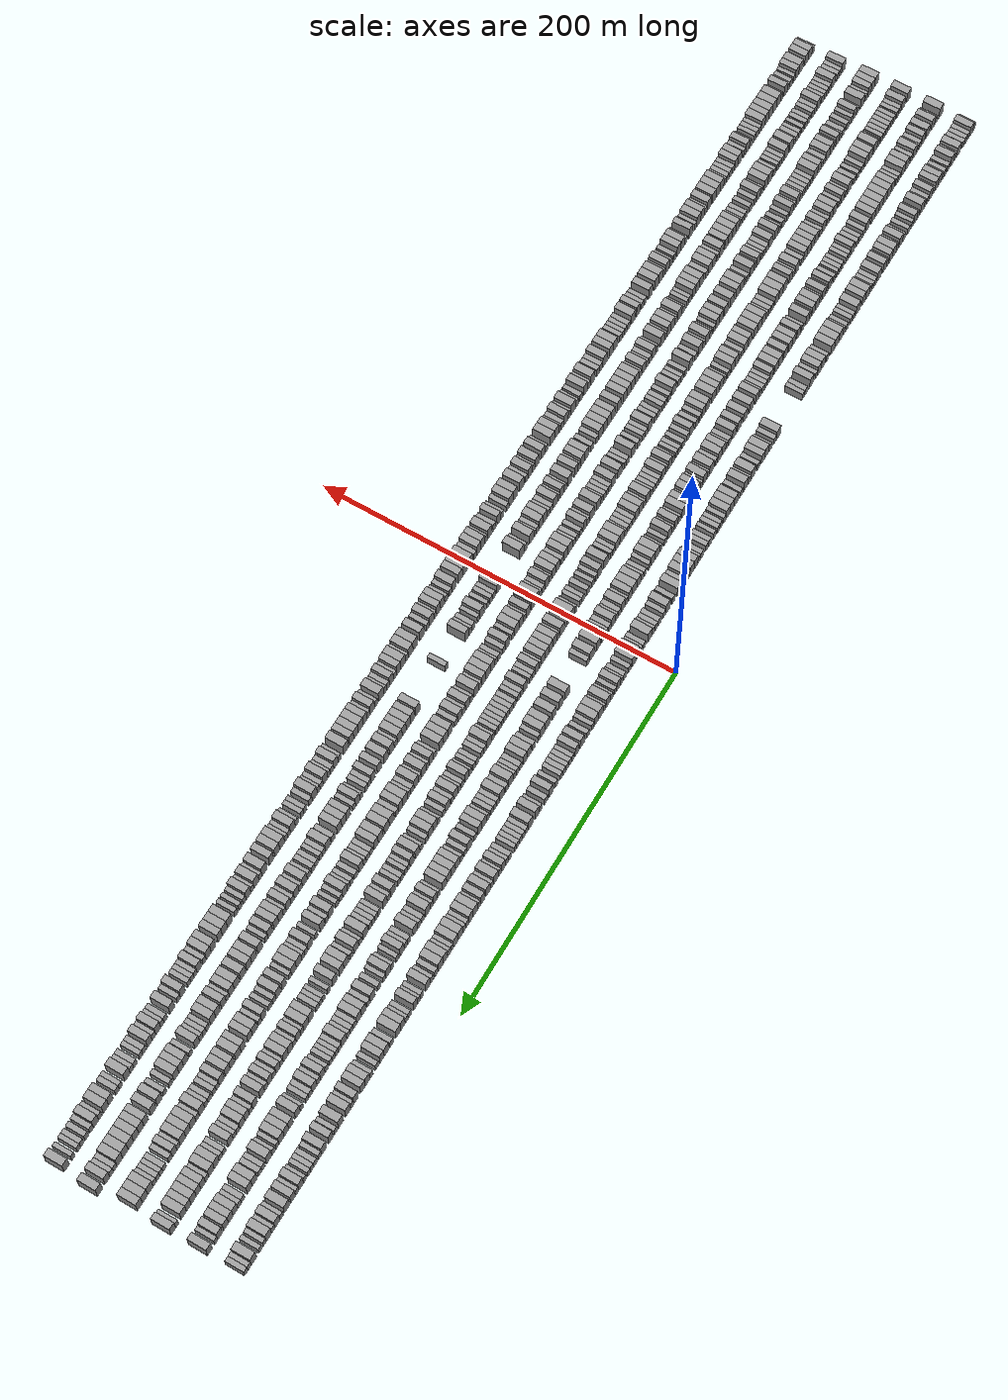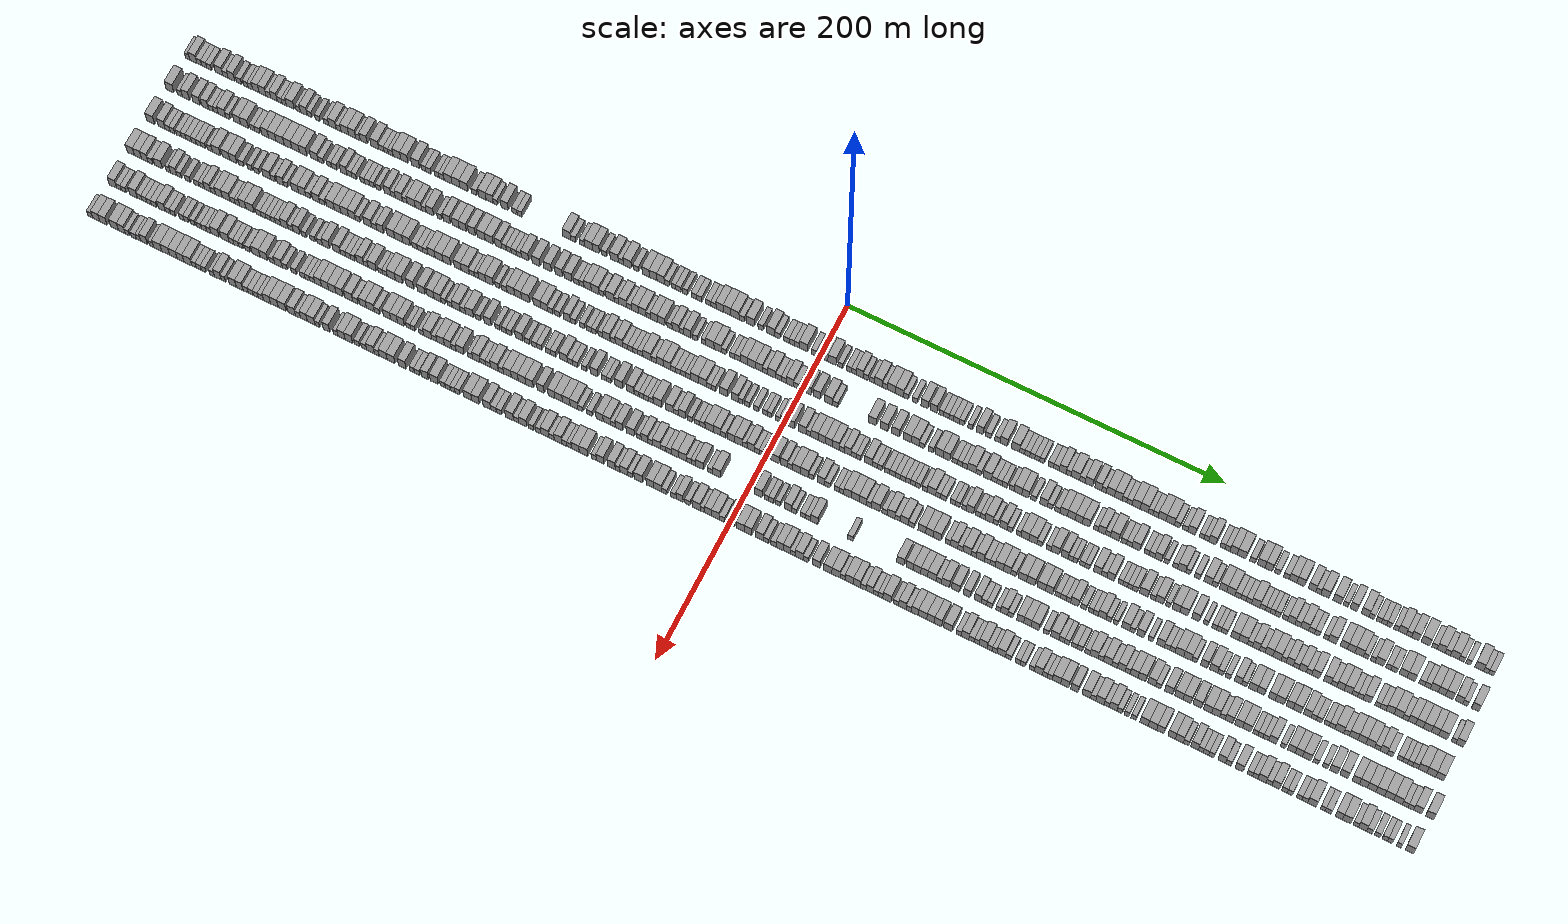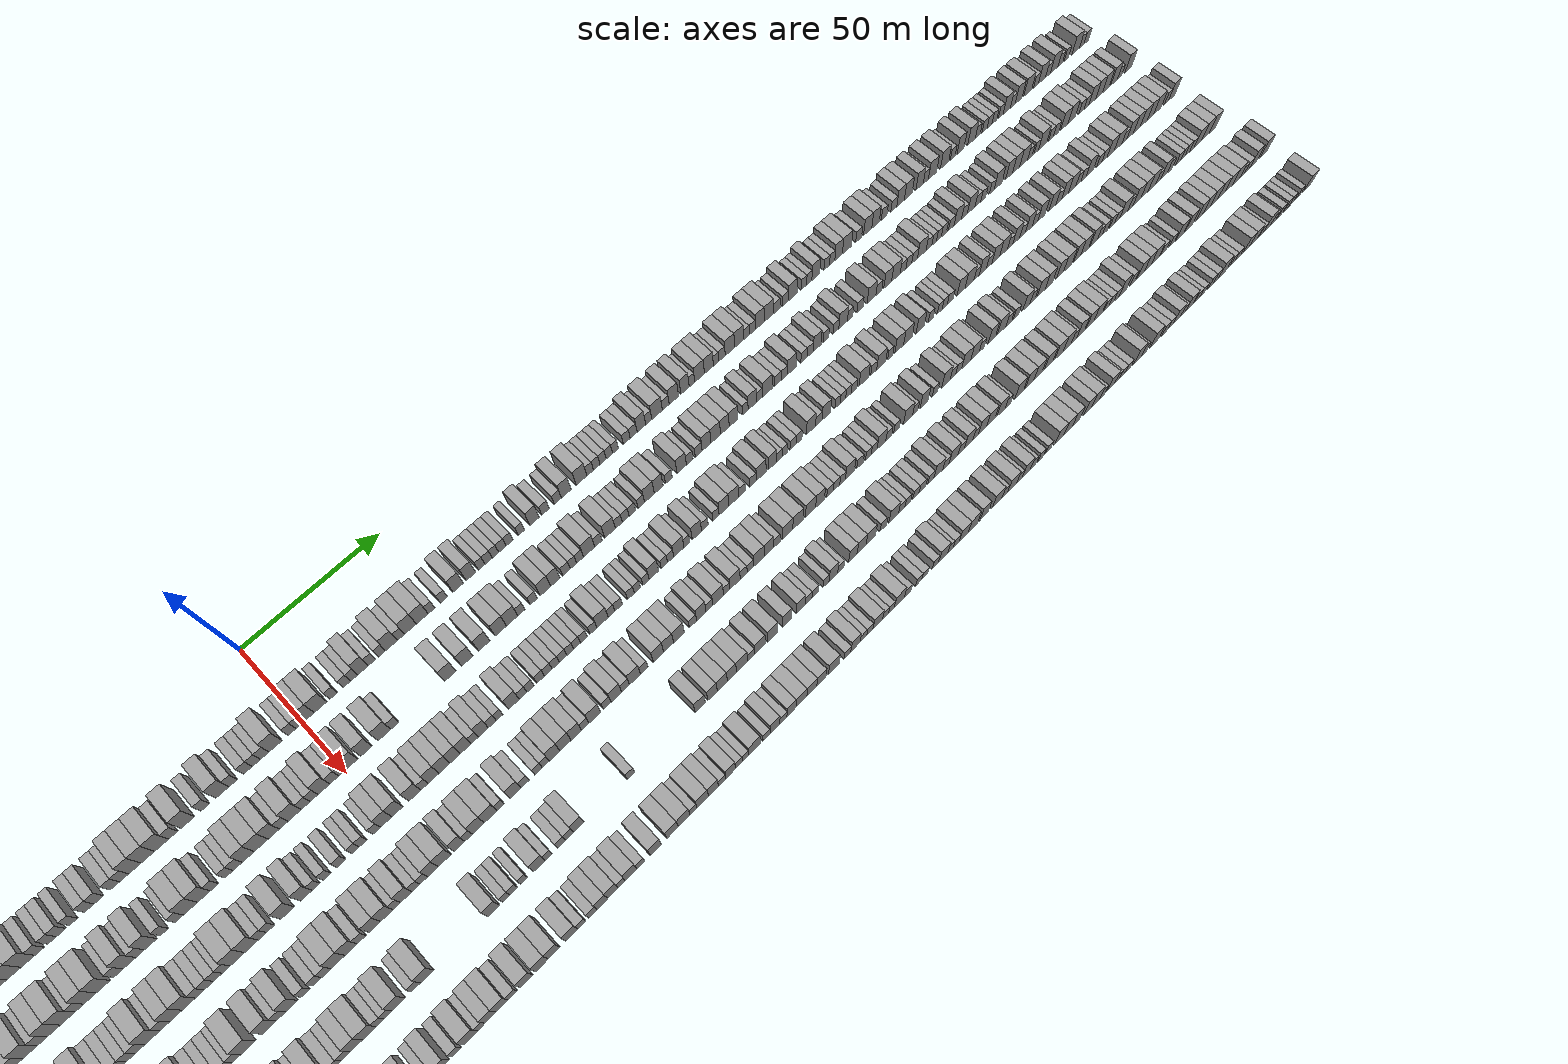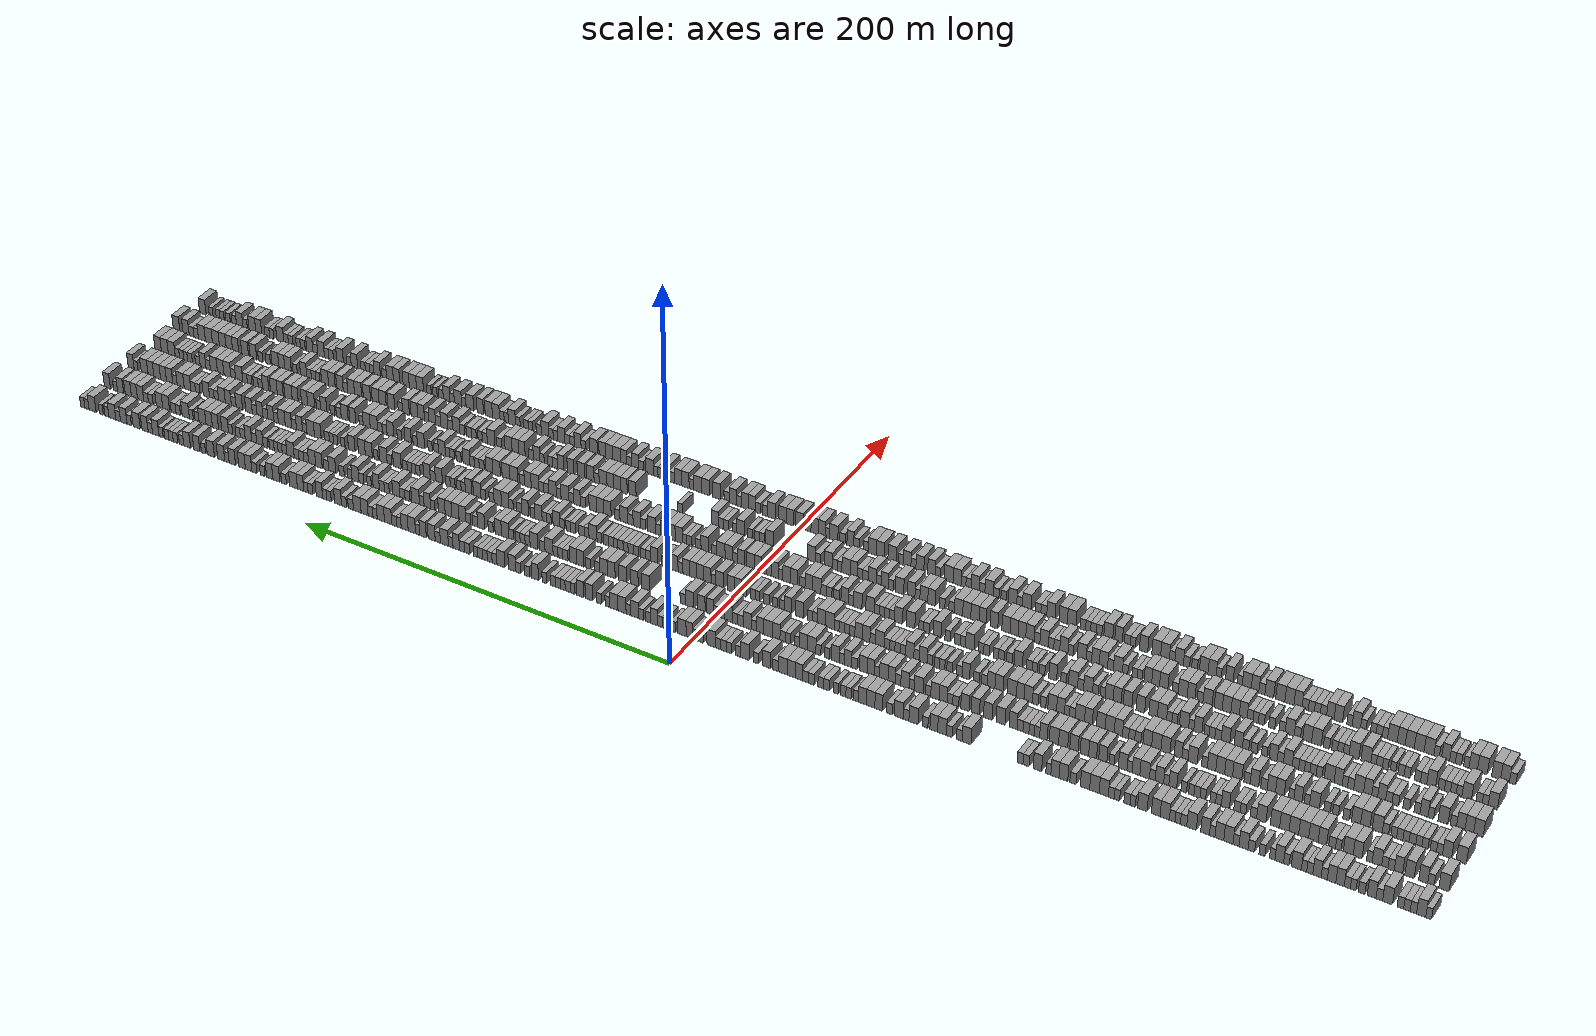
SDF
<sdf version="1.6">
 <world name="default">
  <scene>
   <sky><clouds><speed>12</speed></clouds></sky>
   <ambient>0.4 0.4 0.4 1</ambient>
   <background>0.7 0.7 0.7 1</background>
   <shadows>1</shadows>
  </scene>
  <gravity>0 0 -9.8066</gravity>
  <magnetic_field>6e-06 2.3e-05 -4.2e-05</magnetic_field>
  <physics default="0" name="default_physics" type="ode">
   <ode>
    <solver>
     <type>quick</type>
     <iters>10</iters>
     <sor>1.0</sor>
     <use_dynamic_moi_rescaling>0</use_dynamic_moi_rescaling>
    </solver>
    <constraints>
     <cfm>0</cfm>
     <erp>0.2</erp>
     <contact_max_correcting_vel>100</contact_max_correcting_vel>
     <contact_surface_layer>0.001</contact_surface_layer>
    </constraints>
   </ode>
   <max_step_size>0.004</max_step_size>
   <real_time_factor>1</real_time_factor>
   <real_time_update_rate>250</real_time_update_rate>
  </physics>
  <light name="sun" type="directional">
   <pose>0 0 10 0 0 0</pose>
   <diffuse>0.8 0.8 0.8 1</diffuse>
   <specular>0.2 0.2 0.2 1</specular>
   <attenuation>
    <range>1000</range>
    <constant>0.9</constant>
    <linear>0.01</linear>
    <quadratic>0.001</quadratic>
   </attenuation>
   <direction>-0.5 0.1 -0.9</direction>
  </light>
  <model name="building_1">
   <static>1</static>
   <pose>25.0000 -348.7434 0 0.000000 0.000000 0.000000</pose>
   <link name="link">
    <pose>0 0 3.00 0 0 0</pose>
    <collision name="collision"><geometry><box><size>10.0000 2.5131 6.0000</size></box></geometry></collision>
    <visual name="visual">
     <cast_shadows>0</cast_shadows>
     <geometry><box><size>10.0000 2.5131 6.0000</size></box></geometry>
     <material>
      <script>
       <uri>model://grey_wall/materials/scripts</uri>
       <uri>model://grey_wall/materials/textures</uri>
       <name>vrc/grey_wall</name>
      </script>
     </material>
    </visual>
   </link>
  </model>
  <model name="building_2">
   <static>1</static>
   <pose>25.0000 -345.5113 0 0.000000 0.000000 0.000000</pose>
   <link name="link">
    <pose>0 0 4.50 0 0 0</pose>
    <collision name="collision"><geometry><box><size>10.0000 3.9512 9.0000</size></box></geometry></collision>
    <visual name="visual">
     <cast_shadows>0</cast_shadows>
     <geometry><box><size>10.0000 3.9512 9.0000</size></box></geometry>
     <material>
      <script>
       <uri>model://grey_wall/materials/scripts</uri>
       <uri>model://grey_wall/materials/textures</uri>
       <name>vrc/grey_wall</name>
      </script>
     </material>
    </visual>
   </link>
  </model>
  <model name="building_3">
   <static>1</static>
   <pose>25.0000 -342.1429 0 0.000000 0.000000 0.000000</pose>
   <link name="link">
    <pose>0 0 3.00 0 0 0</pose>
    <collision name="collision"><geometry><box><size>10.0000 2.7857 6.0000</size></box></geometry></collision>
    <visual name="visual">
     <cast_shadows>0</cast_shadows>
     <geometry><box><size>10.0000 2.7857 6.0000</size></box></geometry>
     <material>
      <script>
       <uri>model://grey_wall/materials/scripts</uri>
       <uri>model://grey_wall/materials/textures</uri>
       <name>vrc/grey_wall</name>
      </script>
     </material>
    </visual>
   </link>
  </model>
  <model name="building_4">
   <static>1</static>
   <pose>25.0000 -339.3553 0 0.000000 0.000000 0.000000</pose>
   <link name="link">
    <pose>0 0 3.00 0 0 0</pose>
    <collision name="collision"><geometry><box><size>10.0000 2.7894 6.0000</size></box></geometry></collision>
    <visual name="visual">
     <cast_shadows>0</cast_shadows>
     <geometry><box><size>10.0000 2.7894 6.0000</size></box></geometry>
     <material>
      <script>
       <uri>model://grey_wall/materials/scripts</uri>
       <uri>model://grey_wall/materials/textures</uri>
       <name>vrc/grey_wall</name>
      </script>
     </material>
    </visual>
   </link>
  </model>
  <model name="building_5">
   <static>1</static>
   <pose>25.0000 -336.5316 0 0.000000 0.000000 0.000000</pose>
   <link name="link">
    <pose>0 0 3.00 0 0 0</pose>
    <collision name="collision"><geometry><box><size>10.0000 2.8580 6.0000</size></box></geometry></collision>
    <visual name="visual">
     <cast_shadows>0</cast_shadows>
     <geometry><box><size>10.0000 2.8580 6.0000</size></box></geometry>
     <material>
      <script>
       <uri>model://grey_wall/materials/scripts</uri>
       <uri>model://grey_wall/materials/textures</uri>
       <name>vrc/grey_wall</name>
      </script>
     </material>
    </visual>
   </link>
  </model>
  <model name="building_6">
   <static>1</static>
   <pose>25.0000 -330.9653 0 0.000000 0.000000 0.000000</pose>
   <link name="link">
    <pose>0 0 4.50 0 0 0</pose>
    <collision name="collision"><geometry><box><size>10.0000 4.2746 9.0000</size></box></geometry></collision>
    <visual name="visual">
     <cast_shadows>0</cast_shadows>
     <geometry><box><size>10.0000 4.2746 9.0000</size></box></geometry>
     <material>
      <script>
       <uri>model://grey_wall/materials/scripts</uri>
       <uri>model://grey_wall/materials/textures</uri>
       <name>vrc/grey_wall</name>
      </script>
     </material>
    </visual>
   </link>
  </model>
  <model name="building_7">
   <static>1</static>
   <pose>25.0000 -327.3679 0 0.000000 0.000000 0.000000</pose>
   <link name="link">
    <pose>0 0 3.00 0 0 0</pose>
    <collision name="collision"><geometry><box><size>10.0000 2.9201 6.0000</size></box></geometry></collision>
    <visual name="visual">
     <cast_shadows>0</cast_shadows>
     <geometry><box><size>10.0000 2.9201 6.0000</size></box></geometry>
     <material>
      <script>
       <uri>model://grey_wall/materials/scripts</uri>
       <uri>model://grey_wall/materials/textures</uri>
       <name>vrc/grey_wall</name>
      </script>
     </material>
    </visual>
   </link>
  </model>
  <model name="building_8">
   <static>1</static>
   <pose>25.0000 -324.0019 0 0.000000 0.000000 0.000000</pose>
   <link name="link">
    <pose>0 0 4.50 0 0 0</pose>
    <collision name="collision"><geometry><box><size>10.0000 3.8118 9.0000</size></box></geometry></collision>
    <visual name="visual">
     <cast_shadows>0</cast_shadows>
     <geometry><box><size>10.0000 3.8118 9.0000</size></box></geometry>
     <material>
      <script>
       <uri>model://grey_wall/materials/scripts</uri>
       <uri>model://grey_wall/materials/textures</uri>
       <name>vrc/grey_wall</name>
      </script>
     </material>
    </visual>
   </link>
  </model>
  <model name="building_9">
   <static>1</static>
   <pose>25.0000 -319.6422 0 0.000000 0.000000 0.000000</pose>
   <link name="link">
    <pose>0 0 3.00 0 0 0</pose>
    <collision name="collision"><geometry><box><size>10.0000 2.9077 6.0000</size></box></geometry></collision>
    <visual name="visual">
     <cast_shadows>0</cast_shadows>
     <geometry><box><size>10.0000 2.9077 6.0000</size></box></geometry>
     <material>
      <script>
       <uri>model://grey_wall/materials/scripts</uri>
       <uri>model://grey_wall/materials/textures</uri>
       <name>vrc/grey_wall</name>
      </script>
     </material>
    </visual>
   </link>
  </model>
  <model name="building_10">
   <static>1</static>
   <pose>25.0000 -315.9285 0 0.000000 0.000000 0.000000</pose>
   <link name="link">
    <pose>0 0 3.00 0 0 0</pose>
    <collision name="collision"><geometry><box><size>10.0000 2.5196 6.0000</size></box></geometry></collision>
    <visual name="visual">
     <cast_shadows>0</cast_shadows>
     <geometry><box><size>10.0000 2.5196 6.0000</size></box></geometry>
     <material>
      <script>
       <uri>model://grey_wall/materials/scripts</uri>
       <uri>model://grey_wall/materials/textures</uri>
       <name>vrc/grey_wall</name>
      </script>
     </material>
    </visual>
   </link>
  </model>
  <model name="building_11">
   <static>1</static>
   <pose>25.0000 -313.3374 0 0.000000 0.000000 0.000000</pose>
   <link name="link">
    <pose>0 0 3.00 0 0 0</pose>
    <collision name="collision"><geometry><box><size>10.0000 2.6625 6.0000</size></box></geometry></collision>
    <visual name="visual">
     <cast_shadows>0</cast_shadows>
     <geometry><box><size>10.0000 2.6625 6.0000</size></box></geometry>
     <material>
      <script>
       <uri>model://grey_wall/materials/scripts</uri>
       <uri>model://grey_wall/materials/textures</uri>
       <name>vrc/grey_wall</name>
      </script>
     </material>
    </visual>
   </link>
  </model>
  <model name="building_12">
   <static>1</static>
   <pose>25.0000 -310.1707 0 0.000000 0.000000 0.000000</pose>
   <link name="link">
    <pose>0 0 4.50 0 0 0</pose>
    <collision name="collision"><geometry><box><size>10.0000 3.6710 9.0000</size></box></geometry></collision>
    <visual name="visual">
     <cast_shadows>0</cast_shadows>
     <geometry><box><size>10.0000 3.6710 9.0000</size></box></geometry>
     <material>
      <script>
       <uri>model://grey_wall/materials/scripts</uri>
       <uri>model://grey_wall/materials/textures</uri>
       <name>vrc/grey_wall</name>
      </script>
     </material>
    </visual>
   </link>
  </model>
  <model name="building_13">
   <static>1</static>
   <pose>25.0000 -306.4545 0 0.000000 0.000000 0.000000</pose>
   <link name="link">
    <pose>0 0 4.50 0 0 0</pose>
    <collision name="collision"><geometry><box><size>10.0000 3.7612 9.0000</size></box></geometry></collision>
    <visual name="visual">
     <cast_shadows>0</cast_shadows>
     <geometry><box><size>10.0000 3.7612 9.0000</size></box></geometry>
     <material>
      <script>
       <uri>model://grey_wall/materials/scripts</uri>
       <uri>model://grey_wall/materials/textures</uri>
       <name>vrc/grey_wall</name>
      </script>
     </material>
    </visual>
   </link>
  </model>
  <model name="building_14">
   <static>1</static>
   <pose>25.0000 -303.2031 0 0.000000 0.000000 0.000000</pose>
   <link name="link">
    <pose>0 0 3.00 0 0 0</pose>
    <collision name="collision"><geometry><box><size>10.0000 2.7417 6.0000</size></box></geometry></collision>
    <visual name="visual">
     <cast_shadows>0</cast_shadows>
     <geometry><box><size>10.0000 2.7417 6.0000</size></box></geometry>
     <material>
      <script>
       <uri>model://grey_wall/materials/scripts</uri>
       <uri>model://grey_wall/materials/textures</uri>
       <name>vrc/grey_wall</name>
      </script>
     </material>
    </visual>
   </link>
  </model>
  <model name="building_15">
   <static>1</static>
   <pose>25.0000 -299.9807 0 0.000000 0.000000 0.000000</pose>
   <link name="link">
    <pose>0 0 4.50 0 0 0</pose>
    <collision name="collision"><geometry><box><size>10.0000 3.7031 9.0000</size></box></geometry></collision>
    <visual name="visual">
     <cast_shadows>0</cast_shadows>
     <geometry><box><size>10.0000 3.7031 9.0000</size></box></geometry>
     <material>
      <script>
       <uri>model://grey_wall/materials/scripts</uri>
       <uri>model://grey_wall/materials/textures</uri>
       <name>vrc/grey_wall</name>
      </script>
     </material>
    </visual>
   </link>
  </model>
  <model name="building_16">
   <static>1</static>
   <pose>25.0000 -296.7913 0 0.000000 0.000000 0.000000</pose>
   <link name="link">
    <pose>0 0 3.00 0 0 0</pose>
    <collision name="collision"><geometry><box><size>10.0000 2.6758 6.0000</size></box></geometry></collision>
    <visual name="visual">
     <cast_shadows>0</cast_shadows>
     <geometry><box><size>10.0000 2.6758 6.0000</size></box></geometry>
     <material>
      <script>
       <uri>model://grey_wall/materials/scripts</uri>
       <uri>model://grey_wall/materials/textures</uri>
       <name>vrc/grey_wall</name>
      </script>
     </material>
    </visual>
   </link>
  </model>
  <model name="building_17">
   <static>1</static>
   <pose>25.0000 -294.2476 0 0.000000 0.000000 0.000000</pose>
   <link name="link">
    <pose>0 0 3.00 0 0 0</pose>
    <collision name="collision"><geometry><box><size>10.0000 2.4116 6.0000</size></box></geometry></collision>
    <visual name="visual">
     <cast_shadows>0</cast_shadows>
     <geometry><box><size>10.0000 2.4116 6.0000</size></box></geometry>
     <material>
      <script>
       <uri>model://grey_wall/materials/scripts</uri>
       <uri>model://grey_wall/materials/textures</uri>
       <name>vrc/grey_wall</name>
      </script>
     </material>
    </visual>
   </link>
  </model>
  <model name="building_18">
   <static>1</static>
   <pose>25.0000 -290.8268 0 0.000000 0.000000 0.000000</pose>
   <link name="link">
    <pose>0 0 4.50 0 0 0</pose>
    <collision name="collision"><geometry><box><size>10.0000 4.4300 9.0000</size></box></geometry></collision>
    <visual name="visual">
     <cast_shadows>0</cast_shadows>
     <geometry><box><size>10.0000 4.4300 9.0000</size></box></geometry>
     <material>
      <script>
       <uri>model://grey_wall/materials/scripts</uri>
       <uri>model://grey_wall/materials/textures</uri>
       <name>vrc/grey_wall</name>
      </script>
     </material>
    </visual>
   </link>
  </model>
  <model name="building_19">
   <static>1</static>
   <pose>25.0000 -286.3658 0 0.000000 0.000000 0.000000</pose>
   <link name="link">
    <pose>0 0 3.00 0 0 0</pose>
    <collision name="collision"><geometry><box><size>10.0000 2.4921 6.0000</size></box></geometry></collision>
    <visual name="visual">
     <cast_shadows>0</cast_shadows>
     <geometry><box><size>10.0000 2.4921 6.0000</size></box></geometry>
     <material>
      <script>
       <uri>model://grey_wall/materials/scripts</uri>
       <uri>model://grey_wall/materials/textures</uri>
       <name>vrc/grey_wall</name>
      </script>
     </material>
    </visual>
   </link>
  </model>
  <model name="building_20">
   <static>1</static>
   <pose>25.0000 -283.2193 0 0.000000 0.000000 0.000000</pose>
   <link name="link">
    <pose>0 0 4.50 0 0 0</pose>
    <collision name="collision"><geometry><box><size>10.0000 3.8008 9.0000</size></box></geometry></collision>
    <visual name="visual">
     <cast_shadows>0</cast_shadows>
     <geometry><box><size>10.0000 3.8008 9.0000</size></box></geometry>
     <material>
      <script>
       <uri>model://grey_wall/materials/scripts</uri>
       <uri>model://grey_wall/materials/textures</uri>
       <name>vrc/grey_wall</name>
      </script>
     </material>
    </visual>
   </link>
  </model>
  <model name="building_21">
   <static>1</static>
   <pose>25.0000 -280.0776 0 0.000000 0.000000 0.000000</pose>
   <link name="link">
    <pose>0 0 3.00 0 0 0</pose>
    <collision name="collision"><geometry><box><size>10.0000 2.4828 6.0000</size></box></geometry></collision>
    <visual name="visual">
     <cast_shadows>0</cast_shadows>
     <geometry><box><size>10.0000 2.4828 6.0000</size></box></geometry>
     <material>
      <script>
       <uri>model://grey_wall/materials/scripts</uri>
       <uri>model://grey_wall/materials/textures</uri>
       <name>vrc/grey_wall</name>
      </script>
     </material>
    </visual>
   </link>
  </model>
  <model name="building_22">
   <static>1</static>
   <pose>25.0000 -275.4867 0 0.000000 0.000000 0.000000</pose>
   <link name="link">
    <pose>0 0 3.00 0 0 0</pose>
    <collision name="collision"><geometry><box><size>10.0000 2.6989 6.0000</size></box></geometry></collision>
    <visual name="visual">
     <cast_shadows>0</cast_shadows>
     <geometry><box><size>10.0000 2.6989 6.0000</size></box></geometry>
     <material>
      <script>
       <uri>model://grey_wall/materials/scripts</uri>
       <uri>model://grey_wall/materials/textures</uri>
       <name>vrc/grey_wall</name>
      </script>
     </material>
    </visual>
   </link>
  </model>
  <model name="building_23">
   <static>1</static>
   <pose>25.0000 -270.6789 0 0.000000 0.000000 0.000000</pose>
   <link name="link">
    <pose>0 0 3.00 0 0 0</pose>
    <collision name="collision"><geometry><box><size>10.0000 2.9167 6.0000</size></box></geometry></collision>
    <visual name="visual">
     <cast_shadows>0</cast_shadows>
     <geometry><box><size>10.0000 2.9167 6.0000</size></box></geometry>
     <material>
      <script>
       <uri>model://grey_wall/materials/scripts</uri>
       <uri>model://grey_wall/materials/textures</uri>
       <name>vrc/grey_wall</name>
      </script>
     </material>
    </visual>
   </link>
  </model>
  <model name="building_24">
   <static>1</static>
   <pose>25.0000 -267.1660 0 0.000000 0.000000 0.000000</pose>
   <link name="link">
    <pose>0 0 4.50 0 0 0</pose>
    <collision name="collision"><geometry><box><size>10.0000 4.1092 9.0000</size></box></geometry></collision>
    <visual name="visual">
     <cast_shadows>0</cast_shadows>
     <geometry><box><size>10.0000 4.1092 9.0000</size></box></geometry>
     <material>
      <script>
       <uri>model://grey_wall/materials/scripts</uri>
       <uri>model://grey_wall/materials/textures</uri>
       <name>vrc/grey_wall</name>
      </script>
     </material>
    </visual>
   </link>
  </model>
  <model name="building_25">
   <static>1</static>
   <pose>25.0000 -263.7615 0 0.000000 0.000000 0.000000</pose>
   <link name="link">
    <pose>0 0 3.00 0 0 0</pose>
    <collision name="collision"><geometry><box><size>10.0000 2.6999 6.0000</size></box></geometry></collision>
    <visual name="visual">
     <cast_shadows>0</cast_shadows>
     <geometry><box><size>10.0000 2.6999 6.0000</size></box></geometry>
     <material>
      <script>
       <uri>model://grey_wall/materials/scripts</uri>
       <uri>model://grey_wall/materials/textures</uri>
       <name>vrc/grey_wall</name>
      </script>
     </material>
    </visual>
   </link>
  </model>
  <model name="building_26">
   <static>1</static>
   <pose>25.0000 -260.3240 0 0.000000 0.000000 0.000000</pose>
   <link name="link">
    <pose>0 0 4.50 0 0 0</pose>
    <collision name="collision"><geometry><box><size>10.0000 4.1752 9.0000</size></box></geometry></collision>
    <visual name="visual">
     <cast_shadows>0</cast_shadows>
     <geometry><box><size>10.0000 4.1752 9.0000</size></box></geometry>
     <material>
      <script>
       <uri>model://grey_wall/materials/scripts</uri>
       <uri>model://grey_wall/materials/textures</uri>
       <name>vrc/grey_wall</name>
      </script>
     </material>
    </visual>
   </link>
  </model>
  <model name="building_27">
   <static>1</static>
   <pose>25.0000 -256.2329 0 0.000000 0.000000 0.000000</pose>
   <link name="link">
    <pose>0 0 4.50 0 0 0</pose>
    <collision name="collision"><geometry><box><size>10.0000 4.0070 9.0000</size></box></geometry></collision>
    <visual name="visual">
     <cast_shadows>0</cast_shadows>
     <geometry><box><size>10.0000 4.0070 9.0000</size></box></geometry>
     <material>
      <script>
       <uri>model://grey_wall/materials/scripts</uri>
       <uri>model://grey_wall/materials/textures</uri>
       <name>vrc/grey_wall</name>
      </script>
     </material>
    </visual>
   </link>
  </model>
  <model name="building_28">
   <static>1</static>
   <pose>25.0000 -252.9820 0 0.000000 0.000000 0.000000</pose>
   <link name="link">
    <pose>0 0 3.00 0 0 0</pose>
    <collision name="collision"><geometry><box><size>10.0000 2.4947 6.0000</size></box></geometry></collision>
    <visual name="visual">
     <cast_shadows>0</cast_shadows>
     <geometry><box><size>10.0000 2.4947 6.0000</size></box></geometry>
     <material>
      <script>
       <uri>model://grey_wall/materials/scripts</uri>
       <uri>model://grey_wall/materials/textures</uri>
       <name>vrc/grey_wall</name>
      </script>
     </material>
    </visual>
   </link>
  </model>
  <model name="building_29">
   <static>1</static>
   <pose>25.0000 -249.7479 0 0.000000 0.000000 0.000000</pose>
   <link name="link">
    <pose>0 0 4.50 0 0 0</pose>
    <collision name="collision"><geometry><box><size>10.0000 3.9736 9.0000</size></box></geometry></collision>
    <visual name="visual">
     <cast_shadows>0</cast_shadows>
     <geometry><box><size>10.0000 3.9736 9.0000</size></box></geometry>
     <material>
      <script>
       <uri>model://grey_wall/materials/scripts</uri>
       <uri>model://grey_wall/materials/textures</uri>
       <name>vrc/grey_wall</name>
      </script>
     </material>
    </visual>
   </link>
  </model>
  <model name="building_30">
   <static>1</static>
   <pose>25.0000 -243.5665 0 0.000000 0.000000 0.000000</pose>
   <link name="link">
    <pose>0 0 4.50 0 0 0</pose>
    <collision name="collision"><geometry><box><size>10.0000 4.3892 9.0000</size></box></geometry></collision>
    <visual name="visual">
     <cast_shadows>0</cast_shadows>
     <geometry><box><size>10.0000 4.3892 9.0000</size></box></geometry>
     <material>
      <script>
       <uri>model://grey_wall/materials/scripts</uri>
       <uri>model://grey_wall/materials/textures</uri>
       <name>vrc/grey_wall</name>
      </script>
     </material>
    </visual>
   </link>
  </model>
  <model name="building_31">
   <static>1</static>
   <pose>25.0000 -239.9067 0 0.000000 0.000000 0.000000</pose>
   <link name="link">
    <pose>0 0 3.00 0 0 0</pose>
    <collision name="collision"><geometry><box><size>10.0000 2.9305 6.0000</size></box></geometry></collision>
    <visual name="visual">
     <cast_shadows>0</cast_shadows>
     <geometry><box><size>10.0000 2.9305 6.0000</size></box></geometry>
     <material>
      <script>
       <uri>model://grey_wall/materials/scripts</uri>
       <uri>model://grey_wall/materials/textures</uri>
       <name>vrc/grey_wall</name>
      </script>
     </material>
    </visual>
   </link>
  </model>
  <model name="building_32">
   <static>1</static>
   <pose>25.0000 -237.2282 0 0.000000 0.000000 0.000000</pose>
   <link name="link">
    <pose>0 0 3.00 0 0 0</pose>
    <collision name="collision"><geometry><box><size>10.0000 2.4264 6.0000</size></box></geometry></collision>
    <visual name="visual">
     <cast_shadows>0</cast_shadows>
     <geometry><box><size>10.0000 2.4264 6.0000</size></box></geometry>
     <material>
      <script>
       <uri>model://grey_wall/materials/scripts</uri>
       <uri>model://grey_wall/materials/textures</uri>
       <name>vrc/grey_wall</name>
      </script>
     </material>
    </visual>
   </link>
  </model>
  <model name="building_33">
   <static>1</static>
   <pose>25.0000 -234.7073 0 0.000000 0.000000 0.000000</pose>
   <link name="link">
    <pose>0 0 3.00 0 0 0</pose>
    <collision name="collision"><geometry><box><size>10.0000 2.6153 6.0000</size></box></geometry></collision>
    <visual name="visual">
     <cast_shadows>0</cast_shadows>
     <geometry><box><size>10.0000 2.6153 6.0000</size></box></geometry>
     <material>
      <script>
       <uri>model://grey_wall/materials/scripts</uri>
       <uri>model://grey_wall/materials/textures</uri>
       <name>vrc/grey_wall</name>
      </script>
     </material>
    </visual>
   </link>
  </model>
  <model name="building_34">
   <static>1</static>
   <pose>25.0000 -231.2431 0 0.000000 0.000000 0.000000</pose>
   <link name="link">
    <pose>0 0 4.50 0 0 0</pose>
    <collision name="collision"><geometry><box><size>10.0000 4.3132 9.0000</size></box></geometry></collision>
    <visual name="visual">
     <cast_shadows>0</cast_shadows>
     <geometry><box><size>10.0000 4.3132 9.0000</size></box></geometry>
     <material>
      <script>
       <uri>model://grey_wall/materials/scripts</uri>
       <uri>model://grey_wall/materials/textures</uri>
       <name>vrc/grey_wall</name>
      </script>
     </material>
    </visual>
   </link>
  </model>
  <model name="building_35">
   <static>1</static>
   <pose>25.0000 -227.1045 0 0.000000 0.000000 0.000000</pose>
   <link name="link">
    <pose>0 0 4.50 0 0 0</pose>
    <collision name="collision"><geometry><box><size>10.0000 3.9639 9.0000</size></box></geometry></collision>
    <visual name="visual">
     <cast_shadows>0</cast_shadows>
     <geometry><box><size>10.0000 3.9639 9.0000</size></box></geometry>
     <material>
      <script>
       <uri>model://grey_wall/materials/scripts</uri>
       <uri>model://grey_wall/materials/textures</uri>
       <name>vrc/grey_wall</name>
      </script>
     </material>
    </visual>
   </link>
  </model>
  <model name="building_36">
   <static>1</static>
   <pose>25.0000 -220.8917 0 0.000000 0.000000 0.000000</pose>
   <link name="link">
    <pose>0 0 4.50 0 0 0</pose>
    <collision name="collision"><geometry><box><size>10.0000 4.4618 9.0000</size></box></geometry></collision>
    <visual name="visual">
     <cast_shadows>0</cast_shadows>
     <geometry><box><size>10.0000 4.4618 9.0000</size></box></geometry>
     <material>
      <script>
       <uri>model://grey_wall/materials/scripts</uri>
       <uri>model://grey_wall/materials/textures</uri>
       <name>vrc/grey_wall</name>
      </script>
     </material>
    </visual>
   </link>
  </model>
  <model name="building_37">
   <static>1</static>
   <pose>25.0000 -216.4387 0 0.000000 0.000000 0.000000</pose>
   <link name="link">
    <pose>0 0 3.00 0 0 0</pose>
    <collision name="collision"><geometry><box><size>10.0000 2.4442 6.0000</size></box></geometry></collision>
    <visual name="visual">
     <cast_shadows>0</cast_shadows>
     <geometry><box><size>10.0000 2.4442 6.0000</size></box></geometry>
     <material>
      <script>
       <uri>model://grey_wall/materials/scripts</uri>
       <uri>model://grey_wall/materials/textures</uri>
       <name>vrc/grey_wall</name>
      </script>
     </material>
    </visual>
   </link>
  </model>
  <model name="building_38">
   <static>1</static>
   <pose>25.0000 -213.7599 0 0.000000 0.000000 0.000000</pose>
   <link name="link">
    <pose>0 0 3.00 0 0 0</pose>
    <collision name="collision"><geometry><box><size>10.0000 2.9134 6.0000</size></box></geometry></collision>
    <visual name="visual">
     <cast_shadows>0</cast_shadows>
     <geometry><box><size>10.0000 2.9134 6.0000</size></box></geometry>
     <material>
      <script>
       <uri>model://grey_wall/materials/scripts</uri>
       <uri>model://grey_wall/materials/textures</uri>
       <name>vrc/grey_wall</name>
      </script>
     </material>
    </visual>
   </link>
  </model>
  <model name="building_39">
   <static>1</static>
   <pose>25.0000 -209.0896 0 0.000000 0.000000 0.000000</pose>
   <link name="link">
    <pose>0 0 3.00 0 0 0</pose>
    <collision name="collision"><geometry><box><size>10.0000 2.4271 6.0000</size></box></geometry></collision>
    <visual name="visual">
     <cast_shadows>0</cast_shadows>
     <geometry><box><size>10.0000 2.4271 6.0000</size></box></geometry>
     <material>
      <script>
       <uri>model://grey_wall/materials/scripts</uri>
       <uri>model://grey_wall/materials/textures</uri>
       <name>vrc/grey_wall</name>
      </script>
     </material>
    </visual>
   </link>
  </model>
  <model name="building_40">
   <static>1</static>
   <pose>25.0000 -206.4673 0 0.000000 0.000000 0.000000</pose>
   <link name="link">
    <pose>0 0 3.00 0 0 0</pose>
    <collision name="collision"><geometry><box><size>10.0000 2.8175 6.0000</size></box></geometry></collision>
    <visual name="visual">
     <cast_shadows>0</cast_shadows>
     <geometry><box><size>10.0000 2.8175 6.0000</size></box></geometry>
     <material>
      <script>
       <uri>model://grey_wall/materials/scripts</uri>
       <uri>model://grey_wall/materials/textures</uri>
       <name>vrc/grey_wall</name>
      </script>
     </material>
    </visual>
   </link>
  </model>
  <model name="building_41">
   <static>1</static>
   <pose>25.0000 -202.9107 0 0.000000 0.000000 0.000000</pose>
   <link name="link">
    <pose>0 0 4.50 0 0 0</pose>
    <collision name="collision"><geometry><box><size>10.0000 4.2958 9.0000</size></box></geometry></collision>
    <visual name="visual">
     <cast_shadows>0</cast_shadows>
     <geometry><box><size>10.0000 4.2958 9.0000</size></box></geometry>
     <material>
      <script>
       <uri>model://grey_wall/materials/scripts</uri>
       <uri>model://grey_wall/materials/textures</uri>
       <name>vrc/grey_wall</name>
      </script>
     </material>
    </visual>
   </link>
  </model>
  <model name="building_42">
   <static>1</static>
   <pose>25.0000 -198.5408 0 0.000000 0.000000 0.000000</pose>
   <link name="link">
    <pose>0 0 4.50 0 0 0</pose>
    <collision name="collision"><geometry><box><size>10.0000 4.4440 9.0000</size></box></geometry></collision>
    <visual name="visual">
     <cast_shadows>0</cast_shadows>
     <geometry><box><size>10.0000 4.4440 9.0000</size></box></geometry>
     <material>
      <script>
       <uri>model://grey_wall/materials/scripts</uri>
       <uri>model://grey_wall/materials/textures</uri>
       <name>vrc/grey_wall</name>
      </script>
     </material>
    </visual>
   </link>
  </model>
  <model name="building_43">
   <static>1</static>
   <pose>25.0000 -194.1332 0 0.000000 0.000000 0.000000</pose>
   <link name="link">
    <pose>0 0 4.50 0 0 0</pose>
    <collision name="collision"><geometry><box><size>10.0000 4.3711 9.0000</size></box></geometry></collision>
    <visual name="visual">
     <cast_shadows>0</cast_shadows>
     <geometry><box><size>10.0000 4.3711 9.0000</size></box></geometry>
     <material>
      <script>
       <uri>model://grey_wall/materials/scripts</uri>
       <uri>model://grey_wall/materials/textures</uri>
       <name>vrc/grey_wall</name>
      </script>
     </material>
    </visual>
   </link>
  </model>
  <model name="building_44">
   <static>1</static>
   <pose>25.0000 -188.4746 0 0.000000 0.000000 0.000000</pose>
   <link name="link">
    <pose>0 0 3.00 0 0 0</pose>
    <collision name="collision"><geometry><box><size>10.0000 2.9461 6.0000</size></box></geometry></collision>
    <visual name="visual">
     <cast_shadows>0</cast_shadows>
     <geometry><box><size>10.0000 2.9461 6.0000</size></box></geometry>
     <material>
      <script>
       <uri>model://grey_wall/materials/scripts</uri>
       <uri>model://grey_wall/materials/textures</uri>
       <name>vrc/grey_wall</name>
      </script>
     </material>
    </visual>
   </link>
  </model>
  <model name="building_45">
   <static>1</static>
   <pose>25.0000 -183.9354 0 0.000000 0.000000 0.000000</pose>
   <link name="link">
    <pose>0 0 4.50 0 0 0</pose>
    <collision name="collision"><geometry><box><size>10.0000 4.1322 9.0000</size></box></geometry></collision>
    <visual name="visual">
     <cast_shadows>0</cast_shadows>
     <geometry><box><size>10.0000 4.1322 9.0000</size></box></geometry>
     <material>
      <script>
       <uri>model://grey_wall/materials/scripts</uri>
       <uri>model://grey_wall/materials/textures</uri>
       <name>vrc/grey_wall</name>
      </script>
     </material>
    </visual>
   </link>
  </model>
  <model name="building_46">
   <static>1</static>
   <pose>25.0000 -179.9384 0 0.000000 0.000000 0.000000</pose>
   <link name="link">
    <pose>0 0 4.50 0 0 0</pose>
    <collision name="collision"><geometry><box><size>10.0000 3.8619 9.0000</size></box></geometry></collision>
    <visual name="visual">
     <cast_shadows>0</cast_shadows>
     <geometry><box><size>10.0000 3.8619 9.0000</size></box></geometry>
     <material>
      <script>
       <uri>model://grey_wall/materials/scripts</uri>
       <uri>model://grey_wall/materials/textures</uri>
       <name>vrc/grey_wall</name>
      </script>
     </material>
    </visual>
   </link>
  </model>
  <model name="building_47">
   <static>1</static>
   <pose>25.0000 -176.8023 0 0.000000 0.000000 0.000000</pose>
   <link name="link">
    <pose>0 0 3.00 0 0 0</pose>
    <collision name="collision"><geometry><box><size>10.0000 2.4102 6.0000</size></box></geometry></collision>
    <visual name="visual">
     <cast_shadows>0</cast_shadows>
     <geometry><box><size>10.0000 2.4102 6.0000</size></box></geometry>
     <material>
      <script>
       <uri>model://grey_wall/materials/scripts</uri>
       <uri>model://grey_wall/materials/textures</uri>
       <name>vrc/grey_wall</name>
      </script>
     </material>
    </visual>
   </link>
  </model>
  <model name="building_48">
   <static>1</static>
   <pose>25.0000 -171.6139 0 0.000000 0.000000 0.000000</pose>
   <link name="link">
    <pose>0 0 4.50 0 0 0</pose>
    <collision name="collision"><geometry><box><size>10.0000 3.9666 9.0000</size></box></geometry></collision>
    <visual name="visual">
     <cast_shadows>0</cast_shadows>
     <geometry><box><size>10.0000 3.9666 9.0000</size></box></geometry>
     <material>
      <script>
       <uri>model://grey_wall/materials/scripts</uri>
       <uri>model://grey_wall/materials/textures</uri>
       <name>vrc/grey_wall</name>
      </script>
     </material>
    </visual>
   </link>
  </model>
  <model name="building_49">
   <static>1</static>
   <pose>25.0000 -166.1725 0 0.000000 0.000000 0.000000</pose>
   <link name="link">
    <pose>0 0 3.00 0 0 0</pose>
    <collision name="collision"><geometry><box><size>10.0000 2.9162 6.0000</size></box></geometry></collision>
    <visual name="visual">
     <cast_shadows>0</cast_shadows>
     <geometry><box><size>10.0000 2.9162 6.0000</size></box></geometry>
     <material>
      <script>
       <uri>model://grey_wall/materials/scripts</uri>
       <uri>model://grey_wall/materials/textures</uri>
       <name>vrc/grey_wall</name>
      </script>
     </material>
    </visual>
   </link>
  </model>
  <model name="building_50">
   <static>1</static>
   <pose>25.0000 -163.3622 0 0.000000 0.000000 0.000000</pose>
   <link name="link">
    <pose>0 0 3.00 0 0 0</pose>
    <collision name="collision"><geometry><box><size>10.0000 2.7045 6.0000</size></box></geometry></collision>
    <visual name="visual">
     <cast_shadows>0</cast_shadows>
     <geometry><box><size>10.0000 2.7045 6.0000</size></box></geometry>
     <material>
      <script>
       <uri>model://grey_wall/materials/scripts</uri>
       <uri>model://grey_wall/materials/textures</uri>
       <name>vrc/grey_wall</name>
      </script>
     </material>
    </visual>
   </link>
  </model>
  <model name="building_51">
   <static>1</static>
   <pose>25.0000 -137.5304 0 0.000000 0.000000 0.000000</pose>
   <link name="link">
    <pose>0 0 4.50 0 0 0</pose>
    <collision name="collision"><geometry><box><size>10.0000 4.3197 9.0000</size></box></geometry></collision>
    <visual name="visual">
     <cast_shadows>0</cast_shadows>
     <geometry><box><size>10.0000 4.3197 9.0000</size></box></geometry>
     <material>
      <script>
       <uri>model://grey_wall/materials/scripts</uri>
       <uri>model://grey_wall/materials/textures</uri>
       <name>vrc/grey_wall</name>
      </script>
     </material>
    </visual>
   </link>
  </model>
  <model name="building_52">
   <static>1</static>
   <pose>25.0000 -133.9531 0 0.000000 0.000000 0.000000</pose>
   <link name="link">
    <pose>0 0 3.00 0 0 0</pose>
    <collision name="collision"><geometry><box><size>10.0000 2.8350 6.0000</size></box></geometry></collision>
    <visual name="visual">
     <cast_shadows>0</cast_shadows>
     <geometry><box><size>10.0000 2.8350 6.0000</size></box></geometry>
     <material>
      <script>
       <uri>model://grey_wall/materials/scripts</uri>
       <uri>model://grey_wall/materials/textures</uri>
       <name>vrc/grey_wall</name>
      </script>
     </material>
    </visual>
   </link>
  </model>
  <model name="building_53">
   <static>1</static>
   <pose>25.0000 -129.1353 0 0.000000 0.000000 0.000000</pose>
   <link name="link">
    <pose>0 0 3.00 0 0 0</pose>
    <collision name="collision"><geometry><box><size>10.0000 2.8005 6.0000</size></box></geometry></collision>
    <visual name="visual">
     <cast_shadows>0</cast_shadows>
     <geometry><box><size>10.0000 2.8005 6.0000</size></box></geometry>
     <material>
      <script>
       <uri>model://grey_wall/materials/scripts</uri>
       <uri>model://grey_wall/materials/textures</uri>
       <name>vrc/grey_wall</name>
      </script>
     </material>
    </visual>
   </link>
  </model>
  <model name="building_54">
   <static>1</static>
   <pose>25.0000 -125.5844 0 0.000000 0.000000 0.000000</pose>
   <link name="link">
    <pose>0 0 4.50 0 0 0</pose>
    <collision name="collision"><geometry><box><size>10.0000 4.3012 9.0000</size></box></geometry></collision>
    <visual name="visual">
     <cast_shadows>0</cast_shadows>
     <geometry><box><size>10.0000 4.3012 9.0000</size></box></geometry>
     <material>
      <script>
       <uri>model://grey_wall/materials/scripts</uri>
       <uri>model://grey_wall/materials/textures</uri>
       <name>vrc/grey_wall</name>
      </script>
     </material>
    </visual>
   </link>
  </model>
  <model name="building_55">
   <static>1</static>
   <pose>25.0000 -121.5338 0 0.000000 0.000000 0.000000</pose>
   <link name="link">
    <pose>0 0 4.50 0 0 0</pose>
    <collision name="collision"><geometry><box><size>10.0000 3.8001 9.0000</size></box></geometry></collision>
    <visual name="visual">
     <cast_shadows>0</cast_shadows>
     <geometry><box><size>10.0000 3.8001 9.0000</size></box></geometry>
     <material>
      <script>
       <uri>model://grey_wall/materials/scripts</uri>
       <uri>model://grey_wall/materials/textures</uri>
       <name>vrc/grey_wall</name>
      </script>
     </material>
    </visual>
   </link>
  </model>
  <model name="building_56">
   <static>1</static>
   <pose>25.0000 -117.2014 0 0.000000 0.000000 0.000000</pose>
   <link name="link">
    <pose>0 0 3.00 0 0 0</pose>
    <collision name="collision"><geometry><box><size>10.0000 2.8646 6.0000</size></box></geometry></collision>
    <visual name="visual">
     <cast_shadows>0</cast_shadows>
     <geometry><box><size>10.0000 2.8646 6.0000</size></box></geometry>
     <material>
      <script>
       <uri>model://grey_wall/materials/scripts</uri>
       <uri>model://grey_wall/materials/textures</uri>
       <name>vrc/grey_wall</name>
      </script>
     </material>
    </visual>
   </link>
  </model>
  <model name="building_57">
   <static>1</static>
   <pose>25.0000 -111.5398 0 0.000000 0.000000 0.000000</pose>
   <link name="link">
    <pose>0 0 4.50 0 0 0</pose>
    <collision name="collision"><geometry><box><size>10.0000 4.4586 9.0000</size></box></geometry></collision>
    <visual name="visual">
     <cast_shadows>0</cast_shadows>
     <geometry><box><size>10.0000 4.4586 9.0000</size></box></geometry>
     <material>
      <script>
       <uri>model://grey_wall/materials/scripts</uri>
       <uri>model://grey_wall/materials/textures</uri>
       <name>vrc/grey_wall</name>
      </script>
     </material>
    </visual>
   </link>
  </model>
  <model name="building_58">
   <static>1</static>
   <pose>25.0000 -107.9237 0 0.000000 0.000000 0.000000</pose>
   <link name="link">
    <pose>0 0 3.00 0 0 0</pose>
    <collision name="collision"><geometry><box><size>10.0000 2.7735 6.0000</size></box></geometry></collision>
    <visual name="visual">
     <cast_shadows>0</cast_shadows>
     <geometry><box><size>10.0000 2.7735 6.0000</size></box></geometry>
     <material>
      <script>
       <uri>model://grey_wall/materials/scripts</uri>
       <uri>model://grey_wall/materials/textures</uri>
       <name>vrc/grey_wall</name>
      </script>
     </material>
    </visual>
   </link>
  </model>
  <model name="building_59">
   <static>1</static>
   <pose>25.0000 -104.3509 0 0.000000 0.000000 0.000000</pose>
   <link name="link">
    <pose>0 0 4.50 0 0 0</pose>
    <collision name="collision"><geometry><box><size>10.0000 4.3722 9.0000</size></box></geometry></collision>
    <visual name="visual">
     <cast_shadows>0</cast_shadows>
     <geometry><box><size>10.0000 4.3722 9.0000</size></box></geometry>
     <material>
      <script>
       <uri>model://grey_wall/materials/scripts</uri>
       <uri>model://grey_wall/materials/textures</uri>
       <name>vrc/grey_wall</name>
      </script>
     </material>
    </visual>
   </link>
  </model>
  <model name="building_60">
   <static>1</static>
   <pose>25.0000 -99.7212 0 0.000000 0.000000 0.000000</pose>
   <link name="link">
    <pose>0 0 3.00 0 0 0</pose>
    <collision name="collision"><geometry><box><size>10.0000 2.8872 6.0000</size></box></geometry></collision>
    <visual name="visual">
     <cast_shadows>0</cast_shadows>
     <geometry><box><size>10.0000 2.8872 6.0000</size></box></geometry>
     <material>
      <script>
       <uri>model://grey_wall/materials/scripts</uri>
       <uri>model://grey_wall/materials/textures</uri>
       <name>vrc/grey_wall</name>
      </script>
     </material>
    </visual>
   </link>
  </model>
  <model name="building_61">
   <static>1</static>
   <pose>25.0000 -94.3417 0 0.000000 0.000000 0.000000</pose>
   <link name="link">
    <pose>0 0 4.50 0 0 0</pose>
    <collision name="collision"><geometry><box><size>10.0000 3.8718 9.0000</size></box></geometry></collision>
    <visual name="visual">
     <cast_shadows>0</cast_shadows>
     <geometry><box><size>10.0000 3.8718 9.0000</size></box></geometry>
     <material>
      <script>
       <uri>model://grey_wall/materials/scripts</uri>
       <uri>model://grey_wall/materials/textures</uri>
       <name>vrc/grey_wall</name>
      </script>
     </material>
    </visual>
   </link>
  </model>
  <model name="building_62">
   <static>1</static>
   <pose>25.0000 -90.3250 0 0.000000 0.000000 0.000000</pose>
   <link name="link">
    <pose>0 0 4.50 0 0 0</pose>
    <collision name="collision"><geometry><box><size>10.0000 4.1616 9.0000</size></box></geometry></collision>
    <visual name="visual">
     <cast_shadows>0</cast_shadows>
     <geometry><box><size>10.0000 4.1616 9.0000</size></box></geometry>
     <material>
      <script>
       <uri>model://grey_wall/materials/scripts</uri>
       <uri>model://grey_wall/materials/textures</uri>
       <name>vrc/grey_wall</name>
      </script>
     </material>
    </visual>
   </link>
  </model>
  <model name="building_63">
   <static>1</static>
   <pose>25.0000 -86.2522 0 0.000000 0.000000 0.000000</pose>
   <link name="link">
    <pose>0 0 4.50 0 0 0</pose>
    <collision name="collision"><geometry><box><size>10.0000 3.9840 9.0000</size></box></geometry></collision>
    <visual name="visual">
     <cast_shadows>0</cast_shadows>
     <geometry><box><size>10.0000 3.9840 9.0000</size></box></geometry>
     <material>
      <script>
       <uri>model://grey_wall/materials/scripts</uri>
       <uri>model://grey_wall/materials/textures</uri>
       <name>vrc/grey_wall</name>
      </script>
     </material>
    </visual>
   </link>
  </model>
  <model name="building_64">
   <static>1</static>
   <pose>25.0000 -82.8888 0 0.000000 0.000000 0.000000</pose>
   <link name="link">
    <pose>0 0 3.00 0 0 0</pose>
    <collision name="collision"><geometry><box><size>10.0000 2.7428 6.0000</size></box></geometry></collision>
    <visual name="visual">
     <cast_shadows>0</cast_shadows>
     <geometry><box><size>10.0000 2.7428 6.0000</size></box></geometry>
     <material>
      <script>
       <uri>model://grey_wall/materials/scripts</uri>
       <uri>model://grey_wall/materials/textures</uri>
       <name>vrc/grey_wall</name>
      </script>
     </material>
    </visual>
   </link>
  </model>
  <model name="building_65">
   <static>1</static>
   <pose>25.0000 -79.2299 0 0.000000 0.000000 0.000000</pose>
   <link name="link">
    <pose>0 0 3.00 0 0 0</pose>
    <collision name="collision"><geometry><box><size>10.0000 2.5750 6.0000</size></box></geometry></collision>
    <visual name="visual">
     <cast_shadows>0</cast_shadows>
     <geometry><box><size>10.0000 2.5750 6.0000</size></box></geometry>
     <material>
      <script>
       <uri>model://grey_wall/materials/scripts</uri>
       <uri>model://grey_wall/materials/textures</uri>
       <name>vrc/grey_wall</name>
      </script>
     </material>
    </visual>
   </link>
  </model>
  <model name="building_66">
   <static>1</static>
   <pose>25.0000 -76.5491 0 0.000000 0.000000 0.000000</pose>
   <link name="link">
    <pose>0 0 3.00 0 0 0</pose>
    <collision name="collision"><geometry><box><size>10.0000 2.7866 6.0000</size></box></geometry></collision>
    <visual name="visual">
     <cast_shadows>0</cast_shadows>
     <geometry><box><size>10.0000 2.7866 6.0000</size></box></geometry>
     <material>
      <script>
       <uri>model://grey_wall/materials/scripts</uri>
       <uri>model://grey_wall/materials/textures</uri>
       <name>vrc/grey_wall</name>
      </script>
     </material>
    </visual>
   </link>
  </model>
  <model name="building_67">
   <static>1</static>
   <pose>25.0000 -72.8942 0 0.000000 0.000000 0.000000</pose>
   <link name="link">
    <pose>0 0 3.00 0 0 0</pose>
    <collision name="collision"><geometry><box><size>10.0000 2.5231 6.0000</size></box></geometry></collision>
    <visual name="visual">
     <cast_shadows>0</cast_shadows>
     <geometry><box><size>10.0000 2.5231 6.0000</size></box></geometry>
     <material>
      <script>
       <uri>model://grey_wall/materials/scripts</uri>
       <uri>model://grey_wall/materials/textures</uri>
       <name>vrc/grey_wall</name>
      </script>
     </material>
    </visual>
   </link>
  </model>
  <model name="building_68">
   <static>1</static>
   <pose>25.0000 -68.1796 0 0.000000 0.000000 0.000000</pose>
   <link name="link">
    <pose>0 0 3.00 0 0 0</pose>
    <collision name="collision"><geometry><box><size>10.0000 2.9061 6.0000</size></box></geometry></collision>
    <visual name="visual">
     <cast_shadows>0</cast_shadows>
     <geometry><box><size>10.0000 2.9061 6.0000</size></box></geometry>
     <material>
      <script>
       <uri>model://grey_wall/materials/scripts</uri>
       <uri>model://grey_wall/materials/textures</uri>
       <name>vrc/grey_wall</name>
      </script>
     </material>
    </visual>
   </link>
  </model>
  <model name="building_69">
   <static>1</static>
   <pose>25.0000 -65.2922 0 0.000000 0.000000 0.000000</pose>
   <link name="link">
    <pose>0 0 3.00 0 0 0</pose>
    <collision name="collision"><geometry><box><size>10.0000 2.8687 6.0000</size></box></geometry></collision>
    <visual name="visual">
     <cast_shadows>0</cast_shadows>
     <geometry><box><size>10.0000 2.8687 6.0000</size></box></geometry>
     <material>
      <script>
       <uri>model://grey_wall/materials/scripts</uri>
       <uri>model://grey_wall/materials/textures</uri>
       <name>vrc/grey_wall</name>
      </script>
     </material>
    </visual>
   </link>
  </model>
  <model name="building_70">
   <static>1</static>
   <pose>25.0000 -60.4123 0 0.000000 0.000000 0.000000</pose>
   <link name="link">
    <pose>0 0 3.00 0 0 0</pose>
    <collision name="collision"><geometry><box><size>10.0000 2.8911 6.0000</size></box></geometry></collision>
    <visual name="visual">
     <cast_shadows>0</cast_shadows>
     <geometry><box><size>10.0000 2.8911 6.0000</size></box></geometry>
     <material>
      <script>
       <uri>model://grey_wall/materials/scripts</uri>
       <uri>model://grey_wall/materials/textures</uri>
       <name>vrc/grey_wall</name>
      </script>
     </material>
    </visual>
   </link>
  </model>
  <model name="building_71">
   <static>1</static>
   <pose>25.0000 -57.5742 0 0.000000 0.000000 0.000000</pose>
   <link name="link">
    <pose>0 0 3.00 0 0 0</pose>
    <collision name="collision"><geometry><box><size>10.0000 2.7850 6.0000</size></box></geometry></collision>
    <visual name="visual">
     <cast_shadows>0</cast_shadows>
     <geometry><box><size>10.0000 2.7850 6.0000</size></box></geometry>
     <material>
      <script>
       <uri>model://grey_wall/materials/scripts</uri>
       <uri>model://grey_wall/materials/textures</uri>
       <name>vrc/grey_wall</name>
      </script>
     </material>
    </visual>
   </link>
  </model>
  <model name="building_72">
   <static>1</static>
   <pose>25.0000 -54.2720 0 0.000000 0.000000 0.000000</pose>
   <link name="link">
    <pose>0 0 4.50 0 0 0</pose>
    <collision name="collision"><geometry><box><size>10.0000 3.8194 9.0000</size></box></geometry></collision>
    <visual name="visual">
     <cast_shadows>0</cast_shadows>
     <geometry><box><size>10.0000 3.8194 9.0000</size></box></geometry>
     <material>
      <script>
       <uri>model://grey_wall/materials/scripts</uri>
       <uri>model://grey_wall/materials/textures</uri>
       <name>vrc/grey_wall</name>
      </script>
     </material>
    </visual>
   </link>
  </model>
  <model name="building_73">
   <static>1</static>
   <pose>25.0000 -50.2550 0 0.000000 0.000000 0.000000</pose>
   <link name="link">
    <pose>0 0 4.50 0 0 0</pose>
    <collision name="collision"><geometry><box><size>10.0000 4.2145 9.0000</size></box></geometry></collision>
    <visual name="visual">
     <cast_shadows>0</cast_shadows>
     <geometry><box><size>10.0000 4.2145 9.0000</size></box></geometry>
     <material>
      <script>
       <uri>model://grey_wall/materials/scripts</uri>
       <uri>model://grey_wall/materials/textures</uri>
       <name>vrc/grey_wall</name>
      </script>
     </material>
    </visual>
   </link>
  </model>
  <model name="building_74">
   <static>1</static>
   <pose>25.0000 -45.9555 0 0.000000 0.000000 0.000000</pose>
   <link name="link">
    <pose>0 0 4.50 0 0 0</pose>
    <collision name="collision"><geometry><box><size>10.0000 4.3845 9.0000</size></box></geometry></collision>
    <visual name="visual">
     <cast_shadows>0</cast_shadows>
     <geometry><box><size>10.0000 4.3845 9.0000</size></box></geometry>
     <material>
      <script>
       <uri>model://grey_wall/materials/scripts</uri>
       <uri>model://grey_wall/materials/textures</uri>
       <name>vrc/grey_wall</name>
      </script>
     </material>
    </visual>
   </link>
  </model>
  <model name="building_75">
   <static>1</static>
   <pose>25.0000 -42.3264 0 0.000000 0.000000 0.000000</pose>
   <link name="link">
    <pose>0 0 3.00 0 0 0</pose>
    <collision name="collision"><geometry><box><size>10.0000 2.8739 6.0000</size></box></geometry></collision>
    <visual name="visual">
     <cast_shadows>0</cast_shadows>
     <geometry><box><size>10.0000 2.8739 6.0000</size></box></geometry>
     <material>
      <script>
       <uri>model://grey_wall/materials/scripts</uri>
       <uri>model://grey_wall/materials/textures</uri>
       <name>vrc/grey_wall</name>
      </script>
     </material>
    </visual>
   </link>
  </model>
  <model name="building_76">
   <static>1</static>
   <pose>25.0000 -37.7238 0 0.000000 0.000000 0.000000</pose>
   <link name="link">
    <pose>0 0 4.50 0 0 0</pose>
    <collision name="collision"><geometry><box><size>10.0000 4.3312 9.0000</size></box></geometry></collision>
    <visual name="visual">
     <cast_shadows>0</cast_shadows>
     <geometry><box><size>10.0000 4.3312 9.0000</size></box></geometry>
     <material>
      <script>
       <uri>model://grey_wall/materials/scripts</uri>
       <uri>model://grey_wall/materials/textures</uri>
       <name>vrc/grey_wall</name>
      </script>
     </material>
    </visual>
   </link>
  </model>
  <model name="building_77">
   <static>1</static>
   <pose>25.0000 -32.1401 0 0.000000 0.000000 0.000000</pose>
   <link name="link">
    <pose>0 0 3.00 0 0 0</pose>
    <collision name="collision"><geometry><box><size>10.0000 2.8362 6.0000</size></box></geometry></collision>
    <visual name="visual">
     <cast_shadows>0</cast_shadows>
     <geometry><box><size>10.0000 2.8362 6.0000</size></box></geometry>
     <material>
      <script>
       <uri>model://grey_wall/materials/scripts</uri>
       <uri>model://grey_wall/materials/textures</uri>
       <name>vrc/grey_wall</name>
      </script>
     </material>
    </visual>
   </link>
  </model>
  <model name="building_78">
   <static>1</static>
   <pose>25.0000 -26.5980 0 0.000000 0.000000 0.000000</pose>
   <link name="link">
    <pose>0 0 4.50 0 0 0</pose>
    <collision name="collision"><geometry><box><size>10.0000 4.2480 9.0000</size></box></geometry></collision>
    <visual name="visual">
     <cast_shadows>0</cast_shadows>
     <geometry><box><size>10.0000 4.2480 9.0000</size></box></geometry>
     <material>
      <script>
       <uri>model://grey_wall/materials/scripts</uri>
       <uri>model://grey_wall/materials/textures</uri>
       <name>vrc/grey_wall</name>
      </script>
     </material>
    </visual>
   </link>
  </model>
  <model name="building_79">
   <static>1</static>
   <pose>25.0000 -23.0852 0 0.000000 0.000000 0.000000</pose>
   <link name="link">
    <pose>0 0 3.00 0 0 0</pose>
    <collision name="collision"><geometry><box><size>10.0000 2.7776 6.0000</size></box></geometry></collision>
    <visual name="visual">
     <cast_shadows>0</cast_shadows>
     <geometry><box><size>10.0000 2.7776 6.0000</size></box></geometry>
     <material>
      <script>
       <uri>model://grey_wall/materials/scripts</uri>
       <uri>model://grey_wall/materials/textures</uri>
       <name>vrc/grey_wall</name>
      </script>
     </material>
    </visual>
   </link>
  </model>
  <model name="building_80">
   <static>1</static>
   <pose>25.0000 -18.2527 0 0.000000 0.000000 0.000000</pose>
   <link name="link">
    <pose>0 0 3.00 0 0 0</pose>
    <collision name="collision"><geometry><box><size>10.0000 2.8874 6.0000</size></box></geometry></collision>
    <visual name="visual">
     <cast_shadows>0</cast_shadows>
     <geometry><box><size>10.0000 2.8874 6.0000</size></box></geometry>
     <material>
      <script>
       <uri>model://grey_wall/materials/scripts</uri>
       <uri>model://grey_wall/materials/textures</uri>
       <name>vrc/grey_wall</name>
      </script>
     </material>
    </visual>
   </link>
  </model>
  <model name="building_81">
   <static>1</static>
   <pose>25.0000 -15.4589 0 0.000000 0.000000 0.000000</pose>
   <link name="link">
    <pose>0 0 3.00 0 0 0</pose>
    <collision name="collision"><geometry><box><size>10.0000 2.7003 6.0000</size></box></geometry></collision>
    <visual name="visual">
     <cast_shadows>0</cast_shadows>
     <geometry><box><size>10.0000 2.7003 6.0000</size></box></geometry>
     <material>
      <script>
       <uri>model://grey_wall/materials/scripts</uri>
       <uri>model://grey_wall/materials/textures</uri>
       <name>vrc/grey_wall</name>
      </script>
     </material>
    </visual>
   </link>
  </model>
  <model name="building_82">
   <static>1</static>
   <pose>25.0000 -12.6991 0 0.000000 0.000000 0.000000</pose>
   <link name="link">
    <pose>0 0 3.00 0 0 0</pose>
    <collision name="collision"><geometry><box><size>10.0000 2.8193 6.0000</size></box></geometry></collision>
    <visual name="visual">
     <cast_shadows>0</cast_shadows>
     <geometry><box><size>10.0000 2.8193 6.0000</size></box></geometry>
     <material>
      <script>
       <uri>model://grey_wall/materials/scripts</uri>
       <uri>model://grey_wall/materials/textures</uri>
       <name>vrc/grey_wall</name>
      </script>
     </material>
    </visual>
   </link>
  </model>
  <model name="building_83">
   <static>1</static>
   <pose>25.0000 -9.0820 0 0.000000 0.000000 0.000000</pose>
   <link name="link">
    <pose>0 0 4.50 0 0 0</pose>
    <collision name="collision"><geometry><box><size>10.0000 4.4149 9.0000</size></box></geometry></collision>
    <visual name="visual">
     <cast_shadows>0</cast_shadows>
     <geometry><box><size>10.0000 4.4149 9.0000</size></box></geometry>
     <material>
      <script>
       <uri>model://grey_wall/materials/scripts</uri>
       <uri>model://grey_wall/materials/textures</uri>
       <name>vrc/grey_wall</name>
      </script>
     </material>
    </visual>
   </link>
  </model>
  <model name="building_84">
   <static>1</static>
   <pose>25.0000 -3.5385 0 0.000000 0.000000 0.000000</pose>
   <link name="link">
    <pose>0 0 3.00 0 0 0</pose>
    <collision name="collision"><geometry><box><size>10.0000 2.6722 6.0000</size></box></geometry></collision>
    <visual name="visual">
     <cast_shadows>0</cast_shadows>
     <geometry><box><size>10.0000 2.6722 6.0000</size></box></geometry>
     <material>
      <script>
       <uri>model://grey_wall/materials/scripts</uri>
       <uri>model://grey_wall/materials/textures</uri>
       <name>vrc/grey_wall</name>
      </script>
     </material>
    </visual>
   </link>
  </model>
  <model name="building_85">
   <static>1</static>
   <pose>25.0000 -0.8934 0 0.000000 0.000000 0.000000</pose>
   <link name="link">
    <pose>0 0 3.00 0 0 0</pose>
    <collision name="collision"><geometry><box><size>10.0000 2.6178 6.0000</size></box></geometry></collision>
    <visual name="visual">
     <cast_shadows>0</cast_shadows>
     <geometry><box><size>10.0000 2.6178 6.0000</size></box></geometry>
     <material>
      <script>
       <uri>model://grey_wall/materials/scripts</uri>
       <uri>model://grey_wall/materials/textures</uri>
       <name>vrc/grey_wall</name>
      </script>
     </material>
    </visual>
   </link>
  </model>
  <model name="building_86">
   <static>1</static>
   <pose>25.0000 2.2279 0 0.000000 0.000000 0.000000</pose>
   <link name="link">
    <pose>0 0 4.50 0 0 0</pose>
    <collision name="collision"><geometry><box><size>10.0000 3.6249 9.0000</size></box></geometry></collision>
    <visual name="visual">
     <cast_shadows>0</cast_shadows>
     <geometry><box><size>10.0000 3.6249 9.0000</size></box></geometry>
     <material>
      <script>
       <uri>model://grey_wall/materials/scripts</uri>
       <uri>model://grey_wall/materials/textures</uri>
       <name>vrc/grey_wall</name>
      </script>
     </material>
    </visual>
   </link>
  </model>
  <model name="building_87">
   <static>1</static>
   <pose>25.0000 6.2214 0 0.000000 0.000000 0.000000</pose>
   <link name="link">
    <pose>0 0 4.50 0 0 0</pose>
    <collision name="collision"><geometry><box><size>10.0000 4.3621 9.0000</size></box></geometry></collision>
    <visual name="visual">
     <cast_shadows>0</cast_shadows>
     <geometry><box><size>10.0000 4.3621 9.0000</size></box></geometry>
     <material>
      <script>
       <uri>model://grey_wall/materials/scripts</uri>
       <uri>model://grey_wall/materials/textures</uri>
       <name>vrc/grey_wall</name>
      </script>
     </material>
    </visual>
   </link>
  </model>
  <model name="building_88">
   <static>1</static>
   <pose>25.0000 10.7197 0 0.000000 0.000000 0.000000</pose>
   <link name="link">
    <pose>0 0 3.00 0 0 0</pose>
    <collision name="collision"><geometry><box><size>10.0000 2.6344 6.0000</size></box></geometry></collision>
    <visual name="visual">
     <cast_shadows>0</cast_shadows>
     <geometry><box><size>10.0000 2.6344 6.0000</size></box></geometry>
     <material>
      <script>
       <uri>model://grey_wall/materials/scripts</uri>
       <uri>model://grey_wall/materials/textures</uri>
       <name>vrc/grey_wall</name>
      </script>
     </material>
    </visual>
   </link>
  </model>
  <model name="building_89">
   <static>1</static>
   <pose>25.0000 15.3460 0 0.000000 0.000000 0.000000</pose>
   <link name="link">
    <pose>0 0 3.00 0 0 0</pose>
    <collision name="collision"><geometry><box><size>10.0000 2.6183 6.0000</size></box></geometry></collision>
    <visual name="visual">
     <cast_shadows>0</cast_shadows>
     <geometry><box><size>10.0000 2.6183 6.0000</size></box></geometry>
     <material>
      <script>
       <uri>model://grey_wall/materials/scripts</uri>
       <uri>model://grey_wall/materials/textures</uri>
       <name>vrc/grey_wall</name>
      </script>
     </material>
    </visual>
   </link>
  </model>
  <model name="building_90">
   <static>1</static>
   <pose>25.0000 17.9057 0 0.000000 0.000000 0.000000</pose>
   <link name="link">
    <pose>0 0 3.00 0 0 0</pose>
    <collision name="collision"><geometry><box><size>10.0000 2.5010 6.0000</size></box></geometry></collision>
    <visual name="visual">
     <cast_shadows>0</cast_shadows>
     <geometry><box><size>10.0000 2.5010 6.0000</size></box></geometry>
     <material>
      <script>
       <uri>model://grey_wall/materials/scripts</uri>
       <uri>model://grey_wall/materials/textures</uri>
       <name>vrc/grey_wall</name>
      </script>
     </material>
    </visual>
   </link>
  </model>
  <model name="building_91">
   <static>1</static>
   <pose>25.0000 21.0276 0 0.000000 0.000000 0.000000</pose>
   <link name="link">
    <pose>0 0 4.50 0 0 0</pose>
    <collision name="collision"><geometry><box><size>10.0000 3.7429 9.0000</size></box></geometry></collision>
    <visual name="visual">
     <cast_shadows>0</cast_shadows>
     <geometry><box><size>10.0000 3.7429 9.0000</size></box></geometry>
     <material>
      <script>
       <uri>model://grey_wall/materials/scripts</uri>
       <uri>model://grey_wall/materials/textures</uri>
       <name>vrc/grey_wall</name>
      </script>
     </material>
    </visual>
   </link>
  </model>
  <model name="building_92">
   <static>1</static>
   <pose>25.0000 24.1853 0 0.000000 0.000000 0.000000</pose>
   <link name="link">
    <pose>0 0 3.00 0 0 0</pose>
    <collision name="collision"><geometry><box><size>10.0000 2.5724 6.0000</size></box></geometry></collision>
    <visual name="visual">
     <cast_shadows>0</cast_shadows>
     <geometry><box><size>10.0000 2.5724 6.0000</size></box></geometry>
     <material>
      <script>
       <uri>model://grey_wall/materials/scripts</uri>
       <uri>model://grey_wall/materials/textures</uri>
       <name>vrc/grey_wall</name>
      </script>
     </material>
    </visual>
   </link>
  </model>
  <model name="building_93">
   <static>1</static>
   <pose>25.0000 27.7443 0 0.000000 0.000000 0.000000</pose>
   <link name="link">
    <pose>0 0 3.00 0 0 0</pose>
    <collision name="collision"><geometry><box><size>10.0000 2.5457 6.0000</size></box></geometry></collision>
    <visual name="visual">
     <cast_shadows>0</cast_shadows>
     <geometry><box><size>10.0000 2.5457 6.0000</size></box></geometry>
     <material>
      <script>
       <uri>model://grey_wall/materials/scripts</uri>
       <uri>model://grey_wall/materials/textures</uri>
       <name>vrc/grey_wall</name>
      </script>
     </material>
    </visual>
   </link>
  </model>
  <model name="building_94">
   <static>1</static>
   <pose>25.0000 31.1478 0 0.000000 0.000000 0.000000</pose>
   <link name="link">
    <pose>0 0 4.50 0 0 0</pose>
    <collision name="collision"><geometry><box><size>10.0000 4.2612 9.0000</size></box></geometry></collision>
    <visual name="visual">
     <cast_shadows>0</cast_shadows>
     <geometry><box><size>10.0000 4.2612 9.0000</size></box></geometry>
     <material>
      <script>
       <uri>model://grey_wall/materials/scripts</uri>
       <uri>model://grey_wall/materials/textures</uri>
       <name>vrc/grey_wall</name>
      </script>
     </material>
    </visual>
   </link>
  </model>
  <model name="building_95">
   <static>1</static>
   <pose>25.0000 34.5510 0 0.000000 0.000000 0.000000</pose>
   <link name="link">
    <pose>0 0 3.00 0 0 0</pose>
    <collision name="collision"><geometry><box><size>10.0000 2.5452 6.0000</size></box></geometry></collision>
    <visual name="visual">
     <cast_shadows>0</cast_shadows>
     <geometry><box><size>10.0000 2.5452 6.0000</size></box></geometry>
     <material>
      <script>
       <uri>model://grey_wall/materials/scripts</uri>
       <uri>model://grey_wall/materials/textures</uri>
       <name>vrc/grey_wall</name>
      </script>
     </material>
    </visual>
   </link>
  </model>
  <model name="building_96">
   <static>1</static>
   <pose>25.0000 37.9860 0 0.000000 0.000000 0.000000</pose>
   <link name="link">
    <pose>0 0 4.50 0 0 0</pose>
    <collision name="collision"><geometry><box><size>10.0000 4.3250 9.0000</size></box></geometry></collision>
    <visual name="visual">
     <cast_shadows>0</cast_shadows>
     <geometry><box><size>10.0000 4.3250 9.0000</size></box></geometry>
     <material>
      <script>
       <uri>model://grey_wall/materials/scripts</uri>
       <uri>model://grey_wall/materials/textures</uri>
       <name>vrc/grey_wall</name>
      </script>
     </material>
    </visual>
   </link>
  </model>
  <model name="building_97">
   <static>1</static>
   <pose>25.0000 42.3266 0 0.000000 0.000000 0.000000</pose>
   <link name="link">
    <pose>0 0 4.50 0 0 0</pose>
    <collision name="collision"><geometry><box><size>10.0000 4.3562 9.0000</size></box></geometry></collision>
    <visual name="visual">
     <cast_shadows>0</cast_shadows>
     <geometry><box><size>10.0000 4.3562 9.0000</size></box></geometry>
     <material>
      <script>
       <uri>model://grey_wall/materials/scripts</uri>
       <uri>model://grey_wall/materials/textures</uri>
       <name>vrc/grey_wall</name>
      </script>
     </material>
    </visual>
   </link>
  </model>
  <model name="building_98">
   <static>1</static>
   <pose>25.0000 45.7647 0 0.000000 0.000000 0.000000</pose>
   <link name="link">
    <pose>0 0 3.00 0 0 0</pose>
    <collision name="collision"><geometry><box><size>10.0000 2.5199 6.0000</size></box></geometry></collision>
    <visual name="visual">
     <cast_shadows>0</cast_shadows>
     <geometry><box><size>10.0000 2.5199 6.0000</size></box></geometry>
     <material>
      <script>
       <uri>model://grey_wall/materials/scripts</uri>
       <uri>model://grey_wall/materials/textures</uri>
       <name>vrc/grey_wall</name>
      </script>
     </material>
    </visual>
   </link>
  </model>
  <model name="building_99">
   <static>1</static>
   <pose>25.0000 50.3638 0 0.000000 0.000000 0.000000</pose>
   <link name="link">
    <pose>0 0 3.00 0 0 0</pose>
    <collision name="collision"><geometry><box><size>10.0000 2.6784 6.0000</size></box></geometry></collision>
    <visual name="visual">
     <cast_shadows>0</cast_shadows>
     <geometry><box><size>10.0000 2.6784 6.0000</size></box></geometry>
     <material>
      <script>
       <uri>model://grey_wall/materials/scripts</uri>
       <uri>model://grey_wall/materials/textures</uri>
       <name>vrc/grey_wall</name>
      </script>
     </material>
    </visual>
   </link>
  </model>
  <model name="building_100">
   <static>1</static>
   <pose>25.0000 55.6652 0 0.000000 0.000000 0.000000</pose>
   <link name="link">
    <pose>0 0 4.50 0 0 0</pose>
    <collision name="collision"><geometry><box><size>10.0000 3.9243 9.0000</size></box></geometry></collision>
    <visual name="visual">
     <cast_shadows>0</cast_shadows>
     <geometry><box><size>10.0000 3.9243 9.0000</size></box></geometry>
     <material>
      <script>
       <uri>model://grey_wall/materials/scripts</uri>
       <uri>model://grey_wall/materials/textures</uri>
       <name>vrc/grey_wall</name>
      </script>
     </material>
    </visual>
   </link>
  </model>
  <model name="building_101">
   <static>1</static>
   <pose>25.0000 60.4549 0 0.000000 0.000000 0.000000</pose>
   <link name="link">
    <pose>0 0 4.50 0 0 0</pose>
    <collision name="collision"><geometry><box><size>10.0000 3.6550 9.0000</size></box></geometry></collision>
    <visual name="visual">
     <cast_shadows>0</cast_shadows>
     <geometry><box><size>10.0000 3.6550 9.0000</size></box></geometry>
     <material>
      <script>
       <uri>model://grey_wall/materials/scripts</uri>
       <uri>model://grey_wall/materials/textures</uri>
       <name>vrc/grey_wall</name>
      </script>
     </material>
    </visual>
   </link>
  </model>
  <model name="building_102">
   <static>1</static>
   <pose>25.0000 64.5301 0 0.000000 0.000000 0.000000</pose>
   <link name="link">
    <pose>0 0 3.00 0 0 0</pose>
    <collision name="collision"><geometry><box><size>10.0000 2.4954 6.0000</size></box></geometry></collision>
    <visual name="visual">
     <cast_shadows>0</cast_shadows>
     <geometry><box><size>10.0000 2.4954 6.0000</size></box></geometry>
     <material>
      <script>
       <uri>model://grey_wall/materials/scripts</uri>
       <uri>model://grey_wall/materials/textures</uri>
       <name>vrc/grey_wall</name>
      </script>
     </material>
    </visual>
   </link>
  </model>
  <model name="building_103">
   <static>1</static>
   <pose>25.0000 67.1800 0 0.000000 0.000000 0.000000</pose>
   <link name="link">
    <pose>0 0 3.00 0 0 0</pose>
    <collision name="collision"><geometry><box><size>10.0000 2.8044 6.0000</size></box></geometry></collision>
    <visual name="visual">
     <cast_shadows>0</cast_shadows>
     <geometry><box><size>10.0000 2.8044 6.0000</size></box></geometry>
     <material>
      <script>
       <uri>model://grey_wall/materials/scripts</uri>
       <uri>model://grey_wall/materials/textures</uri>
       <name>vrc/grey_wall</name>
      </script>
     </material>
    </visual>
   </link>
  </model>
  <model name="building_104">
   <static>1</static>
   <pose>25.0000 69.8176 0 0.000000 0.000000 0.000000</pose>
   <link name="link">
    <pose>0 0 3.00 0 0 0</pose>
    <collision name="collision"><geometry><box><size>10.0000 2.4708 6.0000</size></box></geometry></collision>
    <visual name="visual">
     <cast_shadows>0</cast_shadows>
     <geometry><box><size>10.0000 2.4708 6.0000</size></box></geometry>
     <material>
      <script>
       <uri>model://grey_wall/materials/scripts</uri>
       <uri>model://grey_wall/materials/textures</uri>
       <name>vrc/grey_wall</name>
      </script>
     </material>
    </visual>
   </link>
  </model>
  <model name="building_105">
   <static>1</static>
   <pose>25.0000 72.4979 0 0.000000 0.000000 0.000000</pose>
   <link name="link">
    <pose>0 0 3.00 0 0 0</pose>
    <collision name="collision"><geometry><box><size>10.0000 2.8897 6.0000</size></box></geometry></collision>
    <visual name="visual">
     <cast_shadows>0</cast_shadows>
     <geometry><box><size>10.0000 2.8897 6.0000</size></box></geometry>
     <material>
      <script>
       <uri>model://grey_wall/materials/scripts</uri>
       <uri>model://grey_wall/materials/textures</uri>
       <name>vrc/grey_wall</name>
      </script>
     </material>
    </visual>
   </link>
  </model>
  <model name="building_106">
   <static>1</static>
   <pose>25.0000 75.2765 0 0.000000 0.000000 0.000000</pose>
   <link name="link">
    <pose>0 0 3.00 0 0 0</pose>
    <collision name="collision"><geometry><box><size>10.0000 2.6674 6.0000</size></box></geometry></collision>
    <visual name="visual">
     <cast_shadows>0</cast_shadows>
     <geometry><box><size>10.0000 2.6674 6.0000</size></box></geometry>
     <material>
      <script>
       <uri>model://grey_wall/materials/scripts</uri>
       <uri>model://grey_wall/materials/textures</uri>
       <name>vrc/grey_wall</name>
      </script>
     </material>
    </visual>
   </link>
  </model>
  <model name="building_107">
   <static>1</static>
   <pose>25.0000 79.8684 0 0.000000 0.000000 0.000000</pose>
   <link name="link">
    <pose>0 0 3.00 0 0 0</pose>
    <collision name="collision"><geometry><box><size>10.0000 2.5165 6.0000</size></box></geometry></collision>
    <visual name="visual">
     <cast_shadows>0</cast_shadows>
     <geometry><box><size>10.0000 2.5165 6.0000</size></box></geometry>
     <material>
      <script>
       <uri>model://grey_wall/materials/scripts</uri>
       <uri>model://grey_wall/materials/textures</uri>
       <name>vrc/grey_wall</name>
      </script>
     </material>
    </visual>
   </link>
  </model>
  <model name="building_108">
   <static>1</static>
   <pose>25.0000 84.9809 0 0.000000 0.000000 0.000000</pose>
   <link name="link">
    <pose>0 0 4.50 0 0 0</pose>
    <collision name="collision"><geometry><box><size>10.0000 3.7086 9.0000</size></box></geometry></collision>
    <visual name="visual">
     <cast_shadows>0</cast_shadows>
     <geometry><box><size>10.0000 3.7086 9.0000</size></box></geometry>
     <material>
      <script>
       <uri>model://grey_wall/materials/scripts</uri>
       <uri>model://grey_wall/materials/textures</uri>
       <name>vrc/grey_wall</name>
      </script>
     </material>
    </visual>
   </link>
  </model>
  <model name="building_109">
   <static>1</static>
   <pose>25.0000 89.3344 0 0.000000 0.000000 0.000000</pose>
   <link name="link">
    <pose>0 0 3.00 0 0 0</pose>
    <collision name="collision"><geometry><box><size>10.0000 2.9984 6.0000</size></box></geometry></collision>
    <visual name="visual">
     <cast_shadows>0</cast_shadows>
     <geometry><box><size>10.0000 2.9984 6.0000</size></box></geometry>
     <material>
      <script>
       <uri>model://grey_wall/materials/scripts</uri>
       <uri>model://grey_wall/materials/textures</uri>
       <name>vrc/grey_wall</name>
      </script>
     </material>
    </visual>
   </link>
  </model>
  <model name="building_110">
   <static>1</static>
   <pose>25.0000 94.2541 0 0.000000 0.000000 0.000000</pose>
   <link name="link">
    <pose>0 0 3.00 0 0 0</pose>
    <collision name="collision"><geometry><box><size>10.0000 2.8410 6.0000</size></box></geometry></collision>
    <visual name="visual">
     <cast_shadows>0</cast_shadows>
     <geometry><box><size>10.0000 2.8410 6.0000</size></box></geometry>
     <material>
      <script>
       <uri>model://grey_wall/materials/scripts</uri>
       <uri>model://grey_wall/materials/textures</uri>
       <name>vrc/grey_wall</name>
      </script>
     </material>
    </visual>
   </link>
  </model>
  <model name="building_111">
   <static>1</static>
   <pose>25.0000 97.6436 0 0.000000 0.000000 0.000000</pose>
   <link name="link">
    <pose>0 0 4.50 0 0 0</pose>
    <collision name="collision"><geometry><box><size>10.0000 3.9379 9.0000</size></box></geometry></collision>
    <visual name="visual">
     <cast_shadows>0</cast_shadows>
     <geometry><box><size>10.0000 3.9379 9.0000</size></box></geometry>
     <material>
      <script>
       <uri>model://grey_wall/materials/scripts</uri>
       <uri>model://grey_wall/materials/textures</uri>
       <name>vrc/grey_wall</name>
      </script>
     </material>
    </visual>
   </link>
  </model>
  <model name="building_112">
   <static>1</static>
   <pose>25.0000 103.8052 0 0.000000 0.000000 0.000000</pose>
   <link name="link">
    <pose>0 0 4.50 0 0 0</pose>
    <collision name="collision"><geometry><box><size>10.0000 4.3853 9.0000</size></box></geometry></collision>
    <visual name="visual">
     <cast_shadows>0</cast_shadows>
     <geometry><box><size>10.0000 4.3853 9.0000</size></box></geometry>
     <material>
      <script>
       <uri>model://grey_wall/materials/scripts</uri>
       <uri>model://grey_wall/materials/textures</uri>
       <name>vrc/grey_wall</name>
      </script>
     </material>
    </visual>
   </link>
  </model>
  <model name="building_113">
   <static>1</static>
   <pose>25.0000 107.3430 0 0.000000 0.000000 0.000000</pose>
   <link name="link">
    <pose>0 0 3.00 0 0 0</pose>
    <collision name="collision"><geometry><box><size>10.0000 2.6902 6.0000</size></box></geometry></collision>
    <visual name="visual">
     <cast_shadows>0</cast_shadows>
     <geometry><box><size>10.0000 2.6902 6.0000</size></box></geometry>
     <material>
      <script>
       <uri>model://grey_wall/materials/scripts</uri>
       <uri>model://grey_wall/materials/textures</uri>
       <name>vrc/grey_wall</name>
      </script>
     </material>
    </visual>
   </link>
  </model>
  <model name="building_114">
   <static>1</static>
   <pose>25.0000 110.0168 0 0.000000 0.000000 0.000000</pose>
   <link name="link">
    <pose>0 0 3.00 0 0 0</pose>
    <collision name="collision"><geometry><box><size>10.0000 2.6574 6.0000</size></box></geometry></collision>
    <visual name="visual">
     <cast_shadows>0</cast_shadows>
     <geometry><box><size>10.0000 2.6574 6.0000</size></box></geometry>
     <material>
      <script>
       <uri>model://grey_wall/materials/scripts</uri>
       <uri>model://grey_wall/materials/textures</uri>
       <name>vrc/grey_wall</name>
      </script>
     </material>
    </visual>
   </link>
  </model>
  <model name="building_115">
   <static>1</static>
   <pose>25.0000 112.6450 0 0.000000 0.000000 0.000000</pose>
   <link name="link">
    <pose>0 0 3.00 0 0 0</pose>
    <collision name="collision"><geometry><box><size>10.0000 2.5992 6.0000</size></box></geometry></collision>
    <visual name="visual">
     <cast_shadows>0</cast_shadows>
     <geometry><box><size>10.0000 2.5992 6.0000</size></box></geometry>
     <material>
      <script>
       <uri>model://grey_wall/materials/scripts</uri>
       <uri>model://grey_wall/materials/textures</uri>
       <name>vrc/grey_wall</name>
      </script>
     </material>
    </visual>
   </link>
  </model>
  <model name="building_116">
   <static>1</static>
   <pose>25.0000 115.2576 0 0.000000 0.000000 0.000000</pose>
   <link name="link">
    <pose>0 0 3.00 0 0 0</pose>
    <collision name="collision"><geometry><box><size>10.0000 2.6260 6.0000</size></box></geometry></collision>
    <visual name="visual">
     <cast_shadows>0</cast_shadows>
     <geometry><box><size>10.0000 2.6260 6.0000</size></box></geometry>
     <material>
      <script>
       <uri>model://grey_wall/materials/scripts</uri>
       <uri>model://grey_wall/materials/textures</uri>
       <name>vrc/grey_wall</name>
      </script>
     </material>
    </visual>
   </link>
  </model>
  <model name="building_117">
   <static>1</static>
   <pose>25.0000 117.7822 0 0.000000 0.000000 0.000000</pose>
   <link name="link">
    <pose>0 0 3.00 0 0 0</pose>
    <collision name="collision"><geometry><box><size>10.0000 2.4232 6.0000</size></box></geometry></collision>
    <visual name="visual">
     <cast_shadows>0</cast_shadows>
     <geometry><box><size>10.0000 2.4232 6.0000</size></box></geometry>
     <material>
      <script>
       <uri>model://grey_wall/materials/scripts</uri>
       <uri>model://grey_wall/materials/textures</uri>
       <name>vrc/grey_wall</name>
      </script>
     </material>
    </visual>
   </link>
  </model>
  <model name="building_118">
   <static>1</static>
   <pose>25.0000 122.4349 0 0.000000 0.000000 0.000000</pose>
   <link name="link">
    <pose>0 0 3.00 0 0 0</pose>
    <collision name="collision"><geometry><box><size>10.0000 2.8821 6.0000</size></box></geometry></collision>
    <visual name="visual">
     <cast_shadows>0</cast_shadows>
     <geometry><box><size>10.0000 2.8821 6.0000</size></box></geometry>
     <material>
      <script>
       <uri>model://grey_wall/materials/scripts</uri>
       <uri>model://grey_wall/materials/textures</uri>
       <name>vrc/grey_wall</name>
      </script>
     </material>
    </visual>
   </link>
  </model>
  <model name="building_119">
   <static>1</static>
   <pose>25.0000 125.3614 0 0.000000 0.000000 0.000000</pose>
   <link name="link">
    <pose>0 0 3.00 0 0 0</pose>
    <collision name="collision"><geometry><box><size>10.0000 2.9710 6.0000</size></box></geometry></collision>
    <visual name="visual">
     <cast_shadows>0</cast_shadows>
     <geometry><box><size>10.0000 2.9710 6.0000</size></box></geometry>
     <material>
      <script>
       <uri>model://grey_wall/materials/scripts</uri>
       <uri>model://grey_wall/materials/textures</uri>
       <name>vrc/grey_wall</name>
      </script>
     </material>
    </visual>
   </link>
  </model>
  <model name="building_120">
   <static>1</static>
   <pose>25.0000 128.6660 0 0.000000 0.000000 0.000000</pose>
   <link name="link">
    <pose>0 0 4.50 0 0 0</pose>
    <collision name="collision"><geometry><box><size>10.0000 3.6383 9.0000</size></box></geometry></collision>
    <visual name="visual">
     <cast_shadows>0</cast_shadows>
     <geometry><box><size>10.0000 3.6383 9.0000</size></box></geometry>
     <material>
      <script>
       <uri>model://grey_wall/materials/scripts</uri>
       <uri>model://grey_wall/materials/textures</uri>
       <name>vrc/grey_wall</name>
      </script>
     </material>
    </visual>
   </link>
  </model>
  <model name="building_121">
   <static>1</static>
   <pose>25.0000 131.7746 0 0.000000 0.000000 0.000000</pose>
   <link name="link">
    <pose>0 0 3.00 0 0 0</pose>
    <collision name="collision"><geometry><box><size>10.0000 2.5788 6.0000</size></box></geometry></collision>
    <visual name="visual">
     <cast_shadows>0</cast_shadows>
     <geometry><box><size>10.0000 2.5788 6.0000</size></box></geometry>
     <material>
      <script>
       <uri>model://grey_wall/materials/scripts</uri>
       <uri>model://grey_wall/materials/textures</uri>
       <name>vrc/grey_wall</name>
      </script>
     </material>
    </visual>
   </link>
  </model>
  <model name="building_122">
   <static>1</static>
   <pose>25.0000 135.3098 0 0.000000 0.000000 0.000000</pose>
   <link name="link">
    <pose>0 0 4.50 0 0 0</pose>
    <collision name="collision"><geometry><box><size>10.0000 4.4916 9.0000</size></box></geometry></collision>
    <visual name="visual">
     <cast_shadows>0</cast_shadows>
     <geometry><box><size>10.0000 4.4916 9.0000</size></box></geometry>
     <material>
      <script>
       <uri>model://grey_wall/materials/scripts</uri>
       <uri>model://grey_wall/materials/textures</uri>
       <name>vrc/grey_wall</name>
      </script>
     </material>
    </visual>
   </link>
  </model>
  <model name="building_123">
   <static>1</static>
   <pose>25.0000 139.0275 0 0.000000 0.000000 0.000000</pose>
   <link name="link">
    <pose>0 0 3.00 0 0 0</pose>
    <collision name="collision"><geometry><box><size>10.0000 2.9438 6.0000</size></box></geometry></collision>
    <visual name="visual">
     <cast_shadows>0</cast_shadows>
     <geometry><box><size>10.0000 2.9438 6.0000</size></box></geometry>
     <material>
      <script>
       <uri>model://grey_wall/materials/scripts</uri>
       <uri>model://grey_wall/materials/textures</uri>
       <name>vrc/grey_wall</name>
      </script>
     </material>
    </visual>
   </link>
  </model>
  <model name="building_124">
   <static>1</static>
   <pose>25.0000 142.5194 0 0.000000 0.000000 0.000000</pose>
   <link name="link">
    <pose>0 0 4.50 0 0 0</pose>
    <collision name="collision"><geometry><box><size>10.0000 4.0399 9.0000</size></box></geometry></collision>
    <visual name="visual">
     <cast_shadows>0</cast_shadows>
     <geometry><box><size>10.0000 4.0399 9.0000</size></box></geometry>
     <material>
      <script>
       <uri>model://grey_wall/materials/scripts</uri>
       <uri>model://grey_wall/materials/textures</uri>
       <name>vrc/grey_wall</name>
      </script>
     </material>
    </visual>
   </link>
  </model>
  <model name="building_125">
   <static>1</static>
   <pose>25.0000 147.3535 0 0.000000 0.000000 0.000000</pose>
   <link name="link">
    <pose>0 0 4.50 0 0 0</pose>
    <collision name="collision"><geometry><box><size>10.0000 3.6283 9.0000</size></box></geometry></collision>
    <visual name="visual">
     <cast_shadows>0</cast_shadows>
     <geometry><box><size>10.0000 3.6283 9.0000</size></box></geometry>
     <material>
      <script>
       <uri>model://grey_wall/materials/scripts</uri>
       <uri>model://grey_wall/materials/textures</uri>
       <name>vrc/grey_wall</name>
      </script>
     </material>
    </visual>
   </link>
  </model>
  <model name="building_126">
   <static>1</static>
   <pose>25.0000 150.3799 0 0.000000 0.000000 0.000000</pose>
   <link name="link">
    <pose>0 0 3.00 0 0 0</pose>
    <collision name="collision"><geometry><box><size>10.0000 2.4246 6.0000</size></box></geometry></collision>
    <visual name="visual">
     <cast_shadows>0</cast_shadows>
     <geometry><box><size>10.0000 2.4246 6.0000</size></box></geometry>
     <material>
      <script>
       <uri>model://grey_wall/materials/scripts</uri>
       <uri>model://grey_wall/materials/textures</uri>
       <name>vrc/grey_wall</name>
      </script>
     </material>
    </visual>
   </link>
  </model>
  <model name="building_127">
   <static>1</static>
   <pose>25.0000 153.7157 0 0.000000 0.000000 0.000000</pose>
   <link name="link">
    <pose>0 0 4.50 0 0 0</pose>
    <collision name="collision"><geometry><box><size>10.0000 4.2469 9.0000</size></box></geometry></collision>
    <visual name="visual">
     <cast_shadows>0</cast_shadows>
     <geometry><box><size>10.0000 4.2469 9.0000</size></box></geometry>
     <material>
      <script>
       <uri>model://grey_wall/materials/scripts</uri>
       <uri>model://grey_wall/materials/textures</uri>
       <name>vrc/grey_wall</name>
      </script>
     </material>
    </visual>
   </link>
  </model>
  <model name="building_128">
   <static>1</static>
   <pose>25.0000 157.8291 0 0.000000 0.000000 0.000000</pose>
   <link name="link">
    <pose>0 0 4.50 0 0 0</pose>
    <collision name="collision"><geometry><box><size>10.0000 3.9800 9.0000</size></box></geometry></collision>
    <visual name="visual">
     <cast_shadows>0</cast_shadows>
     <geometry><box><size>10.0000 3.9800 9.0000</size></box></geometry>
     <material>
      <script>
       <uri>model://grey_wall/materials/scripts</uri>
       <uri>model://grey_wall/materials/textures</uri>
       <name>vrc/grey_wall</name>
      </script>
     </material>
    </visual>
   </link>
  </model>
  <model name="building_129">
   <static>1</static>
   <pose>25.0000 161.0231 0 0.000000 0.000000 0.000000</pose>
   <link name="link">
    <pose>0 0 3.00 0 0 0</pose>
    <collision name="collision"><geometry><box><size>10.0000 2.4081 6.0000</size></box></geometry></collision>
    <visual name="visual">
     <cast_shadows>0</cast_shadows>
     <geometry><box><size>10.0000 2.4081 6.0000</size></box></geometry>
     <material>
      <script>
       <uri>model://grey_wall/materials/scripts</uri>
       <uri>model://grey_wall/materials/textures</uri>
       <name>vrc/grey_wall</name>
      </script>
     </material>
    </visual>
   </link>
  </model>
  <model name="building_130">
   <static>1</static>
   <pose>25.0000 163.6570 0 0.000000 0.000000 0.000000</pose>
   <link name="link">
    <pose>0 0 3.00 0 0 0</pose>
    <collision name="collision"><geometry><box><size>10.0000 2.8596 6.0000</size></box></geometry></collision>
    <visual name="visual">
     <cast_shadows>0</cast_shadows>
     <geometry><box><size>10.0000 2.8596 6.0000</size></box></geometry>
     <material>
      <script>
       <uri>model://grey_wall/materials/scripts</uri>
       <uri>model://grey_wall/materials/textures</uri>
       <name>vrc/grey_wall</name>
      </script>
     </material>
    </visual>
   </link>
  </model>
  <model name="building_131">
   <static>1</static>
   <pose>25.0000 167.1961 0 0.000000 0.000000 0.000000</pose>
   <link name="link">
    <pose>0 0 4.50 0 0 0</pose>
    <collision name="collision"><geometry><box><size>10.0000 4.2186 9.0000</size></box></geometry></collision>
    <visual name="visual">
     <cast_shadows>0</cast_shadows>
     <geometry><box><size>10.0000 4.2186 9.0000</size></box></geometry>
     <material>
      <script>
       <uri>model://grey_wall/materials/scripts</uri>
       <uri>model://grey_wall/materials/textures</uri>
       <name>vrc/grey_wall</name>
      </script>
     </material>
    </visual>
   </link>
  </model>
  <model name="building_132">
   <static>1</static>
   <pose>25.0000 171.4076 0 0.000000 0.000000 0.000000</pose>
   <link name="link">
    <pose>0 0 4.50 0 0 0</pose>
    <collision name="collision"><geometry><box><size>10.0000 4.2045 9.0000</size></box></geometry></collision>
    <visual name="visual">
     <cast_shadows>0</cast_shadows>
     <geometry><box><size>10.0000 4.2045 9.0000</size></box></geometry>
     <material>
      <script>
       <uri>model://grey_wall/materials/scripts</uri>
       <uri>model://grey_wall/materials/textures</uri>
       <name>vrc/grey_wall</name>
      </script>
     </material>
    </visual>
   </link>
  </model>
  <model name="building_133">
   <static>1</static>
   <pose>25.0000 174.7264 0 0.000000 0.000000 0.000000</pose>
   <link name="link">
    <pose>0 0 3.00 0 0 0</pose>
    <collision name="collision"><geometry><box><size>10.0000 2.4329 6.0000</size></box></geometry></collision>
    <visual name="visual">
     <cast_shadows>0</cast_shadows>
     <geometry><box><size>10.0000 2.4329 6.0000</size></box></geometry>
     <material>
      <script>
       <uri>model://grey_wall/materials/scripts</uri>
       <uri>model://grey_wall/materials/textures</uri>
       <name>vrc/grey_wall</name>
      </script>
     </material>
    </visual>
   </link>
  </model>
  <model name="building_134">
   <static>1</static>
   <pose>25.0000 177.3379 0 0.000000 0.000000 0.000000</pose>
   <link name="link">
    <pose>0 0 3.00 0 0 0</pose>
    <collision name="collision"><geometry><box><size>10.0000 2.7902 6.0000</size></box></geometry></collision>
    <visual name="visual">
     <cast_shadows>0</cast_shadows>
     <geometry><box><size>10.0000 2.7902 6.0000</size></box></geometry>
     <material>
      <script>
       <uri>model://grey_wall/materials/scripts</uri>
       <uri>model://grey_wall/materials/textures</uri>
       <name>vrc/grey_wall</name>
      </script>
     </material>
    </visual>
   </link>
  </model>
  <model name="building_135">
   <static>1</static>
   <pose>25.0000 180.7376 0 0.000000 0.000000 0.000000</pose>
   <link name="link">
    <pose>0 0 4.50 0 0 0</pose>
    <collision name="collision"><geometry><box><size>10.0000 4.0091 9.0000</size></box></geometry></collision>
    <visual name="visual">
     <cast_shadows>0</cast_shadows>
     <geometry><box><size>10.0000 4.0091 9.0000</size></box></geometry>
     <material>
      <script>
       <uri>model://grey_wall/materials/scripts</uri>
       <uri>model://grey_wall/materials/textures</uri>
       <name>vrc/grey_wall</name>
      </script>
     </material>
    </visual>
   </link>
  </model>
  <model name="building_136">
   <static>1</static>
   <pose>25.0000 184.9646 0 0.000000 0.000000 0.000000</pose>
   <link name="link">
    <pose>0 0 4.50 0 0 0</pose>
    <collision name="collision"><geometry><box><size>10.0000 4.4449 9.0000</size></box></geometry></collision>
    <visual name="visual">
     <cast_shadows>0</cast_shadows>
     <geometry><box><size>10.0000 4.4449 9.0000</size></box></geometry>
     <material>
      <script>
       <uri>model://grey_wall/materials/scripts</uri>
       <uri>model://grey_wall/materials/textures</uri>
       <name>vrc/grey_wall</name>
      </script>
     </material>
    </visual>
   </link>
  </model>
  <model name="building_137">
   <static>1</static>
   <pose>25.0000 188.6688 0 0.000000 0.000000 0.000000</pose>
   <link name="link">
    <pose>0 0 3.00 0 0 0</pose>
    <collision name="collision"><geometry><box><size>10.0000 2.9633 6.0000</size></box></geometry></collision>
    <visual name="visual">
     <cast_shadows>0</cast_shadows>
     <geometry><box><size>10.0000 2.9633 6.0000</size></box></geometry>
     <material>
      <script>
       <uri>model://grey_wall/materials/scripts</uri>
       <uri>model://grey_wall/materials/textures</uri>
       <name>vrc/grey_wall</name>
      </script>
     </material>
    </visual>
   </link>
  </model>
  <model name="building_138">
   <static>1</static>
   <pose>25.0000 192.6228 0 0.000000 0.000000 0.000000</pose>
   <link name="link">
    <pose>0 0 3.00 0 0 0</pose>
    <collision name="collision"><geometry><box><size>10.0000 2.9449 6.0000</size></box></geometry></collision>
    <visual name="visual">
     <cast_shadows>0</cast_shadows>
     <geometry><box><size>10.0000 2.9449 6.0000</size></box></geometry>
     <material>
      <script>
       <uri>model://grey_wall/materials/scripts</uri>
       <uri>model://grey_wall/materials/textures</uri>
       <name>vrc/grey_wall</name>
      </script>
     </material>
    </visual>
   </link>
  </model>
  <model name="building_139">
   <static>1</static>
   <pose>25.0000 196.0760 0 0.000000 0.000000 0.000000</pose>
   <link name="link">
    <pose>0 0 4.50 0 0 0</pose>
    <collision name="collision"><geometry><box><size>10.0000 3.9615 9.0000</size></box></geometry></collision>
    <visual name="visual">
     <cast_shadows>0</cast_shadows>
     <geometry><box><size>10.0000 3.9615 9.0000</size></box></geometry>
     <material>
      <script>
       <uri>model://grey_wall/materials/scripts</uri>
       <uri>model://grey_wall/materials/textures</uri>
       <name>vrc/grey_wall</name>
      </script>
     </material>
    </visual>
   </link>
  </model>
  <model name="building_140">
   <static>1</static>
   <pose>25.0000 201.3352 0 0.000000 0.000000 0.000000</pose>
   <link name="link">
    <pose>0 0 3.00 0 0 0</pose>
    <collision name="collision"><geometry><box><size>10.0000 2.5569 6.0000</size></box></geometry></collision>
    <visual name="visual">
     <cast_shadows>0</cast_shadows>
     <geometry><box><size>10.0000 2.5569 6.0000</size></box></geometry>
     <material>
      <script>
       <uri>model://grey_wall/materials/scripts</uri>
       <uri>model://grey_wall/materials/textures</uri>
       <name>vrc/grey_wall</name>
      </script>
     </material>
    </visual>
   </link>
  </model>
  <model name="building_141">
   <static>1</static>
   <pose>25.0000 203.8421 0 0.000000 0.000000 0.000000</pose>
   <link name="link">
    <pose>0 0 3.00 0 0 0</pose>
    <collision name="collision"><geometry><box><size>10.0000 2.4568 6.0000</size></box></geometry></collision>
    <visual name="visual">
     <cast_shadows>0</cast_shadows>
     <geometry><box><size>10.0000 2.4568 6.0000</size></box></geometry>
     <material>
      <script>
       <uri>model://grey_wall/materials/scripts</uri>
       <uri>model://grey_wall/materials/textures</uri>
       <name>vrc/grey_wall</name>
      </script>
     </material>
    </visual>
   </link>
  </model>
  <model name="building_142">
   <static>1</static>
   <pose>25.0000 206.9484 0 0.000000 0.000000 0.000000</pose>
   <link name="link">
    <pose>0 0 4.50 0 0 0</pose>
    <collision name="collision"><geometry><box><size>10.0000 3.7558 9.0000</size></box></geometry></collision>
    <visual name="visual">
     <cast_shadows>0</cast_shadows>
     <geometry><box><size>10.0000 3.7558 9.0000</size></box></geometry>
     <material>
      <script>
       <uri>model://grey_wall/materials/scripts</uri>
       <uri>model://grey_wall/materials/textures</uri>
       <name>vrc/grey_wall</name>
      </script>
     </material>
    </visual>
   </link>
  </model>
  <model name="building_143">
   <static>1</static>
   <pose>25.0000 212.1789 0 0.000000 0.000000 0.000000</pose>
   <link name="link">
    <pose>0 0 3.00 0 0 0</pose>
    <collision name="collision"><geometry><box><size>10.0000 2.7054 6.0000</size></box></geometry></collision>
    <visual name="visual">
     <cast_shadows>0</cast_shadows>
     <geometry><box><size>10.0000 2.7054 6.0000</size></box></geometry>
     <material>
      <script>
       <uri>model://grey_wall/materials/scripts</uri>
       <uri>model://grey_wall/materials/textures</uri>
       <name>vrc/grey_wall</name>
      </script>
     </material>
    </visual>
   </link>
  </model>
  <model name="building_144">
   <static>1</static>
   <pose>25.0000 214.8105 0 0.000000 0.000000 0.000000</pose>
   <link name="link">
    <pose>0 0 3.00 0 0 0</pose>
    <collision name="collision"><geometry><box><size>10.0000 2.5578 6.0000</size></box></geometry></collision>
    <visual name="visual">
     <cast_shadows>0</cast_shadows>
     <geometry><box><size>10.0000 2.5578 6.0000</size></box></geometry>
     <material>
      <script>
       <uri>model://grey_wall/materials/scripts</uri>
       <uri>model://grey_wall/materials/textures</uri>
       <name>vrc/grey_wall</name>
      </script>
     </material>
    </visual>
   </link>
  </model>
  <model name="building_145">
   <static>1</static>
   <pose>25.0000 217.9452 0 0.000000 0.000000 0.000000</pose>
   <link name="link">
    <pose>0 0 4.50 0 0 0</pose>
    <collision name="collision"><geometry><box><size>10.0000 3.7116 9.0000</size></box></geometry></collision>
    <visual name="visual">
     <cast_shadows>0</cast_shadows>
     <geometry><box><size>10.0000 3.7116 9.0000</size></box></geometry>
     <material>
      <script>
       <uri>model://grey_wall/materials/scripts</uri>
       <uri>model://grey_wall/materials/textures</uri>
       <name>vrc/grey_wall</name>
      </script>
     </material>
    </visual>
   </link>
  </model>
  <model name="building_146">
   <static>1</static>
   <pose>25.0000 222.0358 0 0.000000 0.000000 0.000000</pose>
   <link name="link">
    <pose>0 0 4.50 0 0 0</pose>
    <collision name="collision"><geometry><box><size>10.0000 4.4697 9.0000</size></box></geometry></collision>
    <visual name="visual">
     <cast_shadows>0</cast_shadows>
     <geometry><box><size>10.0000 4.4697 9.0000</size></box></geometry>
     <material>
      <script>
       <uri>model://grey_wall/materials/scripts</uri>
       <uri>model://grey_wall/materials/textures</uri>
       <name>vrc/grey_wall</name>
      </script>
     </material>
    </visual>
   </link>
  </model>
  <model name="building_147">
   <static>1</static>
   <pose>25.0000 227.7238 0 0.000000 0.000000 0.000000</pose>
   <link name="link">
    <pose>0 0 3.00 0 0 0</pose>
    <collision name="collision"><geometry><box><size>10.0000 2.9061 6.0000</size></box></geometry></collision>
    <visual name="visual">
     <cast_shadows>0</cast_shadows>
     <geometry><box><size>10.0000 2.9061 6.0000</size></box></geometry>
     <material>
      <script>
       <uri>model://grey_wall/materials/scripts</uri>
       <uri>model://grey_wall/materials/textures</uri>
       <name>vrc/grey_wall</name>
      </script>
     </material>
    </visual>
   </link>
  </model>
  <model name="building_148">
   <static>1</static>
   <pose>25.0000 232.2005 0 0.000000 0.000000 0.000000</pose>
   <link name="link">
    <pose>0 0 4.50 0 0 0</pose>
    <collision name="collision"><geometry><box><size>10.0000 4.0473 9.0000</size></box></geometry></collision>
    <visual name="visual">
     <cast_shadows>0</cast_shadows>
     <geometry><box><size>10.0000 4.0473 9.0000</size></box></geometry>
     <material>
      <script>
       <uri>model://grey_wall/materials/scripts</uri>
       <uri>model://grey_wall/materials/textures</uri>
       <name>vrc/grey_wall</name>
      </script>
     </material>
    </visual>
   </link>
  </model>
  <model name="building_149">
   <static>1</static>
   <pose>25.0000 236.1040 0 0.000000 0.000000 0.000000</pose>
   <link name="link">
    <pose>0 0 4.50 0 0 0</pose>
    <collision name="collision"><geometry><box><size>10.0000 3.7598 9.0000</size></box></geometry></collision>
    <visual name="visual">
     <cast_shadows>0</cast_shadows>
     <geometry><box><size>10.0000 3.7598 9.0000</size></box></geometry>
     <material>
      <script>
       <uri>model://grey_wall/materials/scripts</uri>
       <uri>model://grey_wall/materials/textures</uri>
       <name>vrc/grey_wall</name>
      </script>
     </material>
    </visual>
   </link>
  </model>
  <model name="building_150">
   <static>1</static>
   <pose>25.0000 240.3848 0 0.000000 0.000000 0.000000</pose>
   <link name="link">
    <pose>0 0 3.00 0 0 0</pose>
    <collision name="collision"><geometry><box><size>10.0000 2.8017 6.0000</size></box></geometry></collision>
    <visual name="visual">
     <cast_shadows>0</cast_shadows>
     <geometry><box><size>10.0000 2.8017 6.0000</size></box></geometry>
     <material>
      <script>
       <uri>model://grey_wall/materials/scripts</uri>
       <uri>model://grey_wall/materials/textures</uri>
       <name>vrc/grey_wall</name>
      </script>
     </material>
    </visual>
   </link>
  </model>
  <model name="building_151">
   <static>1</static>
   <pose>25.0000 245.2728 0 0.000000 0.000000 0.000000</pose>
   <link name="link">
    <pose>0 0 3.00 0 0 0</pose>
    <collision name="collision"><geometry><box><size>10.0000 2.9743 6.0000</size></box></geometry></collision>
    <visual name="visual">
     <cast_shadows>0</cast_shadows>
     <geometry><box><size>10.0000 2.9743 6.0000</size></box></geometry>
     <material>
      <script>
       <uri>model://grey_wall/materials/scripts</uri>
       <uri>model://grey_wall/materials/textures</uri>
       <name>vrc/grey_wall</name>
      </script>
     </material>
    </visual>
   </link>
  </model>
  <model name="building_152">
   <static>1</static>
   <pose>25.0000 248.6910 0 0.000000 0.000000 0.000000</pose>
   <link name="link">
    <pose>0 0 4.50 0 0 0</pose>
    <collision name="collision"><geometry><box><size>10.0000 3.8621 9.0000</size></box></geometry></collision>
    <visual name="visual">
     <cast_shadows>0</cast_shadows>
     <geometry><box><size>10.0000 3.8621 9.0000</size></box></geometry>
     <material>
      <script>
       <uri>model://grey_wall/materials/scripts</uri>
       <uri>model://grey_wall/materials/textures</uri>
       <name>vrc/grey_wall</name>
      </script>
     </material>
    </visual>
   </link>
  </model>
  <model name="building_153">
   <static>1</static>
   <pose>25.0000 252.5700 0 0.000000 0.000000 0.000000</pose>
   <link name="link">
    <pose>0 0 4.50 0 0 0</pose>
    <collision name="collision"><geometry><box><size>10.0000 3.8959 9.0000</size></box></geometry></collision>
    <visual name="visual">
     <cast_shadows>0</cast_shadows>
     <geometry><box><size>10.0000 3.8959 9.0000</size></box></geometry>
     <material>
      <script>
       <uri>model://grey_wall/materials/scripts</uri>
       <uri>model://grey_wall/materials/textures</uri>
       <name>vrc/grey_wall</name>
      </script>
     </material>
    </visual>
   </link>
  </model>
  <model name="building_154">
   <static>1</static>
   <pose>25.0000 258.4167 0 0.000000 0.000000 0.000000</pose>
   <link name="link">
    <pose>0 0 4.50 0 0 0</pose>
    <collision name="collision"><geometry><box><size>10.0000 3.7974 9.0000</size></box></geometry></collision>
    <visual name="visual">
     <cast_shadows>0</cast_shadows>
     <geometry><box><size>10.0000 3.7974 9.0000</size></box></geometry>
     <material>
      <script>
       <uri>model://grey_wall/materials/scripts</uri>
       <uri>model://grey_wall/materials/textures</uri>
       <name>vrc/grey_wall</name>
      </script>
     </material>
    </visual>
   </link>
  </model>
  <model name="building_155">
   <static>1</static>
   <pose>25.0000 261.6458 0 0.000000 0.000000 0.000000</pose>
   <link name="link">
    <pose>0 0 3.00 0 0 0</pose>
    <collision name="collision"><geometry><box><size>10.0000 2.6609 6.0000</size></box></geometry></collision>
    <visual name="visual">
     <cast_shadows>0</cast_shadows>
     <geometry><box><size>10.0000 2.6609 6.0000</size></box></geometry>
     <material>
      <script>
       <uri>model://grey_wall/materials/scripts</uri>
       <uri>model://grey_wall/materials/textures</uri>
       <name>vrc/grey_wall</name>
      </script>
     </material>
    </visual>
   </link>
  </model>
  <model name="building_156">
   <static>1</static>
   <pose>25.0000 265.0822 0 0.000000 0.000000 0.000000</pose>
   <link name="link">
    <pose>0 0 4.50 0 0 0</pose>
    <collision name="collision"><geometry><box><size>10.0000 4.2119 9.0000</size></box></geometry></collision>
    <visual name="visual">
     <cast_shadows>0</cast_shadows>
     <geometry><box><size>10.0000 4.2119 9.0000</size></box></geometry>
     <material>
      <script>
       <uri>model://grey_wall/materials/scripts</uri>
       <uri>model://grey_wall/materials/textures</uri>
       <name>vrc/grey_wall</name>
      </script>
     </material>
    </visual>
   </link>
  </model>
  <model name="building_157">
   <static>1</static>
   <pose>25.0000 271.3295 0 0.000000 0.000000 0.000000</pose>
   <link name="link">
    <pose>0 0 4.50 0 0 0</pose>
    <collision name="collision"><geometry><box><size>10.0000 4.2827 9.0000</size></box></geometry></collision>
    <visual name="visual">
     <cast_shadows>0</cast_shadows>
     <geometry><box><size>10.0000 4.2827 9.0000</size></box></geometry>
     <material>
      <script>
       <uri>model://grey_wall/materials/scripts</uri>
       <uri>model://grey_wall/materials/textures</uri>
       <name>vrc/grey_wall</name>
      </script>
     </material>
    </visual>
   </link>
  </model>
  <model name="building_158">
   <static>1</static>
   <pose>25.0000 275.7166 0 0.000000 0.000000 0.000000</pose>
   <link name="link">
    <pose>0 0 3.00 0 0 0</pose>
    <collision name="collision"><geometry><box><size>10.0000 2.4914 6.0000</size></box></geometry></collision>
    <visual name="visual">
     <cast_shadows>0</cast_shadows>
     <geometry><box><size>10.0000 2.4914 6.0000</size></box></geometry>
     <material>
      <script>
       <uri>model://grey_wall/materials/scripts</uri>
       <uri>model://grey_wall/materials/textures</uri>
       <name>vrc/grey_wall</name>
      </script>
     </material>
    </visual>
   </link>
  </model>
  <model name="building_159">
   <static>1</static>
   <pose>25.0000 279.7860 0 0.000000 0.000000 0.000000</pose>
   <link name="link">
    <pose>0 0 4.50 0 0 0</pose>
    <collision name="collision"><geometry><box><size>10.0000 3.6475 9.0000</size></box></geometry></collision>
    <visual name="visual">
     <cast_shadows>0</cast_shadows>
     <geometry><box><size>10.0000 3.6475 9.0000</size></box></geometry>
     <material>
      <script>
       <uri>model://grey_wall/materials/scripts</uri>
       <uri>model://grey_wall/materials/textures</uri>
       <name>vrc/grey_wall</name>
      </script>
     </material>
    </visual>
   </link>
  </model>
  <model name="building_160">
   <static>1</static>
   <pose>25.0000 285.6505 0 0.000000 0.000000 0.000000</pose>
   <link name="link">
    <pose>0 0 4.50 0 0 0</pose>
    <collision name="collision"><geometry><box><size>10.0000 4.0815 9.0000</size></box></geometry></collision>
    <visual name="visual">
     <cast_shadows>0</cast_shadows>
     <geometry><box><size>10.0000 4.0815 9.0000</size></box></geometry>
     <material>
      <script>
       <uri>model://grey_wall/materials/scripts</uri>
       <uri>model://grey_wall/materials/textures</uri>
       <name>vrc/grey_wall</name>
      </script>
     </material>
    </visual>
   </link>
  </model>
  <model name="building_161">
   <static>1</static>
   <pose>25.0000 289.0042 0 0.000000 0.000000 0.000000</pose>
   <link name="link">
    <pose>0 0 3.00 0 0 0</pose>
    <collision name="collision"><geometry><box><size>10.0000 2.6261 6.0000</size></box></geometry></collision>
    <visual name="visual">
     <cast_shadows>0</cast_shadows>
     <geometry><box><size>10.0000 2.6261 6.0000</size></box></geometry>
     <material>
      <script>
       <uri>model://grey_wall/materials/scripts</uri>
       <uri>model://grey_wall/materials/textures</uri>
       <name>vrc/grey_wall</name>
      </script>
     </material>
    </visual>
   </link>
  </model>
  <model name="building_162">
   <static>1</static>
   <pose>25.0000 292.6975 0 0.000000 0.000000 0.000000</pose>
   <link name="link">
    <pose>0 0 3.00 0 0 0</pose>
    <collision name="collision"><geometry><box><size>10.0000 2.7605 6.0000</size></box></geometry></collision>
    <visual name="visual">
     <cast_shadows>0</cast_shadows>
     <geometry><box><size>10.0000 2.7605 6.0000</size></box></geometry>
     <material>
      <script>
       <uri>model://grey_wall/materials/scripts</uri>
       <uri>model://grey_wall/materials/textures</uri>
       <name>vrc/grey_wall</name>
      </script>
     </material>
    </visual>
   </link>
  </model>
  <model name="building_163">
   <static>1</static>
   <pose>25.0000 295.4054 0 0.000000 0.000000 0.000000</pose>
   <link name="link">
    <pose>0 0 3.00 0 0 0</pose>
    <collision name="collision"><geometry><box><size>10.0000 2.6553 6.0000</size></box></geometry></collision>
    <visual name="visual">
     <cast_shadows>0</cast_shadows>
     <geometry><box><size>10.0000 2.6553 6.0000</size></box></geometry>
     <material>
      <script>
       <uri>model://grey_wall/materials/scripts</uri>
       <uri>model://grey_wall/materials/textures</uri>
       <name>vrc/grey_wall</name>
      </script>
     </material>
    </visual>
   </link>
  </model>
  <model name="building_164">
   <static>1</static>
   <pose>25.0000 297.9946 0 0.000000 0.000000 0.000000</pose>
   <link name="link">
    <pose>0 0 3.00 0 0 0</pose>
    <collision name="collision"><geometry><box><size>10.0000 2.5231 6.0000</size></box></geometry></collision>
    <visual name="visual">
     <cast_shadows>0</cast_shadows>
     <geometry><box><size>10.0000 2.5231 6.0000</size></box></geometry>
     <material>
      <script>
       <uri>model://grey_wall/materials/scripts</uri>
       <uri>model://grey_wall/materials/textures</uri>
       <name>vrc/grey_wall</name>
      </script>
     </material>
    </visual>
   </link>
  </model>
  <model name="building_165">
   <static>1</static>
   <pose>25.0000 301.5238 0 0.000000 0.000000 0.000000</pose>
   <link name="link">
    <pose>0 0 3.00 0 0 0</pose>
    <collision name="collision"><geometry><box><size>10.0000 2.5353 6.0000</size></box></geometry></collision>
    <visual name="visual">
     <cast_shadows>0</cast_shadows>
     <geometry><box><size>10.0000 2.5353 6.0000</size></box></geometry>
     <material>
      <script>
       <uri>model://grey_wall/materials/scripts</uri>
       <uri>model://grey_wall/materials/textures</uri>
       <name>vrc/grey_wall</name>
      </script>
     </material>
    </visual>
   </link>
  </model>
  <model name="building_166">
   <static>1</static>
   <pose>25.0000 304.7739 0 0.000000 0.000000 0.000000</pose>
   <link name="link">
    <pose>0 0 4.50 0 0 0</pose>
    <collision name="collision"><geometry><box><size>10.0000 3.9651 9.0000</size></box></geometry></collision>
    <visual name="visual">
     <cast_shadows>0</cast_shadows>
     <geometry><box><size>10.0000 3.9651 9.0000</size></box></geometry>
     <material>
      <script>
       <uri>model://grey_wall/materials/scripts</uri>
       <uri>model://grey_wall/materials/textures</uri>
       <name>vrc/grey_wall</name>
      </script>
     </material>
    </visual>
   </link>
  </model>
  <model name="building_167">
   <static>1</static>
   <pose>25.0000 308.1156 0 0.000000 0.000000 0.000000</pose>
   <link name="link">
    <pose>0 0 3.00 0 0 0</pose>
    <collision name="collision"><geometry><box><size>10.0000 2.7183 6.0000</size></box></geometry></collision>
    <visual name="visual">
     <cast_shadows>0</cast_shadows>
     <geometry><box><size>10.0000 2.7183 6.0000</size></box></geometry>
     <material>
      <script>
       <uri>model://grey_wall/materials/scripts</uri>
       <uri>model://grey_wall/materials/textures</uri>
       <name>vrc/grey_wall</name>
      </script>
     </material>
    </visual>
   </link>
  </model>
  <model name="building_168">
   <static>1</static>
   <pose>25.0000 311.3724 0 0.000000 0.000000 0.000000</pose>
   <link name="link">
    <pose>0 0 4.50 0 0 0</pose>
    <collision name="collision"><geometry><box><size>10.0000 3.7953 9.0000</size></box></geometry></collision>
    <visual name="visual">
     <cast_shadows>0</cast_shadows>
     <geometry><box><size>10.0000 3.7953 9.0000</size></box></geometry>
     <material>
      <script>
       <uri>model://grey_wall/materials/scripts</uri>
       <uri>model://grey_wall/materials/textures</uri>
       <name>vrc/grey_wall</name>
      </script>
     </material>
    </visual>
   </link>
  </model>
  <model name="building_169">
   <static>1</static>
   <pose>25.0000 316.5011 0 0.000000 0.000000 0.000000</pose>
   <link name="link">
    <pose>0 0 4.50 0 0 0</pose>
    <collision name="collision"><geometry><box><size>10.0000 4.4622 9.0000</size></box></geometry></collision>
    <visual name="visual">
     <cast_shadows>0</cast_shadows>
     <geometry><box><size>10.0000 4.4622 9.0000</size></box></geometry>
     <material>
      <script>
       <uri>model://grey_wall/materials/scripts</uri>
       <uri>model://grey_wall/materials/textures</uri>
       <name>vrc/grey_wall</name>
      </script>
     </material>
    </visual>
   </link>
  </model>
  <model name="building_170">
   <static>1</static>
   <pose>25.0000 321.0979 0 0.000000 0.000000 0.000000</pose>
   <link name="link">
    <pose>0 0 3.00 0 0 0</pose>
    <collision name="collision"><geometry><box><size>10.0000 2.7314 6.0000</size></box></geometry></collision>
    <visual name="visual">
     <cast_shadows>0</cast_shadows>
     <geometry><box><size>10.0000 2.7314 6.0000</size></box></geometry>
     <material>
      <script>
       <uri>model://grey_wall/materials/scripts</uri>
       <uri>model://grey_wall/materials/textures</uri>
       <name>vrc/grey_wall</name>
      </script>
     </material>
    </visual>
   </link>
  </model>
  <model name="building_171">
   <static>1</static>
   <pose>25.0000 324.4980 0 0.000000 0.000000 0.000000</pose>
   <link name="link">
    <pose>0 0 4.50 0 0 0</pose>
    <collision name="collision"><geometry><box><size>10.0000 4.0687 9.0000</size></box></geometry></collision>
    <visual name="visual">
     <cast_shadows>0</cast_shadows>
     <geometry><box><size>10.0000 4.0687 9.0000</size></box></geometry>
     <material>
      <script>
       <uri>model://grey_wall/materials/scripts</uri>
       <uri>model://grey_wall/materials/textures</uri>
       <name>vrc/grey_wall</name>
      </script>
     </material>
    </visual>
   </link>
  </model>
  <model name="building_172">
   <static>1</static>
   <pose>25.0000 327.9402 0 0.000000 0.000000 0.000000</pose>
   <link name="link">
    <pose>0 0 3.00 0 0 0</pose>
    <collision name="collision"><geometry><box><size>10.0000 2.8157 6.0000</size></box></geometry></collision>
    <visual name="visual">
     <cast_shadows>0</cast_shadows>
     <geometry><box><size>10.0000 2.8157 6.0000</size></box></geometry>
     <material>
      <script>
       <uri>model://grey_wall/materials/scripts</uri>
       <uri>model://grey_wall/materials/textures</uri>
       <name>vrc/grey_wall</name>
      </script>
     </material>
    </visual>
   </link>
  </model>
  <model name="building_173">
   <static>1</static>
   <pose>25.0000 331.5084 0 0.000000 0.000000 0.000000</pose>
   <link name="link">
    <pose>0 0 4.50 0 0 0</pose>
    <collision name="collision"><geometry><box><size>10.0000 4.3207 9.0000</size></box></geometry></collision>
    <visual name="visual">
     <cast_shadows>0</cast_shadows>
     <geometry><box><size>10.0000 4.3207 9.0000</size></box></geometry>
     <material>
      <script>
       <uri>model://grey_wall/materials/scripts</uri>
       <uri>model://grey_wall/materials/textures</uri>
       <name>vrc/grey_wall</name>
      </script>
     </material>
    </visual>
   </link>
  </model>
  <model name="building_174">
   <static>1</static>
   <pose>25.0000 334.9396 0 0.000000 0.000000 0.000000</pose>
   <link name="link">
    <pose>0 0 3.00 0 0 0</pose>
    <collision name="collision"><geometry><box><size>10.0000 2.5417 6.0000</size></box></geometry></collision>
    <visual name="visual">
     <cast_shadows>0</cast_shadows>
     <geometry><box><size>10.0000 2.5417 6.0000</size></box></geometry>
     <material>
      <script>
       <uri>model://grey_wall/materials/scripts</uri>
       <uri>model://grey_wall/materials/textures</uri>
       <name>vrc/grey_wall</name>
      </script>
     </material>
    </visual>
   </link>
  </model>
  <model name="building_175">
   <static>1</static>
   <pose>25.0000 338.4417 0 0.000000 0.000000 0.000000</pose>
   <link name="link">
    <pose>0 0 3.00 0 0 0</pose>
    <collision name="collision"><geometry><box><size>10.0000 2.4625 6.0000</size></box></geometry></collision>
    <visual name="visual">
     <cast_shadows>0</cast_shadows>
     <geometry><box><size>10.0000 2.4625 6.0000</size></box></geometry>
     <material>
      <script>
       <uri>model://grey_wall/materials/scripts</uri>
       <uri>model://grey_wall/materials/textures</uri>
       <name>vrc/grey_wall</name>
      </script>
     </material>
    </visual>
   </link>
  </model>
  <model name="building_176">
   <static>1</static>
   <pose>25.0000 343.8844 0 0.000000 0.000000 0.000000</pose>
   <link name="link">
    <pose>0 0 4.50 0 0 0</pose>
    <collision name="collision"><geometry><box><size>10.0000 4.4229 9.0000</size></box></geometry></collision>
    <visual name="visual">
     <cast_shadows>0</cast_shadows>
     <geometry><box><size>10.0000 4.4229 9.0000</size></box></geometry>
     <material>
      <script>
       <uri>model://grey_wall/materials/scripts</uri>
       <uri>model://grey_wall/materials/textures</uri>
       <name>vrc/grey_wall</name>
      </script>
     </material>
    </visual>
   </link>
  </model>
  <model name="building_177">
   <static>1</static>
   <pose>25.0000 347.3786 0 0.000000 0.000000 0.000000</pose>
   <link name="link">
    <pose>0 0 3.00 0 0 0</pose>
    <collision name="collision"><geometry><box><size>10.0000 2.5656 6.0000</size></box></geometry></collision>
    <visual name="visual">
     <cast_shadows>0</cast_shadows>
     <geometry><box><size>10.0000 2.5656 6.0000</size></box></geometry>
     <material>
      <script>
       <uri>model://grey_wall/materials/scripts</uri>
       <uri>model://grey_wall/materials/textures</uri>
       <name>vrc/grey_wall</name>
      </script>
     </material>
    </visual>
   </link>
  </model>
  <model name="building_178">
   <static>1</static>
   <pose>25.0000 350.0049 0 0.000000 0.000000 0.000000</pose>
   <link name="link">
    <pose>0 0 3.00 0 0 0</pose>
    <collision name="collision"><geometry><box><size>10.0000 2.6870 6.0000</size></box></geometry></collision>
    <visual name="visual">
     <cast_shadows>0</cast_shadows>
     <geometry><box><size>10.0000 2.6870 6.0000</size></box></geometry>
     <material>
      <script>
       <uri>model://grey_wall/materials/scripts</uri>
       <uri>model://grey_wall/materials/textures</uri>
       <name>vrc/grey_wall</name>
      </script>
     </material>
    </visual>
   </link>
  </model>
  <model name="building_179">
   <static>1</static>
   <pose>44.0000 -347.7752 0 0.000000 0.000000 0.000000</pose>
   <link name="link">
    <pose>0 0 4.50 0 0 0</pose>
    <collision name="collision"><geometry><box><size>10.0000 4.4496 9.0000</size></box></geometry></collision>
    <visual name="visual">
     <cast_shadows>0</cast_shadows>
     <geometry><box><size>10.0000 4.4496 9.0000</size></box></geometry>
     <material>
      <script>
       <uri>model://grey_wall/materials/scripts</uri>
       <uri>model://grey_wall/materials/textures</uri>
       <name>vrc/grey_wall</name>
      </script>
     </material>
    </visual>
   </link>
  </model>
  <model name="building_180">
   <static>1</static>
   <pose>44.0000 -342.1555 0 0.000000 0.000000 0.000000</pose>
   <link name="link">
    <pose>0 0 3.00 0 0 0</pose>
    <collision name="collision"><geometry><box><size>10.0000 2.7898 6.0000</size></box></geometry></collision>
    <visual name="visual">
     <cast_shadows>0</cast_shadows>
     <geometry><box><size>10.0000 2.7898 6.0000</size></box></geometry>
     <material>
      <script>
       <uri>model://grey_wall/materials/scripts</uri>
       <uri>model://grey_wall/materials/textures</uri>
       <name>vrc/grey_wall</name>
      </script>
     </material>
    </visual>
   </link>
  </model>
  <model name="building_181">
   <static>1</static>
   <pose>44.0000 -338.7821 0 0.000000 0.000000 0.000000</pose>
   <link name="link">
    <pose>0 0 4.50 0 0 0</pose>
    <collision name="collision"><geometry><box><size>10.0000 3.9571 9.0000</size></box></geometry></collision>
    <visual name="visual">
     <cast_shadows>0</cast_shadows>
     <geometry><box><size>10.0000 3.9571 9.0000</size></box></geometry>
     <material>
      <script>
       <uri>model://grey_wall/materials/scripts</uri>
       <uri>model://grey_wall/materials/textures</uri>
       <name>vrc/grey_wall</name>
      </script>
     </material>
    </visual>
   </link>
  </model>
  <model name="building_182">
   <static>1</static>
   <pose>44.0000 -332.7817 0 0.000000 0.000000 0.000000</pose>
   <link name="link">
    <pose>0 0 4.50 0 0 0</pose>
    <collision name="collision"><geometry><box><size>10.0000 4.0436 9.0000</size></box></geometry></collision>
    <visual name="visual">
     <cast_shadows>0</cast_shadows>
     <geometry><box><size>10.0000 4.0436 9.0000</size></box></geometry>
     <material>
      <script>
       <uri>model://grey_wall/materials/scripts</uri>
       <uri>model://grey_wall/materials/textures</uri>
       <name>vrc/grey_wall</name>
      </script>
     </material>
    </visual>
   </link>
  </model>
  <model name="building_183">
   <static>1</static>
   <pose>44.0000 -327.9204 0 0.000000 0.000000 0.000000</pose>
   <link name="link">
    <pose>0 0 4.50 0 0 0</pose>
    <collision name="collision"><geometry><box><size>10.0000 3.6791 9.0000</size></box></geometry></collision>
    <visual name="visual">
     <cast_shadows>0</cast_shadows>
     <geometry><box><size>10.0000 3.6791 9.0000</size></box></geometry>
     <material>
      <script>
       <uri>model://grey_wall/materials/scripts</uri>
       <uri>model://grey_wall/materials/textures</uri>
       <name>vrc/grey_wall</name>
      </script>
     </material>
    </visual>
   </link>
  </model>
  <model name="building_184">
   <static>1</static>
   <pose>44.0000 -324.6933 0 0.000000 0.000000 0.000000</pose>
   <link name="link">
    <pose>0 0 3.00 0 0 0</pose>
    <collision name="collision"><geometry><box><size>10.0000 2.7751 6.0000</size></box></geometry></collision>
    <visual name="visual">
     <cast_shadows>0</cast_shadows>
     <geometry><box><size>10.0000 2.7751 6.0000</size></box></geometry>
     <material>
      <script>
       <uri>model://grey_wall/materials/scripts</uri>
       <uri>model://grey_wall/materials/textures</uri>
       <name>vrc/grey_wall</name>
      </script>
     </material>
    </visual>
   </link>
  </model>
  <model name="building_185">
   <static>1</static>
   <pose>44.0000 -321.9345 0 0.000000 0.000000 0.000000</pose>
   <link name="link">
    <pose>0 0 3.00 0 0 0</pose>
    <collision name="collision"><geometry><box><size>10.0000 2.7427 6.0000</size></box></geometry></collision>
    <visual name="visual">
     <cast_shadows>0</cast_shadows>
     <geometry><box><size>10.0000 2.7427 6.0000</size></box></geometry>
     <material>
      <script>
       <uri>model://grey_wall/materials/scripts</uri>
       <uri>model://grey_wall/materials/textures</uri>
       <name>vrc/grey_wall</name>
      </script>
     </material>
    </visual>
   </link>
  </model>
  <model name="building_186">
   <static>1</static>
   <pose>44.0000 -318.4711 0 0.000000 0.000000 0.000000</pose>
   <link name="link">
    <pose>0 0 4.50 0 0 0</pose>
    <collision name="collision"><geometry><box><size>10.0000 4.1840 9.0000</size></box></geometry></collision>
    <visual name="visual">
     <cast_shadows>0</cast_shadows>
     <geometry><box><size>10.0000 4.1840 9.0000</size></box></geometry>
     <material>
      <script>
       <uri>model://grey_wall/materials/scripts</uri>
       <uri>model://grey_wall/materials/textures</uri>
       <name>vrc/grey_wall</name>
      </script>
     </material>
    </visual>
   </link>
  </model>
  <model name="building_187">
   <static>1</static>
   <pose>44.0000 -315.1116 0 0.000000 0.000000 0.000000</pose>
   <link name="link">
    <pose>0 0 3.00 0 0 0</pose>
    <collision name="collision"><geometry><box><size>10.0000 2.5350 6.0000</size></box></geometry></collision>
    <visual name="visual">
     <cast_shadows>0</cast_shadows>
     <geometry><box><size>10.0000 2.5350 6.0000</size></box></geometry>
     <material>
      <script>
       <uri>model://grey_wall/materials/scripts</uri>
       <uri>model://grey_wall/materials/textures</uri>
       <name>vrc/grey_wall</name>
      </script>
     </material>
    </visual>
   </link>
  </model>
  <model name="building_188">
   <static>1</static>
   <pose>44.0000 -309.9003 0 0.000000 0.000000 0.000000</pose>
   <link name="link">
    <pose>0 0 4.50 0 0 0</pose>
    <collision name="collision"><geometry><box><size>10.0000 3.8876 9.0000</size></box></geometry></collision>
    <visual name="visual">
     <cast_shadows>0</cast_shadows>
     <geometry><box><size>10.0000 3.8876 9.0000</size></box></geometry>
     <material>
      <script>
       <uri>model://grey_wall/materials/scripts</uri>
       <uri>model://grey_wall/materials/textures</uri>
       <name>vrc/grey_wall</name>
      </script>
     </material>
    </visual>
   </link>
  </model>
  <model name="building_189">
   <static>1</static>
   <pose>44.0000 -305.7655 0 0.000000 0.000000 0.000000</pose>
   <link name="link">
    <pose>0 0 4.50 0 0 0</pose>
    <collision name="collision"><geometry><box><size>10.0000 4.3821 9.0000</size></box></geometry></collision>
    <visual name="visual">
     <cast_shadows>0</cast_shadows>
     <geometry><box><size>10.0000 4.3821 9.0000</size></box></geometry>
     <material>
      <script>
       <uri>model://grey_wall/materials/scripts</uri>
       <uri>model://grey_wall/materials/textures</uri>
       <name>vrc/grey_wall</name>
      </script>
     </material>
    </visual>
   </link>
  </model>
  <model name="building_190">
   <static>1</static>
   <pose>44.0000 -301.3249 0 0.000000 0.000000 0.000000</pose>
   <link name="link">
    <pose>0 0 3.00 0 0 0</pose>
    <collision name="collision"><geometry><box><size>10.0000 2.4990 6.0000</size></box></geometry></collision>
    <visual name="visual">
     <cast_shadows>0</cast_shadows>
     <geometry><box><size>10.0000 2.4990 6.0000</size></box></geometry>
     <material>
      <script>
       <uri>model://grey_wall/materials/scripts</uri>
       <uri>model://grey_wall/materials/textures</uri>
       <name>vrc/grey_wall</name>
      </script>
     </material>
    </visual>
   </link>
  </model>
  <model name="building_191">
   <static>1</static>
   <pose>44.0000 -298.5763 0 0.000000 0.000000 0.000000</pose>
   <link name="link">
    <pose>0 0 3.00 0 0 0</pose>
    <collision name="collision"><geometry><box><size>10.0000 2.9982 6.0000</size></box></geometry></collision>
    <visual name="visual">
     <cast_shadows>0</cast_shadows>
     <geometry><box><size>10.0000 2.9982 6.0000</size></box></geometry>
     <material>
      <script>
       <uri>model://grey_wall/materials/scripts</uri>
       <uri>model://grey_wall/materials/textures</uri>
       <name>vrc/grey_wall</name>
      </script>
     </material>
    </visual>
   </link>
  </model>
  <model name="building_192">
   <static>1</static>
   <pose>44.0000 -294.2156 0 0.000000 0.000000 0.000000</pose>
   <link name="link">
    <pose>0 0 4.50 0 0 0</pose>
    <collision name="collision"><geometry><box><size>10.0000 3.7234 9.0000</size></box></geometry></collision>
    <visual name="visual">
     <cast_shadows>0</cast_shadows>
     <geometry><box><size>10.0000 3.7234 9.0000</size></box></geometry>
     <material>
      <script>
       <uri>model://grey_wall/materials/scripts</uri>
       <uri>model://grey_wall/materials/textures</uri>
       <name>vrc/grey_wall</name>
      </script>
     </material>
    </visual>
   </link>
  </model>
  <model name="building_193">
   <static>1</static>
   <pose>44.0000 -290.2253 0 0.000000 0.000000 0.000000</pose>
   <link name="link">
    <pose>0 0 4.50 0 0 0</pose>
    <collision name="collision"><geometry><box><size>10.0000 4.2571 9.0000</size></box></geometry></collision>
    <visual name="visual">
     <cast_shadows>0</cast_shadows>
     <geometry><box><size>10.0000 4.2571 9.0000</size></box></geometry>
     <material>
      <script>
       <uri>model://grey_wall/materials/scripts</uri>
       <uri>model://grey_wall/materials/textures</uri>
       <name>vrc/grey_wall</name>
      </script>
     </material>
    </visual>
   </link>
  </model>
  <model name="building_194">
   <static>1</static>
   <pose>44.0000 -285.8534 0 0.000000 0.000000 0.000000</pose>
   <link name="link">
    <pose>0 0 4.50 0 0 0</pose>
    <collision name="collision"><geometry><box><size>10.0000 4.4868 9.0000</size></box></geometry></collision>
    <visual name="visual">
     <cast_shadows>0</cast_shadows>
     <geometry><box><size>10.0000 4.4868 9.0000</size></box></geometry>
     <material>
      <script>
       <uri>model://grey_wall/materials/scripts</uri>
       <uri>model://grey_wall/materials/textures</uri>
       <name>vrc/grey_wall</name>
      </script>
     </material>
    </visual>
   </link>
  </model>
  <model name="building_195">
   <static>1</static>
   <pose>44.0000 -281.4491 0 0.000000 0.000000 0.000000</pose>
   <link name="link">
    <pose>0 0 4.50 0 0 0</pose>
    <collision name="collision"><geometry><box><size>10.0000 4.3219 9.0000</size></box></geometry></collision>
    <visual name="visual">
     <cast_shadows>0</cast_shadows>
     <geometry><box><size>10.0000 4.3219 9.0000</size></box></geometry>
     <material>
      <script>
       <uri>model://grey_wall/materials/scripts</uri>
       <uri>model://grey_wall/materials/textures</uri>
       <name>vrc/grey_wall</name>
      </script>
     </material>
    </visual>
   </link>
  </model>
  <model name="building_196">
   <static>1</static>
   <pose>44.0000 -277.1603 0 0.000000 0.000000 0.000000</pose>
   <link name="link">
    <pose>0 0 4.50 0 0 0</pose>
    <collision name="collision"><geometry><box><size>10.0000 4.2555 9.0000</size></box></geometry></collision>
    <visual name="visual">
     <cast_shadows>0</cast_shadows>
     <geometry><box><size>10.0000 4.2555 9.0000</size></box></geometry>
     <material>
      <script>
       <uri>model://grey_wall/materials/scripts</uri>
       <uri>model://grey_wall/materials/textures</uri>
       <name>vrc/grey_wall</name>
      </script>
     </material>
    </visual>
   </link>
  </model>
  <model name="building_197">
   <static>1</static>
   <pose>44.0000 -272.9339 0 0.000000 0.000000 0.000000</pose>
   <link name="link">
    <pose>0 0 4.50 0 0 0</pose>
    <collision name="collision"><geometry><box><size>10.0000 4.1973 9.0000</size></box></geometry></collision>
    <visual name="visual">
     <cast_shadows>0</cast_shadows>
     <geometry><box><size>10.0000 4.1973 9.0000</size></box></geometry>
     <material>
      <script>
       <uri>model://grey_wall/materials/scripts</uri>
       <uri>model://grey_wall/materials/textures</uri>
       <name>vrc/grey_wall</name>
      </script>
     </material>
    </visual>
   </link>
  </model>
  <model name="building_198">
   <static>1</static>
   <pose>44.0000 -266.7145 0 0.000000 0.000000 0.000000</pose>
   <link name="link">
    <pose>0 0 4.50 0 0 0</pose>
    <collision name="collision"><geometry><box><size>10.0000 4.2416 9.0000</size></box></geometry></collision>
    <visual name="visual">
     <cast_shadows>0</cast_shadows>
     <geometry><box><size>10.0000 4.2416 9.0000</size></box></geometry>
     <material>
      <script>
       <uri>model://grey_wall/materials/scripts</uri>
       <uri>model://grey_wall/materials/textures</uri>
       <name>vrc/grey_wall</name>
      </script>
     </material>
    </visual>
   </link>
  </model>
  <model name="building_199">
   <static>1</static>
   <pose>44.0000 -263.1127 0 0.000000 0.000000 0.000000</pose>
   <link name="link">
    <pose>0 0 3.00 0 0 0</pose>
    <collision name="collision"><geometry><box><size>10.0000 2.9619 6.0000</size></box></geometry></collision>
    <visual name="visual">
     <cast_shadows>0</cast_shadows>
     <geometry><box><size>10.0000 2.9619 6.0000</size></box></geometry>
     <material>
      <script>
       <uri>model://grey_wall/materials/scripts</uri>
       <uri>model://grey_wall/materials/textures</uri>
       <name>vrc/grey_wall</name>
      </script>
     </material>
    </visual>
   </link>
  </model>
  <model name="building_200">
   <static>1</static>
   <pose>44.0000 -258.3538 0 0.000000 0.000000 0.000000</pose>
   <link name="link">
    <pose>0 0 3.00 0 0 0</pose>
    <collision name="collision"><geometry><box><size>10.0000 2.5560 6.0000</size></box></geometry></collision>
    <visual name="visual">
     <cast_shadows>0</cast_shadows>
     <geometry><box><size>10.0000 2.5560 6.0000</size></box></geometry>
     <material>
      <script>
       <uri>model://grey_wall/materials/scripts</uri>
       <uri>model://grey_wall/materials/textures</uri>
       <name>vrc/grey_wall</name>
      </script>
     </material>
    </visual>
   </link>
  </model>
  <model name="building_201">
   <static>1</static>
   <pose>44.0000 -255.5910 0 0.000000 0.000000 0.000000</pose>
   <link name="link">
    <pose>0 0 3.00 0 0 0</pose>
    <collision name="collision"><geometry><box><size>10.0000 2.9695 6.0000</size></box></geometry></collision>
    <visual name="visual">
     <cast_shadows>0</cast_shadows>
     <geometry><box><size>10.0000 2.9695 6.0000</size></box></geometry>
     <material>
      <script>
       <uri>model://grey_wall/materials/scripts</uri>
       <uri>model://grey_wall/materials/textures</uri>
       <name>vrc/grey_wall</name>
      </script>
     </material>
    </visual>
   </link>
  </model>
  <model name="building_202">
   <static>1</static>
   <pose>44.0000 -250.2738 0 0.000000 0.000000 0.000000</pose>
   <link name="link">
    <pose>0 0 4.50 0 0 0</pose>
    <collision name="collision"><geometry><box><size>10.0000 3.6648 9.0000</size></box></geometry></collision>
    <visual name="visual">
     <cast_shadows>0</cast_shadows>
     <geometry><box><size>10.0000 3.6648 9.0000</size></box></geometry>
     <material>
      <script>
       <uri>model://grey_wall/materials/scripts</uri>
       <uri>model://grey_wall/materials/textures</uri>
       <name>vrc/grey_wall</name>
      </script>
     </material>
    </visual>
   </link>
  </model>
  <model name="building_203">
   <static>1</static>
   <pose>44.0000 -247.1419 0 0.000000 0.000000 0.000000</pose>
   <link name="link">
    <pose>0 0 3.00 0 0 0</pose>
    <collision name="collision"><geometry><box><size>10.0000 2.5991 6.0000</size></box></geometry></collision>
    <visual name="visual">
     <cast_shadows>0</cast_shadows>
     <geometry><box><size>10.0000 2.5991 6.0000</size></box></geometry>
     <material>
      <script>
       <uri>model://grey_wall/materials/scripts</uri>
       <uri>model://grey_wall/materials/textures</uri>
       <name>vrc/grey_wall</name>
      </script>
     </material>
    </visual>
   </link>
  </model>
  <model name="building_204">
   <static>1</static>
   <pose>44.0000 -244.5258 0 0.000000 0.000000 0.000000</pose>
   <link name="link">
    <pose>0 0 3.00 0 0 0</pose>
    <collision name="collision"><geometry><box><size>10.0000 2.6332 6.0000</size></box></geometry></collision>
    <visual name="visual">
     <cast_shadows>0</cast_shadows>
     <geometry><box><size>10.0000 2.6332 6.0000</size></box></geometry>
     <material>
      <script>
       <uri>model://grey_wall/materials/scripts</uri>
       <uri>model://grey_wall/materials/textures</uri>
       <name>vrc/grey_wall</name>
      </script>
     </material>
    </visual>
   </link>
  </model>
  <model name="building_205">
   <static>1</static>
   <pose>44.0000 -239.9290 0 0.000000 0.000000 0.000000</pose>
   <link name="link">
    <pose>0 0 3.00 0 0 0</pose>
    <collision name="collision"><geometry><box><size>10.0000 2.5602 6.0000</size></box></geometry></collision>
    <visual name="visual">
     <cast_shadows>0</cast_shadows>
     <geometry><box><size>10.0000 2.5602 6.0000</size></box></geometry>
     <material>
      <script>
       <uri>model://grey_wall/materials/scripts</uri>
       <uri>model://grey_wall/materials/textures</uri>
       <name>vrc/grey_wall</name>
      </script>
     </material>
    </visual>
   </link>
  </model>
  <model name="building_206">
   <static>1</static>
   <pose>44.0000 -237.2531 0 0.000000 0.000000 0.000000</pose>
   <link name="link">
    <pose>0 0 3.00 0 0 0</pose>
    <collision name="collision"><geometry><box><size>10.0000 2.7917 6.0000</size></box></geometry></collision>
    <visual name="visual">
     <cast_shadows>0</cast_shadows>
     <geometry><box><size>10.0000 2.7917 6.0000</size></box></geometry>
     <material>
      <script>
       <uri>model://grey_wall/materials/scripts</uri>
       <uri>model://grey_wall/materials/textures</uri>
       <name>vrc/grey_wall</name>
      </script>
     </material>
    </visual>
   </link>
  </model>
  <model name="building_207">
   <static>1</static>
   <pose>44.0000 -234.6145 0 0.000000 0.000000 0.000000</pose>
   <link name="link">
    <pose>0 0 3.00 0 0 0</pose>
    <collision name="collision"><geometry><box><size>10.0000 2.4855 6.0000</size></box></geometry></collision>
    <visual name="visual">
     <cast_shadows>0</cast_shadows>
     <geometry><box><size>10.0000 2.4855 6.0000</size></box></geometry>
     <material>
      <script>
       <uri>model://grey_wall/materials/scripts</uri>
       <uri>model://grey_wall/materials/textures</uri>
       <name>vrc/grey_wall</name>
      </script>
     </material>
    </visual>
   </link>
  </model>
  <model name="building_208">
   <static>1</static>
   <pose>44.0000 -231.0941 0 0.000000 0.000000 0.000000</pose>
   <link name="link">
    <pose>0 0 3.00 0 0 0</pose>
    <collision name="collision"><geometry><box><size>10.0000 2.5554 6.0000</size></box></geometry></collision>
    <visual name="visual">
     <cast_shadows>0</cast_shadows>
     <geometry><box><size>10.0000 2.5554 6.0000</size></box></geometry>
     <material>
      <script>
       <uri>model://grey_wall/materials/scripts</uri>
       <uri>model://grey_wall/materials/textures</uri>
       <name>vrc/grey_wall</name>
      </script>
     </material>
    </visual>
   </link>
  </model>
  <model name="building_209">
   <static>1</static>
   <pose>44.0000 -226.0003 0 0.000000 0.000000 0.000000</pose>
   <link name="link">
    <pose>0 0 4.50 0 0 0</pose>
    <collision name="collision"><geometry><box><size>10.0000 3.6321 9.0000</size></box></geometry></collision>
    <visual name="visual">
     <cast_shadows>0</cast_shadows>
     <geometry><box><size>10.0000 3.6321 9.0000</size></box></geometry>
     <material>
      <script>
       <uri>model://grey_wall/materials/scripts</uri>
       <uri>model://grey_wall/materials/textures</uri>
       <name>vrc/grey_wall</name>
      </script>
     </material>
    </visual>
   </link>
  </model>
  <model name="building_210">
   <static>1</static>
   <pose>44.0000 -222.9588 0 0.000000 0.000000 0.000000</pose>
   <link name="link">
    <pose>0 0 3.00 0 0 0</pose>
    <collision name="collision"><geometry><box><size>10.0000 2.4509 6.0000</size></box></geometry></collision>
    <visual name="visual">
     <cast_shadows>0</cast_shadows>
     <geometry><box><size>10.0000 2.4509 6.0000</size></box></geometry>
     <material>
      <script>
       <uri>model://grey_wall/materials/scripts</uri>
       <uri>model://grey_wall/materials/textures</uri>
       <name>vrc/grey_wall</name>
      </script>
     </material>
    </visual>
   </link>
  </model>
  <model name="building_211">
   <static>1</static>
   <pose>44.0000 -219.7711 0 0.000000 0.000000 0.000000</pose>
   <link name="link">
    <pose>0 0 4.50 0 0 0</pose>
    <collision name="collision"><geometry><box><size>10.0000 3.9245 9.0000</size></box></geometry></collision>
    <visual name="visual">
     <cast_shadows>0</cast_shadows>
     <geometry><box><size>10.0000 3.9245 9.0000</size></box></geometry>
     <material>
      <script>
       <uri>model://grey_wall/materials/scripts</uri>
       <uri>model://grey_wall/materials/textures</uri>
       <name>vrc/grey_wall</name>
      </script>
     </material>
    </visual>
   </link>
  </model>
  <model name="building_212">
   <static>1</static>
   <pose>44.0000 -216.4694 0 0.000000 0.000000 0.000000</pose>
   <link name="link">
    <pose>0 0 3.00 0 0 0</pose>
    <collision name="collision"><geometry><box><size>10.0000 2.6789 6.0000</size></box></geometry></collision>
    <visual name="visual">
     <cast_shadows>0</cast_shadows>
     <geometry><box><size>10.0000 2.6789 6.0000</size></box></geometry>
     <material>
      <script>
       <uri>model://grey_wall/materials/scripts</uri>
       <uri>model://grey_wall/materials/textures</uri>
       <name>vrc/grey_wall</name>
      </script>
     </material>
    </visual>
   </link>
  </model>
  <model name="building_213">
   <static>1</static>
   <pose>44.0000 -212.8921 0 0.000000 0.000000 0.000000</pose>
   <link name="link">
    <pose>0 0 4.50 0 0 0</pose>
    <collision name="collision"><geometry><box><size>10.0000 4.4757 9.0000</size></box></geometry></collision>
    <visual name="visual">
     <cast_shadows>0</cast_shadows>
     <geometry><box><size>10.0000 4.4757 9.0000</size></box></geometry>
     <material>
      <script>
       <uri>model://grey_wall/materials/scripts</uri>
       <uri>model://grey_wall/materials/textures</uri>
       <name>vrc/grey_wall</name>
      </script>
     </material>
    </visual>
   </link>
  </model>
  <model name="building_214">
   <static>1</static>
   <pose>44.0000 -208.8292 0 0.000000 0.000000 0.000000</pose>
   <link name="link">
    <pose>0 0 4.50 0 0 0</pose>
    <collision name="collision"><geometry><box><size>10.0000 3.6500 9.0000</size></box></geometry></collision>
    <visual name="visual">
     <cast_shadows>0</cast_shadows>
     <geometry><box><size>10.0000 3.6500 9.0000</size></box></geometry>
     <material>
      <script>
       <uri>model://grey_wall/materials/scripts</uri>
       <uri>model://grey_wall/materials/textures</uri>
       <name>vrc/grey_wall</name>
      </script>
     </material>
    </visual>
   </link>
  </model>
  <model name="building_215">
   <static>1</static>
   <pose>44.0000 -205.7960 0 0.000000 0.000000 0.000000</pose>
   <link name="link">
    <pose>0 0 3.00 0 0 0</pose>
    <collision name="collision"><geometry><box><size>10.0000 2.4164 6.0000</size></box></geometry></collision>
    <visual name="visual">
     <cast_shadows>0</cast_shadows>
     <geometry><box><size>10.0000 2.4164 6.0000</size></box></geometry>
     <material>
      <script>
       <uri>model://grey_wall/materials/scripts</uri>
       <uri>model://grey_wall/materials/textures</uri>
       <name>vrc/grey_wall</name>
      </script>
     </material>
    </visual>
   </link>
  </model>
  <model name="building_216">
   <static>1</static>
   <pose>44.0000 -202.5442 0 0.000000 0.000000 0.000000</pose>
   <link name="link">
    <pose>0 0 4.50 0 0 0</pose>
    <collision name="collision"><geometry><box><size>10.0000 4.0873 9.0000</size></box></geometry></collision>
    <visual name="visual">
     <cast_shadows>0</cast_shadows>
     <geometry><box><size>10.0000 4.0873 9.0000</size></box></geometry>
     <material>
      <script>
       <uri>model://grey_wall/materials/scripts</uri>
       <uri>model://grey_wall/materials/textures</uri>
       <name>vrc/grey_wall</name>
      </script>
     </material>
    </visual>
   </link>
  </model>
  <model name="building_217">
   <static>1</static>
   <pose>44.0000 -197.2894 0 0.000000 0.000000 0.000000</pose>
   <link name="link">
    <pose>0 0 3.00 0 0 0</pose>
    <collision name="collision"><geometry><box><size>10.0000 2.4222 6.0000</size></box></geometry></collision>
    <visual name="visual">
     <cast_shadows>0</cast_shadows>
     <geometry><box><size>10.0000 2.4222 6.0000</size></box></geometry>
     <material>
      <script>
       <uri>model://grey_wall/materials/scripts</uri>
       <uri>model://grey_wall/materials/textures</uri>
       <name>vrc/grey_wall</name>
      </script>
     </material>
    </visual>
   </link>
  </model>
  <model name="building_218">
   <static>1</static>
   <pose>44.0000 -193.1471 0 0.000000 0.000000 0.000000</pose>
   <link name="link">
    <pose>0 0 4.50 0 0 0</pose>
    <collision name="collision"><geometry><box><size>10.0000 3.8624 9.0000</size></box></geometry></collision>
    <visual name="visual">
     <cast_shadows>0</cast_shadows>
     <geometry><box><size>10.0000 3.8624 9.0000</size></box></geometry>
     <material>
      <script>
       <uri>model://grey_wall/materials/scripts</uri>
       <uri>model://grey_wall/materials/textures</uri>
       <name>vrc/grey_wall</name>
      </script>
     </material>
    </visual>
   </link>
  </model>
  <model name="building_219">
   <static>1</static>
   <pose>44.0000 -188.3193 0 0.000000 0.000000 0.000000</pose>
   <link name="link">
    <pose>0 0 4.50 0 0 0</pose>
    <collision name="collision"><geometry><box><size>10.0000 3.7932 9.0000</size></box></geometry></collision>
    <visual name="visual">
     <cast_shadows>0</cast_shadows>
     <geometry><box><size>10.0000 3.7932 9.0000</size></box></geometry>
     <material>
      <script>
       <uri>model://grey_wall/materials/scripts</uri>
       <uri>model://grey_wall/materials/textures</uri>
       <name>vrc/grey_wall</name>
      </script>
     </material>
    </visual>
   </link>
  </model>
  <model name="building_220">
   <static>1</static>
   <pose>44.0000 -184.4134 0 0.000000 0.000000 0.000000</pose>
   <link name="link">
    <pose>0 0 4.50 0 0 0</pose>
    <collision name="collision"><geometry><box><size>10.0000 4.0186 9.0000</size></box></geometry></collision>
    <visual name="visual">
     <cast_shadows>0</cast_shadows>
     <geometry><box><size>10.0000 4.0186 9.0000</size></box></geometry>
     <material>
      <script>
       <uri>model://grey_wall/materials/scripts</uri>
       <uri>model://grey_wall/materials/textures</uri>
       <name>vrc/grey_wall</name>
      </script>
     </material>
    </visual>
   </link>
  </model>
  <model name="building_221">
   <static>1</static>
   <pose>44.0000 -179.4367 0 0.000000 0.000000 0.000000</pose>
   <link name="link">
    <pose>0 0 4.50 0 0 0</pose>
    <collision name="collision"><geometry><box><size>10.0000 3.9348 9.0000</size></box></geometry></collision>
    <visual name="visual">
     <cast_shadows>0</cast_shadows>
     <geometry><box><size>10.0000 3.9348 9.0000</size></box></geometry>
     <material>
      <script>
       <uri>model://grey_wall/materials/scripts</uri>
       <uri>model://grey_wall/materials/textures</uri>
       <name>vrc/grey_wall</name>
      </script>
     </material>
    </visual>
   </link>
  </model>
  <model name="building_222">
   <static>1</static>
   <pose>44.0000 -174.2751 0 0.000000 0.000000 0.000000</pose>
   <link name="link">
    <pose>0 0 4.50 0 0 0</pose>
    <collision name="collision"><geometry><box><size>10.0000 4.3882 9.0000</size></box></geometry></collision>
    <visual name="visual">
     <cast_shadows>0</cast_shadows>
     <geometry><box><size>10.0000 4.3882 9.0000</size></box></geometry>
     <material>
      <script>
       <uri>model://grey_wall/materials/scripts</uri>
       <uri>model://grey_wall/materials/textures</uri>
       <name>vrc/grey_wall</name>
      </script>
     </material>
    </visual>
   </link>
  </model>
  <model name="building_223">
   <static>1</static>
   <pose>44.0000 -169.8479 0 0.000000 0.000000 0.000000</pose>
   <link name="link">
    <pose>0 0 4.50 0 0 0</pose>
    <collision name="collision"><geometry><box><size>10.0000 4.4661 9.0000</size></box></geometry></collision>
    <visual name="visual">
     <cast_shadows>0</cast_shadows>
     <geometry><box><size>10.0000 4.4661 9.0000</size></box></geometry>
     <material>
      <script>
       <uri>model://grey_wall/materials/scripts</uri>
       <uri>model://grey_wall/materials/textures</uri>
       <name>vrc/grey_wall</name>
      </script>
     </material>
    </visual>
   </link>
  </model>
  <model name="building_224">
   <static>1</static>
   <pose>44.0000 -164.8142 0 0.000000 0.000000 0.000000</pose>
   <link name="link">
    <pose>0 0 4.50 0 0 0</pose>
    <collision name="collision"><geometry><box><size>10.0000 3.6014 9.0000</size></box></geometry></collision>
    <visual name="visual">
     <cast_shadows>0</cast_shadows>
     <geometry><box><size>10.0000 3.6014 9.0000</size></box></geometry>
     <material>
      <script>
       <uri>model://grey_wall/materials/scripts</uri>
       <uri>model://grey_wall/materials/textures</uri>
       <name>vrc/grey_wall</name>
      </script>
     </material>
    </visual>
   </link>
  </model>
  <model name="building_225">
   <static>1</static>
   <pose>44.0000 -161.7570 0 0.000000 0.000000 0.000000</pose>
   <link name="link">
    <pose>0 0 3.00 0 0 0</pose>
    <collision name="collision"><geometry><box><size>10.0000 2.5130 6.0000</size></box></geometry></collision>
    <visual name="visual">
     <cast_shadows>0</cast_shadows>
     <geometry><box><size>10.0000 2.5130 6.0000</size></box></geometry>
     <material>
      <script>
       <uri>model://grey_wall/materials/scripts</uri>
       <uri>model://grey_wall/materials/textures</uri>
       <name>vrc/grey_wall</name>
      </script>
     </material>
    </visual>
   </link>
  </model>
  <model name="building_226">
   <static>1</static>
   <pose>44.0000 -159.1710 0 0.000000 0.000000 0.000000</pose>
   <link name="link">
    <pose>0 0 3.00 0 0 0</pose>
    <collision name="collision"><geometry><box><size>10.0000 2.6589 6.0000</size></box></geometry></collision>
    <visual name="visual">
     <cast_shadows>0</cast_shadows>
     <geometry><box><size>10.0000 2.6589 6.0000</size></box></geometry>
     <material>
      <script>
       <uri>model://grey_wall/materials/scripts</uri>
       <uri>model://grey_wall/materials/textures</uri>
       <name>vrc/grey_wall</name>
      </script>
     </material>
    </visual>
   </link>
  </model>
  <model name="building_227">
   <static>1</static>
   <pose>44.0000 -156.4056 0 0.000000 0.000000 0.000000</pose>
   <link name="link">
    <pose>0 0 3.00 0 0 0</pose>
    <collision name="collision"><geometry><box><size>10.0000 2.8719 6.0000</size></box></geometry></collision>
    <visual name="visual">
     <cast_shadows>0</cast_shadows>
     <geometry><box><size>10.0000 2.8719 6.0000</size></box></geometry>
     <material>
      <script>
       <uri>model://grey_wall/materials/scripts</uri>
       <uri>model://grey_wall/materials/textures</uri>
       <name>vrc/grey_wall</name>
      </script>
     </material>
    </visual>
   </link>
  </model>
  <model name="building_228">
   <static>1</static>
   <pose>44.0000 -153.5624 0 0.000000 0.000000 0.000000</pose>
   <link name="link">
    <pose>0 0 3.00 0 0 0</pose>
    <collision name="collision"><geometry><box><size>10.0000 2.8143 6.0000</size></box></geometry></collision>
    <visual name="visual">
     <cast_shadows>0</cast_shadows>
     <geometry><box><size>10.0000 2.8143 6.0000</size></box></geometry>
     <material>
      <script>
       <uri>model://grey_wall/materials/scripts</uri>
       <uri>model://grey_wall/materials/textures</uri>
       <name>vrc/grey_wall</name>
      </script>
     </material>
    </visual>
   </link>
  </model>
  <model name="building_229">
   <static>1</static>
   <pose>44.0000 -150.2146 0 0.000000 0.000000 0.000000</pose>
   <link name="link">
    <pose>0 0 4.50 0 0 0</pose>
    <collision name="collision"><geometry><box><size>10.0000 3.8813 9.0000</size></box></geometry></collision>
    <visual name="visual">
     <cast_shadows>0</cast_shadows>
     <geometry><box><size>10.0000 3.8813 9.0000</size></box></geometry>
     <material>
      <script>
       <uri>model://grey_wall/materials/scripts</uri>
       <uri>model://grey_wall/materials/textures</uri>
       <name>vrc/grey_wall</name>
      </script>
     </material>
    </visual>
   </link>
  </model>
  <model name="building_230">
   <static>1</static>
   <pose>44.0000 -144.1086 0 0.000000 0.000000 0.000000</pose>
   <link name="link">
    <pose>0 0 4.50 0 0 0</pose>
    <collision name="collision"><geometry><box><size>10.0000 4.3307 9.0000</size></box></geometry></collision>
    <visual name="visual">
     <cast_shadows>0</cast_shadows>
     <geometry><box><size>10.0000 4.3307 9.0000</size></box></geometry>
     <material>
      <script>
       <uri>model://grey_wall/materials/scripts</uri>
       <uri>model://grey_wall/materials/textures</uri>
       <name>vrc/grey_wall</name>
      </script>
     </material>
    </visual>
   </link>
  </model>
  <model name="building_231">
   <static>1</static>
   <pose>44.0000 -137.8483 0 0.000000 0.000000 0.000000</pose>
   <link name="link">
    <pose>0 0 4.50 0 0 0</pose>
    <collision name="collision"><geometry><box><size>10.0000 4.1900 9.0000</size></box></geometry></collision>
    <visual name="visual">
     <cast_shadows>0</cast_shadows>
     <geometry><box><size>10.0000 4.1900 9.0000</size></box></geometry>
     <material>
      <script>
       <uri>model://grey_wall/materials/scripts</uri>
       <uri>model://grey_wall/materials/textures</uri>
       <name>vrc/grey_wall</name>
      </script>
     </material>
    </visual>
   </link>
  </model>
  <model name="building_232">
   <static>1</static>
   <pose>44.0000 -131.7447 0 0.000000 0.000000 0.000000</pose>
   <link name="link">
    <pose>0 0 4.50 0 0 0</pose>
    <collision name="collision"><geometry><box><size>10.0000 4.0170 9.0000</size></box></geometry></collision>
    <visual name="visual">
     <cast_shadows>0</cast_shadows>
     <geometry><box><size>10.0000 4.0170 9.0000</size></box></geometry>
     <material>
      <script>
       <uri>model://grey_wall/materials/scripts</uri>
       <uri>model://grey_wall/materials/textures</uri>
       <name>vrc/grey_wall</name>
      </script>
     </material>
    </visual>
   </link>
  </model>
  <model name="building_233">
   <static>1</static>
   <pose>44.0000 -126.6595 0 0.000000 0.000000 0.000000</pose>
   <link name="link">
    <pose>0 0 4.50 0 0 0</pose>
    <collision name="collision"><geometry><box><size>10.0000 4.1534 9.0000</size></box></geometry></collision>
    <visual name="visual">
     <cast_shadows>0</cast_shadows>
     <geometry><box><size>10.0000 4.1534 9.0000</size></box></geometry>
     <material>
      <script>
       <uri>model://grey_wall/materials/scripts</uri>
       <uri>model://grey_wall/materials/textures</uri>
       <name>vrc/grey_wall</name>
      </script>
     </material>
    </visual>
   </link>
  </model>
  <model name="building_234">
   <static>1</static>
   <pose>44.0000 -122.1058 0 0.000000 0.000000 0.000000</pose>
   <link name="link">
    <pose>0 0 3.00 0 0 0</pose>
    <collision name="collision"><geometry><box><size>10.0000 2.9541 6.0000</size></box></geometry></collision>
    <visual name="visual">
     <cast_shadows>0</cast_shadows>
     <geometry><box><size>10.0000 2.9541 6.0000</size></box></geometry>
     <material>
      <script>
       <uri>model://grey_wall/materials/scripts</uri>
       <uri>model://grey_wall/materials/textures</uri>
       <name>vrc/grey_wall</name>
      </script>
     </material>
    </visual>
   </link>
  </model>
  <model name="building_235">
   <static>1</static>
   <pose>44.0000 -119.2724 0 0.000000 0.000000 0.000000</pose>
   <link name="link">
    <pose>0 0 3.00 0 0 0</pose>
    <collision name="collision"><geometry><box><size>10.0000 2.7127 6.0000</size></box></geometry></collision>
    <visual name="visual">
     <cast_shadows>0</cast_shadows>
     <geometry><box><size>10.0000 2.7127 6.0000</size></box></geometry>
     <material>
      <script>
       <uri>model://grey_wall/materials/scripts</uri>
       <uri>model://grey_wall/materials/textures</uri>
       <name>vrc/grey_wall</name>
      </script>
     </material>
    </visual>
   </link>
  </model>
  <model name="building_236">
   <static>1</static>
   <pose>44.0000 -115.9924 0 0.000000 0.000000 0.000000</pose>
   <link name="link">
    <pose>0 0 4.50 0 0 0</pose>
    <collision name="collision"><geometry><box><size>10.0000 3.8471 9.0000</size></box></geometry></collision>
    <visual name="visual">
     <cast_shadows>0</cast_shadows>
     <geometry><box><size>10.0000 3.8471 9.0000</size></box></geometry>
     <material>
      <script>
       <uri>model://grey_wall/materials/scripts</uri>
       <uri>model://grey_wall/materials/textures</uri>
       <name>vrc/grey_wall</name>
      </script>
     </material>
    </visual>
   </link>
  </model>
  <model name="building_237">
   <static>1</static>
   <pose>44.0000 -111.9209 0 0.000000 0.000000 0.000000</pose>
   <link name="link">
    <pose>0 0 4.50 0 0 0</pose>
    <collision name="collision"><geometry><box><size>10.0000 4.2960 9.0000</size></box></geometry></collision>
    <visual name="visual">
     <cast_shadows>0</cast_shadows>
     <geometry><box><size>10.0000 4.2960 9.0000</size></box></geometry>
     <material>
      <script>
       <uri>model://grey_wall/materials/scripts</uri>
       <uri>model://grey_wall/materials/textures</uri>
       <name>vrc/grey_wall</name>
      </script>
     </material>
    </visual>
   </link>
  </model>
  <model name="building_238">
   <static>1</static>
   <pose>44.0000 -108.3996 0 0.000000 0.000000 0.000000</pose>
   <link name="link">
    <pose>0 0 3.00 0 0 0</pose>
    <collision name="collision"><geometry><box><size>10.0000 2.7466 6.0000</size></box></geometry></collision>
    <visual name="visual">
     <cast_shadows>0</cast_shadows>
     <geometry><box><size>10.0000 2.7466 6.0000</size></box></geometry>
     <material>
      <script>
       <uri>model://grey_wall/materials/scripts</uri>
       <uri>model://grey_wall/materials/textures</uri>
       <name>vrc/grey_wall</name>
      </script>
     </material>
    </visual>
   </link>
  </model>
  <model name="building_239">
   <static>1</static>
   <pose>44.0000 -103.7807 0 0.000000 0.000000 0.000000</pose>
   <link name="link">
    <pose>0 0 4.50 0 0 0</pose>
    <collision name="collision"><geometry><box><size>10.0000 4.4910 9.0000</size></box></geometry></collision>
    <visual name="visual">
     <cast_shadows>0</cast_shadows>
     <geometry><box><size>10.0000 4.4910 9.0000</size></box></geometry>
     <material>
      <script>
       <uri>model://grey_wall/materials/scripts</uri>
       <uri>model://grey_wall/materials/textures</uri>
       <name>vrc/grey_wall</name>
      </script>
     </material>
    </visual>
   </link>
  </model>
  <model name="building_240">
   <static>1</static>
   <pose>44.0000 -100.2706 0 0.000000 0.000000 0.000000</pose>
   <link name="link">
    <pose>0 0 3.00 0 0 0</pose>
    <collision name="collision"><geometry><box><size>10.0000 2.5293 6.0000</size></box></geometry></collision>
    <visual name="visual">
     <cast_shadows>0</cast_shadows>
     <geometry><box><size>10.0000 2.5293 6.0000</size></box></geometry>
     <material>
      <script>
       <uri>model://grey_wall/materials/scripts</uri>
       <uri>model://grey_wall/materials/textures</uri>
       <name>vrc/grey_wall</name>
      </script>
     </material>
    </visual>
   </link>
  </model>
  <model name="building_241">
   <static>1</static>
   <pose>44.0000 -96.9319 0 0.000000 0.000000 0.000000</pose>
   <link name="link">
    <pose>0 0 4.50 0 0 0</pose>
    <collision name="collision"><geometry><box><size>10.0000 4.1479 9.0000</size></box></geometry></collision>
    <visual name="visual">
     <cast_shadows>0</cast_shadows>
     <geometry><box><size>10.0000 4.1479 9.0000</size></box></geometry>
     <material>
      <script>
       <uri>model://grey_wall/materials/scripts</uri>
       <uri>model://grey_wall/materials/textures</uri>
       <name>vrc/grey_wall</name>
      </script>
     </material>
    </visual>
   </link>
  </model>
  <model name="building_242">
   <static>1</static>
   <pose>44.0000 -93.4488 0 0.000000 0.000000 0.000000</pose>
   <link name="link">
    <pose>0 0 3.00 0 0 0</pose>
    <collision name="collision"><geometry><box><size>10.0000 2.8184 6.0000</size></box></geometry></collision>
    <visual name="visual">
     <cast_shadows>0</cast_shadows>
     <geometry><box><size>10.0000 2.8184 6.0000</size></box></geometry>
     <material>
      <script>
       <uri>model://grey_wall/materials/scripts</uri>
       <uri>model://grey_wall/materials/textures</uri>
       <name>vrc/grey_wall</name>
      </script>
     </material>
    </visual>
   </link>
  </model>
  <model name="building_243">
   <static>1</static>
   <pose>44.0000 -90.2383 0 0.000000 0.000000 0.000000</pose>
   <link name="link">
    <pose>0 0 4.50 0 0 0</pose>
    <collision name="collision"><geometry><box><size>10.0000 3.6025 9.0000</size></box></geometry></collision>
    <visual name="visual">
     <cast_shadows>0</cast_shadows>
     <geometry><box><size>10.0000 3.6025 9.0000</size></box></geometry>
     <material>
      <script>
       <uri>model://grey_wall/materials/scripts</uri>
       <uri>model://grey_wall/materials/textures</uri>
       <name>vrc/grey_wall</name>
      </script>
     </material>
    </visual>
   </link>
  </model>
  <model name="building_244">
   <static>1</static>
   <pose>44.0000 -86.3319 0 0.000000 0.000000 0.000000</pose>
   <link name="link">
    <pose>0 0 4.50 0 0 0</pose>
    <collision name="collision"><geometry><box><size>10.0000 4.2104 9.0000</size></box></geometry></collision>
    <visual name="visual">
     <cast_shadows>0</cast_shadows>
     <geometry><box><size>10.0000 4.2104 9.0000</size></box></geometry>
     <material>
      <script>
       <uri>model://grey_wall/materials/scripts</uri>
       <uri>model://grey_wall/materials/textures</uri>
       <name>vrc/grey_wall</name>
      </script>
     </material>
    </visual>
   </link>
  </model>
  <model name="building_245">
   <static>1</static>
   <pose>44.0000 -82.9578 0 0.000000 0.000000 0.000000</pose>
   <link name="link">
    <pose>0 0 3.00 0 0 0</pose>
    <collision name="collision"><geometry><box><size>10.0000 2.5377 6.0000</size></box></geometry></collision>
    <visual name="visual">
     <cast_shadows>0</cast_shadows>
     <geometry><box><size>10.0000 2.5377 6.0000</size></box></geometry>
     <material>
      <script>
       <uri>model://grey_wall/materials/scripts</uri>
       <uri>model://grey_wall/materials/textures</uri>
       <name>vrc/grey_wall</name>
      </script>
     </material>
    </visual>
   </link>
  </model>
  <model name="building_246">
   <static>1</static>
   <pose>44.0000 -79.8352 0 0.000000 0.000000 0.000000</pose>
   <link name="link">
    <pose>0 0 4.50 0 0 0</pose>
    <collision name="collision"><geometry><box><size>10.0000 3.7076 9.0000</size></box></geometry></collision>
    <visual name="visual">
     <cast_shadows>0</cast_shadows>
     <geometry><box><size>10.0000 3.7076 9.0000</size></box></geometry>
     <material>
      <script>
       <uri>model://grey_wall/materials/scripts</uri>
       <uri>model://grey_wall/materials/textures</uri>
       <name>vrc/grey_wall</name>
      </script>
     </material>
    </visual>
   </link>
  </model>
  <model name="building_247">
   <static>1</static>
   <pose>44.0000 -75.9427 0 0.000000 0.000000 0.000000</pose>
   <link name="link">
    <pose>0 0 4.50 0 0 0</pose>
    <collision name="collision"><geometry><box><size>10.0000 4.0775 9.0000</size></box></geometry></collision>
    <visual name="visual">
     <cast_shadows>0</cast_shadows>
     <geometry><box><size>10.0000 4.0775 9.0000</size></box></geometry>
     <material>
      <script>
       <uri>model://grey_wall/materials/scripts</uri>
       <uri>model://grey_wall/materials/textures</uri>
       <name>vrc/grey_wall</name>
      </script>
     </material>
    </visual>
   </link>
  </model>
  <model name="building_248">
   <static>1</static>
   <pose>44.0000 -71.5139 0 0.000000 0.000000 0.000000</pose>
   <link name="link">
    <pose>0 0 3.00 0 0 0</pose>
    <collision name="collision"><geometry><box><size>10.0000 2.7801 6.0000</size></box></geometry></collision>
    <visual name="visual">
     <cast_shadows>0</cast_shadows>
     <geometry><box><size>10.0000 2.7801 6.0000</size></box></geometry>
     <material>
      <script>
       <uri>model://grey_wall/materials/scripts</uri>
       <uri>model://grey_wall/materials/textures</uri>
       <name>vrc/grey_wall</name>
      </script>
     </material>
    </visual>
   </link>
  </model>
  <model name="building_249">
   <static>1</static>
   <pose>44.0000 -68.2118 0 0.000000 0.000000 0.000000</pose>
   <link name="link">
    <pose>0 0 4.50 0 0 0</pose>
    <collision name="collision"><geometry><box><size>10.0000 3.8239 9.0000</size></box></geometry></collision>
    <visual name="visual">
     <cast_shadows>0</cast_shadows>
     <geometry><box><size>10.0000 3.8239 9.0000</size></box></geometry>
     <material>
      <script>
       <uri>model://grey_wall/materials/scripts</uri>
       <uri>model://grey_wall/materials/textures</uri>
       <name>vrc/grey_wall</name>
      </script>
     </material>
    </visual>
   </link>
  </model>
  <model name="building_250">
   <static>1</static>
   <pose>44.0000 -65.0144 0 0.000000 0.000000 0.000000</pose>
   <link name="link">
    <pose>0 0 3.00 0 0 0</pose>
    <collision name="collision"><geometry><box><size>10.0000 2.5710 6.0000</size></box></geometry></collision>
    <visual name="visual">
     <cast_shadows>0</cast_shadows>
     <geometry><box><size>10.0000 2.5710 6.0000</size></box></geometry>
     <material>
      <script>
       <uri>model://grey_wall/materials/scripts</uri>
       <uri>model://grey_wall/materials/textures</uri>
       <name>vrc/grey_wall</name>
      </script>
     </material>
    </visual>
   </link>
  </model>
  <model name="building_251">
   <static>1</static>
   <pose>44.0000 -61.8440 0 0.000000 0.000000 0.000000</pose>
   <link name="link">
    <pose>0 0 4.50 0 0 0</pose>
    <collision name="collision"><geometry><box><size>10.0000 3.7696 9.0000</size></box></geometry></collision>
    <visual name="visual">
     <cast_shadows>0</cast_shadows>
     <geometry><box><size>10.0000 3.7696 9.0000</size></box></geometry>
     <material>
      <script>
       <uri>model://grey_wall/materials/scripts</uri>
       <uri>model://grey_wall/materials/textures</uri>
       <name>vrc/grey_wall</name>
      </script>
     </material>
    </visual>
   </link>
  </model>
  <model name="building_252">
   <static>1</static>
   <pose>44.0000 -57.7068 0 0.000000 0.000000 0.000000</pose>
   <link name="link">
    <pose>0 0 3.00 0 0 0</pose>
    <collision name="collision"><geometry><box><size>10.0000 2.5049 6.0000</size></box></geometry></collision>
    <visual name="visual">
     <cast_shadows>0</cast_shadows>
     <geometry><box><size>10.0000 2.5049 6.0000</size></box></geometry>
     <material>
      <script>
       <uri>model://grey_wall/materials/scripts</uri>
       <uri>model://grey_wall/materials/textures</uri>
       <name>vrc/grey_wall</name>
      </script>
     </material>
    </visual>
   </link>
  </model>
  <model name="building_253">
   <static>1</static>
   <pose>44.0000 -53.1735 0 0.000000 0.000000 0.000000</pose>
   <link name="link">
    <pose>0 0 3.00 0 0 0</pose>
    <collision name="collision"><geometry><box><size>10.0000 2.5617 6.0000</size></box></geometry></collision>
    <visual name="visual">
     <cast_shadows>0</cast_shadows>
     <geometry><box><size>10.0000 2.5617 6.0000</size></box></geometry>
     <material>
      <script>
       <uri>model://grey_wall/materials/scripts</uri>
       <uri>model://grey_wall/materials/textures</uri>
       <name>vrc/grey_wall</name>
      </script>
     </material>
    </visual>
   </link>
  </model>
  <model name="building_254">
   <static>1</static>
   <pose>44.0000 -49.6781 0 0.000000 0.000000 0.000000</pose>
   <link name="link">
    <pose>0 0 4.50 0 0 0</pose>
    <collision name="collision"><geometry><box><size>10.0000 4.4290 9.0000</size></box></geometry></collision>
    <visual name="visual">
     <cast_shadows>0</cast_shadows>
     <geometry><box><size>10.0000 4.4290 9.0000</size></box></geometry>
     <material>
      <script>
       <uri>model://grey_wall/materials/scripts</uri>
       <uri>model://grey_wall/materials/textures</uri>
       <name>vrc/grey_wall</name>
      </script>
     </material>
    </visual>
   </link>
  </model>
  <model name="building_255">
   <static>1</static>
   <pose>44.0000 -45.4736 0 0.000000 0.000000 0.000000</pose>
   <link name="link">
    <pose>0 0 4.50 0 0 0</pose>
    <collision name="collision"><geometry><box><size>10.0000 3.9800 9.0000</size></box></geometry></collision>
    <visual name="visual">
     <cast_shadows>0</cast_shadows>
     <geometry><box><size>10.0000 3.9800 9.0000</size></box></geometry>
     <material>
      <script>
       <uri>model://grey_wall/materials/scripts</uri>
       <uri>model://grey_wall/materials/textures</uri>
       <name>vrc/grey_wall</name>
      </script>
     </material>
    </visual>
   </link>
  </model>
  <model name="building_256">
   <static>1</static>
   <pose>44.0000 -42.2209 0 0.000000 0.000000 0.000000</pose>
   <link name="link">
    <pose>0 0 3.00 0 0 0</pose>
    <collision name="collision"><geometry><box><size>10.0000 2.5255 6.0000</size></box></geometry></collision>
    <visual name="visual">
     <cast_shadows>0</cast_shadows>
     <geometry><box><size>10.0000 2.5255 6.0000</size></box></geometry>
     <material>
      <script>
       <uri>model://grey_wall/materials/scripts</uri>
       <uri>model://grey_wall/materials/textures</uri>
       <name>vrc/grey_wall</name>
      </script>
     </material>
    </visual>
   </link>
  </model>
  <model name="building_257">
   <static>1</static>
   <pose>44.0000 -37.6571 0 0.000000 0.000000 0.000000</pose>
   <link name="link">
    <pose>0 0 3.00 0 0 0</pose>
    <collision name="collision"><geometry><box><size>10.0000 2.6021 6.0000</size></box></geometry></collision>
    <visual name="visual">
     <cast_shadows>0</cast_shadows>
     <geometry><box><size>10.0000 2.6021 6.0000</size></box></geometry>
     <material>
      <script>
       <uri>model://grey_wall/materials/scripts</uri>
       <uri>model://grey_wall/materials/textures</uri>
       <name>vrc/grey_wall</name>
      </script>
     </material>
    </visual>
   </link>
  </model>
  <model name="building_258">
   <static>1</static>
   <pose>44.0000 -34.8830 0 0.000000 0.000000 0.000000</pose>
   <link name="link">
    <pose>0 0 3.00 0 0 0</pose>
    <collision name="collision"><geometry><box><size>10.0000 2.9463 6.0000</size></box></geometry></collision>
    <visual name="visual">
     <cast_shadows>0</cast_shadows>
     <geometry><box><size>10.0000 2.9463 6.0000</size></box></geometry>
     <material>
      <script>
       <uri>model://grey_wall/materials/scripts</uri>
       <uri>model://grey_wall/materials/textures</uri>
       <name>vrc/grey_wall</name>
      </script>
     </material>
    </visual>
   </link>
  </model>
  <model name="building_259">
   <static>1</static>
   <pose>44.0000 -31.4919 0 0.000000 0.000000 0.000000</pose>
   <link name="link">
    <pose>0 0 4.50 0 0 0</pose>
    <collision name="collision"><geometry><box><size>10.0000 3.8358 9.0000</size></box></geometry></collision>
    <visual name="visual">
     <cast_shadows>0</cast_shadows>
     <geometry><box><size>10.0000 3.8358 9.0000</size></box></geometry>
     <material>
      <script>
       <uri>model://grey_wall/materials/scripts</uri>
       <uri>model://grey_wall/materials/textures</uri>
       <name>vrc/grey_wall</name>
      </script>
     </material>
    </visual>
   </link>
  </model>
  <model name="building_260">
   <static>1</static>
   <pose>44.0000 -27.3304 0 0.000000 0.000000 0.000000</pose>
   <link name="link">
    <pose>0 0 4.50 0 0 0</pose>
    <collision name="collision"><geometry><box><size>10.0000 4.4872 9.0000</size></box></geometry></collision>
    <visual name="visual">
     <cast_shadows>0</cast_shadows>
     <geometry><box><size>10.0000 4.4872 9.0000</size></box></geometry>
     <material>
      <script>
       <uri>model://grey_wall/materials/scripts</uri>
       <uri>model://grey_wall/materials/textures</uri>
       <name>vrc/grey_wall</name>
      </script>
     </material>
    </visual>
   </link>
  </model>
  <model name="building_261">
   <static>1</static>
   <pose>44.0000 -23.2607 0 0.000000 0.000000 0.000000</pose>
   <link name="link">
    <pose>0 0 4.50 0 0 0</pose>
    <collision name="collision"><geometry><box><size>10.0000 3.6522 9.0000</size></box></geometry></collision>
    <visual name="visual">
     <cast_shadows>0</cast_shadows>
     <geometry><box><size>10.0000 3.6522 9.0000</size></box></geometry>
     <material>
      <script>
       <uri>model://grey_wall/materials/scripts</uri>
       <uri>model://grey_wall/materials/textures</uri>
       <name>vrc/grey_wall</name>
      </script>
     </material>
    </visual>
   </link>
  </model>
  <model name="building_262">
   <static>1</static>
   <pose>44.0000 -20.0152 0 0.000000 0.000000 0.000000</pose>
   <link name="link">
    <pose>0 0 3.00 0 0 0</pose>
    <collision name="collision"><geometry><box><size>10.0000 2.8389 6.0000</size></box></geometry></collision>
    <visual name="visual">
     <cast_shadows>0</cast_shadows>
     <geometry><box><size>10.0000 2.8389 6.0000</size></box></geometry>
     <material>
      <script>
       <uri>model://grey_wall/materials/scripts</uri>
       <uri>model://grey_wall/materials/textures</uri>
       <name>vrc/grey_wall</name>
      </script>
     </material>
    </visual>
   </link>
  </model>
  <model name="building_263">
   <static>1</static>
   <pose>44.0000 -16.4196 0 0.000000 0.000000 0.000000</pose>
   <link name="link">
    <pose>0 0 4.50 0 0 0</pose>
    <collision name="collision"><geometry><box><size>10.0000 4.3523 9.0000</size></box></geometry></collision>
    <visual name="visual">
     <cast_shadows>0</cast_shadows>
     <geometry><box><size>10.0000 4.3523 9.0000</size></box></geometry>
     <material>
      <script>
       <uri>model://grey_wall/materials/scripts</uri>
       <uri>model://grey_wall/materials/textures</uri>
       <name>vrc/grey_wall</name>
      </script>
     </material>
    </visual>
   </link>
  </model>
  <model name="building_264">
   <static>1</static>
   <pose>44.0000 -12.7942 0 0.000000 0.000000 0.000000</pose>
   <link name="link">
    <pose>0 0 3.00 0 0 0</pose>
    <collision name="collision"><geometry><box><size>10.0000 2.8984 6.0000</size></box></geometry></collision>
    <visual name="visual">
     <cast_shadows>0</cast_shadows>
     <geometry><box><size>10.0000 2.8984 6.0000</size></box></geometry>
     <material>
      <script>
       <uri>model://grey_wall/materials/scripts</uri>
       <uri>model://grey_wall/materials/textures</uri>
       <name>vrc/grey_wall</name>
      </script>
     </material>
    </visual>
   </link>
  </model>
  <model name="building_265">
   <static>1</static>
   <pose>44.0000 -10.0050 0 0.000000 0.000000 0.000000</pose>
   <link name="link">
    <pose>0 0 3.00 0 0 0</pose>
    <collision name="collision"><geometry><box><size>10.0000 2.6799 6.0000</size></box></geometry></collision>
    <visual name="visual">
     <cast_shadows>0</cast_shadows>
     <geometry><box><size>10.0000 2.6799 6.0000</size></box></geometry>
     <material>
      <script>
       <uri>model://grey_wall/materials/scripts</uri>
       <uri>model://grey_wall/materials/textures</uri>
       <name>vrc/grey_wall</name>
      </script>
     </material>
    </visual>
   </link>
  </model>
  <model name="building_266">
   <static>1</static>
   <pose>44.0000 -6.6858 0 0.000000 0.000000 0.000000</pose>
   <link name="link">
    <pose>0 0 4.50 0 0 0</pose>
    <collision name="collision"><geometry><box><size>10.0000 3.9586 9.0000</size></box></geometry></collision>
    <visual name="visual">
     <cast_shadows>0</cast_shadows>
     <geometry><box><size>10.0000 3.9586 9.0000</size></box></geometry>
     <material>
      <script>
       <uri>model://grey_wall/materials/scripts</uri>
       <uri>model://grey_wall/materials/textures</uri>
       <name>vrc/grey_wall</name>
      </script>
     </material>
    </visual>
   </link>
  </model>
  <model name="building_267">
   <static>1</static>
   <pose>44.0000 -3.2329 0 0.000000 0.000000 0.000000</pose>
   <link name="link">
    <pose>0 0 3.00 0 0 0</pose>
    <collision name="collision"><geometry><box><size>10.0000 2.9471 6.0000</size></box></geometry></collision>
    <visual name="visual">
     <cast_shadows>0</cast_shadows>
     <geometry><box><size>10.0000 2.9471 6.0000</size></box></geometry>
     <material>
      <script>
       <uri>model://grey_wall/materials/scripts</uri>
       <uri>model://grey_wall/materials/textures</uri>
       <name>vrc/grey_wall</name>
      </script>
     </material>
    </visual>
   </link>
  </model>
  <model name="building_268">
   <static>1</static>
   <pose>44.0000 -0.3255 0 0.000000 0.000000 0.000000</pose>
   <link name="link">
    <pose>0 0 3.00 0 0 0</pose>
    <collision name="collision"><geometry><box><size>10.0000 2.8678 6.0000</size></box></geometry></collision>
    <visual name="visual">
     <cast_shadows>0</cast_shadows>
     <geometry><box><size>10.0000 2.8678 6.0000</size></box></geometry>
     <material>
      <script>
       <uri>model://grey_wall/materials/scripts</uri>
       <uri>model://grey_wall/materials/textures</uri>
       <name>vrc/grey_wall</name>
      </script>
     </material>
    </visual>
   </link>
  </model>
  <model name="building_269">
   <static>1</static>
   <pose>44.0000 2.9150 0 0.000000 0.000000 0.000000</pose>
   <link name="link">
    <pose>0 0 4.50 0 0 0</pose>
    <collision name="collision"><geometry><box><size>10.0000 3.6132 9.0000</size></box></geometry></collision>
    <visual name="visual">
     <cast_shadows>0</cast_shadows>
     <geometry><box><size>10.0000 3.6132 9.0000</size></box></geometry>
     <material>
      <script>
       <uri>model://grey_wall/materials/scripts</uri>
       <uri>model://grey_wall/materials/textures</uri>
       <name>vrc/grey_wall</name>
      </script>
     </material>
    </visual>
   </link>
  </model>
  <model name="building_270">
   <static>1</static>
   <pose>44.0000 7.7042 0 0.000000 0.000000 0.000000</pose>
   <link name="link">
    <pose>0 0 4.50 0 0 0</pose>
    <collision name="collision"><geometry><box><size>10.0000 3.9651 9.0000</size></box></geometry></collision>
    <visual name="visual">
     <cast_shadows>0</cast_shadows>
     <geometry><box><size>10.0000 3.9651 9.0000</size></box></geometry>
     <material>
      <script>
       <uri>model://grey_wall/materials/scripts</uri>
       <uri>model://grey_wall/materials/textures</uri>
       <name>vrc/grey_wall</name>
      </script>
     </material>
    </visual>
   </link>
  </model>
  <model name="building_271">
   <static>1</static>
   <pose>44.0000 13.9121 0 0.000000 0.000000 0.000000</pose>
   <link name="link">
    <pose>0 0 4.50 0 0 0</pose>
    <collision name="collision"><geometry><box><size>10.0000 4.4507 9.0000</size></box></geometry></collision>
    <visual name="visual">
     <cast_shadows>0</cast_shadows>
     <geometry><box><size>10.0000 4.4507 9.0000</size></box></geometry>
     <material>
      <script>
       <uri>model://grey_wall/materials/scripts</uri>
       <uri>model://grey_wall/materials/textures</uri>
       <name>vrc/grey_wall</name>
      </script>
     </material>
    </visual>
   </link>
  </model>
  <model name="building_272">
   <static>1</static>
   <pose>44.0000 17.5521 0 0.000000 0.000000 0.000000</pose>
   <link name="link">
    <pose>0 0 3.00 0 0 0</pose>
    <collision name="collision"><geometry><box><size>10.0000 2.8293 6.0000</size></box></geometry></collision>
    <visual name="visual">
     <cast_shadows>0</cast_shadows>
     <geometry><box><size>10.0000 2.8293 6.0000</size></box></geometry>
     <material>
      <script>
       <uri>model://grey_wall/materials/scripts</uri>
       <uri>model://grey_wall/materials/textures</uri>
       <name>vrc/grey_wall</name>
      </script>
     </material>
    </visual>
   </link>
  </model>
  <model name="building_273">
   <static>1</static>
   <pose>44.0000 37.2610 0 0.000000 0.000000 0.000000</pose>
   <link name="link">
    <pose>0 0 4.50 0 0 0</pose>
    <collision name="collision"><geometry><box><size>10.0000 4.1962 9.0000</size></box></geometry></collision>
    <visual name="visual">
     <cast_shadows>0</cast_shadows>
     <geometry><box><size>10.0000 4.1962 9.0000</size></box></geometry>
     <material>
      <script>
       <uri>model://grey_wall/materials/scripts</uri>
       <uri>model://grey_wall/materials/textures</uri>
       <name>vrc/grey_wall</name>
      </script>
     </material>
    </visual>
   </link>
  </model>
  <model name="building_274">
   <static>1</static>
   <pose>44.0000 43.4618 0 0.000000 0.000000 0.000000</pose>
   <link name="link">
    <pose>0 0 4.50 0 0 0</pose>
    <collision name="collision"><geometry><box><size>10.0000 4.2055 9.0000</size></box></geometry></collision>
    <visual name="visual">
     <cast_shadows>0</cast_shadows>
     <geometry><box><size>10.0000 4.2055 9.0000</size></box></geometry>
     <material>
      <script>
       <uri>model://grey_wall/materials/scripts</uri>
       <uri>model://grey_wall/materials/textures</uri>
       <name>vrc/grey_wall</name>
      </script>
     </material>
    </visual>
   </link>
  </model>
  <model name="building_275">
   <static>1</static>
   <pose>44.0000 49.6815 0 0.000000 0.000000 0.000000</pose>
   <link name="link">
    <pose>0 0 4.50 0 0 0</pose>
    <collision name="collision"><geometry><box><size>10.0000 4.2341 9.0000</size></box></geometry></collision>
    <visual name="visual">
     <cast_shadows>0</cast_shadows>
     <geometry><box><size>10.0000 4.2341 9.0000</size></box></geometry>
     <material>
      <script>
       <uri>model://grey_wall/materials/scripts</uri>
       <uri>model://grey_wall/materials/textures</uri>
       <name>vrc/grey_wall</name>
      </script>
     </material>
    </visual>
   </link>
  </model>
  <model name="building_276">
   <static>1</static>
   <pose>44.0000 55.8992 0 0.000000 0.000000 0.000000</pose>
   <link name="link">
    <pose>0 0 4.50 0 0 0</pose>
    <collision name="collision"><geometry><box><size>10.0000 4.2013 9.0000</size></box></geometry></collision>
    <visual name="visual">
     <cast_shadows>0</cast_shadows>
     <geometry><box><size>10.0000 4.2013 9.0000</size></box></geometry>
     <material>
      <script>
       <uri>model://grey_wall/materials/scripts</uri>
       <uri>model://grey_wall/materials/textures</uri>
       <name>vrc/grey_wall</name>
      </script>
     </material>
    </visual>
   </link>
  </model>
  <model name="building_277">
   <static>1</static>
   <pose>44.0000 60.1384 0 0.000000 0.000000 0.000000</pose>
   <link name="link">
    <pose>0 0 4.50 0 0 0</pose>
    <collision name="collision"><geometry><box><size>10.0000 4.2772 9.0000</size></box></geometry></collision>
    <visual name="visual">
     <cast_shadows>0</cast_shadows>
     <geometry><box><size>10.0000 4.2772 9.0000</size></box></geometry>
     <material>
      <script>
       <uri>model://grey_wall/materials/scripts</uri>
       <uri>model://grey_wall/materials/textures</uri>
       <name>vrc/grey_wall</name>
      </script>
     </material>
    </visual>
   </link>
  </model>
  <model name="building_278">
   <static>1</static>
   <pose>44.0000 63.6222 0 0.000000 0.000000 0.000000</pose>
   <link name="link">
    <pose>0 0 3.00 0 0 0</pose>
    <collision name="collision"><geometry><box><size>10.0000 2.6903 6.0000</size></box></geometry></collision>
    <visual name="visual">
     <cast_shadows>0</cast_shadows>
     <geometry><box><size>10.0000 2.6903 6.0000</size></box></geometry>
     <material>
      <script>
       <uri>model://grey_wall/materials/scripts</uri>
       <uri>model://grey_wall/materials/textures</uri>
       <name>vrc/grey_wall</name>
      </script>
     </material>
    </visual>
   </link>
  </model>
  <model name="building_279">
   <static>1</static>
   <pose>44.0000 68.3635 0 0.000000 0.000000 0.000000</pose>
   <link name="link">
    <pose>0 0 3.00 0 0 0</pose>
    <collision name="collision"><geometry><box><size>10.0000 2.7923 6.0000</size></box></geometry></collision>
    <visual name="visual">
     <cast_shadows>0</cast_shadows>
     <geometry><box><size>10.0000 2.7923 6.0000</size></box></geometry>
     <material>
      <script>
       <uri>model://grey_wall/materials/scripts</uri>
       <uri>model://grey_wall/materials/textures</uri>
       <name>vrc/grey_wall</name>
      </script>
     </material>
    </visual>
   </link>
  </model>
  <model name="building_280">
   <static>1</static>
   <pose>44.0000 72.7982 0 0.000000 0.000000 0.000000</pose>
   <link name="link">
    <pose>0 0 4.50 0 0 0</pose>
    <collision name="collision"><geometry><box><size>10.0000 4.0771 9.0000</size></box></geometry></collision>
    <visual name="visual">
     <cast_shadows>0</cast_shadows>
     <geometry><box><size>10.0000 4.0771 9.0000</size></box></geometry>
     <material>
      <script>
       <uri>model://grey_wall/materials/scripts</uri>
       <uri>model://grey_wall/materials/textures</uri>
       <name>vrc/grey_wall</name>
      </script>
     </material>
    </visual>
   </link>
  </model>
  <model name="building_281">
   <static>1</static>
   <pose>44.0000 76.6712 0 0.000000 0.000000 0.000000</pose>
   <link name="link">
    <pose>0 0 4.50 0 0 0</pose>
    <collision name="collision"><geometry><box><size>10.0000 3.6688 9.0000</size></box></geometry></collision>
    <visual name="visual">
     <cast_shadows>0</cast_shadows>
     <geometry><box><size>10.0000 3.6688 9.0000</size></box></geometry>
     <material>
      <script>
       <uri>model://grey_wall/materials/scripts</uri>
       <uri>model://grey_wall/materials/textures</uri>
       <name>vrc/grey_wall</name>
      </script>
     </material>
    </visual>
   </link>
  </model>
  <model name="building_282">
   <static>1</static>
   <pose>44.0000 80.9962 0 0.000000 0.000000 0.000000</pose>
   <link name="link">
    <pose>0 0 3.00 0 0 0</pose>
    <collision name="collision"><geometry><box><size>10.0000 2.9813 6.0000</size></box></geometry></collision>
    <visual name="visual">
     <cast_shadows>0</cast_shadows>
     <geometry><box><size>10.0000 2.9813 6.0000</size></box></geometry>
     <material>
      <script>
       <uri>model://grey_wall/materials/scripts</uri>
       <uri>model://grey_wall/materials/textures</uri>
       <name>vrc/grey_wall</name>
      </script>
     </material>
    </visual>
   </link>
  </model>
  <model name="building_283">
   <static>1</static>
   <pose>44.0000 83.7357 0 0.000000 0.000000 0.000000</pose>
   <link name="link">
    <pose>0 0 3.00 0 0 0</pose>
    <collision name="collision"><geometry><box><size>10.0000 2.4975 6.0000</size></box></geometry></collision>
    <visual name="visual">
     <cast_shadows>0</cast_shadows>
     <geometry><box><size>10.0000 2.4975 6.0000</size></box></geometry>
     <material>
      <script>
       <uri>model://grey_wall/materials/scripts</uri>
       <uri>model://grey_wall/materials/textures</uri>
       <name>vrc/grey_wall</name>
      </script>
     </material>
    </visual>
   </link>
  </model>
  <model name="building_284">
   <static>1</static>
   <pose>44.0000 86.3479 0 0.000000 0.000000 0.000000</pose>
   <link name="link">
    <pose>0 0 3.00 0 0 0</pose>
    <collision name="collision"><geometry><box><size>10.0000 2.7270 6.0000</size></box></geometry></collision>
    <visual name="visual">
     <cast_shadows>0</cast_shadows>
     <geometry><box><size>10.0000 2.7270 6.0000</size></box></geometry>
     <material>
      <script>
       <uri>model://grey_wall/materials/scripts</uri>
       <uri>model://grey_wall/materials/textures</uri>
       <name>vrc/grey_wall</name>
      </script>
     </material>
    </visual>
   </link>
  </model>
  <model name="building_285">
   <static>1</static>
   <pose>44.0000 89.9405 0 0.000000 0.000000 0.000000</pose>
   <link name="link">
    <pose>0 0 4.50 0 0 0</pose>
    <collision name="collision"><geometry><box><size>10.0000 4.4581 9.0000</size></box></geometry></collision>
    <visual name="visual">
     <cast_shadows>0</cast_shadows>
     <geometry><box><size>10.0000 4.4581 9.0000</size></box></geometry>
     <material>
      <script>
       <uri>model://grey_wall/materials/scripts</uri>
       <uri>model://grey_wall/materials/textures</uri>
       <name>vrc/grey_wall</name>
      </script>
     </material>
    </visual>
   </link>
  </model>
  <model name="building_286">
   <static>1</static>
   <pose>44.0000 93.6347 0 0.000000 0.000000 0.000000</pose>
   <link name="link">
    <pose>0 0 3.00 0 0 0</pose>
    <collision name="collision"><geometry><box><size>10.0000 2.9304 6.0000</size></box></geometry></collision>
    <visual name="visual">
     <cast_shadows>0</cast_shadows>
     <geometry><box><size>10.0000 2.9304 6.0000</size></box></geometry>
     <material>
      <script>
       <uri>model://grey_wall/materials/scripts</uri>
       <uri>model://grey_wall/materials/textures</uri>
       <name>vrc/grey_wall</name>
      </script>
     </material>
    </visual>
   </link>
  </model>
  <model name="building_287">
   <static>1</static>
   <pose>44.0000 98.2600 0 0.000000 0.000000 0.000000</pose>
   <link name="link">
    <pose>0 0 4.50 0 0 0</pose>
    <collision name="collision"><geometry><box><size>10.0000 4.3201 9.0000</size></box></geometry></collision>
    <visual name="visual">
     <cast_shadows>0</cast_shadows>
     <geometry><box><size>10.0000 4.3201 9.0000</size></box></geometry>
     <material>
      <script>
       <uri>model://grey_wall/materials/scripts</uri>
       <uri>model://grey_wall/materials/textures</uri>
       <name>vrc/grey_wall</name>
      </script>
     </material>
    </visual>
   </link>
  </model>
  <model name="building_288">
   <static>1</static>
   <pose>44.0000 101.8132 0 0.000000 0.000000 0.000000</pose>
   <link name="link">
    <pose>0 0 3.00 0 0 0</pose>
    <collision name="collision"><geometry><box><size>10.0000 2.7863 6.0000</size></box></geometry></collision>
    <visual name="visual">
     <cast_shadows>0</cast_shadows>
     <geometry><box><size>10.0000 2.7863 6.0000</size></box></geometry>
     <material>
      <script>
       <uri>model://grey_wall/materials/scripts</uri>
       <uri>model://grey_wall/materials/textures</uri>
       <name>vrc/grey_wall</name>
      </script>
     </material>
    </visual>
   </link>
  </model>
  <model name="building_289">
   <static>1</static>
   <pose>44.0000 104.5954 0 0.000000 0.000000 0.000000</pose>
   <link name="link">
    <pose>0 0 3.00 0 0 0</pose>
    <collision name="collision"><geometry><box><size>10.0000 2.7783 6.0000</size></box></geometry></collision>
    <visual name="visual">
     <cast_shadows>0</cast_shadows>
     <geometry><box><size>10.0000 2.7783 6.0000</size></box></geometry>
     <material>
      <script>
       <uri>model://grey_wall/materials/scripts</uri>
       <uri>model://grey_wall/materials/textures</uri>
       <name>vrc/grey_wall</name>
      </script>
     </material>
    </visual>
   </link>
  </model>
  <model name="building_290">
   <static>1</static>
   <pose>44.0000 107.3019 0 0.000000 0.000000 0.000000</pose>
   <link name="link">
    <pose>0 0 3.00 0 0 0</pose>
    <collision name="collision"><geometry><box><size>10.0000 2.6348 6.0000</size></box></geometry></collision>
    <visual name="visual">
     <cast_shadows>0</cast_shadows>
     <geometry><box><size>10.0000 2.6348 6.0000</size></box></geometry>
     <material>
      <script>
       <uri>model://grey_wall/materials/scripts</uri>
       <uri>model://grey_wall/materials/textures</uri>
       <name>vrc/grey_wall</name>
      </script>
     </material>
    </visual>
   </link>
  </model>
  <model name="building_291">
   <static>1</static>
   <pose>44.0000 110.9422 0 0.000000 0.000000 0.000000</pose>
   <link name="link">
    <pose>0 0 3.00 0 0 0</pose>
    <collision name="collision"><geometry><box><size>10.0000 2.6457 6.0000</size></box></geometry></collision>
    <visual name="visual">
     <cast_shadows>0</cast_shadows>
     <geometry><box><size>10.0000 2.6457 6.0000</size></box></geometry>
     <material>
      <script>
       <uri>model://grey_wall/materials/scripts</uri>
       <uri>model://grey_wall/materials/textures</uri>
       <name>vrc/grey_wall</name>
      </script>
     </material>
    </visual>
   </link>
  </model>
  <model name="building_292">
   <static>1</static>
   <pose>44.0000 114.3027 0 0.000000 0.000000 0.000000</pose>
   <link name="link">
    <pose>0 0 4.50 0 0 0</pose>
    <collision name="collision"><geometry><box><size>10.0000 4.0754 9.0000</size></box></geometry></collision>
    <visual name="visual">
     <cast_shadows>0</cast_shadows>
     <geometry><box><size>10.0000 4.0754 9.0000</size></box></geometry>
     <material>
      <script>
       <uri>model://grey_wall/materials/scripts</uri>
       <uri>model://grey_wall/materials/textures</uri>
       <name>vrc/grey_wall</name>
      </script>
     </material>
    </visual>
   </link>
  </model>
  <model name="building_293">
   <static>1</static>
   <pose>44.0000 118.1617 0 0.000000 0.000000 0.000000</pose>
   <link name="link">
    <pose>0 0 4.50 0 0 0</pose>
    <collision name="collision"><geometry><box><size>10.0000 3.6427 9.0000</size></box></geometry></collision>
    <visual name="visual">
     <cast_shadows>0</cast_shadows>
     <geometry><box><size>10.0000 3.6427 9.0000</size></box></geometry>
     <material>
      <script>
       <uri>model://grey_wall/materials/scripts</uri>
       <uri>model://grey_wall/materials/textures</uri>
       <name>vrc/grey_wall</name>
      </script>
     </material>
    </visual>
   </link>
  </model>
  <model name="building_294">
   <static>1</static>
   <pose>44.0000 122.3829 0 0.000000 0.000000 0.000000</pose>
   <link name="link">
    <pose>0 0 3.00 0 0 0</pose>
    <collision name="collision"><geometry><box><size>10.0000 2.7997 6.0000</size></box></geometry></collision>
    <visual name="visual">
     <cast_shadows>0</cast_shadows>
     <geometry><box><size>10.0000 2.7997 6.0000</size></box></geometry>
     <material>
      <script>
       <uri>model://grey_wall/materials/scripts</uri>
       <uri>model://grey_wall/materials/textures</uri>
       <name>vrc/grey_wall</name>
      </script>
     </material>
    </visual>
   </link>
  </model>
  <model name="building_295">
   <static>1</static>
   <pose>44.0000 127.7653 0 0.000000 0.000000 0.000000</pose>
   <link name="link">
    <pose>0 0 4.50 0 0 0</pose>
    <collision name="collision"><geometry><box><size>10.0000 3.9652 9.0000</size></box></geometry></collision>
    <visual name="visual">
     <cast_shadows>0</cast_shadows>
     <geometry><box><size>10.0000 3.9652 9.0000</size></box></geometry>
     <material>
      <script>
       <uri>model://grey_wall/materials/scripts</uri>
       <uri>model://grey_wall/materials/textures</uri>
       <name>vrc/grey_wall</name>
      </script>
     </material>
    </visual>
   </link>
  </model>
  <model name="building_296">
   <static>1</static>
   <pose>44.0000 131.1392 0 0.000000 0.000000 0.000000</pose>
   <link name="link">
    <pose>0 0 3.00 0 0 0</pose>
    <collision name="collision"><geometry><box><size>10.0000 2.7825 6.0000</size></box></geometry></collision>
    <visual name="visual">
     <cast_shadows>0</cast_shadows>
     <geometry><box><size>10.0000 2.7825 6.0000</size></box></geometry>
     <material>
      <script>
       <uri>model://grey_wall/materials/scripts</uri>
       <uri>model://grey_wall/materials/textures</uri>
       <name>vrc/grey_wall</name>
      </script>
     </material>
    </visual>
   </link>
  </model>
  <model name="building_297">
   <static>1</static>
   <pose>44.0000 134.9833 0 0.000000 0.000000 0.000000</pose>
   <link name="link">
    <pose>0 0 3.00 0 0 0</pose>
    <collision name="collision"><geometry><box><size>10.0000 2.9057 6.0000</size></box></geometry></collision>
    <visual name="visual">
     <cast_shadows>0</cast_shadows>
     <geometry><box><size>10.0000 2.9057 6.0000</size></box></geometry>
     <material>
      <script>
       <uri>model://grey_wall/materials/scripts</uri>
       <uri>model://grey_wall/materials/textures</uri>
       <name>vrc/grey_wall</name>
      </script>
     </material>
    </visual>
   </link>
  </model>
  <model name="building_298">
   <static>1</static>
   <pose>44.0000 138.3470 0 0.000000 0.000000 0.000000</pose>
   <link name="link">
    <pose>0 0 4.50 0 0 0</pose>
    <collision name="collision"><geometry><box><size>10.0000 3.8218 9.0000</size></box></geometry></collision>
    <visual name="visual">
     <cast_shadows>0</cast_shadows>
     <geometry><box><size>10.0000 3.8218 9.0000</size></box></geometry>
     <material>
      <script>
       <uri>model://grey_wall/materials/scripts</uri>
       <uri>model://grey_wall/materials/textures</uri>
       <name>vrc/grey_wall</name>
      </script>
     </material>
    </visual>
   </link>
  </model>
  <model name="building_299">
   <static>1</static>
   <pose>44.0000 142.3159 0 0.000000 0.000000 0.000000</pose>
   <link name="link">
    <pose>0 0 4.50 0 0 0</pose>
    <collision name="collision"><geometry><box><size>10.0000 4.1161 9.0000</size></box></geometry></collision>
    <visual name="visual">
     <cast_shadows>0</cast_shadows>
     <geometry><box><size>10.0000 4.1161 9.0000</size></box></geometry>
     <material>
      <script>
       <uri>model://grey_wall/materials/scripts</uri>
       <uri>model://grey_wall/materials/textures</uri>
       <name>vrc/grey_wall</name>
      </script>
     </material>
    </visual>
   </link>
  </model>
  <model name="building_300">
   <static>1</static>
   <pose>44.0000 146.2532 0 0.000000 0.000000 0.000000</pose>
   <link name="link">
    <pose>0 0 4.50 0 0 0</pose>
    <collision name="collision"><geometry><box><size>10.0000 3.7584 9.0000</size></box></geometry></collision>
    <visual name="visual">
     <cast_shadows>0</cast_shadows>
     <geometry><box><size>10.0000 3.7584 9.0000</size></box></geometry>
     <material>
      <script>
       <uri>model://grey_wall/materials/scripts</uri>
       <uri>model://grey_wall/materials/textures</uri>
       <name>vrc/grey_wall</name>
      </script>
     </material>
    </visual>
   </link>
  </model>
  <model name="building_301">
   <static>1</static>
   <pose>44.0000 150.0388 0 0.000000 0.000000 0.000000</pose>
   <link name="link">
    <pose>0 0 4.50 0 0 0</pose>
    <collision name="collision"><geometry><box><size>10.0000 3.8128 9.0000</size></box></geometry></collision>
    <visual name="visual">
     <cast_shadows>0</cast_shadows>
     <geometry><box><size>10.0000 3.8128 9.0000</size></box></geometry>
     <material>
      <script>
       <uri>model://grey_wall/materials/scripts</uri>
       <uri>model://grey_wall/materials/textures</uri>
       <name>vrc/grey_wall</name>
      </script>
     </material>
    </visual>
   </link>
  </model>
  <model name="building_302">
   <static>1</static>
   <pose>44.0000 155.1900 0 0.000000 0.000000 0.000000</pose>
   <link name="link">
    <pose>0 0 3.00 0 0 0</pose>
    <collision name="collision"><geometry><box><size>10.0000 2.4897 6.0000</size></box></geometry></collision>
    <visual name="visual">
     <cast_shadows>0</cast_shadows>
     <geometry><box><size>10.0000 2.4897 6.0000</size></box></geometry>
     <material>
      <script>
       <uri>model://grey_wall/materials/scripts</uri>
       <uri>model://grey_wall/materials/textures</uri>
       <name>vrc/grey_wall</name>
      </script>
     </material>
    </visual>
   </link>
  </model>
  <model name="building_303">
   <static>1</static>
   <pose>44.0000 158.2894 0 0.000000 0.000000 0.000000</pose>
   <link name="link">
    <pose>0 0 4.50 0 0 0</pose>
    <collision name="collision"><geometry><box><size>10.0000 3.7091 9.0000</size></box></geometry></collision>
    <visual name="visual">
     <cast_shadows>0</cast_shadows>
     <geometry><box><size>10.0000 3.7091 9.0000</size></box></geometry>
     <material>
      <script>
       <uri>model://grey_wall/materials/scripts</uri>
       <uri>model://grey_wall/materials/textures</uri>
       <name>vrc/grey_wall</name>
      </script>
     </material>
    </visual>
   </link>
  </model>
  <model name="building_304">
   <static>1</static>
   <pose>44.0000 161.4726 0 0.000000 0.000000 0.000000</pose>
   <link name="link">
    <pose>0 0 3.00 0 0 0</pose>
    <collision name="collision"><geometry><box><size>10.0000 2.6573 6.0000</size></box></geometry></collision>
    <visual name="visual">
     <cast_shadows>0</cast_shadows>
     <geometry><box><size>10.0000 2.6573 6.0000</size></box></geometry>
     <material>
      <script>
       <uri>model://grey_wall/materials/scripts</uri>
       <uri>model://grey_wall/materials/textures</uri>
       <name>vrc/grey_wall</name>
      </script>
     </material>
    </visual>
   </link>
  </model>
  <model name="building_305">
   <static>1</static>
   <pose>44.0000 165.0303 0 0.000000 0.000000 0.000000</pose>
   <link name="link">
    <pose>0 0 4.50 0 0 0</pose>
    <collision name="collision"><geometry><box><size>10.0000 4.4582 9.0000</size></box></geometry></collision>
    <visual name="visual">
     <cast_shadows>0</cast_shadows>
     <geometry><box><size>10.0000 4.4582 9.0000</size></box></geometry>
     <material>
      <script>
       <uri>model://grey_wall/materials/scripts</uri>
       <uri>model://grey_wall/materials/textures</uri>
       <name>vrc/grey_wall</name>
      </script>
     </material>
    </visual>
   </link>
  </model>
  <model name="building_306">
   <static>1</static>
   <pose>44.0000 169.6884 0 0.000000 0.000000 0.000000</pose>
   <link name="link">
    <pose>0 0 3.00 0 0 0</pose>
    <collision name="collision"><geometry><box><size>10.0000 2.8578 6.0000</size></box></geometry></collision>
    <visual name="visual">
     <cast_shadows>0</cast_shadows>
     <geometry><box><size>10.0000 2.8578 6.0000</size></box></geometry>
     <material>
      <script>
       <uri>model://grey_wall/materials/scripts</uri>
       <uri>model://grey_wall/materials/textures</uri>
       <name>vrc/grey_wall</name>
      </script>
     </material>
    </visual>
   </link>
  </model>
  <model name="building_307">
   <static>1</static>
   <pose>44.0000 172.5629 0 0.000000 0.000000 0.000000</pose>
   <link name="link">
    <pose>0 0 3.00 0 0 0</pose>
    <collision name="collision"><geometry><box><size>10.0000 2.8912 6.0000</size></box></geometry></collision>
    <visual name="visual">
     <cast_shadows>0</cast_shadows>
     <geometry><box><size>10.0000 2.8912 6.0000</size></box></geometry>
     <material>
      <script>
       <uri>model://grey_wall/materials/scripts</uri>
       <uri>model://grey_wall/materials/textures</uri>
       <name>vrc/grey_wall</name>
      </script>
     </material>
    </visual>
   </link>
  </model>
  <model name="building_308">
   <static>1</static>
   <pose>44.0000 176.0875 0 0.000000 0.000000 0.000000</pose>
   <link name="link">
    <pose>0 0 4.50 0 0 0</pose>
    <collision name="collision"><geometry><box><size>10.0000 4.1579 9.0000</size></box></geometry></collision>
    <visual name="visual">
     <cast_shadows>0</cast_shadows>
     <geometry><box><size>10.0000 4.1579 9.0000</size></box></geometry>
     <material>
      <script>
       <uri>model://grey_wall/materials/scripts</uri>
       <uri>model://grey_wall/materials/textures</uri>
       <name>vrc/grey_wall</name>
      </script>
     </material>
    </visual>
   </link>
  </model>
  <model name="building_309">
   <static>1</static>
   <pose>44.0000 181.5788 0 0.000000 0.000000 0.000000</pose>
   <link name="link">
    <pose>0 0 3.00 0 0 0</pose>
    <collision name="collision"><geometry><box><size>10.0000 2.8247 6.0000</size></box></geometry></collision>
    <visual name="visual">
     <cast_shadows>0</cast_shadows>
     <geometry><box><size>10.0000 2.8247 6.0000</size></box></geometry>
     <material>
      <script>
       <uri>model://grey_wall/materials/scripts</uri>
       <uri>model://grey_wall/materials/textures</uri>
       <name>vrc/grey_wall</name>
      </script>
     </material>
    </visual>
   </link>
  </model>
  <model name="building_310">
   <static>1</static>
   <pose>44.0000 184.4410 0 0.000000 0.000000 0.000000</pose>
   <link name="link">
    <pose>0 0 3.00 0 0 0</pose>
    <collision name="collision"><geometry><box><size>10.0000 2.8997 6.0000</size></box></geometry></collision>
    <visual name="visual">
     <cast_shadows>0</cast_shadows>
     <geometry><box><size>10.0000 2.8997 6.0000</size></box></geometry>
     <material>
      <script>
       <uri>model://grey_wall/materials/scripts</uri>
       <uri>model://grey_wall/materials/textures</uri>
       <name>vrc/grey_wall</name>
      </script>
     </material>
    </visual>
   </link>
  </model>
  <model name="building_311">
   <static>1</static>
   <pose>44.0000 187.7177 0 0.000000 0.000000 0.000000</pose>
   <link name="link">
    <pose>0 0 4.50 0 0 0</pose>
    <collision name="collision"><geometry><box><size>10.0000 3.6538 9.0000</size></box></geometry></collision>
    <visual name="visual">
     <cast_shadows>0</cast_shadows>
     <geometry><box><size>10.0000 3.6538 9.0000</size></box></geometry>
     <material>
      <script>
       <uri>model://grey_wall/materials/scripts</uri>
       <uri>model://grey_wall/materials/textures</uri>
       <name>vrc/grey_wall</name>
      </script>
     </material>
    </visual>
   </link>
  </model>
  <model name="building_312">
   <static>1</static>
   <pose>44.0000 191.7992 0 0.000000 0.000000 0.000000</pose>
   <link name="link">
    <pose>0 0 3.00 0 0 0</pose>
    <collision name="collision"><geometry><box><size>10.0000 2.5092 6.0000</size></box></geometry></collision>
    <visual name="visual">
     <cast_shadows>0</cast_shadows>
     <geometry><box><size>10.0000 2.5092 6.0000</size></box></geometry>
     <material>
      <script>
       <uri>model://grey_wall/materials/scripts</uri>
       <uri>model://grey_wall/materials/textures</uri>
       <name>vrc/grey_wall</name>
      </script>
     </material>
    </visual>
   </link>
  </model>
  <model name="building_313">
   <static>1</static>
   <pose>44.0000 196.4170 0 0.000000 0.000000 0.000000</pose>
   <link name="link">
    <pose>0 0 3.00 0 0 0</pose>
    <collision name="collision"><geometry><box><size>10.0000 2.7265 6.0000</size></box></geometry></collision>
    <visual name="visual">
     <cast_shadows>0</cast_shadows>
     <geometry><box><size>10.0000 2.7265 6.0000</size></box></geometry>
     <material>
      <script>
       <uri>model://grey_wall/materials/scripts</uri>
       <uri>model://grey_wall/materials/textures</uri>
       <name>vrc/grey_wall</name>
      </script>
     </material>
    </visual>
   </link>
  </model>
  <model name="building_314">
   <static>1</static>
   <pose>44.0000 199.8236 0 0.000000 0.000000 0.000000</pose>
   <link name="link">
    <pose>0 0 4.50 0 0 0</pose>
    <collision name="collision"><geometry><box><size>10.0000 4.0865 9.0000</size></box></geometry></collision>
    <visual name="visual">
     <cast_shadows>0</cast_shadows>
     <geometry><box><size>10.0000 4.0865 9.0000</size></box></geometry>
     <material>
      <script>
       <uri>model://grey_wall/materials/scripts</uri>
       <uri>model://grey_wall/materials/textures</uri>
       <name>vrc/grey_wall</name>
      </script>
     </material>
    </visual>
   </link>
  </model>
  <model name="building_315">
   <static>1</static>
   <pose>44.0000 203.1090 0 0.000000 0.000000 0.000000</pose>
   <link name="link">
    <pose>0 0 3.00 0 0 0</pose>
    <collision name="collision"><geometry><box><size>10.0000 2.4844 6.0000</size></box></geometry></collision>
    <visual name="visual">
     <cast_shadows>0</cast_shadows>
     <geometry><box><size>10.0000 2.4844 6.0000</size></box></geometry>
     <material>
      <script>
       <uri>model://grey_wall/materials/scripts</uri>
       <uri>model://grey_wall/materials/textures</uri>
       <name>vrc/grey_wall</name>
      </script>
     </material>
    </visual>
   </link>
  </model>
  <model name="building_316">
   <static>1</static>
   <pose>44.0000 207.8300 0 0.000000 0.000000 0.000000</pose>
   <link name="link">
    <pose>0 0 3.00 0 0 0</pose>
    <collision name="collision"><geometry><box><size>10.0000 2.9574 6.0000</size></box></geometry></collision>
    <visual name="visual">
     <cast_shadows>0</cast_shadows>
     <geometry><box><size>10.0000 2.9574 6.0000</size></box></geometry>
     <material>
      <script>
       <uri>model://grey_wall/materials/scripts</uri>
       <uri>model://grey_wall/materials/textures</uri>
       <name>vrc/grey_wall</name>
      </script>
     </material>
    </visual>
   </link>
  </model>
  <model name="building_317">
   <static>1</static>
   <pose>44.0000 213.4087 0 0.000000 0.000000 0.000000</pose>
   <link name="link">
    <pose>0 0 4.50 0 0 0</pose>
    <collision name="collision"><geometry><box><size>10.0000 4.1999 9.0000</size></box></geometry></collision>
    <visual name="visual">
     <cast_shadows>0</cast_shadows>
     <geometry><box><size>10.0000 4.1999 9.0000</size></box></geometry>
     <material>
      <script>
       <uri>model://grey_wall/materials/scripts</uri>
       <uri>model://grey_wall/materials/textures</uri>
       <name>vrc/grey_wall</name>
      </script>
     </material>
    </visual>
   </link>
  </model>
  <model name="building_318">
   <static>1</static>
   <pose>44.0000 216.9254 0 0.000000 0.000000 0.000000</pose>
   <link name="link">
    <pose>0 0 3.00 0 0 0</pose>
    <collision name="collision"><geometry><box><size>10.0000 2.8336 6.0000</size></box></geometry></collision>
    <visual name="visual">
     <cast_shadows>0</cast_shadows>
     <geometry><box><size>10.0000 2.8336 6.0000</size></box></geometry>
     <material>
      <script>
       <uri>model://grey_wall/materials/scripts</uri>
       <uri>model://grey_wall/materials/textures</uri>
       <name>vrc/grey_wall</name>
      </script>
     </material>
    </visual>
   </link>
  </model>
  <model name="building_319">
   <static>1</static>
   <pose>44.0000 221.2434 0 0.000000 0.000000 0.000000</pose>
   <link name="link">
    <pose>0 0 4.50 0 0 0</pose>
    <collision name="collision"><geometry><box><size>10.0000 3.8024 9.0000</size></box></geometry></collision>
    <visual name="visual">
     <cast_shadows>0</cast_shadows>
     <geometry><box><size>10.0000 3.8024 9.0000</size></box></geometry>
     <material>
      <script>
       <uri>model://grey_wall/materials/scripts</uri>
       <uri>model://grey_wall/materials/textures</uri>
       <name>vrc/grey_wall</name>
      </script>
     </material>
    </visual>
   </link>
  </model>
  <model name="building_320">
   <static>1</static>
   <pose>44.0000 225.2659 0 0.000000 0.000000 0.000000</pose>
   <link name="link">
    <pose>0 0 4.50 0 0 0</pose>
    <collision name="collision"><geometry><box><size>10.0000 4.2427 9.0000</size></box></geometry></collision>
    <visual name="visual">
     <cast_shadows>0</cast_shadows>
     <geometry><box><size>10.0000 4.2427 9.0000</size></box></geometry>
     <material>
      <script>
       <uri>model://grey_wall/materials/scripts</uri>
       <uri>model://grey_wall/materials/textures</uri>
       <name>vrc/grey_wall</name>
      </script>
     </material>
    </visual>
   </link>
  </model>
  <model name="building_321">
   <static>1</static>
   <pose>44.0000 228.8219 0 0.000000 0.000000 0.000000</pose>
   <link name="link">
    <pose>0 0 3.00 0 0 0</pose>
    <collision name="collision"><geometry><box><size>10.0000 2.8693 6.0000</size></box></geometry></collision>
    <visual name="visual">
     <cast_shadows>0</cast_shadows>
     <geometry><box><size>10.0000 2.8693 6.0000</size></box></geometry>
     <material>
      <script>
       <uri>model://grey_wall/materials/scripts</uri>
       <uri>model://grey_wall/materials/textures</uri>
       <name>vrc/grey_wall</name>
      </script>
     </material>
    </visual>
   </link>
  </model>
  <model name="building_322">
   <static>1</static>
   <pose>44.0000 231.6822 0 0.000000 0.000000 0.000000</pose>
   <link name="link">
    <pose>0 0 3.00 0 0 0</pose>
    <collision name="collision"><geometry><box><size>10.0000 2.8514 6.0000</size></box></geometry></collision>
    <visual name="visual">
     <cast_shadows>0</cast_shadows>
     <geometry><box><size>10.0000 2.8514 6.0000</size></box></geometry>
     <material>
      <script>
       <uri>model://grey_wall/materials/scripts</uri>
       <uri>model://grey_wall/materials/textures</uri>
       <name>vrc/grey_wall</name>
      </script>
     </material>
    </visual>
   </link>
  </model>
  <model name="building_323">
   <static>1</static>
   <pose>44.0000 234.5244 0 0.000000 0.000000 0.000000</pose>
   <link name="link">
    <pose>0 0 3.00 0 0 0</pose>
    <collision name="collision"><geometry><box><size>10.0000 2.8329 6.0000</size></box></geometry></collision>
    <visual name="visual">
     <cast_shadows>0</cast_shadows>
     <geometry><box><size>10.0000 2.8329 6.0000</size></box></geometry>
     <material>
      <script>
       <uri>model://grey_wall/materials/scripts</uri>
       <uri>model://grey_wall/materials/textures</uri>
       <name>vrc/grey_wall</name>
      </script>
     </material>
    </visual>
   </link>
  </model>
  <model name="building_324">
   <static>1</static>
   <pose>44.0000 238.1102 0 0.000000 0.000000 0.000000</pose>
   <link name="link">
    <pose>0 0 4.50 0 0 0</pose>
    <collision name="collision"><geometry><box><size>10.0000 4.3388 9.0000</size></box></geometry></collision>
    <visual name="visual">
     <cast_shadows>0</cast_shadows>
     <geometry><box><size>10.0000 4.3388 9.0000</size></box></geometry>
     <material>
      <script>
       <uri>model://grey_wall/materials/scripts</uri>
       <uri>model://grey_wall/materials/textures</uri>
       <name>vrc/grey_wall</name>
      </script>
     </material>
    </visual>
   </link>
  </model>
  <model name="building_325">
   <static>1</static>
   <pose>44.0000 241.6957 0 0.000000 0.000000 0.000000</pose>
   <link name="link">
    <pose>0 0 3.00 0 0 0</pose>
    <collision name="collision"><geometry><box><size>10.0000 2.8322 6.0000</size></box></geometry></collision>
    <visual name="visual">
     <cast_shadows>0</cast_shadows>
     <geometry><box><size>10.0000 2.8322 6.0000</size></box></geometry>
     <material>
      <script>
       <uri>model://grey_wall/materials/scripts</uri>
       <uri>model://grey_wall/materials/textures</uri>
       <name>vrc/grey_wall</name>
      </script>
     </material>
    </visual>
   </link>
  </model>
  <model name="building_326">
   <static>1</static>
   <pose>44.0000 244.3120 0 0.000000 0.000000 0.000000</pose>
   <link name="link">
    <pose>0 0 3.00 0 0 0</pose>
    <collision name="collision"><geometry><box><size>10.0000 2.4003 6.0000</size></box></geometry></collision>
    <visual name="visual">
     <cast_shadows>0</cast_shadows>
     <geometry><box><size>10.0000 2.4003 6.0000</size></box></geometry>
     <material>
      <script>
       <uri>model://grey_wall/materials/scripts</uri>
       <uri>model://grey_wall/materials/textures</uri>
       <name>vrc/grey_wall</name>
      </script>
     </material>
    </visual>
   </link>
  </model>
  <model name="building_327">
   <static>1</static>
   <pose>44.0000 246.7188 0 0.000000 0.000000 0.000000</pose>
   <link name="link">
    <pose>0 0 3.00 0 0 0</pose>
    <collision name="collision"><geometry><box><size>10.0000 2.4133 6.0000</size></box></geometry></collision>
    <visual name="visual">
     <cast_shadows>0</cast_shadows>
     <geometry><box><size>10.0000 2.4133 6.0000</size></box></geometry>
     <material>
      <script>
       <uri>model://grey_wall/materials/scripts</uri>
       <uri>model://grey_wall/materials/textures</uri>
       <name>vrc/grey_wall</name>
      </script>
     </material>
    </visual>
   </link>
  </model>
  <model name="building_328">
   <static>1</static>
   <pose>44.0000 249.2634 0 0.000000 0.000000 0.000000</pose>
   <link name="link">
    <pose>0 0 3.00 0 0 0</pose>
    <collision name="collision"><geometry><box><size>10.0000 2.6759 6.0000</size></box></geometry></collision>
    <visual name="visual">
     <cast_shadows>0</cast_shadows>
     <geometry><box><size>10.0000 2.6759 6.0000</size></box></geometry>
     <material>
      <script>
       <uri>model://grey_wall/materials/scripts</uri>
       <uri>model://grey_wall/materials/textures</uri>
       <name>vrc/grey_wall</name>
      </script>
     </material>
    </visual>
   </link>
  </model>
  <model name="building_329">
   <static>1</static>
   <pose>44.0000 253.0477 0 0.000000 0.000000 0.000000</pose>
   <link name="link">
    <pose>0 0 3.00 0 0 0</pose>
    <collision name="collision"><geometry><box><size>10.0000 2.8926 6.0000</size></box></geometry></collision>
    <visual name="visual">
     <cast_shadows>0</cast_shadows>
     <geometry><box><size>10.0000 2.8926 6.0000</size></box></geometry>
     <material>
      <script>
       <uri>model://grey_wall/materials/scripts</uri>
       <uri>model://grey_wall/materials/textures</uri>
       <name>vrc/grey_wall</name>
      </script>
     </material>
    </visual>
   </link>
  </model>
  <model name="building_330">
   <static>1</static>
   <pose>44.0000 256.4158 0 0.000000 0.000000 0.000000</pose>
   <link name="link">
    <pose>0 0 4.50 0 0 0</pose>
    <collision name="collision"><geometry><box><size>10.0000 3.8436 9.0000</size></box></geometry></collision>
    <visual name="visual">
     <cast_shadows>0</cast_shadows>
     <geometry><box><size>10.0000 3.8436 9.0000</size></box></geometry>
     <material>
      <script>
       <uri>model://grey_wall/materials/scripts</uri>
       <uri>model://grey_wall/materials/textures</uri>
       <name>vrc/grey_wall</name>
      </script>
     </material>
    </visual>
   </link>
  </model>
  <model name="building_331">
   <static>1</static>
   <pose>44.0000 259.8209 0 0.000000 0.000000 0.000000</pose>
   <link name="link">
    <pose>0 0 3.00 0 0 0</pose>
    <collision name="collision"><geometry><box><size>10.0000 2.9666 6.0000</size></box></geometry></collision>
    <visual name="visual">
     <cast_shadows>0</cast_shadows>
     <geometry><box><size>10.0000 2.9666 6.0000</size></box></geometry>
     <material>
      <script>
       <uri>model://grey_wall/materials/scripts</uri>
       <uri>model://grey_wall/materials/textures</uri>
       <name>vrc/grey_wall</name>
      </script>
     </material>
    </visual>
   </link>
  </model>
  <model name="building_332">
   <static>1</static>
   <pose>44.0000 263.3136 0 0.000000 0.000000 0.000000</pose>
   <link name="link">
    <pose>0 0 4.50 0 0 0</pose>
    <collision name="collision"><geometry><box><size>10.0000 4.0188 9.0000</size></box></geometry></collision>
    <visual name="visual">
     <cast_shadows>0</cast_shadows>
     <geometry><box><size>10.0000 4.0188 9.0000</size></box></geometry>
     <material>
      <script>
       <uri>model://grey_wall/materials/scripts</uri>
       <uri>model://grey_wall/materials/textures</uri>
       <name>vrc/grey_wall</name>
      </script>
     </material>
    </visual>
   </link>
  </model>
  <model name="building_333">
   <static>1</static>
   <pose>44.0000 266.7968 0 0.000000 0.000000 0.000000</pose>
   <link name="link">
    <pose>0 0 3.00 0 0 0</pose>
    <collision name="collision"><geometry><box><size>10.0000 2.9476 6.0000</size></box></geometry></collision>
    <visual name="visual">
     <cast_shadows>0</cast_shadows>
     <geometry><box><size>10.0000 2.9476 6.0000</size></box></geometry>
     <material>
      <script>
       <uri>model://grey_wall/materials/scripts</uri>
       <uri>model://grey_wall/materials/textures</uri>
       <name>vrc/grey_wall</name>
      </script>
     </material>
    </visual>
   </link>
  </model>
  <model name="building_334">
   <static>1</static>
   <pose>44.0000 269.5826 0 0.000000 0.000000 0.000000</pose>
   <link name="link">
    <pose>0 0 3.00 0 0 0</pose>
    <collision name="collision"><geometry><box><size>10.0000 2.6240 6.0000</size></box></geometry></collision>
    <visual name="visual">
     <cast_shadows>0</cast_shadows>
     <geometry><box><size>10.0000 2.6240 6.0000</size></box></geometry>
     <material>
      <script>
       <uri>model://grey_wall/materials/scripts</uri>
       <uri>model://grey_wall/materials/textures</uri>
       <name>vrc/grey_wall</name>
      </script>
     </material>
    </visual>
   </link>
  </model>
  <model name="building_335">
   <static>1</static>
   <pose>44.0000 274.1465 0 0.000000 0.000000 0.000000</pose>
   <link name="link">
    <pose>0 0 3.00 0 0 0</pose>
    <collision name="collision"><geometry><box><size>10.0000 2.5037 6.0000</size></box></geometry></collision>
    <visual name="visual">
     <cast_shadows>0</cast_shadows>
     <geometry><box><size>10.0000 2.5037 6.0000</size></box></geometry>
     <material>
      <script>
       <uri>model://grey_wall/materials/scripts</uri>
       <uri>model://grey_wall/materials/textures</uri>
       <name>vrc/grey_wall</name>
      </script>
     </material>
    </visual>
   </link>
  </model>
  <model name="building_336">
   <static>1</static>
   <pose>44.0000 277.4298 0 0.000000 0.000000 0.000000</pose>
   <link name="link">
    <pose>0 0 4.50 0 0 0</pose>
    <collision name="collision"><geometry><box><size>10.0000 4.0631 9.0000</size></box></geometry></collision>
    <visual name="visual">
     <cast_shadows>0</cast_shadows>
     <geometry><box><size>10.0000 4.0631 9.0000</size></box></geometry>
     <material>
      <script>
       <uri>model://grey_wall/materials/scripts</uri>
       <uri>model://grey_wall/materials/textures</uri>
       <name>vrc/grey_wall</name>
      </script>
     </material>
    </visual>
   </link>
  </model>
  <model name="building_337">
   <static>1</static>
   <pose>44.0000 283.3252 0 0.000000 0.000000 0.000000</pose>
   <link name="link">
    <pose>0 0 4.50 0 0 0</pose>
    <collision name="collision"><geometry><box><size>10.0000 3.7276 9.0000</size></box></geometry></collision>
    <visual name="visual">
     <cast_shadows>0</cast_shadows>
     <geometry><box><size>10.0000 3.7276 9.0000</size></box></geometry>
     <material>
      <script>
       <uri>model://grey_wall/materials/scripts</uri>
       <uri>model://grey_wall/materials/textures</uri>
       <name>vrc/grey_wall</name>
      </script>
     </material>
    </visual>
   </link>
  </model>
  <model name="building_338">
   <static>1</static>
   <pose>44.0000 287.1293 0 0.000000 0.000000 0.000000</pose>
   <link name="link">
    <pose>0 0 4.50 0 0 0</pose>
    <collision name="collision"><geometry><box><size>10.0000 3.8807 9.0000</size></box></geometry></collision>
    <visual name="visual">
     <cast_shadows>0</cast_shadows>
     <geometry><box><size>10.0000 3.8807 9.0000</size></box></geometry>
     <material>
      <script>
       <uri>model://grey_wall/materials/scripts</uri>
       <uri>model://grey_wall/materials/textures</uri>
       <name>vrc/grey_wall</name>
      </script>
     </material>
    </visual>
   </link>
  </model>
  <model name="building_339">
   <static>1</static>
   <pose>44.0000 291.2141 0 0.000000 0.000000 0.000000</pose>
   <link name="link">
    <pose>0 0 4.50 0 0 0</pose>
    <collision name="collision"><geometry><box><size>10.0000 4.2888 9.0000</size></box></geometry></collision>
    <visual name="visual">
     <cast_shadows>0</cast_shadows>
     <geometry><box><size>10.0000 4.2888 9.0000</size></box></geometry>
     <material>
      <script>
       <uri>model://grey_wall/materials/scripts</uri>
       <uri>model://grey_wall/materials/textures</uri>
       <name>vrc/grey_wall</name>
      </script>
     </material>
    </visual>
   </link>
  </model>
  <model name="building_340">
   <static>1</static>
   <pose>44.0000 294.5865 0 0.000000 0.000000 0.000000</pose>
   <link name="link">
    <pose>0 0 3.00 0 0 0</pose>
    <collision name="collision"><geometry><box><size>10.0000 2.4561 6.0000</size></box></geometry></collision>
    <visual name="visual">
     <cast_shadows>0</cast_shadows>
     <geometry><box><size>10.0000 2.4561 6.0000</size></box></geometry>
     <material>
      <script>
       <uri>model://grey_wall/materials/scripts</uri>
       <uri>model://grey_wall/materials/textures</uri>
       <name>vrc/grey_wall</name>
      </script>
     </material>
    </visual>
   </link>
  </model>
  <model name="building_341">
   <static>1</static>
   <pose>44.0000 298.0540 0 0.000000 0.000000 0.000000</pose>
   <link name="link">
    <pose>0 0 3.00 0 0 0</pose>
    <collision name="collision"><geometry><box><size>10.0000 2.4787 6.0000</size></box></geometry></collision>
    <visual name="visual">
     <cast_shadows>0</cast_shadows>
     <geometry><box><size>10.0000 2.4787 6.0000</size></box></geometry>
     <material>
      <script>
       <uri>model://grey_wall/materials/scripts</uri>
       <uri>model://grey_wall/materials/textures</uri>
       <name>vrc/grey_wall</name>
      </script>
     </material>
    </visual>
   </link>
  </model>
  <model name="building_342">
   <static>1</static>
   <pose>44.0000 301.5186 0 0.000000 0.000000 0.000000</pose>
   <link name="link">
    <pose>0 0 4.50 0 0 0</pose>
    <collision name="collision"><geometry><box><size>10.0000 4.4506 9.0000</size></box></geometry></collision>
    <visual name="visual">
     <cast_shadows>0</cast_shadows>
     <geometry><box><size>10.0000 4.4506 9.0000</size></box></geometry>
     <material>
      <script>
       <uri>model://grey_wall/materials/scripts</uri>
       <uri>model://grey_wall/materials/textures</uri>
       <name>vrc/grey_wall</name>
      </script>
     </material>
    </visual>
   </link>
  </model>
  <model name="building_343">
   <static>1</static>
   <pose>44.0000 306.1152 0 0.000000 0.000000 0.000000</pose>
   <link name="link">
    <pose>0 0 3.00 0 0 0</pose>
    <collision name="collision"><geometry><box><size>10.0000 2.7424 6.0000</size></box></geometry></collision>
    <visual name="visual">
     <cast_shadows>0</cast_shadows>
     <geometry><box><size>10.0000 2.7424 6.0000</size></box></geometry>
     <material>
      <script>
       <uri>model://grey_wall/materials/scripts</uri>
       <uri>model://grey_wall/materials/textures</uri>
       <name>vrc/grey_wall</name>
      </script>
     </material>
    </visual>
   </link>
  </model>
  <model name="building_344">
   <static>1</static>
   <pose>44.0000 308.9855 0 0.000000 0.000000 0.000000</pose>
   <link name="link">
    <pose>0 0 3.00 0 0 0</pose>
    <collision name="collision"><geometry><box><size>10.0000 2.9982 6.0000</size></box></geometry></collision>
    <visual name="visual">
     <cast_shadows>0</cast_shadows>
     <geometry><box><size>10.0000 2.9982 6.0000</size></box></geometry>
     <material>
      <script>
       <uri>model://grey_wall/materials/scripts</uri>
       <uri>model://grey_wall/materials/textures</uri>
       <name>vrc/grey_wall</name>
      </script>
     </material>
    </visual>
   </link>
  </model>
  <model name="building_345">
   <static>1</static>
   <pose>44.0000 313.5788 0 0.000000 0.000000 0.000000</pose>
   <link name="link">
    <pose>0 0 4.50 0 0 0</pose>
    <collision name="collision"><geometry><box><size>10.0000 4.1884 9.0000</size></box></geometry></collision>
    <visual name="visual">
     <cast_shadows>0</cast_shadows>
     <geometry><box><size>10.0000 4.1884 9.0000</size></box></geometry>
     <material>
      <script>
       <uri>model://grey_wall/materials/scripts</uri>
       <uri>model://grey_wall/materials/textures</uri>
       <name>vrc/grey_wall</name>
      </script>
     </material>
    </visual>
   </link>
  </model>
  <model name="building_346">
   <static>1</static>
   <pose>44.0000 317.6619 0 0.000000 0.000000 0.000000</pose>
   <link name="link">
    <pose>0 0 4.50 0 0 0</pose>
    <collision name="collision"><geometry><box><size>10.0000 3.9777 9.0000</size></box></geometry></collision>
    <visual name="visual">
     <cast_shadows>0</cast_shadows>
     <geometry><box><size>10.0000 3.9777 9.0000</size></box></geometry>
     <material>
      <script>
       <uri>model://grey_wall/materials/scripts</uri>
       <uri>model://grey_wall/materials/textures</uri>
       <name>vrc/grey_wall</name>
      </script>
     </material>
    </visual>
   </link>
  </model>
  <model name="building_347">
   <static>1</static>
   <pose>44.0000 323.1143 0 0.000000 0.000000 0.000000</pose>
   <link name="link">
    <pose>0 0 3.00 0 0 0</pose>
    <collision name="collision"><geometry><box><size>10.0000 2.9271 6.0000</size></box></geometry></collision>
    <visual name="visual">
     <cast_shadows>0</cast_shadows>
     <geometry><box><size>10.0000 2.9271 6.0000</size></box></geometry>
     <material>
      <script>
       <uri>model://grey_wall/materials/scripts</uri>
       <uri>model://grey_wall/materials/textures</uri>
       <name>vrc/grey_wall</name>
      </script>
     </material>
    </visual>
   </link>
  </model>
  <model name="building_348">
   <static>1</static>
   <pose>44.0000 325.9999 0 0.000000 0.000000 0.000000</pose>
   <link name="link">
    <pose>0 0 3.00 0 0 0</pose>
    <collision name="collision"><geometry><box><size>10.0000 2.8441 6.0000</size></box></geometry></collision>
    <visual name="visual">
     <cast_shadows>0</cast_shadows>
     <geometry><box><size>10.0000 2.8441 6.0000</size></box></geometry>
     <material>
      <script>
       <uri>model://grey_wall/materials/scripts</uri>
       <uri>model://grey_wall/materials/textures</uri>
       <name>vrc/grey_wall</name>
      </script>
     </material>
    </visual>
   </link>
  </model>
  <model name="building_349">
   <static>1</static>
   <pose>44.0000 329.4148 0 0.000000 0.000000 0.000000</pose>
   <link name="link">
    <pose>0 0 4.50 0 0 0</pose>
    <collision name="collision"><geometry><box><size>10.0000 3.9857 9.0000</size></box></geometry></collision>
    <visual name="visual">
     <cast_shadows>0</cast_shadows>
     <geometry><box><size>10.0000 3.9857 9.0000</size></box></geometry>
     <material>
      <script>
       <uri>model://grey_wall/materials/scripts</uri>
       <uri>model://grey_wall/materials/textures</uri>
       <name>vrc/grey_wall</name>
      </script>
     </material>
    </visual>
   </link>
  </model>
  <model name="building_350">
   <static>1</static>
   <pose>44.0000 333.2689 0 0.000000 0.000000 0.000000</pose>
   <link name="link">
    <pose>0 0 4.50 0 0 0</pose>
    <collision name="collision"><geometry><box><size>10.0000 3.7225 9.0000</size></box></geometry></collision>
    <visual name="visual">
     <cast_shadows>0</cast_shadows>
     <geometry><box><size>10.0000 3.7225 9.0000</size></box></geometry>
     <material>
      <script>
       <uri>model://grey_wall/materials/scripts</uri>
       <uri>model://grey_wall/materials/textures</uri>
       <name>vrc/grey_wall</name>
      </script>
     </material>
    </visual>
   </link>
  </model>
  <model name="building_351">
   <static>1</static>
   <pose>44.0000 337.0704 0 0.000000 0.000000 0.000000</pose>
   <link name="link">
    <pose>0 0 4.50 0 0 0</pose>
    <collision name="collision"><geometry><box><size>10.0000 3.8805 9.0000</size></box></geometry></collision>
    <visual name="visual">
     <cast_shadows>0</cast_shadows>
     <geometry><box><size>10.0000 3.8805 9.0000</size></box></geometry>
     <material>
      <script>
       <uri>model://grey_wall/materials/scripts</uri>
       <uri>model://grey_wall/materials/textures</uri>
       <name>vrc/grey_wall</name>
      </script>
     </material>
    </visual>
   </link>
  </model>
  <model name="building_352">
   <static>1</static>
   <pose>44.0000 341.9493 0 0.000000 0.000000 0.000000</pose>
   <link name="link">
    <pose>0 0 4.50 0 0 0</pose>
    <collision name="collision"><geometry><box><size>10.0000 3.8773 9.0000</size></box></geometry></collision>
    <visual name="visual">
     <cast_shadows>0</cast_shadows>
     <geometry><box><size>10.0000 3.8773 9.0000</size></box></geometry>
     <material>
      <script>
       <uri>model://grey_wall/materials/scripts</uri>
       <uri>model://grey_wall/materials/textures</uri>
       <name>vrc/grey_wall</name>
      </script>
     </material>
    </visual>
   </link>
  </model>
  <model name="building_353">
   <static>1</static>
   <pose>44.0000 345.1009 0 0.000000 0.000000 0.000000</pose>
   <link name="link">
    <pose>0 0 3.00 0 0 0</pose>
    <collision name="collision"><geometry><box><size>10.0000 2.4259 6.0000</size></box></geometry></collision>
    <visual name="visual">
     <cast_shadows>0</cast_shadows>
     <geometry><box><size>10.0000 2.4259 6.0000</size></box></geometry>
     <material>
      <script>
       <uri>model://grey_wall/materials/scripts</uri>
       <uri>model://grey_wall/materials/textures</uri>
       <name>vrc/grey_wall</name>
      </script>
     </material>
    </visual>
   </link>
  </model>
  <model name="building_354">
   <static>1</static>
   <pose>44.0000 350.2212 0 0.000000 0.000000 0.000000</pose>
   <link name="link">
    <pose>0 0 4.50 0 0 0</pose>
    <collision name="collision"><geometry><box><size>10.0000 3.8148 9.0000</size></box></geometry></collision>
    <visual name="visual">
     <cast_shadows>0</cast_shadows>
     <geometry><box><size>10.0000 3.8148 9.0000</size></box></geometry>
     <material>
      <script>
       <uri>model://grey_wall/materials/scripts</uri>
       <uri>model://grey_wall/materials/textures</uri>
       <name>vrc/grey_wall</name>
      </script>
     </material>
    </visual>
   </link>
  </model>
  <model name="building_355">
   <static>1</static>
   <pose>63.0000 -347.7833 0 0.000000 0.000000 0.000000</pose>
   <link name="link">
    <pose>0 0 4.50 0 0 0</pose>
    <collision name="collision"><geometry><box><size>10.0000 4.4335 9.0000</size></box></geometry></collision>
    <visual name="visual">
     <cast_shadows>0</cast_shadows>
     <geometry><box><size>10.0000 4.4335 9.0000</size></box></geometry>
     <material>
      <script>
       <uri>model://grey_wall/materials/scripts</uri>
       <uri>model://grey_wall/materials/textures</uri>
       <name>vrc/grey_wall</name>
      </script>
     </material>
    </visual>
   </link>
  </model>
  <model name="building_356">
   <static>1</static>
   <pose>63.0000 -341.5716 0 0.000000 0.000000 0.000000</pose>
   <link name="link">
    <pose>0 0 4.50 0 0 0</pose>
    <collision name="collision"><geometry><box><size>10.0000 3.9898 9.0000</size></box></geometry></collision>
    <visual name="visual">
     <cast_shadows>0</cast_shadows>
     <geometry><box><size>10.0000 3.9898 9.0000</size></box></geometry>
     <material>
      <script>
       <uri>model://grey_wall/materials/scripts</uri>
       <uri>model://grey_wall/materials/textures</uri>
       <name>vrc/grey_wall</name>
      </script>
     </material>
    </visual>
   </link>
  </model>
  <model name="building_357">
   <static>1</static>
   <pose>63.0000 -338.2315 0 0.000000 0.000000 0.000000</pose>
   <link name="link">
    <pose>0 0 3.00 0 0 0</pose>
    <collision name="collision"><geometry><box><size>10.0000 2.6904 6.0000</size></box></geometry></collision>
    <visual name="visual">
     <cast_shadows>0</cast_shadows>
     <geometry><box><size>10.0000 2.6904 6.0000</size></box></geometry>
     <material>
      <script>
       <uri>model://grey_wall/materials/scripts</uri>
       <uri>model://grey_wall/materials/textures</uri>
       <name>vrc/grey_wall</name>
      </script>
     </material>
    </visual>
   </link>
  </model>
  <model name="building_358">
   <static>1</static>
   <pose>63.0000 -335.5370 0 0.000000 0.000000 0.000000</pose>
   <link name="link">
    <pose>0 0 3.00 0 0 0</pose>
    <collision name="collision"><geometry><box><size>10.0000 2.6987 6.0000</size></box></geometry></collision>
    <visual name="visual">
     <cast_shadows>0</cast_shadows>
     <geometry><box><size>10.0000 2.6987 6.0000</size></box></geometry>
     <material>
      <script>
       <uri>model://grey_wall/materials/scripts</uri>
       <uri>model://grey_wall/materials/textures</uri>
       <name>vrc/grey_wall</name>
      </script>
     </material>
    </visual>
   </link>
  </model>
  <model name="building_359">
   <static>1</static>
   <pose>63.0000 -331.8496 0 0.000000 0.000000 0.000000</pose>
   <link name="link">
    <pose>0 0 3.00 0 0 0</pose>
    <collision name="collision"><geometry><box><size>10.0000 2.6762 6.0000</size></box></geometry></collision>
    <visual name="visual">
     <cast_shadows>0</cast_shadows>
     <geometry><box><size>10.0000 2.6762 6.0000</size></box></geometry>
     <material>
      <script>
       <uri>model://grey_wall/materials/scripts</uri>
       <uri>model://grey_wall/materials/textures</uri>
       <name>vrc/grey_wall</name>
      </script>
     </material>
    </visual>
   </link>
  </model>
  <model name="building_360">
   <static>1</static>
   <pose>63.0000 -329.1742 0 0.000000 0.000000 0.000000</pose>
   <link name="link">
    <pose>0 0 3.00 0 0 0</pose>
    <collision name="collision"><geometry><box><size>10.0000 2.6745 6.0000</size></box></geometry></collision>
    <visual name="visual">
     <cast_shadows>0</cast_shadows>
     <geometry><box><size>10.0000 2.6745 6.0000</size></box></geometry>
     <material>
      <script>
       <uri>model://grey_wall/materials/scripts</uri>
       <uri>model://grey_wall/materials/textures</uri>
       <name>vrc/grey_wall</name>
      </script>
     </material>
    </visual>
   </link>
  </model>
  <model name="building_361">
   <static>1</static>
   <pose>63.0000 -326.3394 0 0.000000 0.000000 0.000000</pose>
   <link name="link">
    <pose>0 0 3.00 0 0 0</pose>
    <collision name="collision"><geometry><box><size>10.0000 2.9951 6.0000</size></box></geometry></collision>
    <visual name="visual">
     <cast_shadows>0</cast_shadows>
     <geometry><box><size>10.0000 2.9951 6.0000</size></box></geometry>
     <material>
      <script>
       <uri>model://grey_wall/materials/scripts</uri>
       <uri>model://grey_wall/materials/textures</uri>
       <name>vrc/grey_wall</name>
      </script>
     </material>
    </visual>
   </link>
  </model>
  <model name="building_362">
   <static>1</static>
   <pose>63.0000 -323.4965 0 0.000000 0.000000 0.000000</pose>
   <link name="link">
    <pose>0 0 3.00 0 0 0</pose>
    <collision name="collision"><geometry><box><size>10.0000 2.6906 6.0000</size></box></geometry></collision>
    <visual name="visual">
     <cast_shadows>0</cast_shadows>
     <geometry><box><size>10.0000 2.6906 6.0000</size></box></geometry>
     <material>
      <script>
       <uri>model://grey_wall/materials/scripts</uri>
       <uri>model://grey_wall/materials/textures</uri>
       <name>vrc/grey_wall</name>
      </script>
     </material>
    </visual>
   </link>
  </model>
  <model name="building_363">
   <static>1</static>
   <pose>63.0000 -320.7846 0 0.000000 0.000000 0.000000</pose>
   <link name="link">
    <pose>0 0 3.00 0 0 0</pose>
    <collision name="collision"><geometry><box><size>10.0000 2.7332 6.0000</size></box></geometry></collision>
    <visual name="visual">
     <cast_shadows>0</cast_shadows>
     <geometry><box><size>10.0000 2.7332 6.0000</size></box></geometry>
     <material>
      <script>
       <uri>model://grey_wall/materials/scripts</uri>
       <uri>model://grey_wall/materials/textures</uri>
       <name>vrc/grey_wall</name>
      </script>
     </material>
    </visual>
   </link>
  </model>
  <model name="building_364">
   <static>1</static>
   <pose>63.0000 -318.1114 0 0.000000 0.000000 0.000000</pose>
   <link name="link">
    <pose>0 0 3.00 0 0 0</pose>
    <collision name="collision"><geometry><box><size>10.0000 2.6133 6.0000</size></box></geometry></collision>
    <visual name="visual">
     <cast_shadows>0</cast_shadows>
     <geometry><box><size>10.0000 2.6133 6.0000</size></box></geometry>
     <material>
      <script>
       <uri>model://grey_wall/materials/scripts</uri>
       <uri>model://grey_wall/materials/textures</uri>
       <name>vrc/grey_wall</name>
      </script>
     </material>
    </visual>
   </link>
  </model>
  <model name="building_365">
   <static>1</static>
   <pose>63.0000 -314.4078 0 0.000000 0.000000 0.000000</pose>
   <link name="link">
    <pose>0 0 3.00 0 0 0</pose>
    <collision name="collision"><geometry><box><size>10.0000 2.7940 6.0000</size></box></geometry></collision>
    <visual name="visual">
     <cast_shadows>0</cast_shadows>
     <geometry><box><size>10.0000 2.7940 6.0000</size></box></geometry>
     <material>
      <script>
       <uri>model://grey_wall/materials/scripts</uri>
       <uri>model://grey_wall/materials/textures</uri>
       <name>vrc/grey_wall</name>
      </script>
     </material>
    </visual>
   </link>
  </model>
  <model name="building_366">
   <static>1</static>
   <pose>63.0000 -310.7621 0 0.000000 0.000000 0.000000</pose>
   <link name="link">
    <pose>0 0 4.50 0 0 0</pose>
    <collision name="collision"><geometry><box><size>10.0000 4.4974 9.0000</size></box></geometry></collision>
    <visual name="visual">
     <cast_shadows>0</cast_shadows>
     <geometry><box><size>10.0000 4.4974 9.0000</size></box></geometry>
     <material>
      <script>
       <uri>model://grey_wall/materials/scripts</uri>
       <uri>model://grey_wall/materials/textures</uri>
       <name>vrc/grey_wall</name>
      </script>
     </material>
    </visual>
   </link>
  </model>
  <model name="building_367">
   <static>1</static>
   <pose>63.0000 -305.3886 0 0.000000 0.000000 0.000000</pose>
   <link name="link">
    <pose>0 0 4.50 0 0 0</pose>
    <collision name="collision"><geometry><box><size>10.0000 4.2496 9.0000</size></box></geometry></collision>
    <visual name="visual">
     <cast_shadows>0</cast_shadows>
     <geometry><box><size>10.0000 4.2496 9.0000</size></box></geometry>
     <material>
      <script>
       <uri>model://grey_wall/materials/scripts</uri>
       <uri>model://grey_wall/materials/textures</uri>
       <name>vrc/grey_wall</name>
      </script>
     </material>
    </visual>
   </link>
  </model>
  <model name="building_368">
   <static>1</static>
   <pose>63.0000 -301.2530 0 0.000000 0.000000 0.000000</pose>
   <link name="link">
    <pose>0 0 4.50 0 0 0</pose>
    <collision name="collision"><geometry><box><size>10.0000 4.0216 9.0000</size></box></geometry></collision>
    <visual name="visual">
     <cast_shadows>0</cast_shadows>
     <geometry><box><size>10.0000 4.0216 9.0000</size></box></geometry>
     <material>
      <script>
       <uri>model://grey_wall/materials/scripts</uri>
       <uri>model://grey_wall/materials/textures</uri>
       <name>vrc/grey_wall</name>
      </script>
     </material>
    </visual>
   </link>
  </model>
  <model name="building_369">
   <static>1</static>
   <pose>63.0000 -296.7792 0 0.000000 0.000000 0.000000</pose>
   <link name="link">
    <pose>0 0 3.00 0 0 0</pose>
    <collision name="collision"><geometry><box><size>10.0000 2.9260 6.0000</size></box></geometry></collision>
    <visual name="visual">
     <cast_shadows>0</cast_shadows>
     <geometry><box><size>10.0000 2.9260 6.0000</size></box></geometry>
     <material>
      <script>
       <uri>model://grey_wall/materials/scripts</uri>
       <uri>model://grey_wall/materials/textures</uri>
       <name>vrc/grey_wall</name>
      </script>
     </material>
    </visual>
   </link>
  </model>
  <model name="building_370">
   <static>1</static>
   <pose>63.0000 -291.9832 0 0.000000 0.000000 0.000000</pose>
   <link name="link">
    <pose>0 0 3.00 0 0 0</pose>
    <collision name="collision"><geometry><box><size>10.0000 2.6661 6.0000</size></box></geometry></collision>
    <visual name="visual">
     <cast_shadows>0</cast_shadows>
     <geometry><box><size>10.0000 2.6661 6.0000</size></box></geometry>
     <material>
      <script>
       <uri>model://grey_wall/materials/scripts</uri>
       <uri>model://grey_wall/materials/textures</uri>
       <name>vrc/grey_wall</name>
      </script>
     </material>
    </visual>
   </link>
  </model>
  <model name="building_371">
   <static>1</static>
   <pose>63.0000 -288.1815 0 0.000000 0.000000 0.000000</pose>
   <link name="link">
    <pose>0 0 3.00 0 0 0</pose>
    <collision name="collision"><geometry><box><size>10.0000 2.9372 6.0000</size></box></geometry></collision>
    <visual name="visual">
     <cast_shadows>0</cast_shadows>
     <geometry><box><size>10.0000 2.9372 6.0000</size></box></geometry>
     <material>
      <script>
       <uri>model://grey_wall/materials/scripts</uri>
       <uri>model://grey_wall/materials/textures</uri>
       <name>vrc/grey_wall</name>
      </script>
     </material>
    </visual>
   </link>
  </model>
  <model name="building_372">
   <static>1</static>
   <pose>63.0000 -282.5011 0 0.000000 0.000000 0.000000</pose>
   <link name="link">
    <pose>0 0 4.50 0 0 0</pose>
    <collision name="collision"><geometry><box><size>10.0000 4.4237 9.0000</size></box></geometry></collision>
    <visual name="visual">
     <cast_shadows>0</cast_shadows>
     <geometry><box><size>10.0000 4.4237 9.0000</size></box></geometry>
     <material>
      <script>
       <uri>model://grey_wall/materials/scripts</uri>
       <uri>model://grey_wall/materials/textures</uri>
       <name>vrc/grey_wall</name>
      </script>
     </material>
    </visual>
   </link>
  </model>
  <model name="building_373">
   <static>1</static>
   <pose>63.0000 -279.0647 0 0.000000 0.000000 0.000000</pose>
   <link name="link">
    <pose>0 0 3.00 0 0 0</pose>
    <collision name="collision"><geometry><box><size>10.0000 2.4491 6.0000</size></box></geometry></collision>
    <visual name="visual">
     <cast_shadows>0</cast_shadows>
     <geometry><box><size>10.0000 2.4491 6.0000</size></box></geometry>
     <material>
      <script>
       <uri>model://grey_wall/materials/scripts</uri>
       <uri>model://grey_wall/materials/textures</uri>
       <name>vrc/grey_wall</name>
      </script>
     </material>
    </visual>
   </link>
  </model>
  <model name="building_374">
   <static>1</static>
   <pose>63.0000 -274.9988 0 0.000000 0.000000 0.000000</pose>
   <link name="link">
    <pose>0 0 4.50 0 0 0</pose>
    <collision name="collision"><geometry><box><size>10.0000 3.6827 9.0000</size></box></geometry></collision>
    <visual name="visual">
     <cast_shadows>0</cast_shadows>
     <geometry><box><size>10.0000 3.6827 9.0000</size></box></geometry>
     <material>
      <script>
       <uri>model://grey_wall/materials/scripts</uri>
       <uri>model://grey_wall/materials/textures</uri>
       <name>vrc/grey_wall</name>
      </script>
     </material>
    </visual>
   </link>
  </model>
  <model name="building_375">
   <static>1</static>
   <pose>63.0000 -271.9363 0 0.000000 0.000000 0.000000</pose>
   <link name="link">
    <pose>0 0 3.00 0 0 0</pose>
    <collision name="collision"><geometry><box><size>10.0000 2.4423 6.0000</size></box></geometry></collision>
    <visual name="visual">
     <cast_shadows>0</cast_shadows>
     <geometry><box><size>10.0000 2.4423 6.0000</size></box></geometry>
     <material>
      <script>
       <uri>model://grey_wall/materials/scripts</uri>
       <uri>model://grey_wall/materials/textures</uri>
       <name>vrc/grey_wall</name>
      </script>
     </material>
    </visual>
   </link>
  </model>
  <model name="building_376">
   <static>1</static>
   <pose>63.0000 -266.7467 0 0.000000 0.000000 0.000000</pose>
   <link name="link">
    <pose>0 0 4.50 0 0 0</pose>
    <collision name="collision"><geometry><box><size>10.0000 3.9371 9.0000</size></box></geometry></collision>
    <visual name="visual">
     <cast_shadows>0</cast_shadows>
     <geometry><box><size>10.0000 3.9371 9.0000</size></box></geometry>
     <material>
      <script>
       <uri>model://grey_wall/materials/scripts</uri>
       <uri>model://grey_wall/materials/textures</uri>
       <name>vrc/grey_wall</name>
      </script>
     </material>
    </visual>
   </link>
  </model>
  <model name="building_377">
   <static>1</static>
   <pose>63.0000 -262.8539 0 0.000000 0.000000 0.000000</pose>
   <link name="link">
    <pose>0 0 4.50 0 0 0</pose>
    <collision name="collision"><geometry><box><size>10.0000 3.8485 9.0000</size></box></geometry></collision>
    <visual name="visual">
     <cast_shadows>0</cast_shadows>
     <geometry><box><size>10.0000 3.8485 9.0000</size></box></geometry>
     <material>
      <script>
       <uri>model://grey_wall/materials/scripts</uri>
       <uri>model://grey_wall/materials/textures</uri>
       <name>vrc/grey_wall</name>
      </script>
     </material>
    </visual>
   </link>
  </model>
  <model name="building_378">
   <static>1</static>
   <pose>63.0000 -259.4821 0 0.000000 0.000000 0.000000</pose>
   <link name="link">
    <pose>0 0 3.00 0 0 0</pose>
    <collision name="collision"><geometry><box><size>10.0000 2.8949 6.0000</size></box></geometry></collision>
    <visual name="visual">
     <cast_shadows>0</cast_shadows>
     <geometry><box><size>10.0000 2.8949 6.0000</size></box></geometry>
     <material>
      <script>
       <uri>model://grey_wall/materials/scripts</uri>
       <uri>model://grey_wall/materials/textures</uri>
       <name>vrc/grey_wall</name>
      </script>
     </material>
    </visual>
   </link>
  </model>
  <model name="building_379">
   <static>1</static>
   <pose>63.0000 -255.0817 0 0.000000 0.000000 0.000000</pose>
   <link name="link">
    <pose>0 0 4.50 0 0 0</pose>
    <collision name="collision"><geometry><box><size>10.0000 3.9059 9.0000</size></box></geometry></collision>
    <visual name="visual">
     <cast_shadows>0</cast_shadows>
     <geometry><box><size>10.0000 3.9059 9.0000</size></box></geometry>
     <material>
      <script>
       <uri>model://grey_wall/materials/scripts</uri>
       <uri>model://grey_wall/materials/textures</uri>
       <name>vrc/grey_wall</name>
      </script>
     </material>
    </visual>
   </link>
  </model>
  <model name="building_380">
   <static>1</static>
   <pose>63.0000 -251.6914 0 0.000000 0.000000 0.000000</pose>
   <link name="link">
    <pose>0 0 3.00 0 0 0</pose>
    <collision name="collision"><geometry><box><size>10.0000 2.8747 6.0000</size></box></geometry></collision>
    <visual name="visual">
     <cast_shadows>0</cast_shadows>
     <geometry><box><size>10.0000 2.8747 6.0000</size></box></geometry>
     <material>
      <script>
       <uri>model://grey_wall/materials/scripts</uri>
       <uri>model://grey_wall/materials/textures</uri>
       <name>vrc/grey_wall</name>
      </script>
     </material>
    </visual>
   </link>
  </model>
  <model name="building_381">
   <static>1</static>
   <pose>63.0000 -247.1185 0 0.000000 0.000000 0.000000</pose>
   <link name="link">
    <pose>0 0 4.50 0 0 0</pose>
    <collision name="collision"><geometry><box><size>10.0000 4.2711 9.0000</size></box></geometry></collision>
    <visual name="visual">
     <cast_shadows>0</cast_shadows>
     <geometry><box><size>10.0000 4.2711 9.0000</size></box></geometry>
     <material>
      <script>
       <uri>model://grey_wall/materials/scripts</uri>
       <uri>model://grey_wall/materials/textures</uri>
       <name>vrc/grey_wall</name>
      </script>
     </material>
    </visual>
   </link>
  </model>
  <model name="building_382">
   <static>1</static>
   <pose>63.0000 -243.1611 0 0.000000 0.000000 0.000000</pose>
   <link name="link">
    <pose>0 0 4.50 0 0 0</pose>
    <collision name="collision"><geometry><box><size>10.0000 3.6437 9.0000</size></box></geometry></collision>
    <visual name="visual">
     <cast_shadows>0</cast_shadows>
     <geometry><box><size>10.0000 3.6437 9.0000</size></box></geometry>
     <material>
      <script>
       <uri>model://grey_wall/materials/scripts</uri>
       <uri>model://grey_wall/materials/textures</uri>
       <name>vrc/grey_wall</name>
      </script>
     </material>
    </visual>
   </link>
  </model>
  <model name="building_383">
   <static>1</static>
   <pose>63.0000 -239.2677 0 0.000000 0.000000 0.000000</pose>
   <link name="link">
    <pose>0 0 4.50 0 0 0</pose>
    <collision name="collision"><geometry><box><size>10.0000 4.1432 9.0000</size></box></geometry></collision>
    <visual name="visual">
     <cast_shadows>0</cast_shadows>
     <geometry><box><size>10.0000 4.1432 9.0000</size></box></geometry>
     <material>
      <script>
       <uri>model://grey_wall/materials/scripts</uri>
       <uri>model://grey_wall/materials/textures</uri>
       <name>vrc/grey_wall</name>
      </script>
     </material>
    </visual>
   </link>
  </model>
  <model name="building_384">
   <static>1</static>
   <pose>63.0000 -235.2556 0 0.000000 0.000000 0.000000</pose>
   <link name="link">
    <pose>0 0 4.50 0 0 0</pose>
    <collision name="collision"><geometry><box><size>10.0000 3.8812 9.0000</size></box></geometry></collision>
    <visual name="visual">
     <cast_shadows>0</cast_shadows>
     <geometry><box><size>10.0000 3.8812 9.0000</size></box></geometry>
     <material>
      <script>
       <uri>model://grey_wall/materials/scripts</uri>
       <uri>model://grey_wall/materials/textures</uri>
       <name>vrc/grey_wall</name>
      </script>
     </material>
    </visual>
   </link>
  </model>
  <model name="building_385">
   <static>1</static>
   <pose>63.0000 -231.9309 0 0.000000 0.000000 0.000000</pose>
   <link name="link">
    <pose>0 0 3.00 0 0 0</pose>
    <collision name="collision"><geometry><box><size>10.0000 2.7682 6.0000</size></box></geometry></collision>
    <visual name="visual">
     <cast_shadows>0</cast_shadows>
     <geometry><box><size>10.0000 2.7682 6.0000</size></box></geometry>
     <material>
      <script>
       <uri>model://grey_wall/materials/scripts</uri>
       <uri>model://grey_wall/materials/textures</uri>
       <name>vrc/grey_wall</name>
      </script>
     </material>
    </visual>
   </link>
  </model>
  <model name="building_386">
   <static>1</static>
   <pose>63.0000 -226.4030 0 0.000000 0.000000 0.000000</pose>
   <link name="link">
    <pose>0 0 4.50 0 0 0</pose>
    <collision name="collision"><geometry><box><size>10.0000 4.2875 9.0000</size></box></geometry></collision>
    <visual name="visual">
     <cast_shadows>0</cast_shadows>
     <geometry><box><size>10.0000 4.2875 9.0000</size></box></geometry>
     <material>
      <script>
       <uri>model://grey_wall/materials/scripts</uri>
       <uri>model://grey_wall/materials/textures</uri>
       <name>vrc/grey_wall</name>
      </script>
     </material>
    </visual>
   </link>
  </model>
  <model name="building_387">
   <static>1</static>
   <pose>63.0000 -222.8061 0 0.000000 0.000000 0.000000</pose>
   <link name="link">
    <pose>0 0 3.00 0 0 0</pose>
    <collision name="collision"><geometry><box><size>10.0000 2.9062 6.0000</size></box></geometry></collision>
    <visual name="visual">
     <cast_shadows>0</cast_shadows>
     <geometry><box><size>10.0000 2.9062 6.0000</size></box></geometry>
     <material>
      <script>
       <uri>model://grey_wall/materials/scripts</uri>
       <uri>model://grey_wall/materials/textures</uri>
       <name>vrc/grey_wall</name>
      </script>
     </material>
    </visual>
   </link>
  </model>
  <model name="building_388">
   <static>1</static>
   <pose>63.0000 -219.5435 0 0.000000 0.000000 0.000000</pose>
   <link name="link">
    <pose>0 0 4.50 0 0 0</pose>
    <collision name="collision"><geometry><box><size>10.0000 3.6190 9.0000</size></box></geometry></collision>
    <visual name="visual">
     <cast_shadows>0</cast_shadows>
     <geometry><box><size>10.0000 3.6190 9.0000</size></box></geometry>
     <material>
      <script>
       <uri>model://grey_wall/materials/scripts</uri>
       <uri>model://grey_wall/materials/textures</uri>
       <name>vrc/grey_wall</name>
      </script>
     </material>
    </visual>
   </link>
  </model>
  <model name="building_389">
   <static>1</static>
   <pose>63.0000 -213.6389 0 0.000000 0.000000 0.000000</pose>
   <link name="link">
    <pose>0 0 4.50 0 0 0</pose>
    <collision name="collision"><geometry><box><size>10.0000 4.1903 9.0000</size></box></geometry></collision>
    <visual name="visual">
     <cast_shadows>0</cast_shadows>
     <geometry><box><size>10.0000 4.1903 9.0000</size></box></geometry>
     <material>
      <script>
       <uri>model://grey_wall/materials/scripts</uri>
       <uri>model://grey_wall/materials/textures</uri>
       <name>vrc/grey_wall</name>
      </script>
     </material>
    </visual>
   </link>
  </model>
  <model name="building_390">
   <static>1</static>
   <pose>63.0000 -209.3340 0 0.000000 0.000000 0.000000</pose>
   <link name="link">
    <pose>0 0 4.50 0 0 0</pose>
    <collision name="collision"><geometry><box><size>10.0000 4.4195 9.0000</size></box></geometry></collision>
    <visual name="visual">
     <cast_shadows>0</cast_shadows>
     <geometry><box><size>10.0000 4.4195 9.0000</size></box></geometry>
     <material>
      <script>
       <uri>model://grey_wall/materials/scripts</uri>
       <uri>model://grey_wall/materials/textures</uri>
       <name>vrc/grey_wall</name>
      </script>
     </material>
    </visual>
   </link>
  </model>
  <model name="building_391">
   <static>1</static>
   <pose>63.0000 -205.0713 0 0.000000 0.000000 0.000000</pose>
   <link name="link">
    <pose>0 0 4.50 0 0 0</pose>
    <collision name="collision"><geometry><box><size>10.0000 4.1059 9.0000</size></box></geometry></collision>
    <visual name="visual">
     <cast_shadows>0</cast_shadows>
     <geometry><box><size>10.0000 4.1059 9.0000</size></box></geometry>
     <material>
      <script>
       <uri>model://grey_wall/materials/scripts</uri>
       <uri>model://grey_wall/materials/textures</uri>
       <name>vrc/grey_wall</name>
      </script>
     </material>
    </visual>
   </link>
  </model>
  <model name="building_392">
   <static>1</static>
   <pose>63.0000 -200.5547 0 0.000000 0.000000 0.000000</pose>
   <link name="link">
    <pose>0 0 3.00 0 0 0</pose>
    <collision name="collision"><geometry><box><size>10.0000 2.9273 6.0000</size></box></geometry></collision>
    <visual name="visual">
     <cast_shadows>0</cast_shadows>
     <geometry><box><size>10.0000 2.9273 6.0000</size></box></geometry>
     <material>
      <script>
       <uri>model://grey_wall/materials/scripts</uri>
       <uri>model://grey_wall/materials/textures</uri>
       <name>vrc/grey_wall</name>
      </script>
     </material>
    </visual>
   </link>
  </model>
  <model name="building_393">
   <static>1</static>
   <pose>63.0000 -197.6347 0 0.000000 0.000000 0.000000</pose>
   <link name="link">
    <pose>0 0 3.00 0 0 0</pose>
    <collision name="collision"><geometry><box><size>10.0000 2.9127 6.0000</size></box></geometry></collision>
    <visual name="visual">
     <cast_shadows>0</cast_shadows>
     <geometry><box><size>10.0000 2.9127 6.0000</size></box></geometry>
     <material>
      <script>
       <uri>model://grey_wall/materials/scripts</uri>
       <uri>model://grey_wall/materials/textures</uri>
       <name>vrc/grey_wall</name>
      </script>
     </material>
    </visual>
   </link>
  </model>
  <model name="building_394">
   <static>1</static>
   <pose>63.0000 -194.7197 0 0.000000 0.000000 0.000000</pose>
   <link name="link">
    <pose>0 0 3.00 0 0 0</pose>
    <collision name="collision"><geometry><box><size>10.0000 2.9173 6.0000</size></box></geometry></collision>
    <visual name="visual">
     <cast_shadows>0</cast_shadows>
     <geometry><box><size>10.0000 2.9173 6.0000</size></box></geometry>
     <material>
      <script>
       <uri>model://grey_wall/materials/scripts</uri>
       <uri>model://grey_wall/materials/textures</uri>
       <name>vrc/grey_wall</name>
      </script>
     </material>
    </visual>
   </link>
  </model>
  <model name="building_395">
   <static>1</static>
   <pose>63.0000 -191.3083 0 0.000000 0.000000 0.000000</pose>
   <link name="link">
    <pose>0 0 4.50 0 0 0</pose>
    <collision name="collision"><geometry><box><size>10.0000 3.9055 9.0000</size></box></geometry></collision>
    <visual name="visual">
     <cast_shadows>0</cast_shadows>
     <geometry><box><size>10.0000 3.9055 9.0000</size></box></geometry>
     <material>
      <script>
       <uri>model://grey_wall/materials/scripts</uri>
       <uri>model://grey_wall/materials/textures</uri>
       <name>vrc/grey_wall</name>
      </script>
     </material>
    </visual>
   </link>
  </model>
  <model name="building_396">
   <static>1</static>
   <pose>63.0000 -187.1611 0 0.000000 0.000000 0.000000</pose>
   <link name="link">
    <pose>0 0 4.50 0 0 0</pose>
    <collision name="collision"><geometry><box><size>10.0000 4.3890 9.0000</size></box></geometry></collision>
    <visual name="visual">
     <cast_shadows>0</cast_shadows>
     <geometry><box><size>10.0000 4.3890 9.0000</size></box></geometry>
     <material>
      <script>
       <uri>model://grey_wall/materials/scripts</uri>
       <uri>model://grey_wall/materials/textures</uri>
       <name>vrc/grey_wall</name>
      </script>
     </material>
    </visual>
   </link>
  </model>
  <model name="building_397">
   <static>1</static>
   <pose>63.0000 -182.8721 0 0.000000 0.000000 0.000000</pose>
   <link name="link">
    <pose>0 0 4.50 0 0 0</pose>
    <collision name="collision"><geometry><box><size>10.0000 4.1889 9.0000</size></box></geometry></collision>
    <visual name="visual">
     <cast_shadows>0</cast_shadows>
     <geometry><box><size>10.0000 4.1889 9.0000</size></box></geometry>
     <material>
      <script>
       <uri>model://grey_wall/materials/scripts</uri>
       <uri>model://grey_wall/materials/textures</uri>
       <name>vrc/grey_wall</name>
      </script>
     </material>
    </visual>
   </link>
  </model>
  <model name="building_398">
   <static>1</static>
   <pose>63.0000 -176.9115 0 0.000000 0.000000 0.000000</pose>
   <link name="link">
    <pose>0 0 4.50 0 0 0</pose>
    <collision name="collision"><geometry><box><size>10.0000 3.7324 9.0000</size></box></geometry></collision>
    <visual name="visual">
     <cast_shadows>0</cast_shadows>
     <geometry><box><size>10.0000 3.7324 9.0000</size></box></geometry>
     <material>
      <script>
       <uri>model://grey_wall/materials/scripts</uri>
       <uri>model://grey_wall/materials/textures</uri>
       <name>vrc/grey_wall</name>
      </script>
     </material>
    </visual>
   </link>
  </model>
  <model name="building_399">
   <static>1</static>
   <pose>63.0000 -172.8162 0 0.000000 0.000000 0.000000</pose>
   <link name="link">
    <pose>0 0 4.50 0 0 0</pose>
    <collision name="collision"><geometry><box><size>10.0000 4.4581 9.0000</size></box></geometry></collision>
    <visual name="visual">
     <cast_shadows>0</cast_shadows>
     <geometry><box><size>10.0000 4.4581 9.0000</size></box></geometry>
     <material>
      <script>
       <uri>model://grey_wall/materials/scripts</uri>
       <uri>model://grey_wall/materials/textures</uri>
       <name>vrc/grey_wall</name>
      </script>
     </material>
    </visual>
   </link>
  </model>
  <model name="building_400">
   <static>1</static>
   <pose>63.0000 -169.1972 0 0.000000 0.000000 0.000000</pose>
   <link name="link">
    <pose>0 0 3.00 0 0 0</pose>
    <collision name="collision"><geometry><box><size>10.0000 2.7799 6.0000</size></box></geometry></collision>
    <visual name="visual">
     <cast_shadows>0</cast_shadows>
     <geometry><box><size>10.0000 2.7799 6.0000</size></box></geometry>
     <material>
      <script>
       <uri>model://grey_wall/materials/scripts</uri>
       <uri>model://grey_wall/materials/textures</uri>
       <name>vrc/grey_wall</name>
      </script>
     </material>
    </visual>
   </link>
  </model>
  <model name="building_401">
   <static>1</static>
   <pose>63.0000 -166.5983 0 0.000000 0.000000 0.000000</pose>
   <link name="link">
    <pose>0 0 3.00 0 0 0</pose>
    <collision name="collision"><geometry><box><size>10.0000 2.4180 6.0000</size></box></geometry></collision>
    <visual name="visual">
     <cast_shadows>0</cast_shadows>
     <geometry><box><size>10.0000 2.4180 6.0000</size></box></geometry>
     <material>
      <script>
       <uri>model://grey_wall/materials/scripts</uri>
       <uri>model://grey_wall/materials/textures</uri>
       <name>vrc/grey_wall</name>
      </script>
     </material>
    </visual>
   </link>
  </model>
  <model name="building_402">
   <static>1</static>
   <pose>63.0000 -163.4786 0 0.000000 0.000000 0.000000</pose>
   <link name="link">
    <pose>0 0 4.50 0 0 0</pose>
    <collision name="collision"><geometry><box><size>10.0000 3.8213 9.0000</size></box></geometry></collision>
    <visual name="visual">
     <cast_shadows>0</cast_shadows>
     <geometry><box><size>10.0000 3.8213 9.0000</size></box></geometry>
     <material>
      <script>
       <uri>model://grey_wall/materials/scripts</uri>
       <uri>model://grey_wall/materials/textures</uri>
       <name>vrc/grey_wall</name>
      </script>
     </material>
    </visual>
   </link>
  </model>
  <model name="building_403">
   <static>1</static>
   <pose>63.0000 -159.4638 0 0.000000 0.000000 0.000000</pose>
   <link name="link">
    <pose>0 0 4.50 0 0 0</pose>
    <collision name="collision"><geometry><box><size>10.0000 4.2082 9.0000</size></box></geometry></collision>
    <visual name="visual">
     <cast_shadows>0</cast_shadows>
     <geometry><box><size>10.0000 4.2082 9.0000</size></box></geometry>
     <material>
      <script>
       <uri>model://grey_wall/materials/scripts</uri>
       <uri>model://grey_wall/materials/textures</uri>
       <name>vrc/grey_wall</name>
      </script>
     </material>
    </visual>
   </link>
  </model>
  <model name="building_404">
   <static>1</static>
   <pose>63.0000 -155.0283 0 0.000000 0.000000 0.000000</pose>
   <link name="link">
    <pose>0 0 3.00 0 0 0</pose>
    <collision name="collision"><geometry><box><size>10.0000 2.6627 6.0000</size></box></geometry></collision>
    <visual name="visual">
     <cast_shadows>0</cast_shadows>
     <geometry><box><size>10.0000 2.6627 6.0000</size></box></geometry>
     <material>
      <script>
       <uri>model://grey_wall/materials/scripts</uri>
       <uri>model://grey_wall/materials/textures</uri>
       <name>vrc/grey_wall</name>
      </script>
     </material>
    </visual>
   </link>
  </model>
  <model name="building_405">
   <static>1</static>
   <pose>63.0000 -151.2662 0 0.000000 0.000000 0.000000</pose>
   <link name="link">
    <pose>0 0 3.00 0 0 0</pose>
    <collision name="collision"><geometry><box><size>10.0000 2.8615 6.0000</size></box></geometry></collision>
    <visual name="visual">
     <cast_shadows>0</cast_shadows>
     <geometry><box><size>10.0000 2.8615 6.0000</size></box></geometry>
     <material>
      <script>
       <uri>model://grey_wall/materials/scripts</uri>
       <uri>model://grey_wall/materials/textures</uri>
       <name>vrc/grey_wall</name>
      </script>
     </material>
    </visual>
   </link>
  </model>
  <model name="building_406">
   <static>1</static>
   <pose>63.0000 -147.7913 0 0.000000 0.000000 0.000000</pose>
   <link name="link">
    <pose>0 0 4.50 0 0 0</pose>
    <collision name="collision"><geometry><box><size>10.0000 4.0884 9.0000</size></box></geometry></collision>
    <visual name="visual">
     <cast_shadows>0</cast_shadows>
     <geometry><box><size>10.0000 4.0884 9.0000</size></box></geometry>
     <material>
      <script>
       <uri>model://grey_wall/materials/scripts</uri>
       <uri>model://grey_wall/materials/textures</uri>
       <name>vrc/grey_wall</name>
      </script>
     </material>
    </visual>
   </link>
  </model>
  <model name="building_407">
   <static>1</static>
   <pose>63.0000 -143.8669 0 0.000000 0.000000 0.000000</pose>
   <link name="link">
    <pose>0 0 4.50 0 0 0</pose>
    <collision name="collision"><geometry><box><size>10.0000 3.7604 9.0000</size></box></geometry></collision>
    <visual name="visual">
     <cast_shadows>0</cast_shadows>
     <geometry><box><size>10.0000 3.7604 9.0000</size></box></geometry>
     <material>
      <script>
       <uri>model://grey_wall/materials/scripts</uri>
       <uri>model://grey_wall/materials/textures</uri>
       <name>vrc/grey_wall</name>
      </script>
     </material>
    </visual>
   </link>
  </model>
  <model name="building_408">
   <static>1</static>
   <pose>63.0000 -139.7375 0 0.000000 0.000000 0.000000</pose>
   <link name="link">
    <pose>0 0 4.50 0 0 0</pose>
    <collision name="collision"><geometry><box><size>10.0000 4.4983 9.0000</size></box></geometry></collision>
    <visual name="visual">
     <cast_shadows>0</cast_shadows>
     <geometry><box><size>10.0000 4.4983 9.0000</size></box></geometry>
     <material>
      <script>
       <uri>model://grey_wall/materials/scripts</uri>
       <uri>model://grey_wall/materials/textures</uri>
       <name>vrc/grey_wall</name>
      </script>
     </material>
    </visual>
   </link>
  </model>
  <model name="building_409">
   <static>1</static>
   <pose>63.0000 -133.4622 0 0.000000 0.000000 0.000000</pose>
   <link name="link">
    <pose>0 0 4.50 0 0 0</pose>
    <collision name="collision"><geometry><box><size>10.0000 4.0524 9.0000</size></box></geometry></collision>
    <visual name="visual">
     <cast_shadows>0</cast_shadows>
     <geometry><box><size>10.0000 4.0524 9.0000</size></box></geometry>
     <material>
      <script>
       <uri>model://grey_wall/materials/scripts</uri>
       <uri>model://grey_wall/materials/textures</uri>
       <name>vrc/grey_wall</name>
      </script>
     </material>
    </visual>
   </link>
  </model>
  <model name="building_410">
   <static>1</static>
   <pose>63.0000 -129.5558 0 0.000000 0.000000 0.000000</pose>
   <link name="link">
    <pose>0 0 4.50 0 0 0</pose>
    <collision name="collision"><geometry><box><size>10.0000 3.7604 9.0000</size></box></geometry></collision>
    <visual name="visual">
     <cast_shadows>0</cast_shadows>
     <geometry><box><size>10.0000 3.7604 9.0000</size></box></geometry>
     <material>
      <script>
       <uri>model://grey_wall/materials/scripts</uri>
       <uri>model://grey_wall/materials/textures</uri>
       <name>vrc/grey_wall</name>
      </script>
     </material>
    </visual>
   </link>
  </model>
  <model name="building_411">
   <static>1</static>
   <pose>63.0000 -126.2529 0 0.000000 0.000000 0.000000</pose>
   <link name="link">
    <pose>0 0 3.00 0 0 0</pose>
    <collision name="collision"><geometry><box><size>10.0000 2.8453 6.0000</size></box></geometry></collision>
    <visual name="visual">
     <cast_shadows>0</cast_shadows>
     <geometry><box><size>10.0000 2.8453 6.0000</size></box></geometry>
     <material>
      <script>
       <uri>model://grey_wall/materials/scripts</uri>
       <uri>model://grey_wall/materials/textures</uri>
       <name>vrc/grey_wall</name>
      </script>
     </material>
    </visual>
   </link>
  </model>
  <model name="building_412">
   <static>1</static>
   <pose>63.0000 -122.3614 0 0.000000 0.000000 0.000000</pose>
   <link name="link">
    <pose>0 0 3.00 0 0 0</pose>
    <collision name="collision"><geometry><box><size>10.0000 2.9379 6.0000</size></box></geometry></collision>
    <visual name="visual">
     <cast_shadows>0</cast_shadows>
     <geometry><box><size>10.0000 2.9379 6.0000</size></box></geometry>
     <material>
      <script>
       <uri>model://grey_wall/materials/scripts</uri>
       <uri>model://grey_wall/materials/textures</uri>
       <name>vrc/grey_wall</name>
      </script>
     </material>
    </visual>
   </link>
  </model>
  <model name="building_413">
   <static>1</static>
   <pose>63.0000 -117.0783 0 0.000000 0.000000 0.000000</pose>
   <link name="link">
    <pose>0 0 4.50 0 0 0</pose>
    <collision name="collision"><geometry><box><size>10.0000 3.6282 9.0000</size></box></geometry></collision>
    <visual name="visual">
     <cast_shadows>0</cast_shadows>
     <geometry><box><size>10.0000 3.6282 9.0000</size></box></geometry>
     <material>
      <script>
       <uri>model://grey_wall/materials/scripts</uri>
       <uri>model://grey_wall/materials/textures</uri>
       <name>vrc/grey_wall</name>
      </script>
     </material>
    </visual>
   </link>
  </model>
  <model name="building_414">
   <static>1</static>
   <pose>63.0000 -113.7765 0 0.000000 0.000000 0.000000</pose>
   <link name="link">
    <pose>0 0 3.00 0 0 0</pose>
    <collision name="collision"><geometry><box><size>10.0000 2.9754 6.0000</size></box></geometry></collision>
    <visual name="visual">
     <cast_shadows>0</cast_shadows>
     <geometry><box><size>10.0000 2.9754 6.0000</size></box></geometry>
     <material>
      <script>
       <uri>model://grey_wall/materials/scripts</uri>
       <uri>model://grey_wall/materials/textures</uri>
       <name>vrc/grey_wall</name>
      </script>
     </material>
    </visual>
   </link>
  </model>
  <model name="building_415">
   <static>1</static>
   <pose>63.0000 -108.9122 0 0.000000 0.000000 0.000000</pose>
   <link name="link">
    <pose>0 0 3.00 0 0 0</pose>
    <collision name="collision"><geometry><box><size>10.0000 2.7532 6.0000</size></box></geometry></collision>
    <visual name="visual">
     <cast_shadows>0</cast_shadows>
     <geometry><box><size>10.0000 2.7532 6.0000</size></box></geometry>
     <material>
      <script>
       <uri>model://grey_wall/materials/scripts</uri>
       <uri>model://grey_wall/materials/textures</uri>
       <name>vrc/grey_wall</name>
      </script>
     </material>
    </visual>
   </link>
  </model>
  <model name="building_416">
   <static>1</static>
   <pose>63.0000 -105.1265 0 0.000000 0.000000 0.000000</pose>
   <link name="link">
    <pose>0 0 3.00 0 0 0</pose>
    <collision name="collision"><geometry><box><size>10.0000 2.8181 6.0000</size></box></geometry></collision>
    <visual name="visual">
     <cast_shadows>0</cast_shadows>
     <geometry><box><size>10.0000 2.8181 6.0000</size></box></geometry>
     <material>
      <script>
       <uri>model://grey_wall/materials/scripts</uri>
       <uri>model://grey_wall/materials/textures</uri>
       <name>vrc/grey_wall</name>
      </script>
     </material>
    </visual>
   </link>
  </model>
  <model name="building_417">
   <static>1</static>
   <pose>63.0000 -102.4963 0 0.000000 0.000000 0.000000</pose>
   <link name="link">
    <pose>0 0 3.00 0 0 0</pose>
    <collision name="collision"><geometry><box><size>10.0000 2.4423 6.0000</size></box></geometry></collision>
    <visual name="visual">
     <cast_shadows>0</cast_shadows>
     <geometry><box><size>10.0000 2.4423 6.0000</size></box></geometry>
     <material>
      <script>
       <uri>model://grey_wall/materials/scripts</uri>
       <uri>model://grey_wall/materials/textures</uri>
       <name>vrc/grey_wall</name>
      </script>
     </material>
    </visual>
   </link>
  </model>
  <model name="building_418">
   <static>1</static>
   <pose>63.0000 -98.9543 0 0.000000 0.000000 0.000000</pose>
   <link name="link">
    <pose>0 0 3.00 0 0 0</pose>
    <collision name="collision"><geometry><box><size>10.0000 2.6418 6.0000</size></box></geometry></collision>
    <visual name="visual">
     <cast_shadows>0</cast_shadows>
     <geometry><box><size>10.0000 2.6418 6.0000</size></box></geometry>
     <material>
      <script>
       <uri>model://grey_wall/materials/scripts</uri>
       <uri>model://grey_wall/materials/textures</uri>
       <name>vrc/grey_wall</name>
      </script>
     </material>
    </visual>
   </link>
  </model>
  <model name="building_419">
   <static>1</static>
   <pose>63.0000 -95.6910 0 0.000000 0.000000 0.000000</pose>
   <link name="link">
    <pose>0 0 4.50 0 0 0</pose>
    <collision name="collision"><geometry><box><size>10.0000 3.8847 9.0000</size></box></geometry></collision>
    <visual name="visual">
     <cast_shadows>0</cast_shadows>
     <geometry><box><size>10.0000 3.8847 9.0000</size></box></geometry>
     <material>
      <script>
       <uri>model://grey_wall/materials/scripts</uri>
       <uri>model://grey_wall/materials/textures</uri>
       <name>vrc/grey_wall</name>
      </script>
     </material>
    </visual>
   </link>
  </model>
  <model name="building_420">
   <static>1</static>
   <pose>63.0000 -92.3587 0 0.000000 0.000000 0.000000</pose>
   <link name="link">
    <pose>0 0 3.00 0 0 0</pose>
    <collision name="collision"><geometry><box><size>10.0000 2.7800 6.0000</size></box></geometry></collision>
    <visual name="visual">
     <cast_shadows>0</cast_shadows>
     <geometry><box><size>10.0000 2.7800 6.0000</size></box></geometry>
     <material>
      <script>
       <uri>model://grey_wall/materials/scripts</uri>
       <uri>model://grey_wall/materials/textures</uri>
       <name>vrc/grey_wall</name>
      </script>
     </material>
    </visual>
   </link>
  </model>
  <model name="building_421">
   <static>1</static>
   <pose>63.0000 -88.9291 0 0.000000 0.000000 0.000000</pose>
   <link name="link">
    <pose>0 0 4.50 0 0 0</pose>
    <collision name="collision"><geometry><box><size>10.0000 4.0792 9.0000</size></box></geometry></collision>
    <visual name="visual">
     <cast_shadows>0</cast_shadows>
     <geometry><box><size>10.0000 4.0792 9.0000</size></box></geometry>
     <material>
      <script>
       <uri>model://grey_wall/materials/scripts</uri>
       <uri>model://grey_wall/materials/textures</uri>
       <name>vrc/grey_wall</name>
      </script>
     </material>
    </visual>
   </link>
  </model>
  <model name="building_422">
   <static>1</static>
   <pose>63.0000 -85.5236 0 0.000000 0.000000 0.000000</pose>
   <link name="link">
    <pose>0 0 3.00 0 0 0</pose>
    <collision name="collision"><geometry><box><size>10.0000 2.7317 6.0000</size></box></geometry></collision>
    <visual name="visual">
     <cast_shadows>0</cast_shadows>
     <geometry><box><size>10.0000 2.7317 6.0000</size></box></geometry>
     <material>
      <script>
       <uri>model://grey_wall/materials/scripts</uri>
       <uri>model://grey_wall/materials/textures</uri>
       <name>vrc/grey_wall</name>
      </script>
     </material>
    </visual>
   </link>
  </model>
  <model name="building_423">
   <static>1</static>
   <pose>63.0000 -82.7807 0 0.000000 0.000000 0.000000</pose>
   <link name="link">
    <pose>0 0 3.00 0 0 0</pose>
    <collision name="collision"><geometry><box><size>10.0000 2.7540 6.0000</size></box></geometry></collision>
    <visual name="visual">
     <cast_shadows>0</cast_shadows>
     <geometry><box><size>10.0000 2.7540 6.0000</size></box></geometry>
     <material>
      <script>
       <uri>model://grey_wall/materials/scripts</uri>
       <uri>model://grey_wall/materials/textures</uri>
       <name>vrc/grey_wall</name>
      </script>
     </material>
    </visual>
   </link>
  </model>
  <model name="building_424">
   <static>1</static>
   <pose>63.0000 -80.1212 0 0.000000 0.000000 0.000000</pose>
   <link name="link">
    <pose>0 0 3.00 0 0 0</pose>
    <collision name="collision"><geometry><box><size>10.0000 2.5650 6.0000</size></box></geometry></collision>
    <visual name="visual">
     <cast_shadows>0</cast_shadows>
     <geometry><box><size>10.0000 2.5650 6.0000</size></box></geometry>
     <material>
      <script>
       <uri>model://grey_wall/materials/scripts</uri>
       <uri>model://grey_wall/materials/textures</uri>
       <name>vrc/grey_wall</name>
      </script>
     </material>
    </visual>
   </link>
  </model>
  <model name="building_425">
   <static>1</static>
   <pose>63.0000 -77.3837 0 0.000000 0.000000 0.000000</pose>
   <link name="link">
    <pose>0 0 3.00 0 0 0</pose>
    <collision name="collision"><geometry><box><size>10.0000 2.9099 6.0000</size></box></geometry></collision>
    <visual name="visual">
     <cast_shadows>0</cast_shadows>
     <geometry><box><size>10.0000 2.9099 6.0000</size></box></geometry>
     <material>
      <script>
       <uri>model://grey_wall/materials/scripts</uri>
       <uri>model://grey_wall/materials/textures</uri>
       <name>vrc/grey_wall</name>
      </script>
     </material>
    </visual>
   </link>
  </model>
  <model name="building_426">
   <static>1</static>
   <pose>63.0000 -73.7387 0 0.000000 0.000000 0.000000</pose>
   <link name="link">
    <pose>0 0 4.50 0 0 0</pose>
    <collision name="collision"><geometry><box><size>10.0000 4.3801 9.0000</size></box></geometry></collision>
    <visual name="visual">
     <cast_shadows>0</cast_shadows>
     <geometry><box><size>10.0000 4.3801 9.0000</size></box></geometry>
     <material>
      <script>
       <uri>model://grey_wall/materials/scripts</uri>
       <uri>model://grey_wall/materials/textures</uri>
       <name>vrc/grey_wall</name>
      </script>
     </material>
    </visual>
   </link>
  </model>
  <model name="building_427">
   <static>1</static>
   <pose>63.0000 -70.1336 0 0.000000 0.000000 0.000000</pose>
   <link name="link">
    <pose>0 0 3.00 0 0 0</pose>
    <collision name="collision"><geometry><box><size>10.0000 2.8301 6.0000</size></box></geometry></collision>
    <visual name="visual">
     <cast_shadows>0</cast_shadows>
     <geometry><box><size>10.0000 2.8301 6.0000</size></box></geometry>
     <material>
      <script>
       <uri>model://grey_wall/materials/scripts</uri>
       <uri>model://grey_wall/materials/textures</uri>
       <name>vrc/grey_wall</name>
      </script>
     </material>
    </visual>
   </link>
  </model>
  <model name="building_428">
   <static>1</static>
   <pose>63.0000 -66.8413 0 0.000000 0.000000 0.000000</pose>
   <link name="link">
    <pose>0 0 4.50 0 0 0</pose>
    <collision name="collision"><geometry><box><size>10.0000 3.7546 9.0000</size></box></geometry></collision>
    <visual name="visual">
     <cast_shadows>0</cast_shadows>
     <geometry><box><size>10.0000 3.7546 9.0000</size></box></geometry>
     <material>
      <script>
       <uri>model://grey_wall/materials/scripts</uri>
       <uri>model://grey_wall/materials/textures</uri>
       <name>vrc/grey_wall</name>
      </script>
     </material>
    </visual>
   </link>
  </model>
  <model name="building_429">
   <static>1</static>
   <pose>63.0000 -62.9925 0 0.000000 0.000000 0.000000</pose>
   <link name="link">
    <pose>0 0 4.50 0 0 0</pose>
    <collision name="collision"><geometry><box><size>10.0000 3.9429 9.0000</size></box></geometry></collision>
    <visual name="visual">
     <cast_shadows>0</cast_shadows>
     <geometry><box><size>10.0000 3.9429 9.0000</size></box></geometry>
     <material>
      <script>
       <uri>model://grey_wall/materials/scripts</uri>
       <uri>model://grey_wall/materials/textures</uri>
       <name>vrc/grey_wall</name>
      </script>
     </material>
    </visual>
   </link>
  </model>
  <model name="building_430">
   <static>1</static>
   <pose>63.0000 -59.6779 0 0.000000 0.000000 0.000000</pose>
   <link name="link">
    <pose>0 0 3.00 0 0 0</pose>
    <collision name="collision"><geometry><box><size>10.0000 2.6865 6.0000</size></box></geometry></collision>
    <visual name="visual">
     <cast_shadows>0</cast_shadows>
     <geometry><box><size>10.0000 2.6865 6.0000</size></box></geometry>
     <material>
      <script>
       <uri>model://grey_wall/materials/scripts</uri>
       <uri>model://grey_wall/materials/textures</uri>
       <name>vrc/grey_wall</name>
      </script>
     </material>
    </visual>
   </link>
  </model>
  <model name="building_431">
   <static>1</static>
   <pose>63.0000 -56.9377 0 0.000000 0.000000 0.000000</pose>
   <link name="link">
    <pose>0 0 3.00 0 0 0</pose>
    <collision name="collision"><geometry><box><size>10.0000 2.7938 6.0000</size></box></geometry></collision>
    <visual name="visual">
     <cast_shadows>0</cast_shadows>
     <geometry><box><size>10.0000 2.7938 6.0000</size></box></geometry>
     <material>
      <script>
       <uri>model://grey_wall/materials/scripts</uri>
       <uri>model://grey_wall/materials/textures</uri>
       <name>vrc/grey_wall</name>
      </script>
     </material>
    </visual>
   </link>
  </model>
  <model name="building_432">
   <static>1</static>
   <pose>63.0000 -54.2069 0 0.000000 0.000000 0.000000</pose>
   <link name="link">
    <pose>0 0 3.00 0 0 0</pose>
    <collision name="collision"><geometry><box><size>10.0000 2.6678 6.0000</size></box></geometry></collision>
    <visual name="visual">
     <cast_shadows>0</cast_shadows>
     <geometry><box><size>10.0000 2.6678 6.0000</size></box></geometry>
     <material>
      <script>
       <uri>model://grey_wall/materials/scripts</uri>
       <uri>model://grey_wall/materials/textures</uri>
       <name>vrc/grey_wall</name>
      </script>
     </material>
    </visual>
   </link>
  </model>
  <model name="building_433">
   <static>1</static>
   <pose>63.0000 -51.6541 0 0.000000 0.000000 0.000000</pose>
   <link name="link">
    <pose>0 0 3.00 0 0 0</pose>
    <collision name="collision"><geometry><box><size>10.0000 2.4377 6.0000</size></box></geometry></collision>
    <visual name="visual">
     <cast_shadows>0</cast_shadows>
     <geometry><box><size>10.0000 2.4377 6.0000</size></box></geometry>
     <material>
      <script>
       <uri>model://grey_wall/materials/scripts</uri>
       <uri>model://grey_wall/materials/textures</uri>
       <name>vrc/grey_wall</name>
      </script>
     </material>
    </visual>
   </link>
  </model>
  <model name="building_434">
   <static>1</static>
   <pose>63.0000 -48.1990 0 0.000000 0.000000 0.000000</pose>
   <link name="link">
    <pose>0 0 4.50 0 0 0</pose>
    <collision name="collision"><geometry><box><size>10.0000 4.4726 9.0000</size></box></geometry></collision>
    <visual name="visual">
     <cast_shadows>0</cast_shadows>
     <geometry><box><size>10.0000 4.4726 9.0000</size></box></geometry>
     <material>
      <script>
       <uri>model://grey_wall/materials/scripts</uri>
       <uri>model://grey_wall/materials/textures</uri>
       <name>vrc/grey_wall</name>
      </script>
     </material>
    </visual>
   </link>
  </model>
  <model name="building_435">
   <static>1</static>
   <pose>63.0000 -43.8600 0 0.000000 0.000000 0.000000</pose>
   <link name="link">
    <pose>0 0 4.50 0 0 0</pose>
    <collision name="collision"><geometry><box><size>10.0000 4.2054 9.0000</size></box></geometry></collision>
    <visual name="visual">
     <cast_shadows>0</cast_shadows>
     <geometry><box><size>10.0000 4.2054 9.0000</size></box></geometry>
     <material>
      <script>
       <uri>model://grey_wall/materials/scripts</uri>
       <uri>model://grey_wall/materials/textures</uri>
       <name>vrc/grey_wall</name>
      </script>
     </material>
    </visual>
   </link>
  </model>
  <model name="building_436">
   <static>1</static>
   <pose>63.0000 -40.4807 0 0.000000 0.000000 0.000000</pose>
   <link name="link">
    <pose>0 0 3.00 0 0 0</pose>
    <collision name="collision"><geometry><box><size>10.0000 2.5532 6.0000</size></box></geometry></collision>
    <visual name="visual">
     <cast_shadows>0</cast_shadows>
     <geometry><box><size>10.0000 2.5532 6.0000</size></box></geometry>
     <material>
      <script>
       <uri>model://grey_wall/materials/scripts</uri>
       <uri>model://grey_wall/materials/textures</uri>
       <name>vrc/grey_wall</name>
      </script>
     </material>
    </visual>
   </link>
  </model>
  <model name="building_437">
   <static>1</static>
   <pose>63.0000 -37.9360 0 0.000000 0.000000 0.000000</pose>
   <link name="link">
    <pose>0 0 3.00 0 0 0</pose>
    <collision name="collision"><geometry><box><size>10.0000 2.5362 6.0000</size></box></geometry></collision>
    <visual name="visual">
     <cast_shadows>0</cast_shadows>
     <geometry><box><size>10.0000 2.5362 6.0000</size></box></geometry>
     <material>
      <script>
       <uri>model://grey_wall/materials/scripts</uri>
       <uri>model://grey_wall/materials/textures</uri>
       <name>vrc/grey_wall</name>
      </script>
     </material>
    </visual>
   </link>
  </model>
  <model name="building_438">
   <static>1</static>
   <pose>63.0000 -32.5199 0 0.000000 0.000000 0.000000</pose>
   <link name="link">
    <pose>0 0 4.50 0 0 0</pose>
    <collision name="collision"><geometry><box><size>10.0000 4.2958 9.0000</size></box></geometry></collision>
    <visual name="visual">
     <cast_shadows>0</cast_shadows>
     <geometry><box><size>10.0000 4.2958 9.0000</size></box></geometry>
     <material>
      <script>
       <uri>model://grey_wall/materials/scripts</uri>
       <uri>model://grey_wall/materials/textures</uri>
       <name>vrc/grey_wall</name>
      </script>
     </material>
    </visual>
   </link>
  </model>
  <model name="building_439">
   <static>1</static>
   <pose>63.0000 -26.5140 0 0.000000 0.000000 0.000000</pose>
   <link name="link">
    <pose>0 0 4.50 0 0 0</pose>
    <collision name="collision"><geometry><box><size>10.0000 3.7161 9.0000</size></box></geometry></collision>
    <visual name="visual">
     <cast_shadows>0</cast_shadows>
     <geometry><box><size>10.0000 3.7161 9.0000</size></box></geometry>
     <material>
      <script>
       <uri>model://grey_wall/materials/scripts</uri>
       <uri>model://grey_wall/materials/textures</uri>
       <name>vrc/grey_wall</name>
      </script>
     </material>
    </visual>
   </link>
  </model>
  <model name="building_440">
   <static>1</static>
   <pose>63.0000 -23.4009 0 0.000000 0.000000 0.000000</pose>
   <link name="link">
    <pose>0 0 3.00 0 0 0</pose>
    <collision name="collision"><geometry><box><size>10.0000 2.5101 6.0000</size></box></geometry></collision>
    <visual name="visual">
     <cast_shadows>0</cast_shadows>
     <geometry><box><size>10.0000 2.5101 6.0000</size></box></geometry>
     <material>
      <script>
       <uri>model://grey_wall/materials/scripts</uri>
       <uri>model://grey_wall/materials/textures</uri>
       <name>vrc/grey_wall</name>
      </script>
     </material>
    </visual>
   </link>
  </model>
  <model name="building_441">
   <static>1</static>
   <pose>63.0000 -19.8646 0 0.000000 0.000000 0.000000</pose>
   <link name="link">
    <pose>0 0 3.00 0 0 0</pose>
    <collision name="collision"><geometry><box><size>10.0000 2.5623 6.0000</size></box></geometry></collision>
    <visual name="visual">
     <cast_shadows>0</cast_shadows>
     <geometry><box><size>10.0000 2.5623 6.0000</size></box></geometry>
     <material>
      <script>
       <uri>model://grey_wall/materials/scripts</uri>
       <uri>model://grey_wall/materials/textures</uri>
       <name>vrc/grey_wall</name>
      </script>
     </material>
    </visual>
   </link>
  </model>
  <model name="building_442">
   <static>1</static>
   <pose>63.0000 -15.1228 0 0.000000 0.000000 0.000000</pose>
   <link name="link">
    <pose>0 0 3.00 0 0 0</pose>
    <collision name="collision"><geometry><box><size>10.0000 2.9213 6.0000</size></box></geometry></collision>
    <visual name="visual">
     <cast_shadows>0</cast_shadows>
     <geometry><box><size>10.0000 2.9213 6.0000</size></box></geometry>
     <material>
      <script>
       <uri>model://grey_wall/materials/scripts</uri>
       <uri>model://grey_wall/materials/textures</uri>
       <name>vrc/grey_wall</name>
      </script>
     </material>
    </visual>
   </link>
  </model>
  <model name="building_443">
   <static>1</static>
   <pose>63.0000 -10.4390 0 0.000000 0.000000 0.000000</pose>
   <link name="link">
    <pose>0 0 3.00 0 0 0</pose>
    <collision name="collision"><geometry><box><size>10.0000 2.4463 6.0000</size></box></geometry></collision>
    <visual name="visual">
     <cast_shadows>0</cast_shadows>
     <geometry><box><size>10.0000 2.4463 6.0000</size></box></geometry>
     <material>
      <script>
       <uri>model://grey_wall/materials/scripts</uri>
       <uri>model://grey_wall/materials/textures</uri>
       <name>vrc/grey_wall</name>
      </script>
     </material>
    </visual>
   </link>
  </model>
  <model name="building_444">
   <static>1</static>
   <pose>63.0000 -7.9654 0 0.000000 0.000000 0.000000</pose>
   <link name="link">
    <pose>0 0 3.00 0 0 0</pose>
    <collision name="collision"><geometry><box><size>10.0000 2.5009 6.0000</size></box></geometry></collision>
    <visual name="visual">
     <cast_shadows>0</cast_shadows>
     <geometry><box><size>10.0000 2.5009 6.0000</size></box></geometry>
     <material>
      <script>
       <uri>model://grey_wall/materials/scripts</uri>
       <uri>model://grey_wall/materials/textures</uri>
       <name>vrc/grey_wall</name>
      </script>
     </material>
    </visual>
   </link>
  </model>
  <model name="building_445">
   <static>1</static>
   <pose>63.0000 -3.4153 0 0.000000 0.000000 0.000000</pose>
   <link name="link">
    <pose>0 0 3.00 0 0 0</pose>
    <collision name="collision"><geometry><box><size>10.0000 2.5994 6.0000</size></box></geometry></collision>
    <visual name="visual">
     <cast_shadows>0</cast_shadows>
     <geometry><box><size>10.0000 2.5994 6.0000</size></box></geometry>
     <material>
      <script>
       <uri>model://grey_wall/materials/scripts</uri>
       <uri>model://grey_wall/materials/textures</uri>
       <name>vrc/grey_wall</name>
      </script>
     </material>
    </visual>
   </link>
  </model>
  <model name="building_446">
   <static>1</static>
   <pose>63.0000 -0.1983 0 0.000000 0.000000 0.000000</pose>
   <link name="link">
    <pose>0 0 4.50 0 0 0</pose>
    <collision name="collision"><geometry><box><size>10.0000 3.8346 9.0000</size></box></geometry></collision>
    <visual name="visual">
     <cast_shadows>0</cast_shadows>
     <geometry><box><size>10.0000 3.8346 9.0000</size></box></geometry>
     <material>
      <script>
       <uri>model://grey_wall/materials/scripts</uri>
       <uri>model://grey_wall/materials/textures</uri>
       <name>vrc/grey_wall</name>
      </script>
     </material>
    </visual>
   </link>
  </model>
  <model name="building_447">
   <static>1</static>
   <pose>63.0000 3.5952 0 0.000000 0.000000 0.000000</pose>
   <link name="link">
    <pose>0 0 4.50 0 0 0</pose>
    <collision name="collision"><geometry><box><size>10.0000 3.7524 9.0000</size></box></geometry></collision>
    <visual name="visual">
     <cast_shadows>0</cast_shadows>
     <geometry><box><size>10.0000 3.7524 9.0000</size></box></geometry>
     <material>
      <script>
       <uri>model://grey_wall/materials/scripts</uri>
       <uri>model://grey_wall/materials/textures</uri>
       <name>vrc/grey_wall</name>
      </script>
     </material>
    </visual>
   </link>
  </model>
  <model name="building_448">
   <static>1</static>
   <pose>63.0000 9.5635 0 0.000000 0.000000 0.000000</pose>
   <link name="link">
    <pose>0 0 4.50 0 0 0</pose>
    <collision name="collision"><geometry><box><size>10.0000 4.1842 9.0000</size></box></geometry></collision>
    <visual name="visual">
     <cast_shadows>0</cast_shadows>
     <geometry><box><size>10.0000 4.1842 9.0000</size></box></geometry>
     <material>
      <script>
       <uri>model://grey_wall/materials/scripts</uri>
       <uri>model://grey_wall/materials/textures</uri>
       <name>vrc/grey_wall</name>
      </script>
     </material>
    </visual>
   </link>
  </model>
  <model name="building_449">
   <static>1</static>
   <pose>63.0000 12.8939 0 0.000000 0.000000 0.000000</pose>
   <link name="link">
    <pose>0 0 3.00 0 0 0</pose>
    <collision name="collision"><geometry><box><size>10.0000 2.4765 6.0000</size></box></geometry></collision>
    <visual name="visual">
     <cast_shadows>0</cast_shadows>
     <geometry><box><size>10.0000 2.4765 6.0000</size></box></geometry>
     <material>
      <script>
       <uri>model://grey_wall/materials/scripts</uri>
       <uri>model://grey_wall/materials/textures</uri>
       <name>vrc/grey_wall</name>
      </script>
     </material>
    </visual>
   </link>
  </model>
  <model name="building_450">
   <static>1</static>
   <pose>63.0000 16.0479 0 0.000000 0.000000 0.000000</pose>
   <link name="link">
    <pose>0 0 4.50 0 0 0</pose>
    <collision name="collision"><geometry><box><size>10.0000 3.8316 9.0000</size></box></geometry></collision>
    <visual name="visual">
     <cast_shadows>0</cast_shadows>
     <geometry><box><size>10.0000 3.8316 9.0000</size></box></geometry>
     <material>
      <script>
       <uri>model://grey_wall/materials/scripts</uri>
       <uri>model://grey_wall/materials/textures</uri>
       <name>vrc/grey_wall</name>
      </script>
     </material>
    </visual>
   </link>
  </model>
  <model name="building_451">
   <static>1</static>
   <pose>63.0000 19.8739 0 0.000000 0.000000 0.000000</pose>
   <link name="link">
    <pose>0 0 4.50 0 0 0</pose>
    <collision name="collision"><geometry><box><size>10.0000 3.8203 9.0000</size></box></geometry></collision>
    <visual name="visual">
     <cast_shadows>0</cast_shadows>
     <geometry><box><size>10.0000 3.8203 9.0000</size></box></geometry>
     <material>
      <script>
       <uri>model://grey_wall/materials/scripts</uri>
       <uri>model://grey_wall/materials/textures</uri>
       <name>vrc/grey_wall</name>
      </script>
     </material>
    </visual>
   </link>
  </model>
  <model name="building_452">
   <static>1</static>
   <pose>63.0000 23.6027 0 0.000000 0.000000 0.000000</pose>
   <link name="link">
    <pose>0 0 4.50 0 0 0</pose>
    <collision name="collision"><geometry><box><size>10.0000 3.6373 9.0000</size></box></geometry></collision>
    <visual name="visual">
     <cast_shadows>0</cast_shadows>
     <geometry><box><size>10.0000 3.6373 9.0000</size></box></geometry>
     <material>
      <script>
       <uri>model://grey_wall/materials/scripts</uri>
       <uri>model://grey_wall/materials/textures</uri>
       <name>vrc/grey_wall</name>
      </script>
     </material>
    </visual>
   </link>
  </model>
  <model name="building_453">
   <static>1</static>
   <pose>63.0000 27.2914 0 0.000000 0.000000 0.000000</pose>
   <link name="link">
    <pose>0 0 4.50 0 0 0</pose>
    <collision name="collision"><geometry><box><size>10.0000 3.7400 9.0000</size></box></geometry></collision>
    <visual name="visual">
     <cast_shadows>0</cast_shadows>
     <geometry><box><size>10.0000 3.7400 9.0000</size></box></geometry>
     <material>
      <script>
       <uri>model://grey_wall/materials/scripts</uri>
       <uri>model://grey_wall/materials/textures</uri>
       <name>vrc/grey_wall</name>
      </script>
     </material>
    </visual>
   </link>
  </model>
  <model name="building_454">
   <static>1</static>
   <pose>63.0000 30.4856 0 0.000000 0.000000 0.000000</pose>
   <link name="link">
    <pose>0 0 3.00 0 0 0</pose>
    <collision name="collision"><geometry><box><size>10.0000 2.6486 6.0000</size></box></geometry></collision>
    <visual name="visual">
     <cast_shadows>0</cast_shadows>
     <geometry><box><size>10.0000 2.6486 6.0000</size></box></geometry>
     <material>
      <script>
       <uri>model://grey_wall/materials/scripts</uri>
       <uri>model://grey_wall/materials/textures</uri>
       <name>vrc/grey_wall</name>
      </script>
     </material>
    </visual>
   </link>
  </model>
  <model name="building_455">
   <static>1</static>
   <pose>63.0000 33.6200 0 0.000000 0.000000 0.000000</pose>
   <link name="link">
    <pose>0 0 4.50 0 0 0</pose>
    <collision name="collision"><geometry><box><size>10.0000 3.6201 9.0000</size></box></geometry></collision>
    <visual name="visual">
     <cast_shadows>0</cast_shadows>
     <geometry><box><size>10.0000 3.6201 9.0000</size></box></geometry>
     <material>
      <script>
       <uri>model://grey_wall/materials/scripts</uri>
       <uri>model://grey_wall/materials/textures</uri>
       <name>vrc/grey_wall</name>
      </script>
     </material>
    </visual>
   </link>
  </model>
  <model name="building_456">
   <static>1</static>
   <pose>63.0000 36.8506 0 0.000000 0.000000 0.000000</pose>
   <link name="link">
    <pose>0 0 3.00 0 0 0</pose>
    <collision name="collision"><geometry><box><size>10.0000 2.8411 6.0000</size></box></geometry></collision>
    <visual name="visual">
     <cast_shadows>0</cast_shadows>
     <geometry><box><size>10.0000 2.8411 6.0000</size></box></geometry>
     <material>
      <script>
       <uri>model://grey_wall/materials/scripts</uri>
       <uri>model://grey_wall/materials/textures</uri>
       <name>vrc/grey_wall</name>
      </script>
     </material>
    </visual>
   </link>
  </model>
  <model name="building_457">
   <static>1</static>
   <pose>63.0000 39.4727 0 0.000000 0.000000 0.000000</pose>
   <link name="link">
    <pose>0 0 3.00 0 0 0</pose>
    <collision name="collision"><geometry><box><size>10.0000 2.4032 6.0000</size></box></geometry></collision>
    <visual name="visual">
     <cast_shadows>0</cast_shadows>
     <geometry><box><size>10.0000 2.4032 6.0000</size></box></geometry>
     <material>
      <script>
       <uri>model://grey_wall/materials/scripts</uri>
       <uri>model://grey_wall/materials/textures</uri>
       <name>vrc/grey_wall</name>
      </script>
     </material>
    </visual>
   </link>
  </model>
  <model name="building_458">
   <static>1</static>
   <pose>63.0000 44.6561 0 0.000000 0.000000 0.000000</pose>
   <link name="link">
    <pose>0 0 4.50 0 0 0</pose>
    <collision name="collision"><geometry><box><size>10.0000 3.9635 9.0000</size></box></geometry></collision>
    <visual name="visual">
     <cast_shadows>0</cast_shadows>
     <geometry><box><size>10.0000 3.9635 9.0000</size></box></geometry>
     <material>
      <script>
       <uri>model://grey_wall/materials/scripts</uri>
       <uri>model://grey_wall/materials/textures</uri>
       <name>vrc/grey_wall</name>
      </script>
     </material>
    </visual>
   </link>
  </model>
  <model name="building_459">
   <static>1</static>
   <pose>63.0000 48.0695 0 0.000000 0.000000 0.000000</pose>
   <link name="link">
    <pose>0 0 3.00 0 0 0</pose>
    <collision name="collision"><geometry><box><size>10.0000 2.8632 6.0000</size></box></geometry></collision>
    <visual name="visual">
     <cast_shadows>0</cast_shadows>
     <geometry><box><size>10.0000 2.8632 6.0000</size></box></geometry>
     <material>
      <script>
       <uri>model://grey_wall/materials/scripts</uri>
       <uri>model://grey_wall/materials/textures</uri>
       <name>vrc/grey_wall</name>
      </script>
     </material>
    </visual>
   </link>
  </model>
  <model name="building_460">
   <static>1</static>
   <pose>63.0000 50.8109 0 0.000000 0.000000 0.000000</pose>
   <link name="link">
    <pose>0 0 3.00 0 0 0</pose>
    <collision name="collision"><geometry><box><size>10.0000 2.6197 6.0000</size></box></geometry></collision>
    <visual name="visual">
     <cast_shadows>0</cast_shadows>
     <geometry><box><size>10.0000 2.6197 6.0000</size></box></geometry>
     <material>
      <script>
       <uri>model://grey_wall/materials/scripts</uri>
       <uri>model://grey_wall/materials/textures</uri>
       <name>vrc/grey_wall</name>
      </script>
     </material>
    </visual>
   </link>
  </model>
  <model name="building_461">
   <static>1</static>
   <pose>63.0000 54.5580 0 0.000000 0.000000 0.000000</pose>
   <link name="link">
    <pose>0 0 3.00 0 0 0</pose>
    <collision name="collision"><geometry><box><size>10.0000 2.8744 6.0000</size></box></geometry></collision>
    <visual name="visual">
     <cast_shadows>0</cast_shadows>
     <geometry><box><size>10.0000 2.8744 6.0000</size></box></geometry>
     <material>
      <script>
       <uri>model://grey_wall/materials/scripts</uri>
       <uri>model://grey_wall/materials/textures</uri>
       <name>vrc/grey_wall</name>
      </script>
     </material>
    </visual>
   </link>
  </model>
  <model name="building_462">
   <static>1</static>
   <pose>63.0000 57.4362 0 0.000000 0.000000 0.000000</pose>
   <link name="link">
    <pose>0 0 3.00 0 0 0</pose>
    <collision name="collision"><geometry><box><size>10.0000 2.8820 6.0000</size></box></geometry></collision>
    <visual name="visual">
     <cast_shadows>0</cast_shadows>
     <geometry><box><size>10.0000 2.8820 6.0000</size></box></geometry>
     <material>
      <script>
       <uri>model://grey_wall/materials/scripts</uri>
       <uri>model://grey_wall/materials/textures</uri>
       <name>vrc/grey_wall</name>
      </script>
     </material>
    </visual>
   </link>
  </model>
  <model name="building_463">
   <static>1</static>
   <pose>63.0000 60.2301 0 0.000000 0.000000 0.000000</pose>
   <link name="link">
    <pose>0 0 3.00 0 0 0</pose>
    <collision name="collision"><geometry><box><size>10.0000 2.7058 6.0000</size></box></geometry></collision>
    <visual name="visual">
     <cast_shadows>0</cast_shadows>
     <geometry><box><size>10.0000 2.7058 6.0000</size></box></geometry>
     <material>
      <script>
       <uri>model://grey_wall/materials/scripts</uri>
       <uri>model://grey_wall/materials/textures</uri>
       <name>vrc/grey_wall</name>
      </script>
     </material>
    </visual>
   </link>
  </model>
  <model name="building_464">
   <static>1</static>
   <pose>63.0000 62.9954 0 0.000000 0.000000 0.000000</pose>
   <link name="link">
    <pose>0 0 3.00 0 0 0</pose>
    <collision name="collision"><geometry><box><size>10.0000 2.8249 6.0000</size></box></geometry></collision>
    <visual name="visual">
     <cast_shadows>0</cast_shadows>
     <geometry><box><size>10.0000 2.8249 6.0000</size></box></geometry>
     <material>
      <script>
       <uri>model://grey_wall/materials/scripts</uri>
       <uri>model://grey_wall/materials/textures</uri>
       <name>vrc/grey_wall</name>
      </script>
     </material>
    </visual>
   </link>
  </model>
  <model name="building_465">
   <static>1</static>
   <pose>63.0000 65.6941 0 0.000000 0.000000 0.000000</pose>
   <link name="link">
    <pose>0 0 3.00 0 0 0</pose>
    <collision name="collision"><geometry><box><size>10.0000 2.5725 6.0000</size></box></geometry></collision>
    <visual name="visual">
     <cast_shadows>0</cast_shadows>
     <geometry><box><size>10.0000 2.5725 6.0000</size></box></geometry>
     <material>
      <script>
       <uri>model://grey_wall/materials/scripts</uri>
       <uri>model://grey_wall/materials/textures</uri>
       <name>vrc/grey_wall</name>
      </script>
     </material>
    </visual>
   </link>
  </model>
  <model name="building_466">
   <static>1</static>
   <pose>63.0000 68.2875 0 0.000000 0.000000 0.000000</pose>
   <link name="link">
    <pose>0 0 3.00 0 0 0</pose>
    <collision name="collision"><geometry><box><size>10.0000 2.6143 6.0000</size></box></geometry></collision>
    <visual name="visual">
     <cast_shadows>0</cast_shadows>
     <geometry><box><size>10.0000 2.6143 6.0000</size></box></geometry>
     <material>
      <script>
       <uri>model://grey_wall/materials/scripts</uri>
       <uri>model://grey_wall/materials/textures</uri>
       <name>vrc/grey_wall</name>
      </script>
     </material>
    </visual>
   </link>
  </model>
  <model name="building_467">
   <static>1</static>
   <pose>63.0000 70.8988 0 0.000000 0.000000 0.000000</pose>
   <link name="link">
    <pose>0 0 3.00 0 0 0</pose>
    <collision name="collision"><geometry><box><size>10.0000 2.6081 6.0000</size></box></geometry></collision>
    <visual name="visual">
     <cast_shadows>0</cast_shadows>
     <geometry><box><size>10.0000 2.6081 6.0000</size></box></geometry>
     <material>
      <script>
       <uri>model://grey_wall/materials/scripts</uri>
       <uri>model://grey_wall/materials/textures</uri>
       <name>vrc/grey_wall</name>
      </script>
     </material>
    </visual>
   </link>
  </model>
  <model name="building_468">
   <static>1</static>
   <pose>63.0000 74.5586 0 0.000000 0.000000 0.000000</pose>
   <link name="link">
    <pose>0 0 3.00 0 0 0</pose>
    <collision name="collision"><geometry><box><size>10.0000 2.7117 6.0000</size></box></geometry></collision>
    <visual name="visual">
     <cast_shadows>0</cast_shadows>
     <geometry><box><size>10.0000 2.7117 6.0000</size></box></geometry>
     <material>
      <script>
       <uri>model://grey_wall/materials/scripts</uri>
       <uri>model://grey_wall/materials/textures</uri>
       <name>vrc/grey_wall</name>
      </script>
     </material>
    </visual>
   </link>
  </model>
  <model name="building_469">
   <static>1</static>
   <pose>63.0000 78.1149 0 0.000000 0.000000 0.000000</pose>
   <link name="link">
    <pose>0 0 4.50 0 0 0</pose>
    <collision name="collision"><geometry><box><size>10.0000 4.4009 9.0000</size></box></geometry></collision>
    <visual name="visual">
     <cast_shadows>0</cast_shadows>
     <geometry><box><size>10.0000 4.4009 9.0000</size></box></geometry>
     <material>
      <script>
       <uri>model://grey_wall/materials/scripts</uri>
       <uri>model://grey_wall/materials/textures</uri>
       <name>vrc/grey_wall</name>
      </script>
     </material>
    </visual>
   </link>
  </model>
  <model name="building_470">
   <static>1</static>
   <pose>63.0000 81.6224 0 0.000000 0.000000 0.000000</pose>
   <link name="link">
    <pose>0 0 3.00 0 0 0</pose>
    <collision name="collision"><geometry><box><size>10.0000 2.6140 6.0000</size></box></geometry></collision>
    <visual name="visual">
     <cast_shadows>0</cast_shadows>
     <geometry><box><size>10.0000 2.6140 6.0000</size></box></geometry>
     <material>
      <script>
       <uri>model://grey_wall/materials/scripts</uri>
       <uri>model://grey_wall/materials/textures</uri>
       <name>vrc/grey_wall</name>
      </script>
     </material>
    </visual>
   </link>
  </model>
  <model name="building_471">
   <static>1</static>
   <pose>63.0000 84.4114 0 0.000000 0.000000 0.000000</pose>
   <link name="link">
    <pose>0 0 3.00 0 0 0</pose>
    <collision name="collision"><geometry><box><size>10.0000 2.9640 6.0000</size></box></geometry></collision>
    <visual name="visual">
     <cast_shadows>0</cast_shadows>
     <geometry><box><size>10.0000 2.9640 6.0000</size></box></geometry>
     <material>
      <script>
       <uri>model://grey_wall/materials/scripts</uri>
       <uri>model://grey_wall/materials/textures</uri>
       <name>vrc/grey_wall</name>
      </script>
     </material>
    </visual>
   </link>
  </model>
  <model name="building_472">
   <static>1</static>
   <pose>63.0000 89.2351 0 0.000000 0.000000 0.000000</pose>
   <link name="link">
    <pose>0 0 3.00 0 0 0</pose>
    <collision name="collision"><geometry><box><size>10.0000 2.6835 6.0000</size></box></geometry></collision>
    <visual name="visual">
     <cast_shadows>0</cast_shadows>
     <geometry><box><size>10.0000 2.6835 6.0000</size></box></geometry>
     <material>
      <script>
       <uri>model://grey_wall/materials/scripts</uri>
       <uri>model://grey_wall/materials/textures</uri>
       <name>vrc/grey_wall</name>
      </script>
     </material>
    </visual>
   </link>
  </model>
  <model name="building_473">
   <static>1</static>
   <pose>63.0000 91.7998 0 0.000000 0.000000 0.000000</pose>
   <link name="link">
    <pose>0 0 3.00 0 0 0</pose>
    <collision name="collision"><geometry><box><size>10.0000 2.4459 6.0000</size></box></geometry></collision>
    <visual name="visual">
     <cast_shadows>0</cast_shadows>
     <geometry><box><size>10.0000 2.4459 6.0000</size></box></geometry>
     <material>
      <script>
       <uri>model://grey_wall/materials/scripts</uri>
       <uri>model://grey_wall/materials/textures</uri>
       <name>vrc/grey_wall</name>
      </script>
     </material>
    </visual>
   </link>
  </model>
  <model name="building_474">
   <static>1</static>
   <pose>63.0000 95.2432 0 0.000000 0.000000 0.000000</pose>
   <link name="link">
    <pose>0 0 3.00 0 0 0</pose>
    <collision name="collision"><geometry><box><size>10.0000 2.4409 6.0000</size></box></geometry></collision>
    <visual name="visual">
     <cast_shadows>0</cast_shadows>
     <geometry><box><size>10.0000 2.4409 6.0000</size></box></geometry>
     <material>
      <script>
       <uri>model://grey_wall/materials/scripts</uri>
       <uri>model://grey_wall/materials/textures</uri>
       <name>vrc/grey_wall</name>
      </script>
     </material>
    </visual>
   </link>
  </model>
  <model name="building_475">
   <static>1</static>
   <pose>63.0000 98.3819 0 0.000000 0.000000 0.000000</pose>
   <link name="link">
    <pose>0 0 4.50 0 0 0</pose>
    <collision name="collision"><geometry><box><size>10.0000 3.8364 9.0000</size></box></geometry></collision>
    <visual name="visual">
     <cast_shadows>0</cast_shadows>
     <geometry><box><size>10.0000 3.8364 9.0000</size></box></geometry>
     <material>
      <script>
       <uri>model://grey_wall/materials/scripts</uri>
       <uri>model://grey_wall/materials/textures</uri>
       <name>vrc/grey_wall</name>
      </script>
     </material>
    </visual>
   </link>
  </model>
  <model name="building_476">
   <static>1</static>
   <pose>63.0000 102.5937 0 0.000000 0.000000 0.000000</pose>
   <link name="link">
    <pose>0 0 3.00 0 0 0</pose>
    <collision name="collision"><geometry><box><size>10.0000 2.5873 6.0000</size></box></geometry></collision>
    <visual name="visual">
     <cast_shadows>0</cast_shadows>
     <geometry><box><size>10.0000 2.5873 6.0000</size></box></geometry>
     <material>
      <script>
       <uri>model://grey_wall/materials/scripts</uri>
       <uri>model://grey_wall/materials/textures</uri>
       <name>vrc/grey_wall</name>
      </script>
     </material>
    </visual>
   </link>
  </model>
  <model name="building_477">
   <static>1</static>
   <pose>63.0000 105.1339 0 0.000000 0.000000 0.000000</pose>
   <link name="link">
    <pose>0 0 3.00 0 0 0</pose>
    <collision name="collision"><geometry><box><size>10.0000 2.4930 6.0000</size></box></geometry></collision>
    <visual name="visual">
     <cast_shadows>0</cast_shadows>
     <geometry><box><size>10.0000 2.4930 6.0000</size></box></geometry>
     <material>
      <script>
       <uri>model://grey_wall/materials/scripts</uri>
       <uri>model://grey_wall/materials/textures</uri>
       <name>vrc/grey_wall</name>
      </script>
     </material>
    </visual>
   </link>
  </model>
  <model name="building_478">
   <static>1</static>
   <pose>63.0000 108.4697 0 0.000000 0.000000 0.000000</pose>
   <link name="link">
    <pose>0 0 4.50 0 0 0</pose>
    <collision name="collision"><geometry><box><size>10.0000 4.1787 9.0000</size></box></geometry></collision>
    <visual name="visual">
     <cast_shadows>0</cast_shadows>
     <geometry><box><size>10.0000 4.1787 9.0000</size></box></geometry>
     <material>
      <script>
       <uri>model://grey_wall/materials/scripts</uri>
       <uri>model://grey_wall/materials/textures</uri>
       <name>vrc/grey_wall</name>
      </script>
     </material>
    </visual>
   </link>
  </model>
  <model name="building_479">
   <static>1</static>
   <pose>63.0000 111.7744 0 0.000000 0.000000 0.000000</pose>
   <link name="link">
    <pose>0 0 3.00 0 0 0</pose>
    <collision name="collision"><geometry><box><size>10.0000 2.4306 6.0000</size></box></geometry></collision>
    <visual name="visual">
     <cast_shadows>0</cast_shadows>
     <geometry><box><size>10.0000 2.4306 6.0000</size></box></geometry>
     <material>
      <script>
       <uri>model://grey_wall/materials/scripts</uri>
       <uri>model://grey_wall/materials/textures</uri>
       <name>vrc/grey_wall</name>
      </script>
     </material>
    </visual>
   </link>
  </model>
  <model name="building_480">
   <static>1</static>
   <pose>63.0000 115.9063 0 0.000000 0.000000 0.000000</pose>
   <link name="link">
    <pose>0 0 4.50 0 0 0</pose>
    <collision name="collision"><geometry><box><size>10.0000 3.8334 9.0000</size></box></geometry></collision>
    <visual name="visual">
     <cast_shadows>0</cast_shadows>
     <geometry><box><size>10.0000 3.8334 9.0000</size></box></geometry>
     <material>
      <script>
       <uri>model://grey_wall/materials/scripts</uri>
       <uri>model://grey_wall/materials/textures</uri>
       <name>vrc/grey_wall</name>
      </script>
     </material>
    </visual>
   </link>
  </model>
  <model name="building_481">
   <static>1</static>
   <pose>63.0000 119.2001 0 0.000000 0.000000 0.000000</pose>
   <link name="link">
    <pose>0 0 3.00 0 0 0</pose>
    <collision name="collision"><geometry><box><size>10.0000 2.7541 6.0000</size></box></geometry></collision>
    <visual name="visual">
     <cast_shadows>0</cast_shadows>
     <geometry><box><size>10.0000 2.7541 6.0000</size></box></geometry>
     <material>
      <script>
       <uri>model://grey_wall/materials/scripts</uri>
       <uri>model://grey_wall/materials/textures</uri>
       <name>vrc/grey_wall</name>
      </script>
     </material>
    </visual>
   </link>
  </model>
  <model name="building_482">
   <static>1</static>
   <pose>63.0000 123.8483 0 0.000000 0.000000 0.000000</pose>
   <link name="link">
    <pose>0 0 3.00 0 0 0</pose>
    <collision name="collision"><geometry><box><size>10.0000 2.5424 6.0000</size></box></geometry></collision>
    <visual name="visual">
     <cast_shadows>0</cast_shadows>
     <geometry><box><size>10.0000 2.5424 6.0000</size></box></geometry>
     <material>
      <script>
       <uri>model://grey_wall/materials/scripts</uri>
       <uri>model://grey_wall/materials/textures</uri>
       <name>vrc/grey_wall</name>
      </script>
     </material>
    </visual>
   </link>
  </model>
  <model name="building_483">
   <static>1</static>
   <pose>63.0000 127.1705 0 0.000000 0.000000 0.000000</pose>
   <link name="link">
    <pose>0 0 4.50 0 0 0</pose>
    <collision name="collision"><geometry><box><size>10.0000 4.1021 9.0000</size></box></geometry></collision>
    <visual name="visual">
     <cast_shadows>0</cast_shadows>
     <geometry><box><size>10.0000 4.1021 9.0000</size></box></geometry>
     <material>
      <script>
       <uri>model://grey_wall/materials/scripts</uri>
       <uri>model://grey_wall/materials/textures</uri>
       <name>vrc/grey_wall</name>
      </script>
     </material>
    </visual>
   </link>
  </model>
  <model name="building_484">
   <static>1</static>
   <pose>63.0000 131.3290 0 0.000000 0.000000 0.000000</pose>
   <link name="link">
    <pose>0 0 4.50 0 0 0</pose>
    <collision name="collision"><geometry><box><size>10.0000 4.2150 9.0000</size></box></geometry></collision>
    <visual name="visual">
     <cast_shadows>0</cast_shadows>
     <geometry><box><size>10.0000 4.2150 9.0000</size></box></geometry>
     <material>
      <script>
       <uri>model://grey_wall/materials/scripts</uri>
       <uri>model://grey_wall/materials/textures</uri>
       <name>vrc/grey_wall</name>
      </script>
     </material>
    </visual>
   </link>
  </model>
  <model name="building_485">
   <static>1</static>
   <pose>63.0000 134.8272 0 0.000000 0.000000 0.000000</pose>
   <link name="link">
    <pose>0 0 3.00 0 0 0</pose>
    <collision name="collision"><geometry><box><size>10.0000 2.7813 6.0000</size></box></geometry></collision>
    <visual name="visual">
     <cast_shadows>0</cast_shadows>
     <geometry><box><size>10.0000 2.7813 6.0000</size></box></geometry>
     <material>
      <script>
       <uri>model://grey_wall/materials/scripts</uri>
       <uri>model://grey_wall/materials/textures</uri>
       <name>vrc/grey_wall</name>
      </script>
     </material>
    </visual>
   </link>
  </model>
  <model name="building_486">
   <static>1</static>
   <pose>63.0000 139.5750 0 0.000000 0.000000 0.000000</pose>
   <link name="link">
    <pose>0 0 3.00 0 0 0</pose>
    <collision name="collision"><geometry><box><size>10.0000 2.7142 6.0000</size></box></geometry></collision>
    <visual name="visual">
     <cast_shadows>0</cast_shadows>
     <geometry><box><size>10.0000 2.7142 6.0000</size></box></geometry>
     <material>
      <script>
       <uri>model://grey_wall/materials/scripts</uri>
       <uri>model://grey_wall/materials/textures</uri>
       <name>vrc/grey_wall</name>
      </script>
     </material>
    </visual>
   </link>
  </model>
  <model name="building_487">
   <static>1</static>
   <pose>63.0000 143.0498 0 0.000000 0.000000 0.000000</pose>
   <link name="link">
    <pose>0 0 4.50 0 0 0</pose>
    <collision name="collision"><geometry><box><size>10.0000 4.2354 9.0000</size></box></geometry></collision>
    <visual name="visual">
     <cast_shadows>0</cast_shadows>
     <geometry><box><size>10.0000 4.2354 9.0000</size></box></geometry>
     <material>
      <script>
       <uri>model://grey_wall/materials/scripts</uri>
       <uri>model://grey_wall/materials/textures</uri>
       <name>vrc/grey_wall</name>
      </script>
     </material>
    </visual>
   </link>
  </model>
  <model name="building_488">
   <static>1</static>
   <pose>63.0000 147.9803 0 0.000000 0.000000 0.000000</pose>
   <link name="link">
    <pose>0 0 4.50 0 0 0</pose>
    <collision name="collision"><geometry><box><size>10.0000 3.6255 9.0000</size></box></geometry></collision>
    <visual name="visual">
     <cast_shadows>0</cast_shadows>
     <geometry><box><size>10.0000 3.6255 9.0000</size></box></geometry>
     <material>
      <script>
       <uri>model://grey_wall/materials/scripts</uri>
       <uri>model://grey_wall/materials/textures</uri>
       <name>vrc/grey_wall</name>
      </script>
     </material>
    </visual>
   </link>
  </model>
  <model name="building_489">
   <static>1</static>
   <pose>63.0000 150.9935 0 0.000000 0.000000 0.000000</pose>
   <link name="link">
    <pose>0 0 3.00 0 0 0</pose>
    <collision name="collision"><geometry><box><size>10.0000 2.4010 6.0000</size></box></geometry></collision>
    <visual name="visual">
     <cast_shadows>0</cast_shadows>
     <geometry><box><size>10.0000 2.4010 6.0000</size></box></geometry>
     <material>
      <script>
       <uri>model://grey_wall/materials/scripts</uri>
       <uri>model://grey_wall/materials/textures</uri>
       <name>vrc/grey_wall</name>
      </script>
     </material>
    </visual>
   </link>
  </model>
  <model name="building_490">
   <static>1</static>
   <pose>63.0000 153.4091 0 0.000000 0.000000 0.000000</pose>
   <link name="link">
    <pose>0 0 3.00 0 0 0</pose>
    <collision name="collision"><geometry><box><size>10.0000 2.4302 6.0000</size></box></geometry></collision>
    <visual name="visual">
     <cast_shadows>0</cast_shadows>
     <geometry><box><size>10.0000 2.4302 6.0000</size></box></geometry>
     <material>
      <script>
       <uri>model://grey_wall/materials/scripts</uri>
       <uri>model://grey_wall/materials/textures</uri>
       <name>vrc/grey_wall</name>
      </script>
     </material>
    </visual>
   </link>
  </model>
  <model name="building_491">
   <static>1</static>
   <pose>63.0000 157.0291 0 0.000000 0.000000 0.000000</pose>
   <link name="link">
    <pose>0 0 3.00 0 0 0</pose>
    <collision name="collision"><geometry><box><size>10.0000 2.8097 6.0000</size></box></geometry></collision>
    <visual name="visual">
     <cast_shadows>0</cast_shadows>
     <geometry><box><size>10.0000 2.8097 6.0000</size></box></geometry>
     <material>
      <script>
       <uri>model://grey_wall/materials/scripts</uri>
       <uri>model://grey_wall/materials/textures</uri>
       <name>vrc/grey_wall</name>
      </script>
     </material>
    </visual>
   </link>
  </model>
  <model name="building_492">
   <static>1</static>
   <pose>63.0000 159.6854 0 0.000000 0.000000 0.000000</pose>
   <link name="link">
    <pose>0 0 3.00 0 0 0</pose>
    <collision name="collision"><geometry><box><size>10.0000 2.5031 6.0000</size></box></geometry></collision>
    <visual name="visual">
     <cast_shadows>0</cast_shadows>
     <geometry><box><size>10.0000 2.5031 6.0000</size></box></geometry>
     <material>
      <script>
       <uri>model://grey_wall/materials/scripts</uri>
       <uri>model://grey_wall/materials/textures</uri>
       <name>vrc/grey_wall</name>
      </script>
     </material>
    </visual>
   </link>
  </model>
  <model name="building_493">
   <static>1</static>
   <pose>63.0000 164.9732 0 0.000000 0.000000 0.000000</pose>
   <link name="link">
    <pose>0 0 4.50 0 0 0</pose>
    <collision name="collision"><geometry><box><size>10.0000 4.0725 9.0000</size></box></geometry></collision>
    <visual name="visual">
     <cast_shadows>0</cast_shadows>
     <geometry><box><size>10.0000 4.0725 9.0000</size></box></geometry>
     <material>
      <script>
       <uri>model://grey_wall/materials/scripts</uri>
       <uri>model://grey_wall/materials/textures</uri>
       <name>vrc/grey_wall</name>
      </script>
     </material>
    </visual>
   </link>
  </model>
  <model name="building_494">
   <static>1</static>
   <pose>63.0000 168.4932 0 0.000000 0.000000 0.000000</pose>
   <link name="link">
    <pose>0 0 3.00 0 0 0</pose>
    <collision name="collision"><geometry><box><size>10.0000 2.9674 6.0000</size></box></geometry></collision>
    <visual name="visual">
     <cast_shadows>0</cast_shadows>
     <geometry><box><size>10.0000 2.9674 6.0000</size></box></geometry>
     <material>
      <script>
       <uri>model://grey_wall/materials/scripts</uri>
       <uri>model://grey_wall/materials/textures</uri>
       <name>vrc/grey_wall</name>
      </script>
     </material>
    </visual>
   </link>
  </model>
  <model name="building_495">
   <static>1</static>
   <pose>63.0000 171.8713 0 0.000000 0.000000 0.000000</pose>
   <link name="link">
    <pose>0 0 4.50 0 0 0</pose>
    <collision name="collision"><geometry><box><size>10.0000 3.7887 9.0000</size></box></geometry></collision>
    <visual name="visual">
     <cast_shadows>0</cast_shadows>
     <geometry><box><size>10.0000 3.7887 9.0000</size></box></geometry>
     <material>
      <script>
       <uri>model://grey_wall/materials/scripts</uri>
       <uri>model://grey_wall/materials/textures</uri>
       <name>vrc/grey_wall</name>
      </script>
     </material>
    </visual>
   </link>
  </model>
  <model name="building_496">
   <static>1</static>
   <pose>63.0000 176.9920 0 0.000000 0.000000 0.000000</pose>
   <link name="link">
    <pose>0 0 3.00 0 0 0</pose>
    <collision name="collision"><geometry><box><size>10.0000 2.4528 6.0000</size></box></geometry></collision>
    <visual name="visual">
     <cast_shadows>0</cast_shadows>
     <geometry><box><size>10.0000 2.4528 6.0000</size></box></geometry>
     <material>
      <script>
       <uri>model://grey_wall/materials/scripts</uri>
       <uri>model://grey_wall/materials/textures</uri>
       <name>vrc/grey_wall</name>
      </script>
     </material>
    </visual>
   </link>
  </model>
  <model name="building_497">
   <static>1</static>
   <pose>63.0000 179.4535 0 0.000000 0.000000 0.000000</pose>
   <link name="link">
    <pose>0 0 3.00 0 0 0</pose>
    <collision name="collision"><geometry><box><size>10.0000 2.4700 6.0000</size></box></geometry></collision>
    <visual name="visual">
     <cast_shadows>0</cast_shadows>
     <geometry><box><size>10.0000 2.4700 6.0000</size></box></geometry>
     <material>
      <script>
       <uri>model://grey_wall/materials/scripts</uri>
       <uri>model://grey_wall/materials/textures</uri>
       <name>vrc/grey_wall</name>
      </script>
     </material>
    </visual>
   </link>
  </model>
  <model name="building_498">
   <static>1</static>
   <pose>63.0000 181.9796 0 0.000000 0.000000 0.000000</pose>
   <link name="link">
    <pose>0 0 3.00 0 0 0</pose>
    <collision name="collision"><geometry><box><size>10.0000 2.5823 6.0000</size></box></geometry></collision>
    <visual name="visual">
     <cast_shadows>0</cast_shadows>
     <geometry><box><size>10.0000 2.5823 6.0000</size></box></geometry>
     <material>
      <script>
       <uri>model://grey_wall/materials/scripts</uri>
       <uri>model://grey_wall/materials/textures</uri>
       <name>vrc/grey_wall</name>
      </script>
     </material>
    </visual>
   </link>
  </model>
  <model name="building_499">
   <static>1</static>
   <pose>63.0000 184.5679 0 0.000000 0.000000 0.000000</pose>
   <link name="link">
    <pose>0 0 3.00 0 0 0</pose>
    <collision name="collision"><geometry><box><size>10.0000 2.5943 6.0000</size></box></geometry></collision>
    <visual name="visual">
     <cast_shadows>0</cast_shadows>
     <geometry><box><size>10.0000 2.5943 6.0000</size></box></geometry>
     <material>
      <script>
       <uri>model://grey_wall/materials/scripts</uri>
       <uri>model://grey_wall/materials/textures</uri>
       <name>vrc/grey_wall</name>
      </script>
     </material>
    </visual>
   </link>
  </model>
  <model name="building_500">
   <static>1</static>
   <pose>63.0000 189.1086 0 0.000000 0.000000 0.000000</pose>
   <link name="link">
    <pose>0 0 4.50 0 0 0</pose>
    <collision name="collision"><geometry><box><size>10.0000 4.4871 9.0000</size></box></geometry></collision>
    <visual name="visual">
     <cast_shadows>0</cast_shadows>
     <geometry><box><size>10.0000 4.4871 9.0000</size></box></geometry>
     <material>
      <script>
       <uri>model://grey_wall/materials/scripts</uri>
       <uri>model://grey_wall/materials/textures</uri>
       <name>vrc/grey_wall</name>
      </script>
     </material>
    </visual>
   </link>
  </model>
  <model name="building_501">
   <static>1</static>
   <pose>63.0000 193.7209 0 0.000000 0.000000 0.000000</pose>
   <link name="link">
    <pose>0 0 3.00 0 0 0</pose>
    <collision name="collision"><geometry><box><size>10.0000 2.7375 6.0000</size></box></geometry></collision>
    <visual name="visual">
     <cast_shadows>0</cast_shadows>
     <geometry><box><size>10.0000 2.7375 6.0000</size></box></geometry>
     <material>
      <script>
       <uri>model://grey_wall/materials/scripts</uri>
       <uri>model://grey_wall/materials/textures</uri>
       <name>vrc/grey_wall</name>
      </script>
     </material>
    </visual>
   </link>
  </model>
  <model name="building_502">
   <static>1</static>
   <pose>63.0000 197.2078 0 0.000000 0.000000 0.000000</pose>
   <link name="link">
    <pose>0 0 4.50 0 0 0</pose>
    <collision name="collision"><geometry><box><size>10.0000 4.2364 9.0000</size></box></geometry></collision>
    <visual name="visual">
     <cast_shadows>0</cast_shadows>
     <geometry><box><size>10.0000 4.2364 9.0000</size></box></geometry>
     <material>
      <script>
       <uri>model://grey_wall/materials/scripts</uri>
       <uri>model://grey_wall/materials/textures</uri>
       <name>vrc/grey_wall</name>
      </script>
     </material>
    </visual>
   </link>
  </model>
  <model name="building_503">
   <static>1</static>
   <pose>63.0000 201.5294 0 0.000000 0.000000 0.000000</pose>
   <link name="link">
    <pose>0 0 3.00 0 0 0</pose>
    <collision name="collision"><geometry><box><size>10.0000 2.4068 6.0000</size></box></geometry></collision>
    <visual name="visual">
     <cast_shadows>0</cast_shadows>
     <geometry><box><size>10.0000 2.4068 6.0000</size></box></geometry>
     <material>
      <script>
       <uri>model://grey_wall/materials/scripts</uri>
       <uri>model://grey_wall/materials/textures</uri>
       <name>vrc/grey_wall</name>
      </script>
     </material>
    </visual>
   </link>
  </model>
  <model name="building_504">
   <static>1</static>
   <pose>63.0000 205.8037 0 0.000000 0.000000 0.000000</pose>
   <link name="link">
    <pose>0 0 4.50 0 0 0</pose>
    <collision name="collision"><geometry><box><size>10.0000 4.1417 9.0000</size></box></geometry></collision>
    <visual name="visual">
     <cast_shadows>0</cast_shadows>
     <geometry><box><size>10.0000 4.1417 9.0000</size></box></geometry>
     <material>
      <script>
       <uri>model://grey_wall/materials/scripts</uri>
       <uri>model://grey_wall/materials/textures</uri>
       <name>vrc/grey_wall</name>
      </script>
     </material>
    </visual>
   </link>
  </model>
  <model name="building_505">
   <static>1</static>
   <pose>63.0000 209.8980 0 0.000000 0.000000 0.000000</pose>
   <link name="link">
    <pose>0 0 4.50 0 0 0</pose>
    <collision name="collision"><geometry><box><size>10.0000 4.0470 9.0000</size></box></geometry></collision>
    <visual name="visual">
     <cast_shadows>0</cast_shadows>
     <geometry><box><size>10.0000 4.0470 9.0000</size></box></geometry>
     <material>
      <script>
       <uri>model://grey_wall/materials/scripts</uri>
       <uri>model://grey_wall/materials/textures</uri>
       <name>vrc/grey_wall</name>
      </script>
     </material>
    </visual>
   </link>
  </model>
  <model name="building_506">
   <static>1</static>
   <pose>63.0000 215.8706 0 0.000000 0.000000 0.000000</pose>
   <link name="link">
    <pose>0 0 4.50 0 0 0</pose>
    <collision name="collision"><geometry><box><size>10.0000 3.8981 9.0000</size></box></geometry></collision>
    <visual name="visual">
     <cast_shadows>0</cast_shadows>
     <geometry><box><size>10.0000 3.8981 9.0000</size></box></geometry>
     <material>
      <script>
       <uri>model://grey_wall/materials/scripts</uri>
       <uri>model://grey_wall/materials/textures</uri>
       <name>vrc/grey_wall</name>
      </script>
     </material>
    </visual>
   </link>
  </model>
  <model name="building_507">
   <static>1</static>
   <pose>63.0000 221.0318 0 0.000000 0.000000 0.000000</pose>
   <link name="link">
    <pose>0 0 3.00 0 0 0</pose>
    <collision name="collision"><geometry><box><size>10.0000 2.4242 6.0000</size></box></geometry></collision>
    <visual name="visual">
     <cast_shadows>0</cast_shadows>
     <geometry><box><size>10.0000 2.4242 6.0000</size></box></geometry>
     <material>
      <script>
       <uri>model://grey_wall/materials/scripts</uri>
       <uri>model://grey_wall/materials/textures</uri>
       <name>vrc/grey_wall</name>
      </script>
     </material>
    </visual>
   </link>
  </model>
  <model name="building_508">
   <static>1</static>
   <pose>63.0000 225.4649 0 0.000000 0.000000 0.000000</pose>
   <link name="link">
    <pose>0 0 3.00 0 0 0</pose>
    <collision name="collision"><geometry><box><size>10.0000 2.4421 6.0000</size></box></geometry></collision>
    <visual name="visual">
     <cast_shadows>0</cast_shadows>
     <geometry><box><size>10.0000 2.4421 6.0000</size></box></geometry>
     <material>
      <script>
       <uri>model://grey_wall/materials/scripts</uri>
       <uri>model://grey_wall/materials/textures</uri>
       <name>vrc/grey_wall</name>
      </script>
     </material>
    </visual>
   </link>
  </model>
  <model name="building_509">
   <static>1</static>
   <pose>63.0000 227.9032 0 0.000000 0.000000 0.000000</pose>
   <link name="link">
    <pose>0 0 3.00 0 0 0</pose>
    <collision name="collision"><geometry><box><size>10.0000 2.4344 6.0000</size></box></geometry></collision>
    <visual name="visual">
     <cast_shadows>0</cast_shadows>
     <geometry><box><size>10.0000 2.4344 6.0000</size></box></geometry>
     <material>
      <script>
       <uri>model://grey_wall/materials/scripts</uri>
       <uri>model://grey_wall/materials/textures</uri>
       <name>vrc/grey_wall</name>
      </script>
     </material>
    </visual>
   </link>
  </model>
  <model name="building_510">
   <static>1</static>
   <pose>63.0000 230.5842 0 0.000000 0.000000 0.000000</pose>
   <link name="link">
    <pose>0 0 3.00 0 0 0</pose>
    <collision name="collision"><geometry><box><size>10.0000 2.9276 6.0000</size></box></geometry></collision>
    <visual name="visual">
     <cast_shadows>0</cast_shadows>
     <geometry><box><size>10.0000 2.9276 6.0000</size></box></geometry>
     <material>
      <script>
       <uri>model://grey_wall/materials/scripts</uri>
       <uri>model://grey_wall/materials/textures</uri>
       <name>vrc/grey_wall</name>
      </script>
     </material>
    </visual>
   </link>
  </model>
  <model name="building_511">
   <static>1</static>
   <pose>63.0000 236.0567 0 0.000000 0.000000 0.000000</pose>
   <link name="link">
    <pose>0 0 4.50 0 0 0</pose>
    <collision name="collision"><geometry><box><size>10.0000 4.0175 9.0000</size></box></geometry></collision>
    <visual name="visual">
     <cast_shadows>0</cast_shadows>
     <geometry><box><size>10.0000 4.0175 9.0000</size></box></geometry>
     <material>
      <script>
       <uri>model://grey_wall/materials/scripts</uri>
       <uri>model://grey_wall/materials/textures</uri>
       <name>vrc/grey_wall</name>
      </script>
     </material>
    </visual>
   </link>
  </model>
  <model name="building_512">
   <static>1</static>
   <pose>63.0000 240.2971 0 0.000000 0.000000 0.000000</pose>
   <link name="link">
    <pose>0 0 4.50 0 0 0</pose>
    <collision name="collision"><geometry><box><size>10.0000 4.4632 9.0000</size></box></geometry></collision>
    <visual name="visual">
     <cast_shadows>0</cast_shadows>
     <geometry><box><size>10.0000 4.4632 9.0000</size></box></geometry>
     <material>
      <script>
       <uri>model://grey_wall/materials/scripts</uri>
       <uri>model://grey_wall/materials/textures</uri>
       <name>vrc/grey_wall</name>
      </script>
     </material>
    </visual>
   </link>
  </model>
  <model name="building_513">
   <static>1</static>
   <pose>63.0000 243.8404 0 0.000000 0.000000 0.000000</pose>
   <link name="link">
    <pose>0 0 3.00 0 0 0</pose>
    <collision name="collision"><geometry><box><size>10.0000 2.6233 6.0000</size></box></geometry></collision>
    <visual name="visual">
     <cast_shadows>0</cast_shadows>
     <geometry><box><size>10.0000 2.6233 6.0000</size></box></geometry>
     <material>
      <script>
       <uri>model://grey_wall/materials/scripts</uri>
       <uri>model://grey_wall/materials/textures</uri>
       <name>vrc/grey_wall</name>
      </script>
     </material>
    </visual>
   </link>
  </model>
  <model name="building_514">
   <static>1</static>
   <pose>63.0000 246.9938 0 0.000000 0.000000 0.000000</pose>
   <link name="link">
    <pose>0 0 4.50 0 0 0</pose>
    <collision name="collision"><geometry><box><size>10.0000 3.6836 9.0000</size></box></geometry></collision>
    <visual name="visual">
     <cast_shadows>0</cast_shadows>
     <geometry><box><size>10.0000 3.6836 9.0000</size></box></geometry>
     <material>
      <script>
       <uri>model://grey_wall/materials/scripts</uri>
       <uri>model://grey_wall/materials/textures</uri>
       <name>vrc/grey_wall</name>
      </script>
     </material>
    </visual>
   </link>
  </model>
  <model name="building_515">
   <static>1</static>
   <pose>63.0000 250.2478 0 0.000000 0.000000 0.000000</pose>
   <link name="link">
    <pose>0 0 3.00 0 0 0</pose>
    <collision name="collision"><geometry><box><size>10.0000 2.8243 6.0000</size></box></geometry></collision>
    <visual name="visual">
     <cast_shadows>0</cast_shadows>
     <geometry><box><size>10.0000 2.8243 6.0000</size></box></geometry>
     <material>
      <script>
       <uri>model://grey_wall/materials/scripts</uri>
       <uri>model://grey_wall/materials/textures</uri>
       <name>vrc/grey_wall</name>
      </script>
     </material>
    </visual>
   </link>
  </model>
  <model name="building_516">
   <static>1</static>
   <pose>63.0000 253.6431 0 0.000000 0.000000 0.000000</pose>
   <link name="link">
    <pose>0 0 4.50 0 0 0</pose>
    <collision name="collision"><geometry><box><size>10.0000 3.9663 9.0000</size></box></geometry></collision>
    <visual name="visual">
     <cast_shadows>0</cast_shadows>
     <geometry><box><size>10.0000 3.9663 9.0000</size></box></geometry>
     <material>
      <script>
       <uri>model://grey_wall/materials/scripts</uri>
       <uri>model://grey_wall/materials/textures</uri>
       <name>vrc/grey_wall</name>
      </script>
     </material>
    </visual>
   </link>
  </model>
  <model name="building_517">
   <static>1</static>
   <pose>63.0000 257.6993 0 0.000000 0.000000 0.000000</pose>
   <link name="link">
    <pose>0 0 4.50 0 0 0</pose>
    <collision name="collision"><geometry><box><size>10.0000 4.1460 9.0000</size></box></geometry></collision>
    <visual name="visual">
     <cast_shadows>0</cast_shadows>
     <geometry><box><size>10.0000 4.1460 9.0000</size></box></geometry>
     <material>
      <script>
       <uri>model://grey_wall/materials/scripts</uri>
       <uri>model://grey_wall/materials/textures</uri>
       <name>vrc/grey_wall</name>
      </script>
     </material>
    </visual>
   </link>
  </model>
  <model name="building_518">
   <static>1</static>
   <pose>63.0000 261.1190 0 0.000000 0.000000 0.000000</pose>
   <link name="link">
    <pose>0 0 3.00 0 0 0</pose>
    <collision name="collision"><geometry><box><size>10.0000 2.6933 6.0000</size></box></geometry></collision>
    <visual name="visual">
     <cast_shadows>0</cast_shadows>
     <geometry><box><size>10.0000 2.6933 6.0000</size></box></geometry>
     <material>
      <script>
       <uri>model://grey_wall/materials/scripts</uri>
       <uri>model://grey_wall/materials/textures</uri>
       <name>vrc/grey_wall</name>
      </script>
     </material>
    </visual>
   </link>
  </model>
  <model name="building_519">
   <static>1</static>
   <pose>63.0000 264.2679 0 0.000000 0.000000 0.000000</pose>
   <link name="link">
    <pose>0 0 4.50 0 0 0</pose>
    <collision name="collision"><geometry><box><size>10.0000 3.6046 9.0000</size></box></geometry></collision>
    <visual name="visual">
     <cast_shadows>0</cast_shadows>
     <geometry><box><size>10.0000 3.6046 9.0000</size></box></geometry>
     <material>
      <script>
       <uri>model://grey_wall/materials/scripts</uri>
       <uri>model://grey_wall/materials/textures</uri>
       <name>vrc/grey_wall</name>
      </script>
     </material>
    </visual>
   </link>
  </model>
  <model name="building_520">
   <static>1</static>
   <pose>63.0000 267.5677 0 0.000000 0.000000 0.000000</pose>
   <link name="link">
    <pose>0 0 3.00 0 0 0</pose>
    <collision name="collision"><geometry><box><size>10.0000 2.9950 6.0000</size></box></geometry></collision>
    <visual name="visual">
     <cast_shadows>0</cast_shadows>
     <geometry><box><size>10.0000 2.9950 6.0000</size></box></geometry>
     <material>
      <script>
       <uri>model://grey_wall/materials/scripts</uri>
       <uri>model://grey_wall/materials/textures</uri>
       <name>vrc/grey_wall</name>
      </script>
     </material>
    </visual>
   </link>
  </model>
  <model name="building_521">
   <static>1</static>
   <pose>63.0000 270.8844 0 0.000000 0.000000 0.000000</pose>
   <link name="link">
    <pose>0 0 4.50 0 0 0</pose>
    <collision name="collision"><geometry><box><size>10.0000 3.6384 9.0000</size></box></geometry></collision>
    <visual name="visual">
     <cast_shadows>0</cast_shadows>
     <geometry><box><size>10.0000 3.6384 9.0000</size></box></geometry>
     <material>
      <script>
       <uri>model://grey_wall/materials/scripts</uri>
       <uri>model://grey_wall/materials/textures</uri>
       <name>vrc/grey_wall</name>
      </script>
     </material>
    </visual>
   </link>
  </model>
  <model name="building_522">
   <static>1</static>
   <pose>63.0000 274.1292 0 0.000000 0.000000 0.000000</pose>
   <link name="link">
    <pose>0 0 3.00 0 0 0</pose>
    <collision name="collision"><geometry><box><size>10.0000 2.8513 6.0000</size></box></geometry></collision>
    <visual name="visual">
     <cast_shadows>0</cast_shadows>
     <geometry><box><size>10.0000 2.8513 6.0000</size></box></geometry>
     <material>
      <script>
       <uri>model://grey_wall/materials/scripts</uri>
       <uri>model://grey_wall/materials/textures</uri>
       <name>vrc/grey_wall</name>
      </script>
     </material>
    </visual>
   </link>
  </model>
  <model name="building_523">
   <static>1</static>
   <pose>63.0000 277.5308 0 0.000000 0.000000 0.000000</pose>
   <link name="link">
    <pose>0 0 4.50 0 0 0</pose>
    <collision name="collision"><geometry><box><size>10.0000 3.9519 9.0000</size></box></geometry></collision>
    <visual name="visual">
     <cast_shadows>0</cast_shadows>
     <geometry><box><size>10.0000 3.9519 9.0000</size></box></geometry>
     <material>
      <script>
       <uri>model://grey_wall/materials/scripts</uri>
       <uri>model://grey_wall/materials/textures</uri>
       <name>vrc/grey_wall</name>
      </script>
     </material>
    </visual>
   </link>
  </model>
  <model name="building_524">
   <static>1</static>
   <pose>63.0000 283.4735 0 0.000000 0.000000 0.000000</pose>
   <link name="link">
    <pose>0 0 4.50 0 0 0</pose>
    <collision name="collision"><geometry><box><size>10.0000 3.9335 9.0000</size></box></geometry></collision>
    <visual name="visual">
     <cast_shadows>0</cast_shadows>
     <geometry><box><size>10.0000 3.9335 9.0000</size></box></geometry>
     <material>
      <script>
       <uri>model://grey_wall/materials/scripts</uri>
       <uri>model://grey_wall/materials/textures</uri>
       <name>vrc/grey_wall</name>
      </script>
     </material>
    </visual>
   </link>
  </model>
  <model name="building_525">
   <static>1</static>
   <pose>63.0000 286.9248 0 0.000000 0.000000 0.000000</pose>
   <link name="link">
    <pose>0 0 3.00 0 0 0</pose>
    <collision name="collision"><geometry><box><size>10.0000 2.9693 6.0000</size></box></geometry></collision>
    <visual name="visual">
     <cast_shadows>0</cast_shadows>
     <geometry><box><size>10.0000 2.9693 6.0000</size></box></geometry>
     <material>
      <script>
       <uri>model://grey_wall/materials/scripts</uri>
       <uri>model://grey_wall/materials/textures</uri>
       <name>vrc/grey_wall</name>
      </script>
     </material>
    </visual>
   </link>
  </model>
  <model name="building_526">
   <static>1</static>
   <pose>63.0000 290.2299 0 0.000000 0.000000 0.000000</pose>
   <link name="link">
    <pose>0 0 4.50 0 0 0</pose>
    <collision name="collision"><geometry><box><size>10.0000 3.6408 9.0000</size></box></geometry></collision>
    <visual name="visual">
     <cast_shadows>0</cast_shadows>
     <geometry><box><size>10.0000 3.6408 9.0000</size></box></geometry>
     <material>
      <script>
       <uri>model://grey_wall/materials/scripts</uri>
       <uri>model://grey_wall/materials/textures</uri>
       <name>vrc/grey_wall</name>
      </script>
     </material>
    </visual>
   </link>
  </model>
  <model name="building_527">
   <static>1</static>
   <pose>63.0000 294.0806 0 0.000000 0.000000 0.000000</pose>
   <link name="link">
    <pose>0 0 4.50 0 0 0</pose>
    <collision name="collision"><geometry><box><size>10.0000 4.0608 9.0000</size></box></geometry></collision>
    <visual name="visual">
     <cast_shadows>0</cast_shadows>
     <geometry><box><size>10.0000 4.0608 9.0000</size></box></geometry>
     <material>
      <script>
       <uri>model://grey_wall/materials/scripts</uri>
       <uri>model://grey_wall/materials/textures</uri>
       <name>vrc/grey_wall</name>
      </script>
     </material>
    </visual>
   </link>
  </model>
  <model name="building_528">
   <static>1</static>
   <pose>63.0000 297.5096 0 0.000000 0.000000 0.000000</pose>
   <link name="link">
    <pose>0 0 3.00 0 0 0</pose>
    <collision name="collision"><geometry><box><size>10.0000 2.7971 6.0000</size></box></geometry></collision>
    <visual name="visual">
     <cast_shadows>0</cast_shadows>
     <geometry><box><size>10.0000 2.7971 6.0000</size></box></geometry>
     <material>
      <script>
       <uri>model://grey_wall/materials/scripts</uri>
       <uri>model://grey_wall/materials/textures</uri>
       <name>vrc/grey_wall</name>
      </script>
     </material>
    </visual>
   </link>
  </model>
  <model name="building_529">
   <static>1</static>
   <pose>63.0000 300.3481 0 0.000000 0.000000 0.000000</pose>
   <link name="link">
    <pose>0 0 3.00 0 0 0</pose>
    <collision name="collision"><geometry><box><size>10.0000 2.8800 6.0000</size></box></geometry></collision>
    <visual name="visual">
     <cast_shadows>0</cast_shadows>
     <geometry><box><size>10.0000 2.8800 6.0000</size></box></geometry>
     <material>
      <script>
       <uri>model://grey_wall/materials/scripts</uri>
       <uri>model://grey_wall/materials/textures</uri>
       <name>vrc/grey_wall</name>
      </script>
     </material>
    </visual>
   </link>
  </model>
  <model name="building_530">
   <static>1</static>
   <pose>63.0000 303.7385 0 0.000000 0.000000 0.000000</pose>
   <link name="link">
    <pose>0 0 4.50 0 0 0</pose>
    <collision name="collision"><geometry><box><size>10.0000 3.9007 9.0000</size></box></geometry></collision>
    <visual name="visual">
     <cast_shadows>0</cast_shadows>
     <geometry><box><size>10.0000 3.9007 9.0000</size></box></geometry>
     <material>
      <script>
       <uri>model://grey_wall/materials/scripts</uri>
       <uri>model://grey_wall/materials/textures</uri>
       <name>vrc/grey_wall</name>
      </script>
     </material>
    </visual>
   </link>
  </model>
  <model name="building_531">
   <static>1</static>
   <pose>63.0000 309.0777 0 0.000000 0.000000 0.000000</pose>
   <link name="link">
    <pose>0 0 3.00 0 0 0</pose>
    <collision name="collision"><geometry><box><size>10.0000 2.7778 6.0000</size></box></geometry></collision>
    <visual name="visual">
     <cast_shadows>0</cast_shadows>
     <geometry><box><size>10.0000 2.7778 6.0000</size></box></geometry>
     <material>
      <script>
       <uri>model://grey_wall/materials/scripts</uri>
       <uri>model://grey_wall/materials/textures</uri>
       <name>vrc/grey_wall</name>
      </script>
     </material>
    </visual>
   </link>
  </model>
  <model name="building_532">
   <static>1</static>
   <pose>63.0000 311.9196 0 0.000000 0.000000 0.000000</pose>
   <link name="link">
    <pose>0 0 3.00 0 0 0</pose>
    <collision name="collision"><geometry><box><size>10.0000 2.9060 6.0000</size></box></geometry></collision>
    <visual name="visual">
     <cast_shadows>0</cast_shadows>
     <geometry><box><size>10.0000 2.9060 6.0000</size></box></geometry>
     <material>
      <script>
       <uri>model://grey_wall/materials/scripts</uri>
       <uri>model://grey_wall/materials/textures</uri>
       <name>vrc/grey_wall</name>
      </script>
     </material>
    </visual>
   </link>
  </model>
  <model name="building_533">
   <static>1</static>
   <pose>63.0000 315.4179 0 0.000000 0.000000 0.000000</pose>
   <link name="link">
    <pose>0 0 4.50 0 0 0</pose>
    <collision name="collision"><geometry><box><size>10.0000 4.0904 9.0000</size></box></geometry></collision>
    <visual name="visual">
     <cast_shadows>0</cast_shadows>
     <geometry><box><size>10.0000 4.0904 9.0000</size></box></geometry>
     <material>
      <script>
       <uri>model://grey_wall/materials/scripts</uri>
       <uri>model://grey_wall/materials/textures</uri>
       <name>vrc/grey_wall</name>
      </script>
     </material>
    </visual>
   </link>
  </model>
  <model name="building_534">
   <static>1</static>
   <pose>63.0000 319.6506 0 0.000000 0.000000 0.000000</pose>
   <link name="link">
    <pose>0 0 4.50 0 0 0</pose>
    <collision name="collision"><geometry><box><size>10.0000 4.3750 9.0000</size></box></geometry></collision>
    <visual name="visual">
     <cast_shadows>0</cast_shadows>
     <geometry><box><size>10.0000 4.3750 9.0000</size></box></geometry>
     <material>
      <script>
       <uri>model://grey_wall/materials/scripts</uri>
       <uri>model://grey_wall/materials/textures</uri>
       <name>vrc/grey_wall</name>
      </script>
     </material>
    </visual>
   </link>
  </model>
  <model name="building_535">
   <static>1</static>
   <pose>63.0000 323.2329 0 0.000000 0.000000 0.000000</pose>
   <link name="link">
    <pose>0 0 3.00 0 0 0</pose>
    <collision name="collision"><geometry><box><size>10.0000 2.7897 6.0000</size></box></geometry></collision>
    <visual name="visual">
     <cast_shadows>0</cast_shadows>
     <geometry><box><size>10.0000 2.7897 6.0000</size></box></geometry>
     <material>
      <script>
       <uri>model://grey_wall/materials/scripts</uri>
       <uri>model://grey_wall/materials/textures</uri>
       <name>vrc/grey_wall</name>
      </script>
     </material>
    </visual>
   </link>
  </model>
  <model name="building_536">
   <static>1</static>
   <pose>63.0000 326.5550 0 0.000000 0.000000 0.000000</pose>
   <link name="link">
    <pose>0 0 4.50 0 0 0</pose>
    <collision name="collision"><geometry><box><size>10.0000 3.8544 9.0000</size></box></geometry></collision>
    <visual name="visual">
     <cast_shadows>0</cast_shadows>
     <geometry><box><size>10.0000 3.8544 9.0000</size></box></geometry>
     <material>
      <script>
       <uri>model://grey_wall/materials/scripts</uri>
       <uri>model://grey_wall/materials/textures</uri>
       <name>vrc/grey_wall</name>
      </script>
     </material>
    </visual>
   </link>
  </model>
  <model name="building_537">
   <static>1</static>
   <pose>63.0000 330.3335 0 0.000000 0.000000 0.000000</pose>
   <link name="link">
    <pose>0 0 4.50 0 0 0</pose>
    <collision name="collision"><geometry><box><size>10.0000 3.7027 9.0000</size></box></geometry></collision>
    <visual name="visual">
     <cast_shadows>0</cast_shadows>
     <geometry><box><size>10.0000 3.7027 9.0000</size></box></geometry>
     <material>
      <script>
       <uri>model://grey_wall/materials/scripts</uri>
       <uri>model://grey_wall/materials/textures</uri>
       <name>vrc/grey_wall</name>
      </script>
     </material>
    </visual>
   </link>
  </model>
  <model name="building_538">
   <static>1</static>
   <pose>63.0000 334.2847 0 0.000000 0.000000 0.000000</pose>
   <link name="link">
    <pose>0 0 4.50 0 0 0</pose>
    <collision name="collision"><geometry><box><size>10.0000 4.1996 9.0000</size></box></geometry></collision>
    <visual name="visual">
     <cast_shadows>0</cast_shadows>
     <geometry><box><size>10.0000 4.1996 9.0000</size></box></geometry>
     <material>
      <script>
       <uri>model://grey_wall/materials/scripts</uri>
       <uri>model://grey_wall/materials/textures</uri>
       <name>vrc/grey_wall</name>
      </script>
     </material>
    </visual>
   </link>
  </model>
  <model name="building_539">
   <static>1</static>
   <pose>63.0000 338.2209 0 0.000000 0.000000 0.000000</pose>
   <link name="link">
    <pose>0 0 4.50 0 0 0</pose>
    <collision name="collision"><geometry><box><size>10.0000 3.6728 9.0000</size></box></geometry></collision>
    <visual name="visual">
     <cast_shadows>0</cast_shadows>
     <geometry><box><size>10.0000 3.6728 9.0000</size></box></geometry>
     <material>
      <script>
       <uri>model://grey_wall/materials/scripts</uri>
       <uri>model://grey_wall/materials/textures</uri>
       <name>vrc/grey_wall</name>
      </script>
     </material>
    </visual>
   </link>
  </model>
  <model name="building_540">
   <static>1</static>
   <pose>63.0000 342.2458 0 0.000000 0.000000 0.000000</pose>
   <link name="link">
    <pose>0 0 4.50 0 0 0</pose>
    <collision name="collision"><geometry><box><size>10.0000 4.3770 9.0000</size></box></geometry></collision>
    <visual name="visual">
     <cast_shadows>0</cast_shadows>
     <geometry><box><size>10.0000 4.3770 9.0000</size></box></geometry>
     <material>
      <script>
       <uri>model://grey_wall/materials/scripts</uri>
       <uri>model://grey_wall/materials/textures</uri>
       <name>vrc/grey_wall</name>
      </script>
     </material>
    </visual>
   </link>
  </model>
  <model name="building_541">
   <static>1</static>
   <pose>63.0000 347.6364 0 0.000000 0.000000 0.000000</pose>
   <link name="link">
    <pose>0 0 3.00 0 0 0</pose>
    <collision name="collision"><geometry><box><size>10.0000 2.4042 6.0000</size></box></geometry></collision>
    <visual name="visual">
     <cast_shadows>0</cast_shadows>
     <geometry><box><size>10.0000 2.4042 6.0000</size></box></geometry>
     <material>
      <script>
       <uri>model://grey_wall/materials/scripts</uri>
       <uri>model://grey_wall/materials/textures</uri>
       <name>vrc/grey_wall</name>
      </script>
     </material>
    </visual>
   </link>
  </model>
  <model name="building_542">
   <static>1</static>
   <pose>63.0000 350.7032 0 0.000000 0.000000 0.000000</pose>
   <link name="link">
    <pose>0 0 4.50 0 0 0</pose>
    <collision name="collision"><geometry><box><size>10.0000 3.7293 9.0000</size></box></geometry></collision>
    <visual name="visual">
     <cast_shadows>0</cast_shadows>
     <geometry><box><size>10.0000 3.7293 9.0000</size></box></geometry>
     <material>
      <script>
       <uri>model://grey_wall/materials/scripts</uri>
       <uri>model://grey_wall/materials/textures</uri>
       <name>vrc/grey_wall</name>
      </script>
     </material>
    </visual>
   </link>
  </model>
  <model name="building_543">
   <static>1</static>
   <pose>82.0000 -347.9026 0 0.000000 0.000000 0.000000</pose>
   <link name="link">
    <pose>0 0 4.50 0 0 0</pose>
    <collision name="collision"><geometry><box><size>10.0000 4.1948 9.0000</size></box></geometry></collision>
    <visual name="visual">
     <cast_shadows>0</cast_shadows>
     <geometry><box><size>10.0000 4.1948 9.0000</size></box></geometry>
     <material>
      <script>
       <uri>model://grey_wall/materials/scripts</uri>
       <uri>model://grey_wall/materials/textures</uri>
       <name>vrc/grey_wall</name>
      </script>
     </material>
    </visual>
   </link>
  </model>
  <model name="building_544">
   <static>1</static>
   <pose>82.0000 -343.8933 0 0.000000 0.000000 0.000000</pose>
   <link name="link">
    <pose>0 0 4.50 0 0 0</pose>
    <collision name="collision"><geometry><box><size>10.0000 3.8237 9.0000</size></box></geometry></collision>
    <visual name="visual">
     <cast_shadows>0</cast_shadows>
     <geometry><box><size>10.0000 3.8237 9.0000</size></box></geometry>
     <material>
      <script>
       <uri>model://grey_wall/materials/scripts</uri>
       <uri>model://grey_wall/materials/textures</uri>
       <name>vrc/grey_wall</name>
      </script>
     </material>
    </visual>
   </link>
  </model>
  <model name="building_545">
   <static>1</static>
   <pose>82.0000 -340.1380 0 0.000000 0.000000 0.000000</pose>
   <link name="link">
    <pose>0 0 4.50 0 0 0</pose>
    <collision name="collision"><geometry><box><size>10.0000 3.6868 9.0000</size></box></geometry></collision>
    <visual name="visual">
     <cast_shadows>0</cast_shadows>
     <geometry><box><size>10.0000 3.6868 9.0000</size></box></geometry>
     <material>
      <script>
       <uri>model://grey_wall/materials/scripts</uri>
       <uri>model://grey_wall/materials/textures</uri>
       <name>vrc/grey_wall</name>
      </script>
     </material>
    </visual>
   </link>
  </model>
  <model name="building_546">
   <static>1</static>
   <pose>82.0000 -336.8906 0 0.000000 0.000000 0.000000</pose>
   <link name="link">
    <pose>0 0 3.00 0 0 0</pose>
    <collision name="collision"><geometry><box><size>10.0000 2.8079 6.0000</size></box></geometry></collision>
    <visual name="visual">
     <cast_shadows>0</cast_shadows>
     <geometry><box><size>10.0000 2.8079 6.0000</size></box></geometry>
     <material>
      <script>
       <uri>model://grey_wall/materials/scripts</uri>
       <uri>model://grey_wall/materials/textures</uri>
       <name>vrc/grey_wall</name>
      </script>
     </material>
    </visual>
   </link>
  </model>
  <model name="building_547">
   <static>1</static>
   <pose>82.0000 -332.3211 0 0.000000 0.000000 0.000000</pose>
   <link name="link">
    <pose>0 0 4.50 0 0 0</pose>
    <collision name="collision"><geometry><box><size>10.0000 4.3312 9.0000</size></box></geometry></collision>
    <visual name="visual">
     <cast_shadows>0</cast_shadows>
     <geometry><box><size>10.0000 4.3312 9.0000</size></box></geometry>
     <material>
      <script>
       <uri>model://grey_wall/materials/scripts</uri>
       <uri>model://grey_wall/materials/textures</uri>
       <name>vrc/grey_wall</name>
      </script>
     </material>
    </visual>
   </link>
  </model>
  <model name="building_548">
   <static>1</static>
   <pose>82.0000 -326.9207 0 0.000000 0.000000 0.000000</pose>
   <link name="link">
    <pose>0 0 3.00 0 0 0</pose>
    <collision name="collision"><geometry><box><size>10.0000 2.4695 6.0000</size></box></geometry></collision>
    <visual name="visual">
     <cast_shadows>0</cast_shadows>
     <geometry><box><size>10.0000 2.4695 6.0000</size></box></geometry>
     <material>
      <script>
       <uri>model://grey_wall/materials/scripts</uri>
       <uri>model://grey_wall/materials/textures</uri>
       <name>vrc/grey_wall</name>
      </script>
     </material>
    </visual>
   </link>
  </model>
  <model name="building_549">
   <static>1</static>
   <pose>82.0000 -323.8823 0 0.000000 0.000000 0.000000</pose>
   <link name="link">
    <pose>0 0 4.50 0 0 0</pose>
    <collision name="collision"><geometry><box><size>10.0000 3.6072 9.0000</size></box></geometry></collision>
    <visual name="visual">
     <cast_shadows>0</cast_shadows>
     <geometry><box><size>10.0000 3.6072 9.0000</size></box></geometry>
     <material>
      <script>
       <uri>model://grey_wall/materials/scripts</uri>
       <uri>model://grey_wall/materials/textures</uri>
       <name>vrc/grey_wall</name>
      </script>
     </material>
    </visual>
   </link>
  </model>
  <model name="building_550">
   <static>1</static>
   <pose>82.0000 -320.7619 0 0.000000 0.000000 0.000000</pose>
   <link name="link">
    <pose>0 0 3.00 0 0 0</pose>
    <collision name="collision"><geometry><box><size>10.0000 2.6337 6.0000</size></box></geometry></collision>
    <visual name="visual">
     <cast_shadows>0</cast_shadows>
     <geometry><box><size>10.0000 2.6337 6.0000</size></box></geometry>
     <material>
      <script>
       <uri>model://grey_wall/materials/scripts</uri>
       <uri>model://grey_wall/materials/textures</uri>
       <name>vrc/grey_wall</name>
      </script>
     </material>
    </visual>
   </link>
  </model>
  <model name="building_551">
   <static>1</static>
   <pose>82.0000 -315.9513 0 0.000000 0.000000 0.000000</pose>
   <link name="link">
    <pose>0 0 3.00 0 0 0</pose>
    <collision name="collision"><geometry><box><size>10.0000 2.9876 6.0000</size></box></geometry></collision>
    <visual name="visual">
     <cast_shadows>0</cast_shadows>
     <geometry><box><size>10.0000 2.9876 6.0000</size></box></geometry>
     <material>
      <script>
       <uri>model://grey_wall/materials/scripts</uri>
       <uri>model://grey_wall/materials/textures</uri>
       <name>vrc/grey_wall</name>
      </script>
     </material>
    </visual>
   </link>
  </model>
  <model name="building_552">
   <static>1</static>
   <pose>82.0000 -310.9967 0 0.000000 0.000000 0.000000</pose>
   <link name="link">
    <pose>0 0 3.00 0 0 0</pose>
    <collision name="collision"><geometry><box><size>10.0000 2.9216 6.0000</size></box></geometry></collision>
    <visual name="visual">
     <cast_shadows>0</cast_shadows>
     <geometry><box><size>10.0000 2.9216 6.0000</size></box></geometry>
     <material>
      <script>
       <uri>model://grey_wall/materials/scripts</uri>
       <uri>model://grey_wall/materials/textures</uri>
       <name>vrc/grey_wall</name>
      </script>
     </material>
    </visual>
   </link>
  </model>
  <model name="building_553">
   <static>1</static>
   <pose>82.0000 -308.0996 0 0.000000 0.000000 0.000000</pose>
   <link name="link">
    <pose>0 0 3.00 0 0 0</pose>
    <collision name="collision"><geometry><box><size>10.0000 2.8726 6.0000</size></box></geometry></collision>
    <visual name="visual">
     <cast_shadows>0</cast_shadows>
     <geometry><box><size>10.0000 2.8726 6.0000</size></box></geometry>
     <material>
      <script>
       <uri>model://grey_wall/materials/scripts</uri>
       <uri>model://grey_wall/materials/textures</uri>
       <name>vrc/grey_wall</name>
      </script>
     </material>
    </visual>
   </link>
  </model>
  <model name="building_554">
   <static>1</static>
   <pose>82.0000 -304.8595 0 0.000000 0.000000 0.000000</pose>
   <link name="link">
    <pose>0 0 4.50 0 0 0</pose>
    <collision name="collision"><geometry><box><size>10.0000 3.6077 9.0000</size></box></geometry></collision>
    <visual name="visual">
     <cast_shadows>0</cast_shadows>
     <geometry><box><size>10.0000 3.6077 9.0000</size></box></geometry>
     <material>
      <script>
       <uri>model://grey_wall/materials/scripts</uri>
       <uri>model://grey_wall/materials/textures</uri>
       <name>vrc/grey_wall</name>
      </script>
     </material>
    </visual>
   </link>
  </model>
  <model name="building_555">
   <static>1</static>
   <pose>82.0000 -301.7387 0 0.000000 0.000000 0.000000</pose>
   <link name="link">
    <pose>0 0 3.00 0 0 0</pose>
    <collision name="collision"><geometry><box><size>10.0000 2.6338 6.0000</size></box></geometry></collision>
    <visual name="visual">
     <cast_shadows>0</cast_shadows>
     <geometry><box><size>10.0000 2.6338 6.0000</size></box></geometry>
     <material>
      <script>
       <uri>model://grey_wall/materials/scripts</uri>
       <uri>model://grey_wall/materials/textures</uri>
       <name>vrc/grey_wall</name>
      </script>
     </material>
    </visual>
   </link>
  </model>
  <model name="building_556">
   <static>1</static>
   <pose>82.0000 -298.5609 0 0.000000 0.000000 0.000000</pose>
   <link name="link">
    <pose>0 0 4.50 0 0 0</pose>
    <collision name="collision"><geometry><box><size>10.0000 3.7217 9.0000</size></box></geometry></collision>
    <visual name="visual">
     <cast_shadows>0</cast_shadows>
     <geometry><box><size>10.0000 3.7217 9.0000</size></box></geometry>
     <material>
      <script>
       <uri>model://grey_wall/materials/scripts</uri>
       <uri>model://grey_wall/materials/textures</uri>
       <name>vrc/grey_wall</name>
      </script>
     </material>
    </visual>
   </link>
  </model>
  <model name="building_557">
   <static>1</static>
   <pose>82.0000 -294.4918 0 0.000000 0.000000 0.000000</pose>
   <link name="link">
    <pose>0 0 4.50 0 0 0</pose>
    <collision name="collision"><geometry><box><size>10.0000 4.4165 9.0000</size></box></geometry></collision>
    <visual name="visual">
     <cast_shadows>0</cast_shadows>
     <geometry><box><size>10.0000 4.4165 9.0000</size></box></geometry>
     <material>
      <script>
       <uri>model://grey_wall/materials/scripts</uri>
       <uri>model://grey_wall/materials/textures</uri>
       <name>vrc/grey_wall</name>
      </script>
     </material>
    </visual>
   </link>
  </model>
  <model name="building_558">
   <static>1</static>
   <pose>82.0000 -290.8653 0 0.000000 0.000000 0.000000</pose>
   <link name="link">
    <pose>0 0 3.00 0 0 0</pose>
    <collision name="collision"><geometry><box><size>10.0000 2.8366 6.0000</size></box></geometry></collision>
    <visual name="visual">
     <cast_shadows>0</cast_shadows>
     <geometry><box><size>10.0000 2.8366 6.0000</size></box></geometry>
     <material>
      <script>
       <uri>model://grey_wall/materials/scripts</uri>
       <uri>model://grey_wall/materials/textures</uri>
       <name>vrc/grey_wall</name>
      </script>
     </material>
    </visual>
   </link>
  </model>
  <model name="building_559">
   <static>1</static>
   <pose>82.0000 -288.2322 0 0.000000 0.000000 0.000000</pose>
   <link name="link">
    <pose>0 0 3.00 0 0 0</pose>
    <collision name="collision"><geometry><box><size>10.0000 2.4296 6.0000</size></box></geometry></collision>
    <visual name="visual">
     <cast_shadows>0</cast_shadows>
     <geometry><box><size>10.0000 2.4296 6.0000</size></box></geometry>
     <material>
      <script>
       <uri>model://grey_wall/materials/scripts</uri>
       <uri>model://grey_wall/materials/textures</uri>
       <name>vrc/grey_wall</name>
      </script>
     </material>
    </visual>
   </link>
  </model>
  <model name="building_560">
   <static>1</static>
   <pose>82.0000 -285.1716 0 0.000000 0.000000 0.000000</pose>
   <link name="link">
    <pose>0 0 4.50 0 0 0</pose>
    <collision name="collision"><geometry><box><size>10.0000 3.6916 9.0000</size></box></geometry></collision>
    <visual name="visual">
     <cast_shadows>0</cast_shadows>
     <geometry><box><size>10.0000 3.6916 9.0000</size></box></geometry>
     <material>
      <script>
       <uri>model://grey_wall/materials/scripts</uri>
       <uri>model://grey_wall/materials/textures</uri>
       <name>vrc/grey_wall</name>
      </script>
     </material>
    </visual>
   </link>
  </model>
  <model name="building_561">
   <static>1</static>
   <pose>82.0000 -281.0784 0 0.000000 0.000000 0.000000</pose>
   <link name="link">
    <pose>0 0 4.50 0 0 0</pose>
    <collision name="collision"><geometry><box><size>10.0000 4.4946 9.0000</size></box></geometry></collision>
    <visual name="visual">
     <cast_shadows>0</cast_shadows>
     <geometry><box><size>10.0000 4.4946 9.0000</size></box></geometry>
     <material>
      <script>
       <uri>model://grey_wall/materials/scripts</uri>
       <uri>model://grey_wall/materials/textures</uri>
       <name>vrc/grey_wall</name>
      </script>
     </material>
    </visual>
   </link>
  </model>
  <model name="building_562">
   <static>1</static>
   <pose>82.0000 -276.4734 0 0.000000 0.000000 0.000000</pose>
   <link name="link">
    <pose>0 0 3.00 0 0 0</pose>
    <collision name="collision"><geometry><box><size>10.0000 2.7154 6.0000</size></box></geometry></collision>
    <visual name="visual">
     <cast_shadows>0</cast_shadows>
     <geometry><box><size>10.0000 2.7154 6.0000</size></box></geometry>
     <material>
      <script>
       <uri>model://grey_wall/materials/scripts</uri>
       <uri>model://grey_wall/materials/textures</uri>
       <name>vrc/grey_wall</name>
      </script>
     </material>
    </visual>
   </link>
  </model>
  <model name="building_563">
   <static>1</static>
   <pose>82.0000 -273.6795 0 0.000000 0.000000 0.000000</pose>
   <link name="link">
    <pose>0 0 3.00 0 0 0</pose>
    <collision name="collision"><geometry><box><size>10.0000 2.8725 6.0000</size></box></geometry></collision>
    <visual name="visual">
     <cast_shadows>0</cast_shadows>
     <geometry><box><size>10.0000 2.8725 6.0000</size></box></geometry>
     <material>
      <script>
       <uri>model://grey_wall/materials/scripts</uri>
       <uri>model://grey_wall/materials/textures</uri>
       <name>vrc/grey_wall</name>
      </script>
     </material>
    </visual>
   </link>
  </model>
  <model name="building_564">
   <static>1</static>
   <pose>82.0000 -270.9781 0 0.000000 0.000000 0.000000</pose>
   <link name="link">
    <pose>0 0 3.00 0 0 0</pose>
    <collision name="collision"><geometry><box><size>10.0000 2.5303 6.0000</size></box></geometry></collision>
    <visual name="visual">
     <cast_shadows>0</cast_shadows>
     <geometry><box><size>10.0000 2.5303 6.0000</size></box></geometry>
     <material>
      <script>
       <uri>model://grey_wall/materials/scripts</uri>
       <uri>model://grey_wall/materials/textures</uri>
       <name>vrc/grey_wall</name>
      </script>
     </material>
    </visual>
   </link>
  </model>
  <model name="building_565">
   <static>1</static>
   <pose>82.0000 -268.4145 0 0.000000 0.000000 0.000000</pose>
   <link name="link">
    <pose>0 0 3.00 0 0 0</pose>
    <collision name="collision"><geometry><box><size>10.0000 2.5968 6.0000</size></box></geometry></collision>
    <visual name="visual">
     <cast_shadows>0</cast_shadows>
     <geometry><box><size>10.0000 2.5968 6.0000</size></box></geometry>
     <material>
      <script>
       <uri>model://grey_wall/materials/scripts</uri>
       <uri>model://grey_wall/materials/textures</uri>
       <name>vrc/grey_wall</name>
      </script>
     </material>
    </visual>
   </link>
  </model>
  <model name="building_566">
   <static>1</static>
   <pose>82.0000 -265.6188 0 0.000000 0.000000 0.000000</pose>
   <link name="link">
    <pose>0 0 3.00 0 0 0</pose>
    <collision name="collision"><geometry><box><size>10.0000 2.9946 6.0000</size></box></geometry></collision>
    <visual name="visual">
     <cast_shadows>0</cast_shadows>
     <geometry><box><size>10.0000 2.9946 6.0000</size></box></geometry>
     <material>
      <script>
       <uri>model://grey_wall/materials/scripts</uri>
       <uri>model://grey_wall/materials/textures</uri>
       <name>vrc/grey_wall</name>
      </script>
     </material>
    </visual>
   </link>
  </model>
  <model name="building_567">
   <static>1</static>
   <pose>82.0000 -262.0920 0 0.000000 0.000000 0.000000</pose>
   <link name="link">
    <pose>0 0 4.50 0 0 0</pose>
    <collision name="collision"><geometry><box><size>10.0000 4.0590 9.0000</size></box></geometry></collision>
    <visual name="visual">
     <cast_shadows>0</cast_shadows>
     <geometry><box><size>10.0000 4.0590 9.0000</size></box></geometry>
     <material>
      <script>
       <uri>model://grey_wall/materials/scripts</uri>
       <uri>model://grey_wall/materials/textures</uri>
       <name>vrc/grey_wall</name>
      </script>
     </material>
    </visual>
   </link>
  </model>
  <model name="building_568">
   <static>1</static>
   <pose>82.0000 -258.5813 0 0.000000 0.000000 0.000000</pose>
   <link name="link">
    <pose>0 0 3.00 0 0 0</pose>
    <collision name="collision"><geometry><box><size>10.0000 2.9624 6.0000</size></box></geometry></collision>
    <visual name="visual">
     <cast_shadows>0</cast_shadows>
     <geometry><box><size>10.0000 2.9624 6.0000</size></box></geometry>
     <material>
      <script>
       <uri>model://grey_wall/materials/scripts</uri>
       <uri>model://grey_wall/materials/textures</uri>
       <name>vrc/grey_wall</name>
      </script>
     </material>
    </visual>
   </link>
  </model>
  <model name="building_569">
   <static>1</static>
   <pose>82.0000 -255.2569 0 0.000000 0.000000 0.000000</pose>
   <link name="link">
    <pose>0 0 4.50 0 0 0</pose>
    <collision name="collision"><geometry><box><size>10.0000 3.6865 9.0000</size></box></geometry></collision>
    <visual name="visual">
     <cast_shadows>0</cast_shadows>
     <geometry><box><size>10.0000 3.6865 9.0000</size></box></geometry>
     <material>
      <script>
       <uri>model://grey_wall/materials/scripts</uri>
       <uri>model://grey_wall/materials/textures</uri>
       <name>vrc/grey_wall</name>
      </script>
     </material>
    </visual>
   </link>
  </model>
  <model name="building_570">
   <static>1</static>
   <pose>82.0000 -251.1201 0 0.000000 0.000000 0.000000</pose>
   <link name="link">
    <pose>0 0 3.00 0 0 0</pose>
    <collision name="collision"><geometry><box><size>10.0000 2.5869 6.0000</size></box></geometry></collision>
    <visual name="visual">
     <cast_shadows>0</cast_shadows>
     <geometry><box><size>10.0000 2.5869 6.0000</size></box></geometry>
     <material>
      <script>
       <uri>model://grey_wall/materials/scripts</uri>
       <uri>model://grey_wall/materials/textures</uri>
       <name>vrc/grey_wall</name>
      </script>
     </material>
    </visual>
   </link>
  </model>
  <model name="building_571">
   <static>1</static>
   <pose>82.0000 -246.3840 0 0.000000 0.000000 0.000000</pose>
   <link name="link">
    <pose>0 0 3.00 0 0 0</pose>
    <collision name="collision"><geometry><box><size>10.0000 2.8853 6.0000</size></box></geometry></collision>
    <visual name="visual">
     <cast_shadows>0</cast_shadows>
     <geometry><box><size>10.0000 2.8853 6.0000</size></box></geometry>
     <material>
      <script>
       <uri>model://grey_wall/materials/scripts</uri>
       <uri>model://grey_wall/materials/textures</uri>
       <name>vrc/grey_wall</name>
      </script>
     </material>
    </visual>
   </link>
  </model>
  <model name="building_572">
   <static>1</static>
   <pose>82.0000 -242.4481 0 0.000000 0.000000 0.000000</pose>
   <link name="link">
    <pose>0 0 3.00 0 0 0</pose>
    <collision name="collision"><geometry><box><size>10.0000 2.9866 6.0000</size></box></geometry></collision>
    <visual name="visual">
     <cast_shadows>0</cast_shadows>
     <geometry><box><size>10.0000 2.9866 6.0000</size></box></geometry>
     <material>
      <script>
       <uri>model://grey_wall/materials/scripts</uri>
       <uri>model://grey_wall/materials/textures</uri>
       <name>vrc/grey_wall</name>
      </script>
     </material>
    </visual>
   </link>
  </model>
  <model name="building_573">
   <static>1</static>
   <pose>82.0000 -239.0169 0 0.000000 0.000000 0.000000</pose>
   <link name="link">
    <pose>0 0 4.50 0 0 0</pose>
    <collision name="collision"><geometry><box><size>10.0000 3.8756 9.0000</size></box></geometry></collision>
    <visual name="visual">
     <cast_shadows>0</cast_shadows>
     <geometry><box><size>10.0000 3.8756 9.0000</size></box></geometry>
     <material>
      <script>
       <uri>model://grey_wall/materials/scripts</uri>
       <uri>model://grey_wall/materials/textures</uri>
       <name>vrc/grey_wall</name>
      </script>
     </material>
    </visual>
   </link>
  </model>
  <model name="building_574">
   <static>1</static>
   <pose>82.0000 -233.0462 0 0.000000 0.000000 0.000000</pose>
   <link name="link">
    <pose>0 0 4.50 0 0 0</pose>
    <collision name="collision"><geometry><box><size>10.0000 4.0659 9.0000</size></box></geometry></collision>
    <visual name="visual">
     <cast_shadows>0</cast_shadows>
     <geometry><box><size>10.0000 4.0659 9.0000</size></box></geometry>
     <material>
      <script>
       <uri>model://grey_wall/materials/scripts</uri>
       <uri>model://grey_wall/materials/textures</uri>
       <name>vrc/grey_wall</name>
      </script>
     </material>
    </visual>
   </link>
  </model>
  <model name="building_575">
   <static>1</static>
   <pose>82.0000 -229.5457 0 0.000000 0.000000 0.000000</pose>
   <link name="link">
    <pose>0 0 3.00 0 0 0</pose>
    <collision name="collision"><geometry><box><size>10.0000 2.9351 6.0000</size></box></geometry></collision>
    <visual name="visual">
     <cast_shadows>0</cast_shadows>
     <geometry><box><size>10.0000 2.9351 6.0000</size></box></geometry>
     <material>
      <script>
       <uri>model://grey_wall/materials/scripts</uri>
       <uri>model://grey_wall/materials/textures</uri>
       <name>vrc/grey_wall</name>
      </script>
     </material>
    </visual>
   </link>
  </model>
  <model name="building_576">
   <static>1</static>
   <pose>82.0000 -226.7279 0 0.000000 0.000000 0.000000</pose>
   <link name="link">
    <pose>0 0 3.00 0 0 0</pose>
    <collision name="collision"><geometry><box><size>10.0000 2.7005 6.0000</size></box></geometry></collision>
    <visual name="visual">
     <cast_shadows>0</cast_shadows>
     <geometry><box><size>10.0000 2.7005 6.0000</size></box></geometry>
     <material>
      <script>
       <uri>model://grey_wall/materials/scripts</uri>
       <uri>model://grey_wall/materials/textures</uri>
       <name>vrc/grey_wall</name>
      </script>
     </material>
    </visual>
   </link>
  </model>
  <model name="building_577">
   <static>1</static>
   <pose>82.0000 -224.1729 0 0.000000 0.000000 0.000000</pose>
   <link name="link">
    <pose>0 0 3.00 0 0 0</pose>
    <collision name="collision"><geometry><box><size>10.0000 2.4095 6.0000</size></box></geometry></collision>
    <visual name="visual">
     <cast_shadows>0</cast_shadows>
     <geometry><box><size>10.0000 2.4095 6.0000</size></box></geometry>
     <material>
      <script>
       <uri>model://grey_wall/materials/scripts</uri>
       <uri>model://grey_wall/materials/textures</uri>
       <name>vrc/grey_wall</name>
      </script>
     </material>
    </visual>
   </link>
  </model>
  <model name="building_578">
   <static>1</static>
   <pose>82.0000 -220.0727 0 0.000000 0.000000 0.000000</pose>
   <link name="link">
    <pose>0 0 4.50 0 0 0</pose>
    <collision name="collision"><geometry><box><size>10.0000 3.7911 9.0000</size></box></geometry></collision>
    <visual name="visual">
     <cast_shadows>0</cast_shadows>
     <geometry><box><size>10.0000 3.7911 9.0000</size></box></geometry>
     <material>
      <script>
       <uri>model://grey_wall/materials/scripts</uri>
       <uri>model://grey_wall/materials/textures</uri>
       <name>vrc/grey_wall</name>
      </script>
     </material>
    </visual>
   </link>
  </model>
  <model name="building_579">
   <static>1</static>
   <pose>82.0000 -216.9248 0 0.000000 0.000000 0.000000</pose>
   <link name="link">
    <pose>0 0 3.00 0 0 0</pose>
    <collision name="collision"><geometry><box><size>10.0000 2.5046 6.0000</size></box></geometry></collision>
    <visual name="visual">
     <cast_shadows>0</cast_shadows>
     <geometry><box><size>10.0000 2.5046 6.0000</size></box></geometry>
     <material>
      <script>
       <uri>model://grey_wall/materials/scripts</uri>
       <uri>model://grey_wall/materials/textures</uri>
       <name>vrc/grey_wall</name>
      </script>
     </material>
    </visual>
   </link>
  </model>
  <model name="building_580">
   <static>1</static>
   <pose>82.0000 -213.4880 0 0.000000 0.000000 0.000000</pose>
   <link name="link">
    <pose>0 0 4.50 0 0 0</pose>
    <collision name="collision"><geometry><box><size>10.0000 4.3690 9.0000</size></box></geometry></collision>
    <visual name="visual">
     <cast_shadows>0</cast_shadows>
     <geometry><box><size>10.0000 4.3690 9.0000</size></box></geometry>
     <material>
      <script>
       <uri>model://grey_wall/materials/scripts</uri>
       <uri>model://grey_wall/materials/textures</uri>
       <name>vrc/grey_wall</name>
      </script>
     </material>
    </visual>
   </link>
  </model>
  <model name="building_581">
   <static>1</static>
   <pose>82.0000 -209.0197 0 0.000000 0.000000 0.000000</pose>
   <link name="link">
    <pose>0 0 3.00 0 0 0</pose>
    <collision name="collision"><geometry><box><size>10.0000 2.5674 6.0000</size></box></geometry></collision>
    <visual name="visual">
     <cast_shadows>0</cast_shadows>
     <geometry><box><size>10.0000 2.5674 6.0000</size></box></geometry>
     <material>
      <script>
       <uri>model://grey_wall/materials/scripts</uri>
       <uri>model://grey_wall/materials/textures</uri>
       <name>vrc/grey_wall</name>
      </script>
     </material>
    </visual>
   </link>
  </model>
  <model name="building_582">
   <static>1</static>
   <pose>82.0000 -206.4829 0 0.000000 0.000000 0.000000</pose>
   <link name="link">
    <pose>0 0 3.00 0 0 0</pose>
    <collision name="collision"><geometry><box><size>10.0000 2.5062 6.0000</size></box></geometry></collision>
    <visual name="visual">
     <cast_shadows>0</cast_shadows>
     <geometry><box><size>10.0000 2.5062 6.0000</size></box></geometry>
     <material>
      <script>
       <uri>model://grey_wall/materials/scripts</uri>
       <uri>model://grey_wall/materials/textures</uri>
       <name>vrc/grey_wall</name>
      </script>
     </material>
    </visual>
   </link>
  </model>
  <model name="building_583">
   <static>1</static>
   <pose>82.0000 -203.0161 0 0.000000 0.000000 0.000000</pose>
   <link name="link">
    <pose>0 0 4.50 0 0 0</pose>
    <collision name="collision"><geometry><box><size>10.0000 4.4275 9.0000</size></box></geometry></collision>
    <visual name="visual">
     <cast_shadows>0</cast_shadows>
     <geometry><box><size>10.0000 4.4275 9.0000</size></box></geometry>
     <material>
      <script>
       <uri>model://grey_wall/materials/scripts</uri>
       <uri>model://grey_wall/materials/textures</uri>
       <name>vrc/grey_wall</name>
      </script>
     </material>
    </visual>
   </link>
  </model>
  <model name="building_584">
   <static>1</static>
   <pose>82.0000 -198.7876 0 0.000000 0.000000 0.000000</pose>
   <link name="link">
    <pose>0 0 4.50 0 0 0</pose>
    <collision name="collision"><geometry><box><size>10.0000 4.0295 9.0000</size></box></geometry></collision>
    <visual name="visual">
     <cast_shadows>0</cast_shadows>
     <geometry><box><size>10.0000 4.0295 9.0000</size></box></geometry>
     <material>
      <script>
       <uri>model://grey_wall/materials/scripts</uri>
       <uri>model://grey_wall/materials/textures</uri>
       <name>vrc/grey_wall</name>
      </script>
     </material>
    </visual>
   </link>
  </model>
  <model name="building_585">
   <static>1</static>
   <pose>82.0000 -192.6904 0 0.000000 0.000000 0.000000</pose>
   <link name="link">
    <pose>0 0 4.50 0 0 0</pose>
    <collision name="collision"><geometry><box><size>10.0000 4.1648 9.0000</size></box></geometry></collision>
    <visual name="visual">
     <cast_shadows>0</cast_shadows>
     <geometry><box><size>10.0000 4.1648 9.0000</size></box></geometry>
     <material>
      <script>
       <uri>model://grey_wall/materials/scripts</uri>
       <uri>model://grey_wall/materials/textures</uri>
       <name>vrc/grey_wall</name>
      </script>
     </material>
    </visual>
   </link>
  </model>
  <model name="building_586">
   <static>1</static>
   <pose>82.0000 -186.5105 0 0.000000 0.000000 0.000000</pose>
   <link name="link">
    <pose>0 0 4.50 0 0 0</pose>
    <collision name="collision"><geometry><box><size>10.0000 4.1949 9.0000</size></box></geometry></collision>
    <visual name="visual">
     <cast_shadows>0</cast_shadows>
     <geometry><box><size>10.0000 4.1949 9.0000</size></box></geometry>
     <material>
      <script>
       <uri>model://grey_wall/materials/scripts</uri>
       <uri>model://grey_wall/materials/textures</uri>
       <name>vrc/grey_wall</name>
      </script>
     </material>
    </visual>
   </link>
  </model>
  <model name="building_587">
   <static>1</static>
   <pose>82.0000 -181.4839 0 0.000000 0.000000 0.000000</pose>
   <link name="link">
    <pose>0 0 4.50 0 0 0</pose>
    <collision name="collision"><geometry><box><size>10.0000 3.8583 9.0000</size></box></geometry></collision>
    <visual name="visual">
     <cast_shadows>0</cast_shadows>
     <geometry><box><size>10.0000 3.8583 9.0000</size></box></geometry>
     <material>
      <script>
       <uri>model://grey_wall/materials/scripts</uri>
       <uri>model://grey_wall/materials/textures</uri>
       <name>vrc/grey_wall</name>
      </script>
     </material>
    </visual>
   </link>
  </model>
  <model name="building_588">
   <static>1</static>
   <pose>82.0000 -177.6208 0 0.000000 0.000000 0.000000</pose>
   <link name="link">
    <pose>0 0 4.50 0 0 0</pose>
    <collision name="collision"><geometry><box><size>10.0000 3.8679 9.0000</size></box></geometry></collision>
    <visual name="visual">
     <cast_shadows>0</cast_shadows>
     <geometry><box><size>10.0000 3.8679 9.0000</size></box></geometry>
     <material>
      <script>
       <uri>model://grey_wall/materials/scripts</uri>
       <uri>model://grey_wall/materials/textures</uri>
       <name>vrc/grey_wall</name>
      </script>
     </material>
    </visual>
   </link>
  </model>
  <model name="building_589">
   <static>1</static>
   <pose>82.0000 -174.4771 0 0.000000 0.000000 0.000000</pose>
   <link name="link">
    <pose>0 0 3.00 0 0 0</pose>
    <collision name="collision"><geometry><box><size>10.0000 2.4195 6.0000</size></box></geometry></collision>
    <visual name="visual">
     <cast_shadows>0</cast_shadows>
     <geometry><box><size>10.0000 2.4195 6.0000</size></box></geometry>
     <material>
      <script>
       <uri>model://grey_wall/materials/scripts</uri>
       <uri>model://grey_wall/materials/textures</uri>
       <name>vrc/grey_wall</name>
      </script>
     </material>
    </visual>
   </link>
  </model>
  <model name="building_590">
   <static>1</static>
   <pose>82.0000 -170.9201 0 0.000000 0.000000 0.000000</pose>
   <link name="link">
    <pose>0 0 3.00 0 0 0</pose>
    <collision name="collision"><geometry><box><size>10.0000 2.6946 6.0000</size></box></geometry></collision>
    <visual name="visual">
     <cast_shadows>0</cast_shadows>
     <geometry><box><size>10.0000 2.6946 6.0000</size></box></geometry>
     <material>
      <script>
       <uri>model://grey_wall/materials/scripts</uri>
       <uri>model://grey_wall/materials/textures</uri>
       <name>vrc/grey_wall</name>
      </script>
     </material>
    </visual>
   </link>
  </model>
  <model name="building_591">
   <static>1</static>
   <pose>82.0000 -167.3891 0 0.000000 0.000000 0.000000</pose>
   <link name="link">
    <pose>0 0 4.50 0 0 0</pose>
    <collision name="collision"><geometry><box><size>10.0000 4.3674 9.0000</size></box></geometry></collision>
    <visual name="visual">
     <cast_shadows>0</cast_shadows>
     <geometry><box><size>10.0000 4.3674 9.0000</size></box></geometry>
     <material>
      <script>
       <uri>model://grey_wall/materials/scripts</uri>
       <uri>model://grey_wall/materials/textures</uri>
       <name>vrc/grey_wall</name>
      </script>
     </material>
    </visual>
   </link>
  </model>
  <model name="building_592">
   <static>1</static>
   <pose>82.0000 -163.7565 0 0.000000 0.000000 0.000000</pose>
   <link name="link">
    <pose>0 0 3.00 0 0 0</pose>
    <collision name="collision"><geometry><box><size>10.0000 2.8979 6.0000</size></box></geometry></collision>
    <visual name="visual">
     <cast_shadows>0</cast_shadows>
     <geometry><box><size>10.0000 2.8979 6.0000</size></box></geometry>
     <material>
      <script>
       <uri>model://grey_wall/materials/scripts</uri>
       <uri>model://grey_wall/materials/textures</uri>
       <name>vrc/grey_wall</name>
      </script>
     </material>
    </visual>
   </link>
  </model>
  <model name="building_593">
   <static>1</static>
   <pose>82.0000 -160.0811 0 0.000000 0.000000 0.000000</pose>
   <link name="link">
    <pose>0 0 4.50 0 0 0</pose>
    <collision name="collision"><geometry><box><size>10.0000 4.4529 9.0000</size></box></geometry></collision>
    <visual name="visual">
     <cast_shadows>0</cast_shadows>
     <geometry><box><size>10.0000 4.4529 9.0000</size></box></geometry>
     <material>
      <script>
       <uri>model://grey_wall/materials/scripts</uri>
       <uri>model://grey_wall/materials/textures</uri>
       <name>vrc/grey_wall</name>
      </script>
     </material>
    </visual>
   </link>
  </model>
  <model name="building_594">
   <static>1</static>
   <pose>82.0000 -155.4519 0 0.000000 0.000000 0.000000</pose>
   <link name="link">
    <pose>0 0 3.00 0 0 0</pose>
    <collision name="collision"><geometry><box><size>10.0000 2.8056 6.0000</size></box></geometry></collision>
    <visual name="visual">
     <cast_shadows>0</cast_shadows>
     <geometry><box><size>10.0000 2.8056 6.0000</size></box></geometry>
     <material>
      <script>
       <uri>model://grey_wall/materials/scripts</uri>
       <uri>model://grey_wall/materials/textures</uri>
       <name>vrc/grey_wall</name>
      </script>
     </material>
    </visual>
   </link>
  </model>
  <model name="building_595">
   <static>1</static>
   <pose>82.0000 -150.1292 0 0.000000 0.000000 0.000000</pose>
   <link name="link">
    <pose>0 0 4.50 0 0 0</pose>
    <collision name="collision"><geometry><box><size>10.0000 3.8399 9.0000</size></box></geometry></collision>
    <visual name="visual">
     <cast_shadows>0</cast_shadows>
     <geometry><box><size>10.0000 3.8399 9.0000</size></box></geometry>
     <material>
      <script>
       <uri>model://grey_wall/materials/scripts</uri>
       <uri>model://grey_wall/materials/textures</uri>
       <name>vrc/grey_wall</name>
      </script>
     </material>
    </visual>
   </link>
  </model>
  <model name="building_596">
   <static>1</static>
   <pose>82.0000 -144.8431 0 0.000000 0.000000 0.000000</pose>
   <link name="link">
    <pose>0 0 3.00 0 0 0</pose>
    <collision name="collision"><geometry><box><size>10.0000 2.7322 6.0000</size></box></geometry></collision>
    <visual name="visual">
     <cast_shadows>0</cast_shadows>
     <geometry><box><size>10.0000 2.7322 6.0000</size></box></geometry>
     <material>
      <script>
       <uri>model://grey_wall/materials/scripts</uri>
       <uri>model://grey_wall/materials/textures</uri>
       <name>vrc/grey_wall</name>
      </script>
     </material>
    </visual>
   </link>
  </model>
  <model name="building_597">
   <static>1</static>
   <pose>82.0000 -141.2619 0 0.000000 0.000000 0.000000</pose>
   <link name="link">
    <pose>0 0 3.00 0 0 0</pose>
    <collision name="collision"><geometry><box><size>10.0000 2.4303 6.0000</size></box></geometry></collision>
    <visual name="visual">
     <cast_shadows>0</cast_shadows>
     <geometry><box><size>10.0000 2.4303 6.0000</size></box></geometry>
     <material>
      <script>
       <uri>model://grey_wall/materials/scripts</uri>
       <uri>model://grey_wall/materials/textures</uri>
       <name>vrc/grey_wall</name>
      </script>
     </material>
    </visual>
   </link>
  </model>
  <model name="building_598">
   <static>1</static>
   <pose>82.0000 -138.6015 0 0.000000 0.000000 0.000000</pose>
   <link name="link">
    <pose>0 0 3.00 0 0 0</pose>
    <collision name="collision"><geometry><box><size>10.0000 2.8905 6.0000</size></box></geometry></collision>
    <visual name="visual">
     <cast_shadows>0</cast_shadows>
     <geometry><box><size>10.0000 2.8905 6.0000</size></box></geometry>
     <material>
      <script>
       <uri>model://grey_wall/materials/scripts</uri>
       <uri>model://grey_wall/materials/textures</uri>
       <name>vrc/grey_wall</name>
      </script>
     </material>
    </visual>
   </link>
  </model>
  <model name="building_599">
   <static>1</static>
   <pose>82.0000 -133.1162 0 0.000000 0.000000 0.000000</pose>
   <link name="link">
    <pose>0 0 4.50 0 0 0</pose>
    <collision name="collision"><geometry><box><size>10.0000 4.0800 9.0000</size></box></geometry></collision>
    <visual name="visual">
     <cast_shadows>0</cast_shadows>
     <geometry><box><size>10.0000 4.0800 9.0000</size></box></geometry>
     <material>
      <script>
       <uri>model://grey_wall/materials/scripts</uri>
       <uri>model://grey_wall/materials/textures</uri>
       <name>vrc/grey_wall</name>
      </script>
     </material>
    </visual>
   </link>
  </model>
  <model name="building_600">
   <static>1</static>
   <pose>82.0000 -128.6819 0 0.000000 0.000000 0.000000</pose>
   <link name="link">
    <pose>0 0 3.00 0 0 0</pose>
    <collision name="collision"><geometry><box><size>10.0000 2.7886 6.0000</size></box></geometry></collision>
    <visual name="visual">
     <cast_shadows>0</cast_shadows>
     <geometry><box><size>10.0000 2.7886 6.0000</size></box></geometry>
     <material>
      <script>
       <uri>model://grey_wall/materials/scripts</uri>
       <uri>model://grey_wall/materials/textures</uri>
       <name>vrc/grey_wall</name>
      </script>
     </material>
    </visual>
   </link>
  </model>
  <model name="building_601">
   <static>1</static>
   <pose>82.0000 -124.8327 0 0.000000 0.000000 0.000000</pose>
   <link name="link">
    <pose>0 0 3.00 0 0 0</pose>
    <collision name="collision"><geometry><box><size>10.0000 2.9097 6.0000</size></box></geometry></collision>
    <visual name="visual">
     <cast_shadows>0</cast_shadows>
     <geometry><box><size>10.0000 2.9097 6.0000</size></box></geometry>
     <material>
      <script>
       <uri>model://grey_wall/materials/scripts</uri>
       <uri>model://grey_wall/materials/textures</uri>
       <name>vrc/grey_wall</name>
      </script>
     </material>
    </visual>
   </link>
  </model>
  <model name="building_602">
   <static>1</static>
   <pose>82.0000 -121.9949 0 0.000000 0.000000 0.000000</pose>
   <link name="link">
    <pose>0 0 3.00 0 0 0</pose>
    <collision name="collision"><geometry><box><size>10.0000 2.7659 6.0000</size></box></geometry></collision>
    <visual name="visual">
     <cast_shadows>0</cast_shadows>
     <geometry><box><size>10.0000 2.7659 6.0000</size></box></geometry>
     <material>
      <script>
       <uri>model://grey_wall/materials/scripts</uri>
       <uri>model://grey_wall/materials/textures</uri>
       <name>vrc/grey_wall</name>
      </script>
     </material>
    </visual>
   </link>
  </model>
  <model name="building_603">
   <static>1</static>
   <pose>82.0000 -117.2562 0 0.000000 0.000000 0.000000</pose>
   <link name="link">
    <pose>0 0 3.00 0 0 0</pose>
    <collision name="collision"><geometry><box><size>10.0000 2.7114 6.0000</size></box></geometry></collision>
    <visual name="visual">
     <cast_shadows>0</cast_shadows>
     <geometry><box><size>10.0000 2.7114 6.0000</size></box></geometry>
     <material>
      <script>
       <uri>model://grey_wall/materials/scripts</uri>
       <uri>model://grey_wall/materials/textures</uri>
       <name>vrc/grey_wall</name>
      </script>
     </material>
    </visual>
   </link>
  </model>
  <model name="building_604">
   <static>1</static>
   <pose>82.0000 -114.4973 0 0.000000 0.000000 0.000000</pose>
   <link name="link">
    <pose>0 0 3.00 0 0 0</pose>
    <collision name="collision"><geometry><box><size>10.0000 2.8064 6.0000</size></box></geometry></collision>
    <visual name="visual">
     <cast_shadows>0</cast_shadows>
     <geometry><box><size>10.0000 2.8064 6.0000</size></box></geometry>
     <material>
      <script>
       <uri>model://grey_wall/materials/scripts</uri>
       <uri>model://grey_wall/materials/textures</uri>
       <name>vrc/grey_wall</name>
      </script>
     </material>
    </visual>
   </link>
  </model>
  <model name="building_605">
   <static>1</static>
   <pose>82.0000 -108.9467 0 0.000000 0.000000 0.000000</pose>
   <link name="link">
    <pose>0 0 4.50 0 0 0</pose>
    <collision name="collision"><geometry><box><size>10.0000 4.2948 9.0000</size></box></geometry></collision>
    <visual name="visual">
     <cast_shadows>0</cast_shadows>
     <geometry><box><size>10.0000 4.2948 9.0000</size></box></geometry>
     <material>
      <script>
       <uri>model://grey_wall/materials/scripts</uri>
       <uri>model://grey_wall/materials/textures</uri>
       <name>vrc/grey_wall</name>
      </script>
     </material>
    </visual>
   </link>
  </model>
  <model name="building_606">
   <static>1</static>
   <pose>82.0000 -105.4495 0 0.000000 0.000000 0.000000</pose>
   <link name="link">
    <pose>0 0 3.00 0 0 0</pose>
    <collision name="collision"><geometry><box><size>10.0000 2.6997 6.0000</size></box></geometry></collision>
    <visual name="visual">
     <cast_shadows>0</cast_shadows>
     <geometry><box><size>10.0000 2.6997 6.0000</size></box></geometry>
     <material>
      <script>
       <uri>model://grey_wall/materials/scripts</uri>
       <uri>model://grey_wall/materials/textures</uri>
       <name>vrc/grey_wall</name>
      </script>
     </material>
    </visual>
   </link>
  </model>
  <model name="building_607">
   <static>1</static>
   <pose>82.0000 -102.6071 0 0.000000 0.000000 0.000000</pose>
   <link name="link">
    <pose>0 0 3.00 0 0 0</pose>
    <collision name="collision"><geometry><box><size>10.0000 2.9852 6.0000</size></box></geometry></collision>
    <visual name="visual">
     <cast_shadows>0</cast_shadows>
     <geometry><box><size>10.0000 2.9852 6.0000</size></box></geometry>
     <material>
      <script>
       <uri>model://grey_wall/materials/scripts</uri>
       <uri>model://grey_wall/materials/textures</uri>
       <name>vrc/grey_wall</name>
      </script>
     </material>
    </visual>
   </link>
  </model>
  <model name="building_608">
   <static>1</static>
   <pose>82.0000 -97.7622 0 0.000000 0.000000 0.000000</pose>
   <link name="link">
    <pose>0 0 3.00 0 0 0</pose>
    <collision name="collision"><geometry><box><size>10.0000 2.7046 6.0000</size></box></geometry></collision>
    <visual name="visual">
     <cast_shadows>0</cast_shadows>
     <geometry><box><size>10.0000 2.7046 6.0000</size></box></geometry>
     <material>
      <script>
       <uri>model://grey_wall/materials/scripts</uri>
       <uri>model://grey_wall/materials/textures</uri>
       <name>vrc/grey_wall</name>
      </script>
     </material>
    </visual>
   </link>
  </model>
  <model name="building_609">
   <static>1</static>
   <pose>82.0000 -92.3943 0 0.000000 0.000000 0.000000</pose>
   <link name="link">
    <pose>0 0 4.50 0 0 0</pose>
    <collision name="collision"><geometry><box><size>10.0000 4.0311 9.0000</size></box></geometry></collision>
    <visual name="visual">
     <cast_shadows>0</cast_shadows>
     <geometry><box><size>10.0000 4.0311 9.0000</size></box></geometry>
     <material>
      <script>
       <uri>model://grey_wall/materials/scripts</uri>
       <uri>model://grey_wall/materials/textures</uri>
       <name>vrc/grey_wall</name>
      </script>
     </material>
    </visual>
   </link>
  </model>
  <model name="building_610">
   <static>1</static>
   <pose>82.0000 -86.9750 0 0.000000 0.000000 0.000000</pose>
   <link name="link">
    <pose>0 0 3.00 0 0 0</pose>
    <collision name="collision"><geometry><box><size>10.0000 2.8075 6.0000</size></box></geometry></collision>
    <visual name="visual">
     <cast_shadows>0</cast_shadows>
     <geometry><box><size>10.0000 2.8075 6.0000</size></box></geometry>
     <material>
      <script>
       <uri>model://grey_wall/materials/scripts</uri>
       <uri>model://grey_wall/materials/textures</uri>
       <name>vrc/grey_wall</name>
      </script>
     </material>
    </visual>
   </link>
  </model>
  <model name="building_611">
   <static>1</static>
   <pose>82.0000 -84.3604 0 0.000000 0.000000 0.000000</pose>
   <link name="link">
    <pose>0 0 3.00 0 0 0</pose>
    <collision name="collision"><geometry><box><size>10.0000 2.4218 6.0000</size></box></geometry></collision>
    <visual name="visual">
     <cast_shadows>0</cast_shadows>
     <geometry><box><size>10.0000 2.4218 6.0000</size></box></geometry>
     <material>
      <script>
       <uri>model://grey_wall/materials/scripts</uri>
       <uri>model://grey_wall/materials/textures</uri>
       <name>vrc/grey_wall</name>
      </script>
     </material>
    </visual>
   </link>
  </model>
  <model name="building_612">
   <static>1</static>
   <pose>82.0000 -79.0186 0 0.000000 0.000000 0.000000</pose>
   <link name="link">
    <pose>0 0 4.50 0 0 0</pose>
    <collision name="collision"><geometry><box><size>10.0000 4.2618 9.0000</size></box></geometry></collision>
    <visual name="visual">
     <cast_shadows>0</cast_shadows>
     <geometry><box><size>10.0000 4.2618 9.0000</size></box></geometry>
     <material>
      <script>
       <uri>model://grey_wall/materials/scripts</uri>
       <uri>model://grey_wall/materials/textures</uri>
       <name>vrc/grey_wall</name>
      </script>
     </material>
    </visual>
   </link>
  </model>
  <model name="building_613">
   <static>1</static>
   <pose>82.0000 -72.8369 0 0.000000 0.000000 0.000000</pose>
   <link name="link">
    <pose>0 0 4.50 0 0 0</pose>
    <collision name="collision"><geometry><box><size>10.0000 4.1015 9.0000</size></box></geometry></collision>
    <visual name="visual">
     <cast_shadows>0</cast_shadows>
     <geometry><box><size>10.0000 4.1015 9.0000</size></box></geometry>
     <material>
      <script>
       <uri>model://grey_wall/materials/scripts</uri>
       <uri>model://grey_wall/materials/textures</uri>
       <name>vrc/grey_wall</name>
      </script>
     </material>
    </visual>
   </link>
  </model>
  <model name="building_614">
   <static>1</static>
   <pose>82.0000 -69.4420 0 0.000000 0.000000 0.000000</pose>
   <link name="link">
    <pose>0 0 3.00 0 0 0</pose>
    <collision name="collision"><geometry><box><size>10.0000 2.6884 6.0000</size></box></geometry></collision>
    <visual name="visual">
     <cast_shadows>0</cast_shadows>
     <geometry><box><size>10.0000 2.6884 6.0000</size></box></geometry>
     <material>
      <script>
       <uri>model://grey_wall/materials/scripts</uri>
       <uri>model://grey_wall/materials/textures</uri>
       <name>vrc/grey_wall</name>
      </script>
     </material>
    </visual>
   </link>
  </model>
  <model name="building_615">
   <static>1</static>
   <pose>82.0000 -66.8742 0 0.000000 0.000000 0.000000</pose>
   <link name="link">
    <pose>0 0 3.00 0 0 0</pose>
    <collision name="collision"><geometry><box><size>10.0000 2.4471 6.0000</size></box></geometry></collision>
    <visual name="visual">
     <cast_shadows>0</cast_shadows>
     <geometry><box><size>10.0000 2.4471 6.0000</size></box></geometry>
     <material>
      <script>
       <uri>model://grey_wall/materials/scripts</uri>
       <uri>model://grey_wall/materials/textures</uri>
       <name>vrc/grey_wall</name>
      </script>
     </material>
    </visual>
   </link>
  </model>
  <model name="building_616">
   <static>1</static>
   <pose>82.0000 -64.2776 0 0.000000 0.000000 0.000000</pose>
   <link name="link">
    <pose>0 0 3.00 0 0 0</pose>
    <collision name="collision"><geometry><box><size>10.0000 2.7462 6.0000</size></box></geometry></collision>
    <visual name="visual">
     <cast_shadows>0</cast_shadows>
     <geometry><box><size>10.0000 2.7462 6.0000</size></box></geometry>
     <material>
      <script>
       <uri>model://grey_wall/materials/scripts</uri>
       <uri>model://grey_wall/materials/textures</uri>
       <name>vrc/grey_wall</name>
      </script>
     </material>
    </visual>
   </link>
  </model>
  <model name="building_617">
   <static>1</static>
   <pose>82.0000 -61.6796 0 0.000000 0.000000 0.000000</pose>
   <link name="link">
    <pose>0 0 3.00 0 0 0</pose>
    <collision name="collision"><geometry><box><size>10.0000 2.4497 6.0000</size></box></geometry></collision>
    <visual name="visual">
     <cast_shadows>0</cast_shadows>
     <geometry><box><size>10.0000 2.4497 6.0000</size></box></geometry>
     <material>
      <script>
       <uri>model://grey_wall/materials/scripts</uri>
       <uri>model://grey_wall/materials/textures</uri>
       <name>vrc/grey_wall</name>
      </script>
     </material>
    </visual>
   </link>
  </model>
  <model name="building_618">
   <static>1</static>
   <pose>82.0000 -58.2125 0 0.000000 0.000000 0.000000</pose>
   <link name="link">
    <pose>0 0 4.50 0 0 0</pose>
    <collision name="collision"><geometry><box><size>10.0000 4.4845 9.0000</size></box></geometry></collision>
    <visual name="visual">
     <cast_shadows>0</cast_shadows>
     <geometry><box><size>10.0000 4.4845 9.0000</size></box></geometry>
     <material>
      <script>
       <uri>model://grey_wall/materials/scripts</uri>
       <uri>model://grey_wall/materials/textures</uri>
       <name>vrc/grey_wall</name>
      </script>
     </material>
    </visual>
   </link>
  </model>
  <model name="building_619">
   <static>1</static>
   <pose>82.0000 -51.8386 0 0.000000 0.000000 0.000000</pose>
   <link name="link">
    <pose>0 0 4.50 0 0 0</pose>
    <collision name="collision"><geometry><box><size>10.0000 4.2635 9.0000</size></box></geometry></collision>
    <visual name="visual">
     <cast_shadows>0</cast_shadows>
     <geometry><box><size>10.0000 4.2635 9.0000</size></box></geometry>
     <material>
      <script>
       <uri>model://grey_wall/materials/scripts</uri>
       <uri>model://grey_wall/materials/textures</uri>
       <name>vrc/grey_wall</name>
      </script>
     </material>
    </visual>
   </link>
  </model>
  <model name="building_620">
   <static>1</static>
   <pose>82.0000 -48.2661 0 0.000000 0.000000 0.000000</pose>
   <link name="link">
    <pose>0 0 3.00 0 0 0</pose>
    <collision name="collision"><geometry><box><size>10.0000 2.8814 6.0000</size></box></geometry></collision>
    <visual name="visual">
     <cast_shadows>0</cast_shadows>
     <geometry><box><size>10.0000 2.8814 6.0000</size></box></geometry>
     <material>
      <script>
       <uri>model://grey_wall/materials/scripts</uri>
       <uri>model://grey_wall/materials/textures</uri>
       <name>vrc/grey_wall</name>
      </script>
     </material>
    </visual>
   </link>
  </model>
  <model name="building_621">
   <static>1</static>
   <pose>82.0000 -44.9633 0 0.000000 0.000000 0.000000</pose>
   <link name="link">
    <pose>0 0 4.50 0 0 0</pose>
    <collision name="collision"><geometry><box><size>10.0000 3.7242 9.0000</size></box></geometry></collision>
    <visual name="visual">
     <cast_shadows>0</cast_shadows>
     <geometry><box><size>10.0000 3.7242 9.0000</size></box></geometry>
     <material>
      <script>
       <uri>model://grey_wall/materials/scripts</uri>
       <uri>model://grey_wall/materials/textures</uri>
       <name>vrc/grey_wall</name>
      </script>
     </material>
    </visual>
   </link>
  </model>
  <model name="building_622">
   <static>1</static>
   <pose>82.0000 -40.7424 0 0.000000 0.000000 0.000000</pose>
   <link name="link">
    <pose>0 0 3.00 0 0 0</pose>
    <collision name="collision"><geometry><box><size>10.0000 2.7176 6.0000</size></box></geometry></collision>
    <visual name="visual">
     <cast_shadows>0</cast_shadows>
     <geometry><box><size>10.0000 2.7176 6.0000</size></box></geometry>
     <material>
      <script>
       <uri>model://grey_wall/materials/scripts</uri>
       <uri>model://grey_wall/materials/textures</uri>
       <name>vrc/grey_wall</name>
      </script>
     </material>
    </visual>
   </link>
  </model>
  <model name="building_623">
   <static>1</static>
   <pose>82.0000 -36.9959 0 0.000000 0.000000 0.000000</pose>
   <link name="link">
    <pose>0 0 3.00 0 0 0</pose>
    <collision name="collision"><geometry><box><size>10.0000 2.7754 6.0000</size></box></geometry></collision>
    <visual name="visual">
     <cast_shadows>0</cast_shadows>
     <geometry><box><size>10.0000 2.7754 6.0000</size></box></geometry>
     <material>
      <script>
       <uri>model://grey_wall/materials/scripts</uri>
       <uri>model://grey_wall/materials/textures</uri>
       <name>vrc/grey_wall</name>
      </script>
     </material>
    </visual>
   </link>
  </model>
  <model name="building_624">
   <static>1</static>
   <pose>82.0000 -34.1287 0 0.000000 0.000000 0.000000</pose>
   <link name="link">
    <pose>0 0 3.00 0 0 0</pose>
    <collision name="collision"><geometry><box><size>10.0000 2.9592 6.0000</size></box></geometry></collision>
    <visual name="visual">
     <cast_shadows>0</cast_shadows>
     <geometry><box><size>10.0000 2.9592 6.0000</size></box></geometry>
     <material>
      <script>
       <uri>model://grey_wall/materials/scripts</uri>
       <uri>model://grey_wall/materials/textures</uri>
       <name>vrc/grey_wall</name>
      </script>
     </material>
    </visual>
   </link>
  </model>
  <model name="building_625">
   <static>1</static>
   <pose>82.0000 -30.4496 0 0.000000 0.000000 0.000000</pose>
   <link name="link">
    <pose>0 0 4.50 0 0 0</pose>
    <collision name="collision"><geometry><box><size>10.0000 4.3990 9.0000</size></box></geometry></collision>
    <visual name="visual">
     <cast_shadows>0</cast_shadows>
     <geometry><box><size>10.0000 4.3990 9.0000</size></box></geometry>
     <material>
      <script>
       <uri>model://grey_wall/materials/scripts</uri>
       <uri>model://grey_wall/materials/textures</uri>
       <name>vrc/grey_wall</name>
      </script>
     </material>
    </visual>
   </link>
  </model>
  <model name="building_626">
   <static>1</static>
   <pose>82.0000 -26.2749 0 0.000000 0.000000 0.000000</pose>
   <link name="link">
    <pose>0 0 4.50 0 0 0</pose>
    <collision name="collision"><geometry><box><size>10.0000 3.9504 9.0000</size></box></geometry></collision>
    <visual name="visual">
     <cast_shadows>0</cast_shadows>
     <geometry><box><size>10.0000 3.9504 9.0000</size></box></geometry>
     <material>
      <script>
       <uri>model://grey_wall/materials/scripts</uri>
       <uri>model://grey_wall/materials/textures</uri>
       <name>vrc/grey_wall</name>
      </script>
     </material>
    </visual>
   </link>
  </model>
  <model name="building_627">
   <static>1</static>
   <pose>82.0000 -22.9002 0 0.000000 0.000000 0.000000</pose>
   <link name="link">
    <pose>0 0 3.00 0 0 0</pose>
    <collision name="collision"><geometry><box><size>10.0000 2.7990 6.0000</size></box></geometry></collision>
    <visual name="visual">
     <cast_shadows>0</cast_shadows>
     <geometry><box><size>10.0000 2.7990 6.0000</size></box></geometry>
     <material>
      <script>
       <uri>model://grey_wall/materials/scripts</uri>
       <uri>model://grey_wall/materials/textures</uri>
       <name>vrc/grey_wall</name>
      </script>
     </material>
    </visual>
   </link>
  </model>
  <model name="building_628">
   <static>1</static>
   <pose>82.0000 -18.6153 0 0.000000 0.000000 0.000000</pose>
   <link name="link">
    <pose>0 0 4.50 0 0 0</pose>
    <collision name="collision"><geometry><box><size>10.0000 3.7706 9.0000</size></box></geometry></collision>
    <visual name="visual">
     <cast_shadows>0</cast_shadows>
     <geometry><box><size>10.0000 3.7706 9.0000</size></box></geometry>
     <material>
      <script>
       <uri>model://grey_wall/materials/scripts</uri>
       <uri>model://grey_wall/materials/textures</uri>
       <name>vrc/grey_wall</name>
      </script>
     </material>
    </visual>
   </link>
  </model>
  <model name="building_629">
   <static>1</static>
   <pose>82.0000 -14.6957 0 0.000000 0.000000 0.000000</pose>
   <link name="link">
    <pose>0 0 4.50 0 0 0</pose>
    <collision name="collision"><geometry><box><size>10.0000 4.0687 9.0000</size></box></geometry></collision>
    <visual name="visual">
     <cast_shadows>0</cast_shadows>
     <geometry><box><size>10.0000 4.0687 9.0000</size></box></geometry>
     <material>
      <script>
       <uri>model://grey_wall/materials/scripts</uri>
       <uri>model://grey_wall/materials/textures</uri>
       <name>vrc/grey_wall</name>
      </script>
     </material>
    </visual>
   </link>
  </model>
  <model name="building_630">
   <static>1</static>
   <pose>82.0000 -11.4387 0 0.000000 0.000000 0.000000</pose>
   <link name="link">
    <pose>0 0 3.00 0 0 0</pose>
    <collision name="collision"><geometry><box><size>10.0000 2.4453 6.0000</size></box></geometry></collision>
    <visual name="visual">
     <cast_shadows>0</cast_shadows>
     <geometry><box><size>10.0000 2.4453 6.0000</size></box></geometry>
     <material>
      <script>
       <uri>model://grey_wall/materials/scripts</uri>
       <uri>model://grey_wall/materials/textures</uri>
       <name>vrc/grey_wall</name>
      </script>
     </material>
    </visual>
   </link>
  </model>
  <model name="building_631">
   <static>1</static>
   <pose>82.0000 -8.3066 0 0.000000 0.000000 0.000000</pose>
   <link name="link">
    <pose>0 0 4.50 0 0 0</pose>
    <collision name="collision"><geometry><box><size>10.0000 3.8190 9.0000</size></box></geometry></collision>
    <visual name="visual">
     <cast_shadows>0</cast_shadows>
     <geometry><box><size>10.0000 3.8190 9.0000</size></box></geometry>
     <material>
      <script>
       <uri>model://grey_wall/materials/scripts</uri>
       <uri>model://grey_wall/materials/textures</uri>
       <name>vrc/grey_wall</name>
      </script>
     </material>
    </visual>
   </link>
  </model>
  <model name="building_632">
   <static>1</static>
   <pose>82.0000 -5.0737 0 0.000000 0.000000 0.000000</pose>
   <link name="link">
    <pose>0 0 3.00 0 0 0</pose>
    <collision name="collision"><geometry><box><size>10.0000 2.6466 6.0000</size></box></geometry></collision>
    <visual name="visual">
     <cast_shadows>0</cast_shadows>
     <geometry><box><size>10.0000 2.6466 6.0000</size></box></geometry>
     <material>
      <script>
       <uri>model://grey_wall/materials/scripts</uri>
       <uri>model://grey_wall/materials/textures</uri>
       <name>vrc/grey_wall</name>
      </script>
     </material>
    </visual>
   </link>
  </model>
  <model name="building_633">
   <static>1</static>
   <pose>82.0000 -2.4838 0 0.000000 0.000000 0.000000</pose>
   <link name="link">
    <pose>0 0 3.00 0 0 0</pose>
    <collision name="collision"><geometry><box><size>10.0000 2.5332 6.0000</size></box></geometry></collision>
    <visual name="visual">
     <cast_shadows>0</cast_shadows>
     <geometry><box><size>10.0000 2.5332 6.0000</size></box></geometry>
     <material>
      <script>
       <uri>model://grey_wall/materials/scripts</uri>
       <uri>model://grey_wall/materials/textures</uri>
       <name>vrc/grey_wall</name>
      </script>
     </material>
    </visual>
   </link>
  </model>
  <model name="building_634">
   <static>1</static>
   <pose>82.0000 0.5848 0 0.000000 0.000000 0.000000</pose>
   <link name="link">
    <pose>0 0 4.50 0 0 0</pose>
    <collision name="collision"><geometry><box><size>10.0000 3.6040 9.0000</size></box></geometry></collision>
    <visual name="visual">
     <cast_shadows>0</cast_shadows>
     <geometry><box><size>10.0000 3.6040 9.0000</size></box></geometry>
     <material>
      <script>
       <uri>model://grey_wall/materials/scripts</uri>
       <uri>model://grey_wall/materials/textures</uri>
       <name>vrc/grey_wall</name>
      </script>
     </material>
    </visual>
   </link>
  </model>
  <model name="building_635">
   <static>1</static>
   <pose>82.0000 4.5910 0 0.000000 0.000000 0.000000</pose>
   <link name="link">
    <pose>0 0 4.50 0 0 0</pose>
    <collision name="collision"><geometry><box><size>10.0000 4.4083 9.0000</size></box></geometry></collision>
    <visual name="visual">
     <cast_shadows>0</cast_shadows>
     <geometry><box><size>10.0000 4.4083 9.0000</size></box></geometry>
     <material>
      <script>
       <uri>model://grey_wall/materials/scripts</uri>
       <uri>model://grey_wall/materials/textures</uri>
       <name>vrc/grey_wall</name>
      </script>
     </material>
    </visual>
   </link>
  </model>
  <model name="building_636">
   <static>1</static>
   <pose>82.0000 9.6081 0 0.000000 0.000000 0.000000</pose>
   <link name="link">
    <pose>0 0 4.50 0 0 0</pose>
    <collision name="collision"><geometry><box><size>10.0000 3.6258 9.0000</size></box></geometry></collision>
    <visual name="visual">
     <cast_shadows>0</cast_shadows>
     <geometry><box><size>10.0000 3.6258 9.0000</size></box></geometry>
     <material>
      <script>
       <uri>model://grey_wall/materials/scripts</uri>
       <uri>model://grey_wall/materials/textures</uri>
       <name>vrc/grey_wall</name>
      </script>
     </material>
    </visual>
   </link>
  </model>
  <model name="building_637">
   <static>1</static>
   <pose>82.0000 12.7259 0 0.000000 0.000000 0.000000</pose>
   <link name="link">
    <pose>0 0 3.00 0 0 0</pose>
    <collision name="collision"><geometry><box><size>10.0000 2.6097 6.0000</size></box></geometry></collision>
    <visual name="visual">
     <cast_shadows>0</cast_shadows>
     <geometry><box><size>10.0000 2.6097 6.0000</size></box></geometry>
     <material>
      <script>
       <uri>model://grey_wall/materials/scripts</uri>
       <uri>model://grey_wall/materials/textures</uri>
       <name>vrc/grey_wall</name>
      </script>
     </material>
    </visual>
   </link>
  </model>
  <model name="building_638">
   <static>1</static>
   <pose>82.0000 16.1019 0 0.000000 0.000000 0.000000</pose>
   <link name="link">
    <pose>0 0 4.50 0 0 0</pose>
    <collision name="collision"><geometry><box><size>10.0000 4.1423 9.0000</size></box></geometry></collision>
    <visual name="visual">
     <cast_shadows>0</cast_shadows>
     <geometry><box><size>10.0000 4.1423 9.0000</size></box></geometry>
     <material>
      <script>
       <uri>model://grey_wall/materials/scripts</uri>
       <uri>model://grey_wall/materials/textures</uri>
       <name>vrc/grey_wall</name>
      </script>
     </material>
    </visual>
   </link>
  </model>
  <model name="building_639">
   <static>1</static>
   <pose>82.0000 20.4220 0 0.000000 0.000000 0.000000</pose>
   <link name="link">
    <pose>0 0 4.50 0 0 0</pose>
    <collision name="collision"><geometry><box><size>10.0000 4.4980 9.0000</size></box></geometry></collision>
    <visual name="visual">
     <cast_shadows>0</cast_shadows>
     <geometry><box><size>10.0000 4.4980 9.0000</size></box></geometry>
     <material>
      <script>
       <uri>model://grey_wall/materials/scripts</uri>
       <uri>model://grey_wall/materials/textures</uri>
       <name>vrc/grey_wall</name>
      </script>
     </material>
    </visual>
   </link>
  </model>
  <model name="building_640">
   <static>1</static>
   <pose>82.0000 23.9381 0 0.000000 0.000000 0.000000</pose>
   <link name="link">
    <pose>0 0 3.00 0 0 0</pose>
    <collision name="collision"><geometry><box><size>10.0000 2.5341 6.0000</size></box></geometry></collision>
    <visual name="visual">
     <cast_shadows>0</cast_shadows>
     <geometry><box><size>10.0000 2.5341 6.0000</size></box></geometry>
     <material>
      <script>
       <uri>model://grey_wall/materials/scripts</uri>
       <uri>model://grey_wall/materials/textures</uri>
       <name>vrc/grey_wall</name>
      </script>
     </material>
    </visual>
   </link>
  </model>
  <model name="building_641">
   <static>1</static>
   <pose>82.0000 29.1589 0 0.000000 0.000000 0.000000</pose>
   <link name="link">
    <pose>0 0 4.50 0 0 0</pose>
    <collision name="collision"><geometry><box><size>10.0000 3.9074 9.0000</size></box></geometry></collision>
    <visual name="visual">
     <cast_shadows>0</cast_shadows>
     <geometry><box><size>10.0000 3.9074 9.0000</size></box></geometry>
     <material>
      <script>
       <uri>model://grey_wall/materials/scripts</uri>
       <uri>model://grey_wall/materials/textures</uri>
       <name>vrc/grey_wall</name>
      </script>
     </material>
    </visual>
   </link>
  </model>
  <model name="building_642">
   <static>1</static>
   <pose>82.0000 32.5577 0 0.000000 0.000000 0.000000</pose>
   <link name="link">
    <pose>0 0 3.00 0 0 0</pose>
    <collision name="collision"><geometry><box><size>10.0000 2.8900 6.0000</size></box></geometry></collision>
    <visual name="visual">
     <cast_shadows>0</cast_shadows>
     <geometry><box><size>10.0000 2.8900 6.0000</size></box></geometry>
     <material>
      <script>
       <uri>model://grey_wall/materials/scripts</uri>
       <uri>model://grey_wall/materials/textures</uri>
       <name>vrc/grey_wall</name>
      </script>
     </material>
    </visual>
   </link>
  </model>
  <model name="building_643">
   <static>1</static>
   <pose>82.0000 37.3732 0 0.000000 0.000000 0.000000</pose>
   <link name="link">
    <pose>0 0 3.00 0 0 0</pose>
    <collision name="collision"><geometry><box><size>10.0000 2.7411 6.0000</size></box></geometry></collision>
    <visual name="visual">
     <cast_shadows>0</cast_shadows>
     <geometry><box><size>10.0000 2.7411 6.0000</size></box></geometry>
     <material>
      <script>
       <uri>model://grey_wall/materials/scripts</uri>
       <uri>model://grey_wall/materials/textures</uri>
       <name>vrc/grey_wall</name>
      </script>
     </material>
    </visual>
   </link>
  </model>
  <model name="building_644">
   <static>1</static>
   <pose>82.0000 39.9740 0 0.000000 0.000000 0.000000</pose>
   <link name="link">
    <pose>0 0 3.00 0 0 0</pose>
    <collision name="collision"><geometry><box><size>10.0000 2.4605 6.0000</size></box></geometry></collision>
    <visual name="visual">
     <cast_shadows>0</cast_shadows>
     <geometry><box><size>10.0000 2.4605 6.0000</size></box></geometry>
     <material>
      <script>
       <uri>model://grey_wall/materials/scripts</uri>
       <uri>model://grey_wall/materials/textures</uri>
       <name>vrc/grey_wall</name>
      </script>
     </material>
    </visual>
   </link>
  </model>
  <model name="building_645">
   <static>1</static>
   <pose>82.0000 43.1719 0 0.000000 0.000000 0.000000</pose>
   <link name="link">
    <pose>0 0 4.50 0 0 0</pose>
    <collision name="collision"><geometry><box><size>10.0000 3.9352 9.0000</size></box></geometry></collision>
    <visual name="visual">
     <cast_shadows>0</cast_shadows>
     <geometry><box><size>10.0000 3.9352 9.0000</size></box></geometry>
     <material>
      <script>
       <uri>model://grey_wall/materials/scripts</uri>
       <uri>model://grey_wall/materials/textures</uri>
       <name>vrc/grey_wall</name>
      </script>
     </material>
    </visual>
   </link>
  </model>
  <model name="building_646">
   <static>1</static>
   <pose>82.0000 47.1830 0 0.000000 0.000000 0.000000</pose>
   <link name="link">
    <pose>0 0 4.50 0 0 0</pose>
    <collision name="collision"><geometry><box><size>10.0000 4.0870 9.0000</size></box></geometry></collision>
    <visual name="visual">
     <cast_shadows>0</cast_shadows>
     <geometry><box><size>10.0000 4.0870 9.0000</size></box></geometry>
     <material>
      <script>
       <uri>model://grey_wall/materials/scripts</uri>
       <uri>model://grey_wall/materials/textures</uri>
       <name>vrc/grey_wall</name>
      </script>
     </material>
    </visual>
   </link>
  </model>
  <model name="building_647">
   <static>1</static>
   <pose>82.0000 51.1674 0 0.000000 0.000000 0.000000</pose>
   <link name="link">
    <pose>0 0 4.50 0 0 0</pose>
    <collision name="collision"><geometry><box><size>10.0000 3.8818 9.0000</size></box></geometry></collision>
    <visual name="visual">
     <cast_shadows>0</cast_shadows>
     <geometry><box><size>10.0000 3.8818 9.0000</size></box></geometry>
     <material>
      <script>
       <uri>model://grey_wall/materials/scripts</uri>
       <uri>model://grey_wall/materials/textures</uri>
       <name>vrc/grey_wall</name>
      </script>
     </material>
    </visual>
   </link>
  </model>
  <model name="building_648">
   <static>1</static>
   <pose>82.0000 54.4906 0 0.000000 0.000000 0.000000</pose>
   <link name="link">
    <pose>0 0 3.00 0 0 0</pose>
    <collision name="collision"><geometry><box><size>10.0000 2.7648 6.0000</size></box></geometry></collision>
    <visual name="visual">
     <cast_shadows>0</cast_shadows>
     <geometry><box><size>10.0000 2.7648 6.0000</size></box></geometry>
     <material>
      <script>
       <uri>model://grey_wall/materials/scripts</uri>
       <uri>model://grey_wall/materials/textures</uri>
       <name>vrc/grey_wall</name>
      </script>
     </material>
    </visual>
   </link>
  </model>
  <model name="building_649">
   <static>1</static>
   <pose>82.0000 58.0892 0 0.000000 0.000000 0.000000</pose>
   <link name="link">
    <pose>0 0 4.50 0 0 0</pose>
    <collision name="collision"><geometry><box><size>10.0000 4.4324 9.0000</size></box></geometry></collision>
    <visual name="visual">
     <cast_shadows>0</cast_shadows>
     <geometry><box><size>10.0000 4.4324 9.0000</size></box></geometry>
     <material>
      <script>
       <uri>model://grey_wall/materials/scripts</uri>
       <uri>model://grey_wall/materials/textures</uri>
       <name>vrc/grey_wall</name>
      </script>
     </material>
    </visual>
   </link>
  </model>
  <model name="building_650">
   <static>1</static>
   <pose>82.0000 62.7515 0 0.000000 0.000000 0.000000</pose>
   <link name="link">
    <pose>0 0 3.00 0 0 0</pose>
    <collision name="collision"><geometry><box><size>10.0000 2.8923 6.0000</size></box></geometry></collision>
    <visual name="visual">
     <cast_shadows>0</cast_shadows>
     <geometry><box><size>10.0000 2.8923 6.0000</size></box></geometry>
     <material>
      <script>
       <uri>model://grey_wall/materials/scripts</uri>
       <uri>model://grey_wall/materials/textures</uri>
       <name>vrc/grey_wall</name>
      </script>
     </material>
    </visual>
   </link>
  </model>
  <model name="building_651">
   <static>1</static>
   <pose>82.0000 66.1894 0 0.000000 0.000000 0.000000</pose>
   <link name="link">
    <pose>0 0 4.50 0 0 0</pose>
    <collision name="collision"><geometry><box><size>10.0000 3.9835 9.0000</size></box></geometry></collision>
    <visual name="visual">
     <cast_shadows>0</cast_shadows>
     <geometry><box><size>10.0000 3.9835 9.0000</size></box></geometry>
     <material>
      <script>
       <uri>model://grey_wall/materials/scripts</uri>
       <uri>model://grey_wall/materials/textures</uri>
       <name>vrc/grey_wall</name>
      </script>
     </material>
    </visual>
   </link>
  </model>
  <model name="building_652">
   <static>1</static>
   <pose>82.0000 69.6668 0 0.000000 0.000000 0.000000</pose>
   <link name="link">
    <pose>0 0 3.00 0 0 0</pose>
    <collision name="collision"><geometry><box><size>10.0000 2.9712 6.0000</size></box></geometry></collision>
    <visual name="visual">
     <cast_shadows>0</cast_shadows>
     <geometry><box><size>10.0000 2.9712 6.0000</size></box></geometry>
     <material>
      <script>
       <uri>model://grey_wall/materials/scripts</uri>
       <uri>model://grey_wall/materials/textures</uri>
       <name>vrc/grey_wall</name>
      </script>
     </material>
    </visual>
   </link>
  </model>
  <model name="building_653">
   <static>1</static>
   <pose>82.0000 73.2908 0 0.000000 0.000000 0.000000</pose>
   <link name="link">
    <pose>0 0 4.50 0 0 0</pose>
    <collision name="collision"><geometry><box><size>10.0000 4.2769 9.0000</size></box></geometry></collision>
    <visual name="visual">
     <cast_shadows>0</cast_shadows>
     <geometry><box><size>10.0000 4.2769 9.0000</size></box></geometry>
     <material>
      <script>
       <uri>model://grey_wall/materials/scripts</uri>
       <uri>model://grey_wall/materials/textures</uri>
       <name>vrc/grey_wall</name>
      </script>
     </material>
    </visual>
   </link>
  </model>
  <model name="building_654">
   <static>1</static>
   <pose>82.0000 76.8844 0 0.000000 0.000000 0.000000</pose>
   <link name="link">
    <pose>0 0 3.00 0 0 0</pose>
    <collision name="collision"><geometry><box><size>10.0000 2.9103 6.0000</size></box></geometry></collision>
    <visual name="visual">
     <cast_shadows>0</cast_shadows>
     <geometry><box><size>10.0000 2.9103 6.0000</size></box></geometry>
     <material>
      <script>
       <uri>model://grey_wall/materials/scripts</uri>
       <uri>model://grey_wall/materials/textures</uri>
       <name>vrc/grey_wall</name>
      </script>
     </material>
    </visual>
   </link>
  </model>
  <model name="building_655">
   <static>1</static>
   <pose>82.0000 82.3814 0 0.000000 0.000000 0.000000</pose>
   <link name="link">
    <pose>0 0 4.50 0 0 0</pose>
    <collision name="collision"><geometry><box><size>10.0000 4.0838 9.0000</size></box></geometry></collision>
    <visual name="visual">
     <cast_shadows>0</cast_shadows>
     <geometry><box><size>10.0000 4.0838 9.0000</size></box></geometry>
     <material>
      <script>
       <uri>model://grey_wall/materials/scripts</uri>
       <uri>model://grey_wall/materials/textures</uri>
       <name>vrc/grey_wall</name>
      </script>
     </material>
    </visual>
   </link>
  </model>
  <model name="building_656">
   <static>1</static>
   <pose>82.0000 86.3742 0 0.000000 0.000000 0.000000</pose>
   <link name="link">
    <pose>0 0 4.50 0 0 0</pose>
    <collision name="collision"><geometry><box><size>10.0000 3.9017 9.0000</size></box></geometry></collision>
    <visual name="visual">
     <cast_shadows>0</cast_shadows>
     <geometry><box><size>10.0000 3.9017 9.0000</size></box></geometry>
     <material>
      <script>
       <uri>model://grey_wall/materials/scripts</uri>
       <uri>model://grey_wall/materials/textures</uri>
       <name>vrc/grey_wall</name>
      </script>
     </material>
    </visual>
   </link>
  </model>
  <model name="building_657">
   <static>1</static>
   <pose>82.0000 90.4457 0 0.000000 0.000000 0.000000</pose>
   <link name="link">
    <pose>0 0 4.50 0 0 0</pose>
    <collision name="collision"><geometry><box><size>10.0000 4.2413 9.0000</size></box></geometry></collision>
    <visual name="visual">
     <cast_shadows>0</cast_shadows>
     <geometry><box><size>10.0000 4.2413 9.0000</size></box></geometry>
     <material>
      <script>
       <uri>model://grey_wall/materials/scripts</uri>
       <uri>model://grey_wall/materials/textures</uri>
       <name>vrc/grey_wall</name>
      </script>
     </material>
    </visual>
   </link>
  </model>
  <model name="building_658">
   <static>1</static>
   <pose>82.0000 96.0283 0 0.000000 0.000000 0.000000</pose>
   <link name="link">
    <pose>0 0 3.00 0 0 0</pose>
    <collision name="collision"><geometry><box><size>10.0000 2.9239 6.0000</size></box></geometry></collision>
    <visual name="visual">
     <cast_shadows>0</cast_shadows>
     <geometry><box><size>10.0000 2.9239 6.0000</size></box></geometry>
     <material>
      <script>
       <uri>model://grey_wall/materials/scripts</uri>
       <uri>model://grey_wall/materials/textures</uri>
       <name>vrc/grey_wall</name>
      </script>
     </material>
    </visual>
   </link>
  </model>
  <model name="building_659">
   <static>1</static>
   <pose>82.0000 99.3657 0 0.000000 0.000000 0.000000</pose>
   <link name="link">
    <pose>0 0 4.50 0 0 0</pose>
    <collision name="collision"><geometry><box><size>10.0000 3.7510 9.0000</size></box></geometry></collision>
    <visual name="visual">
     <cast_shadows>0</cast_shadows>
     <geometry><box><size>10.0000 3.7510 9.0000</size></box></geometry>
     <material>
      <script>
       <uri>model://grey_wall/materials/scripts</uri>
       <uri>model://grey_wall/materials/textures</uri>
       <name>vrc/grey_wall</name>
      </script>
     </material>
    </visual>
   </link>
  </model>
  <model name="building_660">
   <static>1</static>
   <pose>82.0000 102.6163 0 0.000000 0.000000 0.000000</pose>
   <link name="link">
    <pose>0 0 3.00 0 0 0</pose>
    <collision name="collision"><geometry><box><size>10.0000 2.7503 6.0000</size></box></geometry></collision>
    <visual name="visual">
     <cast_shadows>0</cast_shadows>
     <geometry><box><size>10.0000 2.7503 6.0000</size></box></geometry>
     <material>
      <script>
       <uri>model://grey_wall/materials/scripts</uri>
       <uri>model://grey_wall/materials/textures</uri>
       <name>vrc/grey_wall</name>
      </script>
     </material>
    </visual>
   </link>
  </model>
  <model name="building_661">
   <static>1</static>
   <pose>82.0000 106.1673 0 0.000000 0.000000 0.000000</pose>
   <link name="link">
    <pose>0 0 4.50 0 0 0</pose>
    <collision name="collision"><geometry><box><size>10.0000 4.3516 9.0000</size></box></geometry></collision>
    <visual name="visual">
     <cast_shadows>0</cast_shadows>
     <geometry><box><size>10.0000 4.3516 9.0000</size></box></geometry>
     <material>
      <script>
       <uri>model://grey_wall/materials/scripts</uri>
       <uri>model://grey_wall/materials/textures</uri>
       <name>vrc/grey_wall</name>
      </script>
     </material>
    </visual>
   </link>
  </model>
  <model name="building_662">
   <static>1</static>
   <pose>82.0000 109.6319 0 0.000000 0.000000 0.000000</pose>
   <link name="link">
    <pose>0 0 3.00 0 0 0</pose>
    <collision name="collision"><geometry><box><size>10.0000 2.5775 6.0000</size></box></geometry></collision>
    <visual name="visual">
     <cast_shadows>0</cast_shadows>
     <geometry><box><size>10.0000 2.5775 6.0000</size></box></geometry>
     <material>
      <script>
       <uri>model://grey_wall/materials/scripts</uri>
       <uri>model://grey_wall/materials/textures</uri>
       <name>vrc/grey_wall</name>
      </script>
     </material>
    </visual>
   </link>
  </model>
  <model name="building_663">
   <static>1</static>
   <pose>82.0000 113.0458 0 0.000000 0.000000 0.000000</pose>
   <link name="link">
    <pose>0 0 4.50 0 0 0</pose>
    <collision name="collision"><geometry><box><size>10.0000 4.2503 9.0000</size></box></geometry></collision>
    <visual name="visual">
     <cast_shadows>0</cast_shadows>
     <geometry><box><size>10.0000 4.2503 9.0000</size></box></geometry>
     <material>
      <script>
       <uri>model://grey_wall/materials/scripts</uri>
       <uri>model://grey_wall/materials/textures</uri>
       <name>vrc/grey_wall</name>
      </script>
     </material>
    </visual>
   </link>
  </model>
  <model name="building_664">
   <static>1</static>
   <pose>82.0000 116.6156 0 0.000000 0.000000 0.000000</pose>
   <link name="link">
    <pose>0 0 3.00 0 0 0</pose>
    <collision name="collision"><geometry><box><size>10.0000 2.8894 6.0000</size></box></geometry></collision>
    <visual name="visual">
     <cast_shadows>0</cast_shadows>
     <geometry><box><size>10.0000 2.8894 6.0000</size></box></geometry>
     <material>
      <script>
       <uri>model://grey_wall/materials/scripts</uri>
       <uri>model://grey_wall/materials/textures</uri>
       <name>vrc/grey_wall</name>
      </script>
     </material>
    </visual>
   </link>
  </model>
  <model name="building_665">
   <static>1</static>
   <pose>82.0000 119.4657 0 0.000000 0.000000 0.000000</pose>
   <link name="link">
    <pose>0 0 3.00 0 0 0</pose>
    <collision name="collision"><geometry><box><size>10.0000 2.8108 6.0000</size></box></geometry></collision>
    <visual name="visual">
     <cast_shadows>0</cast_shadows>
     <geometry><box><size>10.0000 2.8108 6.0000</size></box></geometry>
     <material>
      <script>
       <uri>model://grey_wall/materials/scripts</uri>
       <uri>model://grey_wall/materials/textures</uri>
       <name>vrc/grey_wall</name>
      </script>
     </material>
    </visual>
   </link>
  </model>
  <model name="building_666">
   <static>1</static>
   <pose>82.0000 123.0201 0 0.000000 0.000000 0.000000</pose>
   <link name="link">
    <pose>0 0 4.50 0 0 0</pose>
    <collision name="collision"><geometry><box><size>10.0000 4.2980 9.0000</size></box></geometry></collision>
    <visual name="visual">
     <cast_shadows>0</cast_shadows>
     <geometry><box><size>10.0000 4.2980 9.0000</size></box></geometry>
     <material>
      <script>
       <uri>model://grey_wall/materials/scripts</uri>
       <uri>model://grey_wall/materials/textures</uri>
       <name>vrc/grey_wall</name>
      </script>
     </material>
    </visual>
   </link>
  </model>
  <model name="building_667">
   <static>1</static>
   <pose>82.0000 127.0901 0 0.000000 0.000000 0.000000</pose>
   <link name="link">
    <pose>0 0 4.50 0 0 0</pose>
    <collision name="collision"><geometry><box><size>10.0000 3.8420 9.0000</size></box></geometry></collision>
    <visual name="visual">
     <cast_shadows>0</cast_shadows>
     <geometry><box><size>10.0000 3.8420 9.0000</size></box></geometry>
     <material>
      <script>
       <uri>model://grey_wall/materials/scripts</uri>
       <uri>model://grey_wall/materials/textures</uri>
       <name>vrc/grey_wall</name>
      </script>
     </material>
    </visual>
   </link>
  </model>
  <model name="building_668">
   <static>1</static>
   <pose>82.0000 130.4585 0 0.000000 0.000000 0.000000</pose>
   <link name="link">
    <pose>0 0 3.00 0 0 0</pose>
    <collision name="collision"><geometry><box><size>10.0000 2.8947 6.0000</size></box></geometry></collision>
    <visual name="visual">
     <cast_shadows>0</cast_shadows>
     <geometry><box><size>10.0000 2.8947 6.0000</size></box></geometry>
     <material>
      <script>
       <uri>model://grey_wall/materials/scripts</uri>
       <uri>model://grey_wall/materials/textures</uri>
       <name>vrc/grey_wall</name>
      </script>
     </material>
    </visual>
   </link>
  </model>
  <model name="building_669">
   <static>1</static>
   <pose>82.0000 135.0957 0 0.000000 0.000000 0.000000</pose>
   <link name="link">
    <pose>0 0 4.50 0 0 0</pose>
    <collision name="collision"><geometry><box><size>10.0000 4.3797 9.0000</size></box></geometry></collision>
    <visual name="visual">
     <cast_shadows>0</cast_shadows>
     <geometry><box><size>10.0000 4.3797 9.0000</size></box></geometry>
     <material>
      <script>
       <uri>model://grey_wall/materials/scripts</uri>
       <uri>model://grey_wall/materials/textures</uri>
       <name>vrc/grey_wall</name>
      </script>
     </material>
    </visual>
   </link>
  </model>
  <model name="building_670">
   <static>1</static>
   <pose>82.0000 139.5176 0 0.000000 0.000000 0.000000</pose>
   <link name="link">
    <pose>0 0 4.50 0 0 0</pose>
    <collision name="collision"><geometry><box><size>10.0000 4.4641 9.0000</size></box></geometry></collision>
    <visual name="visual">
     <cast_shadows>0</cast_shadows>
     <geometry><box><size>10.0000 4.4641 9.0000</size></box></geometry>
     <material>
      <script>
       <uri>model://grey_wall/materials/scripts</uri>
       <uri>model://grey_wall/materials/textures</uri>
       <name>vrc/grey_wall</name>
      </script>
     </material>
    </visual>
   </link>
  </model>
  <model name="building_671">
   <static>1</static>
   <pose>82.0000 144.9492 0 0.000000 0.000000 0.000000</pose>
   <link name="link">
    <pose>0 0 4.50 0 0 0</pose>
    <collision name="collision"><geometry><box><size>10.0000 4.3992 9.0000</size></box></geometry></collision>
    <visual name="visual">
     <cast_shadows>0</cast_shadows>
     <geometry><box><size>10.0000 4.3992 9.0000</size></box></geometry>
     <material>
      <script>
       <uri>model://grey_wall/materials/scripts</uri>
       <uri>model://grey_wall/materials/textures</uri>
       <name>vrc/grey_wall</name>
      </script>
     </material>
    </visual>
   </link>
  </model>
  <model name="building_672">
   <static>1</static>
   <pose>82.0000 149.0820 0 0.000000 0.000000 0.000000</pose>
   <link name="link">
    <pose>0 0 4.50 0 0 0</pose>
    <collision name="collision"><geometry><box><size>10.0000 3.8664 9.0000</size></box></geometry></collision>
    <visual name="visual">
     <cast_shadows>0</cast_shadows>
     <geometry><box><size>10.0000 3.8664 9.0000</size></box></geometry>
     <material>
      <script>
       <uri>model://grey_wall/materials/scripts</uri>
       <uri>model://grey_wall/materials/textures</uri>
       <name>vrc/grey_wall</name>
      </script>
     </material>
    </visual>
   </link>
  </model>
  <model name="building_673">
   <static>1</static>
   <pose>82.0000 153.4588 0 0.000000 0.000000 0.000000</pose>
   <link name="link">
    <pose>0 0 3.00 0 0 0</pose>
    <collision name="collision"><geometry><box><size>10.0000 2.8872 6.0000</size></box></geometry></collision>
    <visual name="visual">
     <cast_shadows>0</cast_shadows>
     <geometry><box><size>10.0000 2.8872 6.0000</size></box></geometry>
     <material>
      <script>
       <uri>model://grey_wall/materials/scripts</uri>
       <uri>model://grey_wall/materials/textures</uri>
       <name>vrc/grey_wall</name>
      </script>
     </material>
    </visual>
   </link>
  </model>
  <model name="building_674">
   <static>1</static>
   <pose>82.0000 156.3104 0 0.000000 0.000000 0.000000</pose>
   <link name="link">
    <pose>0 0 3.00 0 0 0</pose>
    <collision name="collision"><geometry><box><size>10.0000 2.8161 6.0000</size></box></geometry></collision>
    <visual name="visual">
     <cast_shadows>0</cast_shadows>
     <geometry><box><size>10.0000 2.8161 6.0000</size></box></geometry>
     <material>
      <script>
       <uri>model://grey_wall/materials/scripts</uri>
       <uri>model://grey_wall/materials/textures</uri>
       <name>vrc/grey_wall</name>
      </script>
     </material>
    </visual>
   </link>
  </model>
  <model name="building_675">
   <static>1</static>
   <pose>82.0000 158.9909 0 0.000000 0.000000 0.000000</pose>
   <link name="link">
    <pose>0 0 3.00 0 0 0</pose>
    <collision name="collision"><geometry><box><size>10.0000 2.5449 6.0000</size></box></geometry></collision>
    <visual name="visual">
     <cast_shadows>0</cast_shadows>
     <geometry><box><size>10.0000 2.5449 6.0000</size></box></geometry>
     <material>
      <script>
       <uri>model://grey_wall/materials/scripts</uri>
       <uri>model://grey_wall/materials/textures</uri>
       <name>vrc/grey_wall</name>
      </script>
     </material>
    </visual>
   </link>
  </model>
  <model name="building_676">
   <static>1</static>
   <pose>82.0000 162.2773 0 0.000000 0.000000 0.000000</pose>
   <link name="link">
    <pose>0 0 4.50 0 0 0</pose>
    <collision name="collision"><geometry><box><size>10.0000 4.0279 9.0000</size></box></geometry></collision>
    <visual name="visual">
     <cast_shadows>0</cast_shadows>
     <geometry><box><size>10.0000 4.0279 9.0000</size></box></geometry>
     <material>
      <script>
       <uri>model://grey_wall/materials/scripts</uri>
       <uri>model://grey_wall/materials/textures</uri>
       <name>vrc/grey_wall</name>
      </script>
     </material>
    </visual>
   </link>
  </model>
  <model name="building_677">
   <static>1</static>
   <pose>82.0000 166.7668 0 0.000000 0.000000 0.000000</pose>
   <link name="link">
    <pose>0 0 3.00 0 0 0</pose>
    <collision name="collision"><geometry><box><size>10.0000 2.9511 6.0000</size></box></geometry></collision>
    <visual name="visual">
     <cast_shadows>0</cast_shadows>
     <geometry><box><size>10.0000 2.9511 6.0000</size></box></geometry>
     <material>
      <script>
       <uri>model://grey_wall/materials/scripts</uri>
       <uri>model://grey_wall/materials/textures</uri>
       <name>vrc/grey_wall</name>
      </script>
     </material>
    </visual>
   </link>
  </model>
  <model name="building_678">
   <static>1</static>
   <pose>82.0000 170.5305 0 0.000000 0.000000 0.000000</pose>
   <link name="link">
    <pose>0 0 3.00 0 0 0</pose>
    <collision name="collision"><geometry><box><size>10.0000 2.5763 6.0000</size></box></geometry></collision>
    <visual name="visual">
     <cast_shadows>0</cast_shadows>
     <geometry><box><size>10.0000 2.5763 6.0000</size></box></geometry>
     <material>
      <script>
       <uri>model://grey_wall/materials/scripts</uri>
       <uri>model://grey_wall/materials/textures</uri>
       <name>vrc/grey_wall</name>
      </script>
     </material>
    </visual>
   </link>
  </model>
  <model name="building_679">
   <static>1</static>
   <pose>82.0000 173.1396 0 0.000000 0.000000 0.000000</pose>
   <link name="link">
    <pose>0 0 3.00 0 0 0</pose>
    <collision name="collision"><geometry><box><size>10.0000 2.6419 6.0000</size></box></geometry></collision>
    <visual name="visual">
     <cast_shadows>0</cast_shadows>
     <geometry><box><size>10.0000 2.6419 6.0000</size></box></geometry>
     <material>
      <script>
       <uri>model://grey_wall/materials/scripts</uri>
       <uri>model://grey_wall/materials/textures</uri>
       <name>vrc/grey_wall</name>
      </script>
     </material>
    </visual>
   </link>
  </model>
  <model name="building_680">
   <static>1</static>
   <pose>82.0000 176.4727 0 0.000000 0.000000 0.000000</pose>
   <link name="link">
    <pose>0 0 4.50 0 0 0</pose>
    <collision name="collision"><geometry><box><size>10.0000 4.0244 9.0000</size></box></geometry></collision>
    <visual name="visual">
     <cast_shadows>0</cast_shadows>
     <geometry><box><size>10.0000 4.0244 9.0000</size></box></geometry>
     <material>
      <script>
       <uri>model://grey_wall/materials/scripts</uri>
       <uri>model://grey_wall/materials/textures</uri>
       <name>vrc/grey_wall</name>
      </script>
     </material>
    </visual>
   </link>
  </model>
  <model name="building_681">
   <static>1</static>
   <pose>82.0000 179.8192 0 0.000000 0.000000 0.000000</pose>
   <link name="link">
    <pose>0 0 3.00 0 0 0</pose>
    <collision name="collision"><geometry><box><size>10.0000 2.6686 6.0000</size></box></geometry></collision>
    <visual name="visual">
     <cast_shadows>0</cast_shadows>
     <geometry><box><size>10.0000 2.6686 6.0000</size></box></geometry>
     <material>
      <script>
       <uri>model://grey_wall/materials/scripts</uri>
       <uri>model://grey_wall/materials/textures</uri>
       <name>vrc/grey_wall</name>
      </script>
     </material>
    </visual>
   </link>
  </model>
  <model name="building_682">
   <static>1</static>
   <pose>82.0000 183.3905 0 0.000000 0.000000 0.000000</pose>
   <link name="link">
    <pose>0 0 3.00 0 0 0</pose>
    <collision name="collision"><geometry><box><size>10.0000 2.4741 6.0000</size></box></geometry></collision>
    <visual name="visual">
     <cast_shadows>0</cast_shadows>
     <geometry><box><size>10.0000 2.4741 6.0000</size></box></geometry>
     <material>
      <script>
       <uri>model://grey_wall/materials/scripts</uri>
       <uri>model://grey_wall/materials/textures</uri>
       <name>vrc/grey_wall</name>
      </script>
     </material>
    </visual>
   </link>
  </model>
  <model name="building_683">
   <static>1</static>
   <pose>82.0000 188.7425 0 0.000000 0.000000 0.000000</pose>
   <link name="link">
    <pose>0 0 4.50 0 0 0</pose>
    <collision name="collision"><geometry><box><size>10.0000 4.2299 9.0000</size></box></geometry></collision>
    <visual name="visual">
     <cast_shadows>0</cast_shadows>
     <geometry><box><size>10.0000 4.2299 9.0000</size></box></geometry>
     <material>
      <script>
       <uri>model://grey_wall/materials/scripts</uri>
       <uri>model://grey_wall/materials/textures</uri>
       <name>vrc/grey_wall</name>
      </script>
     </material>
    </visual>
   </link>
  </model>
  <model name="building_684">
   <static>1</static>
   <pose>82.0000 192.1236 0 0.000000 0.000000 0.000000</pose>
   <link name="link">
    <pose>0 0 3.00 0 0 0</pose>
    <collision name="collision"><geometry><box><size>10.0000 2.5322 6.0000</size></box></geometry></collision>
    <visual name="visual">
     <cast_shadows>0</cast_shadows>
     <geometry><box><size>10.0000 2.5322 6.0000</size></box></geometry>
     <material>
      <script>
       <uri>model://grey_wall/materials/scripts</uri>
       <uri>model://grey_wall/materials/textures</uri>
       <name>vrc/grey_wall</name>
      </script>
     </material>
    </visual>
   </link>
  </model>
  <model name="building_685">
   <static>1</static>
   <pose>82.0000 196.2786 0 0.000000 0.000000 0.000000</pose>
   <link name="link">
    <pose>0 0 4.50 0 0 0</pose>
    <collision name="collision"><geometry><box><size>10.0000 3.7779 9.0000</size></box></geometry></collision>
    <visual name="visual">
     <cast_shadows>0</cast_shadows>
     <geometry><box><size>10.0000 3.7779 9.0000</size></box></geometry>
     <material>
      <script>
       <uri>model://grey_wall/materials/scripts</uri>
       <uri>model://grey_wall/materials/textures</uri>
       <name>vrc/grey_wall</name>
      </script>
     </material>
    </visual>
   </link>
  </model>
  <model name="building_686">
   <static>1</static>
   <pose>82.0000 201.4415 0 0.000000 0.000000 0.000000</pose>
   <link name="link">
    <pose>0 0 3.00 0 0 0</pose>
    <collision name="collision"><geometry><box><size>10.0000 2.5478 6.0000</size></box></geometry></collision>
    <visual name="visual">
     <cast_shadows>0</cast_shadows>
     <geometry><box><size>10.0000 2.5478 6.0000</size></box></geometry>
     <material>
      <script>
       <uri>model://grey_wall/materials/scripts</uri>
       <uri>model://grey_wall/materials/textures</uri>
       <name>vrc/grey_wall</name>
      </script>
     </material>
    </visual>
   </link>
  </model>
  <model name="building_687">
   <static>1</static>
   <pose>82.0000 206.7251 0 0.000000 0.000000 0.000000</pose>
   <link name="link">
    <pose>0 0 4.50 0 0 0</pose>
    <collision name="collision"><geometry><box><size>10.0000 4.0194 9.0000</size></box></geometry></collision>
    <visual name="visual">
     <cast_shadows>0</cast_shadows>
     <geometry><box><size>10.0000 4.0194 9.0000</size></box></geometry>
     <material>
      <script>
       <uri>model://grey_wall/materials/scripts</uri>
       <uri>model://grey_wall/materials/textures</uri>
       <name>vrc/grey_wall</name>
      </script>
     </material>
    </visual>
   </link>
  </model>
  <model name="building_688">
   <static>1</static>
   <pose>82.0000 210.1038 0 0.000000 0.000000 0.000000</pose>
   <link name="link">
    <pose>0 0 3.00 0 0 0</pose>
    <collision name="collision"><geometry><box><size>10.0000 2.7380 6.0000</size></box></geometry></collision>
    <visual name="visual">
     <cast_shadows>0</cast_shadows>
     <geometry><box><size>10.0000 2.7380 6.0000</size></box></geometry>
     <material>
      <script>
       <uri>model://grey_wall/materials/scripts</uri>
       <uri>model://grey_wall/materials/textures</uri>
       <name>vrc/grey_wall</name>
      </script>
     </material>
    </visual>
   </link>
  </model>
  <model name="building_689">
   <static>1</static>
   <pose>82.0000 212.8608 0 0.000000 0.000000 0.000000</pose>
   <link name="link">
    <pose>0 0 3.00 0 0 0</pose>
    <collision name="collision"><geometry><box><size>10.0000 2.7760 6.0000</size></box></geometry></collision>
    <visual name="visual">
     <cast_shadows>0</cast_shadows>
     <geometry><box><size>10.0000 2.7760 6.0000</size></box></geometry>
     <material>
      <script>
       <uri>model://grey_wall/materials/scripts</uri>
       <uri>model://grey_wall/materials/textures</uri>
       <name>vrc/grey_wall</name>
      </script>
     </material>
    </visual>
   </link>
  </model>
  <model name="building_690">
   <static>1</static>
   <pose>82.0000 216.4786 0 0.000000 0.000000 0.000000</pose>
   <link name="link">
    <pose>0 0 4.50 0 0 0</pose>
    <collision name="collision"><geometry><box><size>10.0000 4.4596 9.0000</size></box></geometry></collision>
    <visual name="visual">
     <cast_shadows>0</cast_shadows>
     <geometry><box><size>10.0000 4.4596 9.0000</size></box></geometry>
     <material>
      <script>
       <uri>model://grey_wall/materials/scripts</uri>
       <uri>model://grey_wall/materials/textures</uri>
       <name>vrc/grey_wall</name>
      </script>
     </material>
    </visual>
   </link>
  </model>
  <model name="building_691">
   <static>1</static>
   <pose>82.0000 220.7791 0 0.000000 0.000000 0.000000</pose>
   <link name="link">
    <pose>0 0 4.50 0 0 0</pose>
    <collision name="collision"><geometry><box><size>10.0000 4.1415 9.0000</size></box></geometry></collision>
    <visual name="visual">
     <cast_shadows>0</cast_shadows>
     <geometry><box><size>10.0000 4.1415 9.0000</size></box></geometry>
     <material>
      <script>
       <uri>model://grey_wall/materials/scripts</uri>
       <uri>model://grey_wall/materials/textures</uri>
       <name>vrc/grey_wall</name>
      </script>
     </material>
    </visual>
   </link>
  </model>
  <model name="building_692">
   <static>1</static>
   <pose>82.0000 224.0726 0 0.000000 0.000000 0.000000</pose>
   <link name="link">
    <pose>0 0 3.00 0 0 0</pose>
    <collision name="collision"><geometry><box><size>10.0000 2.4454 6.0000</size></box></geometry></collision>
    <visual name="visual">
     <cast_shadows>0</cast_shadows>
     <geometry><box><size>10.0000 2.4454 6.0000</size></box></geometry>
     <material>
      <script>
       <uri>model://grey_wall/materials/scripts</uri>
       <uri>model://grey_wall/materials/textures</uri>
       <name>vrc/grey_wall</name>
      </script>
     </material>
    </visual>
   </link>
  </model>
  <model name="building_693">
   <static>1</static>
   <pose>82.0000 229.0969 0 0.000000 0.000000 0.000000</pose>
   <link name="link">
    <pose>0 0 4.50 0 0 0</pose>
    <collision name="collision"><geometry><box><size>10.0000 3.6032 9.0000</size></box></geometry></collision>
    <visual name="visual">
     <cast_shadows>0</cast_shadows>
     <geometry><box><size>10.0000 3.6032 9.0000</size></box></geometry>
     <material>
      <script>
       <uri>model://grey_wall/materials/scripts</uri>
       <uri>model://grey_wall/materials/textures</uri>
       <name>vrc/grey_wall</name>
      </script>
     </material>
    </visual>
   </link>
  </model>
  <model name="building_694">
   <static>1</static>
   <pose>82.0000 234.0019 0 0.000000 0.000000 0.000000</pose>
   <link name="link">
    <pose>0 0 4.50 0 0 0</pose>
    <collision name="collision"><geometry><box><size>10.0000 4.2069 9.0000</size></box></geometry></collision>
    <visual name="visual">
     <cast_shadows>0</cast_shadows>
     <geometry><box><size>10.0000 4.2069 9.0000</size></box></geometry>
     <material>
      <script>
       <uri>model://grey_wall/materials/scripts</uri>
       <uri>model://grey_wall/materials/textures</uri>
       <name>vrc/grey_wall</name>
      </script>
     </material>
    </visual>
   </link>
  </model>
  <model name="building_695">
   <static>1</static>
   <pose>82.0000 237.5170 0 0.000000 0.000000 0.000000</pose>
   <link name="link">
    <pose>0 0 3.00 0 0 0</pose>
    <collision name="collision"><geometry><box><size>10.0000 2.8233 6.0000</size></box></geometry></collision>
    <visual name="visual">
     <cast_shadows>0</cast_shadows>
     <geometry><box><size>10.0000 2.8233 6.0000</size></box></geometry>
     <material>
      <script>
       <uri>model://grey_wall/materials/scripts</uri>
       <uri>model://grey_wall/materials/textures</uri>
       <name>vrc/grey_wall</name>
      </script>
     </material>
    </visual>
   </link>
  </model>
  <model name="building_696">
   <static>1</static>
   <pose>82.0000 241.2881 0 0.000000 0.000000 0.000000</pose>
   <link name="link">
    <pose>0 0 3.00 0 0 0</pose>
    <collision name="collision"><geometry><box><size>10.0000 2.7190 6.0000</size></box></geometry></collision>
    <visual name="visual">
     <cast_shadows>0</cast_shadows>
     <geometry><box><size>10.0000 2.7190 6.0000</size></box></geometry>
     <material>
      <script>
       <uri>model://grey_wall/materials/scripts</uri>
       <uri>model://grey_wall/materials/textures</uri>
       <name>vrc/grey_wall</name>
      </script>
     </material>
    </visual>
   </link>
  </model>
  <model name="building_697">
   <static>1</static>
   <pose>82.0000 246.5117 0 0.000000 0.000000 0.000000</pose>
   <link name="link">
    <pose>0 0 4.50 0 0 0</pose>
    <collision name="collision"><geometry><box><size>10.0000 3.7283 9.0000</size></box></geometry></collision>
    <visual name="visual">
     <cast_shadows>0</cast_shadows>
     <geometry><box><size>10.0000 3.7283 9.0000</size></box></geometry>
     <material>
      <script>
       <uri>model://grey_wall/materials/scripts</uri>
       <uri>model://grey_wall/materials/textures</uri>
       <name>vrc/grey_wall</name>
      </script>
     </material>
    </visual>
   </link>
  </model>
  <model name="building_698">
   <static>1</static>
   <pose>82.0000 249.6738 0 0.000000 0.000000 0.000000</pose>
   <link name="link">
    <pose>0 0 3.00 0 0 0</pose>
    <collision name="collision"><geometry><box><size>10.0000 2.5958 6.0000</size></box></geometry></collision>
    <visual name="visual">
     <cast_shadows>0</cast_shadows>
     <geometry><box><size>10.0000 2.5958 6.0000</size></box></geometry>
     <material>
      <script>
       <uri>model://grey_wall/materials/scripts</uri>
       <uri>model://grey_wall/materials/textures</uri>
       <name>vrc/grey_wall</name>
      </script>
     </material>
    </visual>
   </link>
  </model>
  <model name="building_699">
   <static>1</static>
   <pose>82.0000 254.1064 0 0.000000 0.000000 0.000000</pose>
   <link name="link">
    <pose>0 0 4.50 0 0 0</pose>
    <collision name="collision"><geometry><box><size>10.0000 4.2693 9.0000</size></box></geometry></collision>
    <visual name="visual">
     <cast_shadows>0</cast_shadows>
     <geometry><box><size>10.0000 4.2693 9.0000</size></box></geometry>
     <material>
      <script>
       <uri>model://grey_wall/materials/scripts</uri>
       <uri>model://grey_wall/materials/textures</uri>
       <name>vrc/grey_wall</name>
      </script>
     </material>
    </visual>
   </link>
  </model>
  <model name="building_700">
   <static>1</static>
   <pose>82.0000 258.1278 0 0.000000 0.000000 0.000000</pose>
   <link name="link">
    <pose>0 0 4.50 0 0 0</pose>
    <collision name="collision"><geometry><box><size>10.0000 3.7735 9.0000</size></box></geometry></collision>
    <visual name="visual">
     <cast_shadows>0</cast_shadows>
     <geometry><box><size>10.0000 3.7735 9.0000</size></box></geometry>
     <material>
      <script>
       <uri>model://grey_wall/materials/scripts</uri>
       <uri>model://grey_wall/materials/textures</uri>
       <name>vrc/grey_wall</name>
      </script>
     </material>
    </visual>
   </link>
  </model>
  <model name="building_701">
   <static>1</static>
   <pose>82.0000 263.8327 0 0.000000 0.000000 0.000000</pose>
   <link name="link">
    <pose>0 0 4.50 0 0 0</pose>
    <collision name="collision"><geometry><box><size>10.0000 3.6364 9.0000</size></box></geometry></collision>
    <visual name="visual">
     <cast_shadows>0</cast_shadows>
     <geometry><box><size>10.0000 3.6364 9.0000</size></box></geometry>
     <material>
      <script>
       <uri>model://grey_wall/materials/scripts</uri>
       <uri>model://grey_wall/materials/textures</uri>
       <name>vrc/grey_wall</name>
      </script>
     </material>
    </visual>
   </link>
  </model>
  <model name="building_702">
   <static>1</static>
   <pose>82.0000 267.8986 0 0.000000 0.000000 0.000000</pose>
   <link name="link">
    <pose>0 0 4.50 0 0 0</pose>
    <collision name="collision"><geometry><box><size>10.0000 4.4954 9.0000</size></box></geometry></collision>
    <visual name="visual">
     <cast_shadows>0</cast_shadows>
     <geometry><box><size>10.0000 4.4954 9.0000</size></box></geometry>
     <material>
      <script>
       <uri>model://grey_wall/materials/scripts</uri>
       <uri>model://grey_wall/materials/textures</uri>
       <name>vrc/grey_wall</name>
      </script>
     </material>
    </visual>
   </link>
  </model>
  <model name="building_703">
   <static>1</static>
   <pose>82.0000 272.9608 0 0.000000 0.000000 0.000000</pose>
   <link name="link">
    <pose>0 0 4.50 0 0 0</pose>
    <collision name="collision"><geometry><box><size>10.0000 3.6290 9.0000</size></box></geometry></collision>
    <visual name="visual">
     <cast_shadows>0</cast_shadows>
     <geometry><box><size>10.0000 3.6290 9.0000</size></box></geometry>
     <material>
      <script>
       <uri>model://grey_wall/materials/scripts</uri>
       <uri>model://grey_wall/materials/textures</uri>
       <name>vrc/grey_wall</name>
      </script>
     </material>
    </visual>
   </link>
  </model>
  <model name="building_704">
   <static>1</static>
   <pose>82.0000 276.8304 0 0.000000 0.000000 0.000000</pose>
   <link name="link">
    <pose>0 0 4.50 0 0 0</pose>
    <collision name="collision"><geometry><box><size>10.0000 4.1103 9.0000</size></box></geometry></collision>
    <visual name="visual">
     <cast_shadows>0</cast_shadows>
     <geometry><box><size>10.0000 4.1103 9.0000</size></box></geometry>
     <material>
      <script>
       <uri>model://grey_wall/materials/scripts</uri>
       <uri>model://grey_wall/materials/textures</uri>
       <name>vrc/grey_wall</name>
      </script>
     </material>
    </visual>
   </link>
  </model>
  <model name="building_705">
   <static>1</static>
   <pose>82.0000 281.8546 0 0.000000 0.000000 0.000000</pose>
   <link name="link">
    <pose>0 0 4.50 0 0 0</pose>
    <collision name="collision"><geometry><box><size>10.0000 3.9380 9.0000</size></box></geometry></collision>
    <visual name="visual">
     <cast_shadows>0</cast_shadows>
     <geometry><box><size>10.0000 3.9380 9.0000</size></box></geometry>
     <material>
      <script>
       <uri>model://grey_wall/materials/scripts</uri>
       <uri>model://grey_wall/materials/textures</uri>
       <name>vrc/grey_wall</name>
      </script>
     </material>
    </visual>
   </link>
  </model>
  <model name="building_706">
   <static>1</static>
   <pose>82.0000 285.1386 0 0.000000 0.000000 0.000000</pose>
   <link name="link">
    <pose>0 0 3.00 0 0 0</pose>
    <collision name="collision"><geometry><box><size>10.0000 2.6300 6.0000</size></box></geometry></collision>
    <visual name="visual">
     <cast_shadows>0</cast_shadows>
     <geometry><box><size>10.0000 2.6300 6.0000</size></box></geometry>
     <material>
      <script>
       <uri>model://grey_wall/materials/scripts</uri>
       <uri>model://grey_wall/materials/textures</uri>
       <name>vrc/grey_wall</name>
      </script>
     </material>
    </visual>
   </link>
  </model>
  <model name="building_707">
   <static>1</static>
   <pose>82.0000 287.8864 0 0.000000 0.000000 0.000000</pose>
   <link name="link">
    <pose>0 0 3.00 0 0 0</pose>
    <collision name="collision"><geometry><box><size>10.0000 2.8657 6.0000</size></box></geometry></collision>
    <visual name="visual">
     <cast_shadows>0</cast_shadows>
     <geometry><box><size>10.0000 2.8657 6.0000</size></box></geometry>
     <material>
      <script>
       <uri>model://grey_wall/materials/scripts</uri>
       <uri>model://grey_wall/materials/textures</uri>
       <name>vrc/grey_wall</name>
      </script>
     </material>
    </visual>
   </link>
  </model>
  <model name="building_708">
   <static>1</static>
   <pose>82.0000 291.7132 0 0.000000 0.000000 0.000000</pose>
   <link name="link">
    <pose>0 0 3.00 0 0 0</pose>
    <collision name="collision"><geometry><box><size>10.0000 2.7879 6.0000</size></box></geometry></collision>
    <visual name="visual">
     <cast_shadows>0</cast_shadows>
     <geometry><box><size>10.0000 2.7879 6.0000</size></box></geometry>
     <material>
      <script>
       <uri>model://grey_wall/materials/scripts</uri>
       <uri>model://grey_wall/materials/textures</uri>
       <name>vrc/grey_wall</name>
      </script>
     </material>
    </visual>
   </link>
  </model>
  <model name="building_709">
   <static>1</static>
   <pose>82.0000 294.5393 0 0.000000 0.000000 0.000000</pose>
   <link name="link">
    <pose>0 0 3.00 0 0 0</pose>
    <collision name="collision"><geometry><box><size>10.0000 2.8644 6.0000</size></box></geometry></collision>
    <visual name="visual">
     <cast_shadows>0</cast_shadows>
     <geometry><box><size>10.0000 2.8644 6.0000</size></box></geometry>
     <material>
      <script>
       <uri>model://grey_wall/materials/scripts</uri>
       <uri>model://grey_wall/materials/textures</uri>
       <name>vrc/grey_wall</name>
      </script>
     </material>
    </visual>
   </link>
  </model>
  <model name="building_710">
   <static>1</static>
   <pose>82.0000 298.2023 0 0.000000 0.000000 0.000000</pose>
   <link name="link">
    <pose>0 0 4.50 0 0 0</pose>
    <collision name="collision"><geometry><box><size>10.0000 4.4615 9.0000</size></box></geometry></collision>
    <visual name="visual">
     <cast_shadows>0</cast_shadows>
     <geometry><box><size>10.0000 4.4615 9.0000</size></box></geometry>
     <material>
      <script>
       <uri>model://grey_wall/materials/scripts</uri>
       <uri>model://grey_wall/materials/textures</uri>
       <name>vrc/grey_wall</name>
      </script>
     </material>
    </visual>
   </link>
  </model>
  <model name="building_711">
   <static>1</static>
   <pose>82.0000 301.8687 0 0.000000 0.000000 0.000000</pose>
   <link name="link">
    <pose>0 0 3.00 0 0 0</pose>
    <collision name="collision"><geometry><box><size>10.0000 2.8715 6.0000</size></box></geometry></collision>
    <visual name="visual">
     <cast_shadows>0</cast_shadows>
     <geometry><box><size>10.0000 2.8715 6.0000</size></box></geometry>
     <material>
      <script>
       <uri>model://grey_wall/materials/scripts</uri>
       <uri>model://grey_wall/materials/textures</uri>
       <name>vrc/grey_wall</name>
      </script>
     </material>
    </visual>
   </link>
  </model>
  <model name="building_712">
   <static>1</static>
   <pose>82.0000 305.4776 0 0.000000 0.000000 0.000000</pose>
   <link name="link">
    <pose>0 0 4.50 0 0 0</pose>
    <collision name="collision"><geometry><box><size>10.0000 4.3463 9.0000</size></box></geometry></collision>
    <visual name="visual">
     <cast_shadows>0</cast_shadows>
     <geometry><box><size>10.0000 4.3463 9.0000</size></box></geometry>
     <material>
      <script>
       <uri>model://grey_wall/materials/scripts</uri>
       <uri>model://grey_wall/materials/textures</uri>
       <name>vrc/grey_wall</name>
      </script>
     </material>
    </visual>
   </link>
  </model>
  <model name="building_713">
   <static>1</static>
   <pose>82.0000 309.6884 0 0.000000 0.000000 0.000000</pose>
   <link name="link">
    <pose>0 0 4.50 0 0 0</pose>
    <collision name="collision"><geometry><box><size>10.0000 4.0752 9.0000</size></box></geometry></collision>
    <visual name="visual">
     <cast_shadows>0</cast_shadows>
     <geometry><box><size>10.0000 4.0752 9.0000</size></box></geometry>
     <material>
      <script>
       <uri>model://grey_wall/materials/scripts</uri>
       <uri>model://grey_wall/materials/textures</uri>
       <name>vrc/grey_wall</name>
      </script>
     </material>
    </visual>
   </link>
  </model>
  <model name="building_714">
   <static>1</static>
   <pose>82.0000 313.9102 0 0.000000 0.000000 0.000000</pose>
   <link name="link">
    <pose>0 0 4.50 0 0 0</pose>
    <collision name="collision"><geometry><box><size>10.0000 4.3685 9.0000</size></box></geometry></collision>
    <visual name="visual">
     <cast_shadows>0</cast_shadows>
     <geometry><box><size>10.0000 4.3685 9.0000</size></box></geometry>
     <material>
      <script>
       <uri>model://grey_wall/materials/scripts</uri>
       <uri>model://grey_wall/materials/textures</uri>
       <name>vrc/grey_wall</name>
      </script>
     </material>
    </visual>
   </link>
  </model>
  <model name="building_715">
   <static>1</static>
   <pose>82.0000 317.4751 0 0.000000 0.000000 0.000000</pose>
   <link name="link">
    <pose>0 0 3.00 0 0 0</pose>
    <collision name="collision"><geometry><box><size>10.0000 2.7612 6.0000</size></box></geometry></collision>
    <visual name="visual">
     <cast_shadows>0</cast_shadows>
     <geometry><box><size>10.0000 2.7612 6.0000</size></box></geometry>
     <material>
      <script>
       <uri>model://grey_wall/materials/scripts</uri>
       <uri>model://grey_wall/materials/textures</uri>
       <name>vrc/grey_wall</name>
      </script>
     </material>
    </visual>
   </link>
  </model>
  <model name="building_716">
   <static>1</static>
   <pose>82.0000 320.6723 0 0.000000 0.000000 0.000000</pose>
   <link name="link">
    <pose>0 0 4.50 0 0 0</pose>
    <collision name="collision"><geometry><box><size>10.0000 3.6331 9.0000</size></box></geometry></collision>
    <visual name="visual">
     <cast_shadows>0</cast_shadows>
     <geometry><box><size>10.0000 3.6331 9.0000</size></box></geometry>
     <material>
      <script>
       <uri>model://grey_wall/materials/scripts</uri>
       <uri>model://grey_wall/materials/textures</uri>
       <name>vrc/grey_wall</name>
      </script>
     </material>
    </visual>
   </link>
  </model>
  <model name="building_717">
   <static>1</static>
   <pose>82.0000 323.9174 0 0.000000 0.000000 0.000000</pose>
   <link name="link">
    <pose>0 0 3.00 0 0 0</pose>
    <collision name="collision"><geometry><box><size>10.0000 2.8570 6.0000</size></box></geometry></collision>
    <visual name="visual">
     <cast_shadows>0</cast_shadows>
     <geometry><box><size>10.0000 2.8570 6.0000</size></box></geometry>
     <material>
      <script>
       <uri>model://grey_wall/materials/scripts</uri>
       <uri>model://grey_wall/materials/textures</uri>
       <name>vrc/grey_wall</name>
      </script>
     </material>
    </visual>
   </link>
  </model>
  <model name="building_718">
   <static>1</static>
   <pose>82.0000 328.8183 0 0.000000 0.000000 0.000000</pose>
   <link name="link">
    <pose>0 0 3.00 0 0 0</pose>
    <collision name="collision"><geometry><box><size>10.0000 2.9448 6.0000</size></box></geometry></collision>
    <visual name="visual">
     <cast_shadows>0</cast_shadows>
     <geometry><box><size>10.0000 2.9448 6.0000</size></box></geometry>
     <material>
      <script>
       <uri>model://grey_wall/materials/scripts</uri>
       <uri>model://grey_wall/materials/textures</uri>
       <name>vrc/grey_wall</name>
      </script>
     </material>
    </visual>
   </link>
  </model>
  <model name="building_719">
   <static>1</static>
   <pose>82.0000 331.5050 0 0.000000 0.000000 0.000000</pose>
   <link name="link">
    <pose>0 0 3.00 0 0 0</pose>
    <collision name="collision"><geometry><box><size>10.0000 2.4285 6.0000</size></box></geometry></collision>
    <visual name="visual">
     <cast_shadows>0</cast_shadows>
     <geometry><box><size>10.0000 2.4285 6.0000</size></box></geometry>
     <material>
      <script>
       <uri>model://grey_wall/materials/scripts</uri>
       <uri>model://grey_wall/materials/textures</uri>
       <name>vrc/grey_wall</name>
      </script>
     </material>
    </visual>
   </link>
  </model>
  <model name="building_720">
   <static>1</static>
   <pose>82.0000 334.0654 0 0.000000 0.000000 0.000000</pose>
   <link name="link">
    <pose>0 0 3.00 0 0 0</pose>
    <collision name="collision"><geometry><box><size>10.0000 2.6923 6.0000</size></box></geometry></collision>
    <visual name="visual">
     <cast_shadows>0</cast_shadows>
     <geometry><box><size>10.0000 2.6923 6.0000</size></box></geometry>
     <material>
      <script>
       <uri>model://grey_wall/materials/scripts</uri>
       <uri>model://grey_wall/materials/textures</uri>
       <name>vrc/grey_wall</name>
      </script>
     </material>
    </visual>
   </link>
  </model>
  <model name="building_721">
   <static>1</static>
   <pose>82.0000 336.7646 0 0.000000 0.000000 0.000000</pose>
   <link name="link">
    <pose>0 0 3.00 0 0 0</pose>
    <collision name="collision"><geometry><box><size>10.0000 2.7061 6.0000</size></box></geometry></collision>
    <visual name="visual">
     <cast_shadows>0</cast_shadows>
     <geometry><box><size>10.0000 2.7061 6.0000</size></box></geometry>
     <material>
      <script>
       <uri>model://grey_wall/materials/scripts</uri>
       <uri>model://grey_wall/materials/textures</uri>
       <name>vrc/grey_wall</name>
      </script>
     </material>
    </visual>
   </link>
  </model>
  <model name="building_722">
   <static>1</static>
   <pose>82.0000 340.3026 0 0.000000 0.000000 0.000000</pose>
   <link name="link">
    <pose>0 0 4.50 0 0 0</pose>
    <collision name="collision"><geometry><box><size>10.0000 4.3700 9.0000</size></box></geometry></collision>
    <visual name="visual">
     <cast_shadows>0</cast_shadows>
     <geometry><box><size>10.0000 4.3700 9.0000</size></box></geometry>
     <material>
      <script>
       <uri>model://grey_wall/materials/scripts</uri>
       <uri>model://grey_wall/materials/textures</uri>
       <name>vrc/grey_wall</name>
      </script>
     </material>
    </visual>
   </link>
  </model>
  <model name="building_723">
   <static>1</static>
   <pose>82.0000 344.6816 0 0.000000 0.000000 0.000000</pose>
   <link name="link">
    <pose>0 0 4.50 0 0 0</pose>
    <collision name="collision"><geometry><box><size>10.0000 4.3879 9.0000</size></box></geometry></collision>
    <visual name="visual">
     <cast_shadows>0</cast_shadows>
     <geometry><box><size>10.0000 4.3879 9.0000</size></box></geometry>
     <material>
      <script>
       <uri>model://grey_wall/materials/scripts</uri>
       <uri>model://grey_wall/materials/textures</uri>
       <name>vrc/grey_wall</name>
      </script>
     </material>
    </visual>
   </link>
  </model>
  <model name="building_724">
   <static>1</static>
   <pose>82.0000 348.9063 0 0.000000 0.000000 0.000000</pose>
   <link name="link">
    <pose>0 0 4.50 0 0 0</pose>
    <collision name="collision"><geometry><box><size>10.0000 4.0616 9.0000</size></box></geometry></collision>
    <visual name="visual">
     <cast_shadows>0</cast_shadows>
     <geometry><box><size>10.0000 4.0616 9.0000</size></box></geometry>
     <material>
      <script>
       <uri>model://grey_wall/materials/scripts</uri>
       <uri>model://grey_wall/materials/textures</uri>
       <name>vrc/grey_wall</name>
      </script>
     </material>
    </visual>
   </link>
  </model>
  <model name="building_725">
   <static>1</static>
   <pose>101.0000 -346.9299 0 0.000000 0.000000 0.000000</pose>
   <link name="link">
    <pose>0 0 4.50 0 0 0</pose>
    <collision name="collision"><geometry><box><size>10.0000 4.1402 9.0000</size></box></geometry></collision>
    <visual name="visual">
     <cast_shadows>0</cast_shadows>
     <geometry><box><size>10.0000 4.1402 9.0000</size></box></geometry>
     <material>
      <script>
       <uri>model://grey_wall/materials/scripts</uri>
       <uri>model://grey_wall/materials/textures</uri>
       <name>vrc/grey_wall</name>
      </script>
     </material>
    </visual>
   </link>
  </model>
  <model name="building_726">
   <static>1</static>
   <pose>101.0000 -343.5600 0 0.000000 0.000000 0.000000</pose>
   <link name="link">
    <pose>0 0 3.00 0 0 0</pose>
    <collision name="collision"><geometry><box><size>10.0000 2.5997 6.0000</size></box></geometry></collision>
    <visual name="visual">
     <cast_shadows>0</cast_shadows>
     <geometry><box><size>10.0000 2.5997 6.0000</size></box></geometry>
     <material>
      <script>
       <uri>model://grey_wall/materials/scripts</uri>
       <uri>model://grey_wall/materials/textures</uri>
       <name>vrc/grey_wall</name>
      </script>
     </material>
    </visual>
   </link>
  </model>
  <model name="building_727">
   <static>1</static>
   <pose>101.0000 -340.8721 0 0.000000 0.000000 0.000000</pose>
   <link name="link">
    <pose>0 0 3.00 0 0 0</pose>
    <collision name="collision"><geometry><box><size>10.0000 2.7760 6.0000</size></box></geometry></collision>
    <visual name="visual">
     <cast_shadows>0</cast_shadows>
     <geometry><box><size>10.0000 2.7760 6.0000</size></box></geometry>
     <material>
      <script>
       <uri>model://grey_wall/materials/scripts</uri>
       <uri>model://grey_wall/materials/textures</uri>
       <name>vrc/grey_wall</name>
      </script>
     </material>
    </visual>
   </link>
  </model>
  <model name="building_728">
   <static>1</static>
   <pose>101.0000 -335.3734 0 0.000000 0.000000 0.000000</pose>
   <link name="link">
    <pose>0 0 4.50 0 0 0</pose>
    <collision name="collision"><geometry><box><size>10.0000 4.2213 9.0000</size></box></geometry></collision>
    <visual name="visual">
     <cast_shadows>0</cast_shadows>
     <geometry><box><size>10.0000 4.2213 9.0000</size></box></geometry>
     <material>
      <script>
       <uri>model://grey_wall/materials/scripts</uri>
       <uri>model://grey_wall/materials/textures</uri>
       <name>vrc/grey_wall</name>
      </script>
     </material>
    </visual>
   </link>
  </model>
  <model name="building_729">
   <static>1</static>
   <pose>101.0000 -331.9342 0 0.000000 0.000000 0.000000</pose>
   <link name="link">
    <pose>0 0 3.00 0 0 0</pose>
    <collision name="collision"><geometry><box><size>10.0000 2.6572 6.0000</size></box></geometry></collision>
    <visual name="visual">
     <cast_shadows>0</cast_shadows>
     <geometry><box><size>10.0000 2.6572 6.0000</size></box></geometry>
     <material>
      <script>
       <uri>model://grey_wall/materials/scripts</uri>
       <uri>model://grey_wall/materials/textures</uri>
       <name>vrc/grey_wall</name>
      </script>
     </material>
    </visual>
   </link>
  </model>
  <model name="building_730">
   <static>1</static>
   <pose>101.0000 -329.3419 0 0.000000 0.000000 0.000000</pose>
   <link name="link">
    <pose>0 0 3.00 0 0 0</pose>
    <collision name="collision"><geometry><box><size>10.0000 2.5275 6.0000</size></box></geometry></collision>
    <visual name="visual">
     <cast_shadows>0</cast_shadows>
     <geometry><box><size>10.0000 2.5275 6.0000</size></box></geometry>
     <material>
      <script>
       <uri>model://grey_wall/materials/scripts</uri>
       <uri>model://grey_wall/materials/textures</uri>
       <name>vrc/grey_wall</name>
      </script>
     </material>
    </visual>
   </link>
  </model>
  <model name="building_731">
   <static>1</static>
   <pose>101.0000 -326.7708 0 0.000000 0.000000 0.000000</pose>
   <link name="link">
    <pose>0 0 3.00 0 0 0</pose>
    <collision name="collision"><geometry><box><size>10.0000 2.6146 6.0000</size></box></geometry></collision>
    <visual name="visual">
     <cast_shadows>0</cast_shadows>
     <geometry><box><size>10.0000 2.6146 6.0000</size></box></geometry>
     <material>
      <script>
       <uri>model://grey_wall/materials/scripts</uri>
       <uri>model://grey_wall/materials/textures</uri>
       <name>vrc/grey_wall</name>
      </script>
     </material>
    </visual>
   </link>
  </model>
  <model name="building_732">
   <static>1</static>
   <pose>101.0000 -323.9912 0 0.000000 0.000000 0.000000</pose>
   <link name="link">
    <pose>0 0 3.00 0 0 0</pose>
    <collision name="collision"><geometry><box><size>10.0000 2.9447 6.0000</size></box></geometry></collision>
    <visual name="visual">
     <cast_shadows>0</cast_shadows>
     <geometry><box><size>10.0000 2.9447 6.0000</size></box></geometry>
     <material>
      <script>
       <uri>model://grey_wall/materials/scripts</uri>
       <uri>model://grey_wall/materials/textures</uri>
       <name>vrc/grey_wall</name>
      </script>
     </material>
    </visual>
   </link>
  </model>
  <model name="building_733">
   <static>1</static>
   <pose>101.0000 -319.5283 0 0.000000 0.000000 0.000000</pose>
   <link name="link">
    <pose>0 0 4.50 0 0 0</pose>
    <collision name="collision"><geometry><box><size>10.0000 3.9812 9.0000</size></box></geometry></collision>
    <visual name="visual">
     <cast_shadows>0</cast_shadows>
     <geometry><box><size>10.0000 3.9812 9.0000</size></box></geometry>
     <material>
      <script>
       <uri>model://grey_wall/materials/scripts</uri>
       <uri>model://grey_wall/materials/textures</uri>
       <name>vrc/grey_wall</name>
      </script>
     </material>
    </visual>
   </link>
  </model>
  <model name="building_734">
   <static>1</static>
   <pose>101.0000 -316.1287 0 0.000000 0.000000 0.000000</pose>
   <link name="link">
    <pose>0 0 3.00 0 0 0</pose>
    <collision name="collision"><geometry><box><size>10.0000 2.8181 6.0000</size></box></geometry></collision>
    <visual name="visual">
     <cast_shadows>0</cast_shadows>
     <geometry><box><size>10.0000 2.8181 6.0000</size></box></geometry>
     <material>
      <script>
       <uri>model://grey_wall/materials/scripts</uri>
       <uri>model://grey_wall/materials/textures</uri>
       <name>vrc/grey_wall</name>
      </script>
     </material>
    </visual>
   </link>
  </model>
  <model name="building_735">
   <static>1</static>
   <pose>101.0000 -313.3141 0 0.000000 0.000000 0.000000</pose>
   <link name="link">
    <pose>0 0 3.00 0 0 0</pose>
    <collision name="collision"><geometry><box><size>10.0000 2.8111 6.0000</size></box></geometry></collision>
    <visual name="visual">
     <cast_shadows>0</cast_shadows>
     <geometry><box><size>10.0000 2.8111 6.0000</size></box></geometry>
     <material>
      <script>
       <uri>model://grey_wall/materials/scripts</uri>
       <uri>model://grey_wall/materials/textures</uri>
       <name>vrc/grey_wall</name>
      </script>
     </material>
    </visual>
   </link>
  </model>
  <model name="building_736">
   <static>1</static>
   <pose>101.0000 -308.5784 0 0.000000 0.000000 0.000000</pose>
   <link name="link">
    <pose>0 0 3.00 0 0 0</pose>
    <collision name="collision"><geometry><box><size>10.0000 2.6603 6.0000</size></box></geometry></collision>
    <visual name="visual">
     <cast_shadows>0</cast_shadows>
     <geometry><box><size>10.0000 2.6603 6.0000</size></box></geometry>
     <material>
      <script>
       <uri>model://grey_wall/materials/scripts</uri>
       <uri>model://grey_wall/materials/textures</uri>
       <name>vrc/grey_wall</name>
      </script>
     </material>
    </visual>
   </link>
  </model>
  <model name="building_737">
   <static>1</static>
   <pose>101.0000 -305.8612 0 0.000000 0.000000 0.000000</pose>
   <link name="link">
    <pose>0 0 3.00 0 0 0</pose>
    <collision name="collision"><geometry><box><size>10.0000 2.7742 6.0000</size></box></geometry></collision>
    <visual name="visual">
     <cast_shadows>0</cast_shadows>
     <geometry><box><size>10.0000 2.7742 6.0000</size></box></geometry>
     <material>
      <script>
       <uri>model://grey_wall/materials/scripts</uri>
       <uri>model://grey_wall/materials/textures</uri>
       <name>vrc/grey_wall</name>
      </script>
     </material>
    </visual>
   </link>
  </model>
  <model name="building_738">
   <static>1</static>
   <pose>101.0000 -302.2149 0 0.000000 0.000000 0.000000</pose>
   <link name="link">
    <pose>0 0 3.00 0 0 0</pose>
    <collision name="collision"><geometry><box><size>10.0000 2.5185 6.0000</size></box></geometry></collision>
    <visual name="visual">
     <cast_shadows>0</cast_shadows>
     <geometry><box><size>10.0000 2.5185 6.0000</size></box></geometry>
     <material>
      <script>
       <uri>model://grey_wall/materials/scripts</uri>
       <uri>model://grey_wall/materials/textures</uri>
       <name>vrc/grey_wall</name>
      </script>
     </material>
    </visual>
   </link>
  </model>
  <model name="building_739">
   <static>1</static>
   <pose>101.0000 -298.6846 0 0.000000 0.000000 0.000000</pose>
   <link name="link">
    <pose>0 0 3.00 0 0 0</pose>
    <collision name="collision"><geometry><box><size>10.0000 2.5420 6.0000</size></box></geometry></collision>
    <visual name="visual">
     <cast_shadows>0</cast_shadows>
     <geometry><box><size>10.0000 2.5420 6.0000</size></box></geometry>
     <material>
      <script>
       <uri>model://grey_wall/materials/scripts</uri>
       <uri>model://grey_wall/materials/textures</uri>
       <name>vrc/grey_wall</name>
      </script>
     </material>
    </visual>
   </link>
  </model>
  <model name="building_740">
   <static>1</static>
   <pose>101.0000 -295.9826 0 0.000000 0.000000 0.000000</pose>
   <link name="link">
    <pose>0 0 3.00 0 0 0</pose>
    <collision name="collision"><geometry><box><size>10.0000 2.8621 6.0000</size></box></geometry></collision>
    <visual name="visual">
     <cast_shadows>0</cast_shadows>
     <geometry><box><size>10.0000 2.8621 6.0000</size></box></geometry>
     <material>
      <script>
       <uri>model://grey_wall/materials/scripts</uri>
       <uri>model://grey_wall/materials/textures</uri>
       <name>vrc/grey_wall</name>
      </script>
     </material>
    </visual>
   </link>
  </model>
  <model name="building_741">
   <static>1</static>
   <pose>101.0000 -293.3038 0 0.000000 0.000000 0.000000</pose>
   <link name="link">
    <pose>0 0 3.00 0 0 0</pose>
    <collision name="collision"><geometry><box><size>10.0000 2.4953 6.0000</size></box></geometry></collision>
    <visual name="visual">
     <cast_shadows>0</cast_shadows>
     <geometry><box><size>10.0000 2.4953 6.0000</size></box></geometry>
     <material>
      <script>
       <uri>model://grey_wall/materials/scripts</uri>
       <uri>model://grey_wall/materials/textures</uri>
       <name>vrc/grey_wall</name>
      </script>
     </material>
    </visual>
   </link>
  </model>
  <model name="building_742">
   <static>1</static>
   <pose>101.0000 -289.8233 0 0.000000 0.000000 0.000000</pose>
   <link name="link">
    <pose>0 0 4.50 0 0 0</pose>
    <collision name="collision"><geometry><box><size>10.0000 4.4658 9.0000</size></box></geometry></collision>
    <visual name="visual">
     <cast_shadows>0</cast_shadows>
     <geometry><box><size>10.0000 4.4658 9.0000</size></box></geometry>
     <material>
      <script>
       <uri>model://grey_wall/materials/scripts</uri>
       <uri>model://grey_wall/materials/textures</uri>
       <name>vrc/grey_wall</name>
      </script>
     </material>
    </visual>
   </link>
  </model>
  <model name="building_743">
   <static>1</static>
   <pose>101.0000 -284.3532 0 0.000000 0.000000 0.000000</pose>
   <link name="link">
    <pose>0 0 4.50 0 0 0</pose>
    <collision name="collision"><geometry><box><size>10.0000 4.4744 9.0000</size></box></geometry></collision>
    <visual name="visual">
     <cast_shadows>0</cast_shadows>
     <geometry><box><size>10.0000 4.4744 9.0000</size></box></geometry>
     <material>
      <script>
       <uri>model://grey_wall/materials/scripts</uri>
       <uri>model://grey_wall/materials/textures</uri>
       <name>vrc/grey_wall</name>
      </script>
     </material>
    </visual>
   </link>
  </model>
  <model name="building_744">
   <static>1</static>
   <pose>101.0000 -280.7788 0 0.000000 0.000000 0.000000</pose>
   <link name="link">
    <pose>0 0 3.00 0 0 0</pose>
    <collision name="collision"><geometry><box><size>10.0000 2.6743 6.0000</size></box></geometry></collision>
    <visual name="visual">
     <cast_shadows>0</cast_shadows>
     <geometry><box><size>10.0000 2.6743 6.0000</size></box></geometry>
     <material>
      <script>
       <uri>model://grey_wall/materials/scripts</uri>
       <uri>model://grey_wall/materials/textures</uri>
       <name>vrc/grey_wall</name>
      </script>
     </material>
    </visual>
   </link>
  </model>
  <model name="building_745">
   <static>1</static>
   <pose>101.0000 -278.0914 0 0.000000 0.000000 0.000000</pose>
   <link name="link">
    <pose>0 0 3.00 0 0 0</pose>
    <collision name="collision"><geometry><box><size>10.0000 2.7004 6.0000</size></box></geometry></collision>
    <visual name="visual">
     <cast_shadows>0</cast_shadows>
     <geometry><box><size>10.0000 2.7004 6.0000</size></box></geometry>
     <material>
      <script>
       <uri>model://grey_wall/materials/scripts</uri>
       <uri>model://grey_wall/materials/textures</uri>
       <name>vrc/grey_wall</name>
      </script>
     </material>
    </visual>
   </link>
  </model>
  <model name="building_746">
   <static>1</static>
   <pose>101.0000 -275.4798 0 0.000000 0.000000 0.000000</pose>
   <link name="link">
    <pose>0 0 3.00 0 0 0</pose>
    <collision name="collision"><geometry><box><size>10.0000 2.5230 6.0000</size></box></geometry></collision>
    <visual name="visual">
     <cast_shadows>0</cast_shadows>
     <geometry><box><size>10.0000 2.5230 6.0000</size></box></geometry>
     <material>
      <script>
       <uri>model://grey_wall/materials/scripts</uri>
       <uri>model://grey_wall/materials/textures</uri>
       <name>vrc/grey_wall</name>
      </script>
     </material>
    </visual>
   </link>
  </model>
  <model name="building_747">
   <static>1</static>
   <pose>101.0000 -271.7638 0 0.000000 0.000000 0.000000</pose>
   <link name="link">
    <pose>0 0 3.00 0 0 0</pose>
    <collision name="collision"><geometry><box><size>10.0000 2.9088 6.0000</size></box></geometry></collision>
    <visual name="visual">
     <cast_shadows>0</cast_shadows>
     <geometry><box><size>10.0000 2.9088 6.0000</size></box></geometry>
     <material>
      <script>
       <uri>model://grey_wall/materials/scripts</uri>
       <uri>model://grey_wall/materials/textures</uri>
       <name>vrc/grey_wall</name>
      </script>
     </material>
    </visual>
   </link>
  </model>
  <model name="building_748">
   <static>1</static>
   <pose>101.0000 -267.0732 0 0.000000 0.000000 0.000000</pose>
   <link name="link">
    <pose>0 0 4.50 0 0 0</pose>
    <collision name="collision"><geometry><box><size>10.0000 4.4724 9.0000</size></box></geometry></collision>
    <visual name="visual">
     <cast_shadows>0</cast_shadows>
     <geometry><box><size>10.0000 4.4724 9.0000</size></box></geometry>
     <material>
      <script>
       <uri>model://grey_wall/materials/scripts</uri>
       <uri>model://grey_wall/materials/textures</uri>
       <name>vrc/grey_wall</name>
      </script>
     </material>
    </visual>
   </link>
  </model>
  <model name="building_749">
   <static>1</static>
   <pose>101.0000 -262.7845 0 0.000000 0.000000 0.000000</pose>
   <link name="link">
    <pose>0 0 4.50 0 0 0</pose>
    <collision name="collision"><geometry><box><size>10.0000 4.1051 9.0000</size></box></geometry></collision>
    <visual name="visual">
     <cast_shadows>0</cast_shadows>
     <geometry><box><size>10.0000 4.1051 9.0000</size></box></geometry>
     <material>
      <script>
       <uri>model://grey_wall/materials/scripts</uri>
       <uri>model://grey_wall/materials/textures</uri>
       <name>vrc/grey_wall</name>
      </script>
     </material>
    </visual>
   </link>
  </model>
  <model name="building_750">
   <static>1</static>
   <pose>101.0000 -258.2395 0 0.000000 0.000000 0.000000</pose>
   <link name="link">
    <pose>0 0 3.00 0 0 0</pose>
    <collision name="collision"><geometry><box><size>10.0000 2.9850 6.0000</size></box></geometry></collision>
    <visual name="visual">
     <cast_shadows>0</cast_shadows>
     <geometry><box><size>10.0000 2.9850 6.0000</size></box></geometry>
     <material>
      <script>
       <uri>model://grey_wall/materials/scripts</uri>
       <uri>model://grey_wall/materials/textures</uri>
       <name>vrc/grey_wall</name>
      </script>
     </material>
    </visual>
   </link>
  </model>
  <model name="building_751">
   <static>1</static>
   <pose>101.0000 -254.6410 0 0.000000 0.000000 0.000000</pose>
   <link name="link">
    <pose>0 0 4.50 0 0 0</pose>
    <collision name="collision"><geometry><box><size>10.0000 4.2121 9.0000</size></box></geometry></collision>
    <visual name="visual">
     <cast_shadows>0</cast_shadows>
     <geometry><box><size>10.0000 4.2121 9.0000</size></box></geometry>
     <material>
      <script>
       <uri>model://grey_wall/materials/scripts</uri>
       <uri>model://grey_wall/materials/textures</uri>
       <name>vrc/grey_wall</name>
      </script>
     </material>
    </visual>
   </link>
  </model>
  <model name="building_752">
   <static>1</static>
   <pose>101.0000 -251.1105 0 0.000000 0.000000 0.000000</pose>
   <link name="link">
    <pose>0 0 3.00 0 0 0</pose>
    <collision name="collision"><geometry><box><size>10.0000 2.8488 6.0000</size></box></geometry></collision>
    <visual name="visual">
     <cast_shadows>0</cast_shadows>
     <geometry><box><size>10.0000 2.8488 6.0000</size></box></geometry>
     <material>
      <script>
       <uri>model://grey_wall/materials/scripts</uri>
       <uri>model://grey_wall/materials/textures</uri>
       <name>vrc/grey_wall</name>
      </script>
     </material>
    </visual>
   </link>
  </model>
  <model name="building_753">
   <static>1</static>
   <pose>101.0000 -246.2142 0 0.000000 0.000000 0.000000</pose>
   <link name="link">
    <pose>0 0 3.00 0 0 0</pose>
    <collision name="collision"><geometry><box><size>10.0000 2.9437 6.0000</size></box></geometry></collision>
    <visual name="visual">
     <cast_shadows>0</cast_shadows>
     <geometry><box><size>10.0000 2.9437 6.0000</size></box></geometry>
     <material>
      <script>
       <uri>model://grey_wall/materials/scripts</uri>
       <uri>model://grey_wall/materials/textures</uri>
       <name>vrc/grey_wall</name>
      </script>
     </material>
    </visual>
   </link>
  </model>
  <model name="building_754">
   <static>1</static>
   <pose>101.0000 -241.3363 0 0.000000 0.000000 0.000000</pose>
   <link name="link">
    <pose>0 0 3.00 0 0 0</pose>
    <collision name="collision"><geometry><box><size>10.0000 2.8121 6.0000</size></box></geometry></collision>
    <visual name="visual">
     <cast_shadows>0</cast_shadows>
     <geometry><box><size>10.0000 2.8121 6.0000</size></box></geometry>
     <material>
      <script>
       <uri>model://grey_wall/materials/scripts</uri>
       <uri>model://grey_wall/materials/textures</uri>
       <name>vrc/grey_wall</name>
      </script>
     </material>
    </visual>
   </link>
  </model>
  <model name="building_755">
   <static>1</static>
   <pose>101.0000 -238.6731 0 0.000000 0.000000 0.000000</pose>
   <link name="link">
    <pose>0 0 3.00 0 0 0</pose>
    <collision name="collision"><geometry><box><size>10.0000 2.5142 6.0000</size></box></geometry></collision>
    <visual name="visual">
     <cast_shadows>0</cast_shadows>
     <geometry><box><size>10.0000 2.5142 6.0000</size></box></geometry>
     <material>
      <script>
       <uri>model://grey_wall/materials/scripts</uri>
       <uri>model://grey_wall/materials/textures</uri>
       <name>vrc/grey_wall</name>
      </script>
     </material>
    </visual>
   </link>
  </model>
  <model name="building_756">
   <static>1</static>
   <pose>101.0000 -236.0362 0 0.000000 0.000000 0.000000</pose>
   <link name="link">
    <pose>0 0 3.00 0 0 0</pose>
    <collision name="collision"><geometry><box><size>10.0000 2.7598 6.0000</size></box></geometry></collision>
    <visual name="visual">
     <cast_shadows>0</cast_shadows>
     <geometry><box><size>10.0000 2.7598 6.0000</size></box></geometry>
     <material>
      <script>
       <uri>model://grey_wall/materials/scripts</uri>
       <uri>model://grey_wall/materials/textures</uri>
       <name>vrc/grey_wall</name>
      </script>
     </material>
    </visual>
   </link>
  </model>
  <model name="building_757">
   <static>1</static>
   <pose>101.0000 -232.8053 0 0.000000 0.000000 0.000000</pose>
   <link name="link">
    <pose>0 0 4.50 0 0 0</pose>
    <collision name="collision"><geometry><box><size>10.0000 3.7018 9.0000</size></box></geometry></collision>
    <visual name="visual">
     <cast_shadows>0</cast_shadows>
     <geometry><box><size>10.0000 3.7018 9.0000</size></box></geometry>
     <material>
      <script>
       <uri>model://grey_wall/materials/scripts</uri>
       <uri>model://grey_wall/materials/textures</uri>
       <name>vrc/grey_wall</name>
      </script>
     </material>
    </visual>
   </link>
  </model>
  <model name="building_758">
   <static>1</static>
   <pose>101.0000 -228.9825 0 0.000000 0.000000 0.000000</pose>
   <link name="link">
    <pose>0 0 4.50 0 0 0</pose>
    <collision name="collision"><geometry><box><size>10.0000 3.9438 9.0000</size></box></geometry></collision>
    <visual name="visual">
     <cast_shadows>0</cast_shadows>
     <geometry><box><size>10.0000 3.9438 9.0000</size></box></geometry>
     <material>
      <script>
       <uri>model://grey_wall/materials/scripts</uri>
       <uri>model://grey_wall/materials/textures</uri>
       <name>vrc/grey_wall</name>
      </script>
     </material>
    </visual>
   </link>
  </model>
  <model name="building_759">
   <static>1</static>
   <pose>101.0000 -224.9242 0 0.000000 0.000000 0.000000</pose>
   <link name="link">
    <pose>0 0 4.50 0 0 0</pose>
    <collision name="collision"><geometry><box><size>10.0000 4.1730 9.0000</size></box></geometry></collision>
    <visual name="visual">
     <cast_shadows>0</cast_shadows>
     <geometry><box><size>10.0000 4.1730 9.0000</size></box></geometry>
     <material>
      <script>
       <uri>model://grey_wall/materials/scripts</uri>
       <uri>model://grey_wall/materials/textures</uri>
       <name>vrc/grey_wall</name>
      </script>
     </material>
    </visual>
   </link>
  </model>
  <model name="building_760">
   <static>1</static>
   <pose>101.0000 -220.9334 0 0.000000 0.000000 0.000000</pose>
   <link name="link">
    <pose>0 0 4.50 0 0 0</pose>
    <collision name="collision"><geometry><box><size>10.0000 3.8085 9.0000</size></box></geometry></collision>
    <visual name="visual">
     <cast_shadows>0</cast_shadows>
     <geometry><box><size>10.0000 3.8085 9.0000</size></box></geometry>
     <material>
      <script>
       <uri>model://grey_wall/materials/scripts</uri>
       <uri>model://grey_wall/materials/textures</uri>
       <name>vrc/grey_wall</name>
      </script>
     </material>
    </visual>
   </link>
  </model>
  <model name="building_761">
   <static>1</static>
   <pose>101.0000 -215.8664 0 0.000000 0.000000 0.000000</pose>
   <link name="link">
    <pose>0 0 4.50 0 0 0</pose>
    <collision name="collision"><geometry><box><size>10.0000 4.3256 9.0000</size></box></geometry></collision>
    <visual name="visual">
     <cast_shadows>0</cast_shadows>
     <geometry><box><size>10.0000 4.3256 9.0000</size></box></geometry>
     <material>
      <script>
       <uri>model://grey_wall/materials/scripts</uri>
       <uri>model://grey_wall/materials/textures</uri>
       <name>vrc/grey_wall</name>
      </script>
     </material>
    </visual>
   </link>
  </model>
  <model name="building_762">
   <static>1</static>
   <pose>101.0000 -212.2838 0 0.000000 0.000000 0.000000</pose>
   <link name="link">
    <pose>0 0 3.00 0 0 0</pose>
    <collision name="collision"><geometry><box><size>10.0000 2.8394 6.0000</size></box></geometry></collision>
    <visual name="visual">
     <cast_shadows>0</cast_shadows>
     <geometry><box><size>10.0000 2.8394 6.0000</size></box></geometry>
     <material>
      <script>
       <uri>model://grey_wall/materials/scripts</uri>
       <uri>model://grey_wall/materials/textures</uri>
       <name>vrc/grey_wall</name>
      </script>
     </material>
    </visual>
   </link>
  </model>
  <model name="building_763">
   <static>1</static>
   <pose>101.0000 -208.0155 0 0.000000 0.000000 0.000000</pose>
   <link name="link">
    <pose>0 0 4.50 0 0 0</pose>
    <collision name="collision"><geometry><box><size>10.0000 3.6971 9.0000</size></box></geometry></collision>
    <visual name="visual">
     <cast_shadows>0</cast_shadows>
     <geometry><box><size>10.0000 3.6971 9.0000</size></box></geometry>
     <material>
      <script>
       <uri>model://grey_wall/materials/scripts</uri>
       <uri>model://grey_wall/materials/textures</uri>
       <name>vrc/grey_wall</name>
      </script>
     </material>
    </visual>
   </link>
  </model>
  <model name="building_764">
   <static>1</static>
   <pose>101.0000 -203.9911 0 0.000000 0.000000 0.000000</pose>
   <link name="link">
    <pose>0 0 4.50 0 0 0</pose>
    <collision name="collision"><geometry><box><size>10.0000 4.3517 9.0000</size></box></geometry></collision>
    <visual name="visual">
     <cast_shadows>0</cast_shadows>
     <geometry><box><size>10.0000 4.3517 9.0000</size></box></geometry>
     <material>
      <script>
       <uri>model://grey_wall/materials/scripts</uri>
       <uri>model://grey_wall/materials/textures</uri>
       <name>vrc/grey_wall</name>
      </script>
     </material>
    </visual>
   </link>
  </model>
  <model name="building_765">
   <static>1</static>
   <pose>101.0000 -200.3421 0 0.000000 0.000000 0.000000</pose>
   <link name="link">
    <pose>0 0 3.00 0 0 0</pose>
    <collision name="collision"><geometry><box><size>10.0000 2.9464 6.0000</size></box></geometry></collision>
    <visual name="visual">
     <cast_shadows>0</cast_shadows>
     <geometry><box><size>10.0000 2.9464 6.0000</size></box></geometry>
     <material>
      <script>
       <uri>model://grey_wall/materials/scripts</uri>
       <uri>model://grey_wall/materials/textures</uri>
       <name>vrc/grey_wall</name>
      </script>
     </material>
    </visual>
   </link>
  </model>
  <model name="building_766">
   <static>1</static>
   <pose>101.0000 -194.8412 0 0.000000 0.000000 0.000000</pose>
   <link name="link">
    <pose>0 0 4.50 0 0 0</pose>
    <collision name="collision"><geometry><box><size>10.0000 4.0555 9.0000</size></box></geometry></collision>
    <visual name="visual">
     <cast_shadows>0</cast_shadows>
     <geometry><box><size>10.0000 4.0555 9.0000</size></box></geometry>
     <material>
      <script>
       <uri>model://grey_wall/materials/scripts</uri>
       <uri>model://grey_wall/materials/textures</uri>
       <name>vrc/grey_wall</name>
      </script>
     </material>
    </visual>
   </link>
  </model>
  <model name="building_767">
   <static>1</static>
   <pose>101.0000 -190.9261 0 0.000000 0.000000 0.000000</pose>
   <link name="link">
    <pose>0 0 4.50 0 0 0</pose>
    <collision name="collision"><geometry><box><size>10.0000 3.7747 9.0000</size></box></geometry></collision>
    <visual name="visual">
     <cast_shadows>0</cast_shadows>
     <geometry><box><size>10.0000 3.7747 9.0000</size></box></geometry>
     <material>
      <script>
       <uri>model://grey_wall/materials/scripts</uri>
       <uri>model://grey_wall/materials/textures</uri>
       <name>vrc/grey_wall</name>
      </script>
     </material>
    </visual>
   </link>
  </model>
  <model name="building_768">
   <static>1</static>
   <pose>101.0000 -187.2001 0 0.000000 0.000000 0.000000</pose>
   <link name="link">
    <pose>0 0 4.50 0 0 0</pose>
    <collision name="collision"><geometry><box><size>10.0000 3.6773 9.0000</size></box></geometry></collision>
    <visual name="visual">
     <cast_shadows>0</cast_shadows>
     <geometry><box><size>10.0000 3.6773 9.0000</size></box></geometry>
     <material>
      <script>
       <uri>model://grey_wall/materials/scripts</uri>
       <uri>model://grey_wall/materials/textures</uri>
       <name>vrc/grey_wall</name>
      </script>
     </material>
    </visual>
   </link>
  </model>
  <model name="building_769">
   <static>1</static>
   <pose>101.0000 -183.1547 0 0.000000 0.000000 0.000000</pose>
   <link name="link">
    <pose>0 0 3.00 0 0 0</pose>
    <collision name="collision"><geometry><box><size>10.0000 2.4135 6.0000</size></box></geometry></collision>
    <visual name="visual">
     <cast_shadows>0</cast_shadows>
     <geometry><box><size>10.0000 2.4135 6.0000</size></box></geometry>
     <material>
      <script>
       <uri>model://grey_wall/materials/scripts</uri>
       <uri>model://grey_wall/materials/textures</uri>
       <name>vrc/grey_wall</name>
      </script>
     </material>
    </visual>
   </link>
  </model>
  <model name="building_770">
   <static>1</static>
   <pose>101.0000 -180.6973 0 0.000000 0.000000 0.000000</pose>
   <link name="link">
    <pose>0 0 3.00 0 0 0</pose>
    <collision name="collision"><geometry><box><size>10.0000 2.5014 6.0000</size></box></geometry></collision>
    <visual name="visual">
     <cast_shadows>0</cast_shadows>
     <geometry><box><size>10.0000 2.5014 6.0000</size></box></geometry>
     <material>
      <script>
       <uri>model://grey_wall/materials/scripts</uri>
       <uri>model://grey_wall/materials/textures</uri>
       <name>vrc/grey_wall</name>
      </script>
     </material>
    </visual>
   </link>
  </model>
  <model name="building_771">
   <static>1</static>
   <pose>101.0000 -176.1392 0 0.000000 0.000000 0.000000</pose>
   <link name="link">
    <pose>0 0 3.00 0 0 0</pose>
    <collision name="collision"><geometry><box><size>10.0000 2.6148 6.0000</size></box></geometry></collision>
    <visual name="visual">
     <cast_shadows>0</cast_shadows>
     <geometry><box><size>10.0000 2.6148 6.0000</size></box></geometry>
     <material>
      <script>
       <uri>model://grey_wall/materials/scripts</uri>
       <uri>model://grey_wall/materials/textures</uri>
       <name>vrc/grey_wall</name>
      </script>
     </material>
    </visual>
   </link>
  </model>
  <model name="building_772">
   <static>1</static>
   <pose>101.0000 -172.6218 0 0.000000 0.000000 0.000000</pose>
   <link name="link">
    <pose>0 0 4.50 0 0 0</pose>
    <collision name="collision"><geometry><box><size>10.0000 4.4199 9.0000</size></box></geometry></collision>
    <visual name="visual">
     <cast_shadows>0</cast_shadows>
     <geometry><box><size>10.0000 4.4199 9.0000</size></box></geometry>
     <material>
      <script>
       <uri>model://grey_wall/materials/scripts</uri>
       <uri>model://grey_wall/materials/textures</uri>
       <name>vrc/grey_wall</name>
      </script>
     </material>
    </visual>
   </link>
  </model>
  <model name="building_773">
   <static>1</static>
   <pose>101.0000 -168.9955 0 0.000000 0.000000 0.000000</pose>
   <link name="link">
    <pose>0 0 3.00 0 0 0</pose>
    <collision name="collision"><geometry><box><size>10.0000 2.8327 6.0000</size></box></geometry></collision>
    <visual name="visual">
     <cast_shadows>0</cast_shadows>
     <geometry><box><size>10.0000 2.8327 6.0000</size></box></geometry>
     <material>
      <script>
       <uri>model://grey_wall/materials/scripts</uri>
       <uri>model://grey_wall/materials/textures</uri>
       <name>vrc/grey_wall</name>
      </script>
     </material>
    </visual>
   </link>
  </model>
  <model name="building_774">
   <static>1</static>
   <pose>101.0000 -165.5340 0 0.000000 0.000000 0.000000</pose>
   <link name="link">
    <pose>0 0 4.50 0 0 0</pose>
    <collision name="collision"><geometry><box><size>10.0000 4.0905 9.0000</size></box></geometry></collision>
    <visual name="visual">
     <cast_shadows>0</cast_shadows>
     <geometry><box><size>10.0000 4.0905 9.0000</size></box></geometry>
     <material>
      <script>
       <uri>model://grey_wall/materials/scripts</uri>
       <uri>model://grey_wall/materials/textures</uri>
       <name>vrc/grey_wall</name>
      </script>
     </material>
    </visual>
   </link>
  </model>
  <model name="building_775">
   <static>1</static>
   <pose>101.0000 -161.6088 0 0.000000 0.000000 0.000000</pose>
   <link name="link">
    <pose>0 0 4.50 0 0 0</pose>
    <collision name="collision"><geometry><box><size>10.0000 3.7599 9.0000</size></box></geometry></collision>
    <visual name="visual">
     <cast_shadows>0</cast_shadows>
     <geometry><box><size>10.0000 3.7599 9.0000</size></box></geometry>
     <material>
      <script>
       <uri>model://grey_wall/materials/scripts</uri>
       <uri>model://grey_wall/materials/textures</uri>
       <name>vrc/grey_wall</name>
      </script>
     </material>
    </visual>
   </link>
  </model>
  <model name="building_776">
   <static>1</static>
   <pose>101.0000 -158.3983 0 0.000000 0.000000 0.000000</pose>
   <link name="link">
    <pose>0 0 3.00 0 0 0</pose>
    <collision name="collision"><geometry><box><size>10.0000 2.6610 6.0000</size></box></geometry></collision>
    <visual name="visual">
     <cast_shadows>0</cast_shadows>
     <geometry><box><size>10.0000 2.6610 6.0000</size></box></geometry>
     <material>
      <script>
       <uri>model://grey_wall/materials/scripts</uri>
       <uri>model://grey_wall/materials/textures</uri>
       <name>vrc/grey_wall</name>
      </script>
     </material>
    </visual>
   </link>
  </model>
  <model name="building_777">
   <static>1</static>
   <pose>101.0000 -154.8997 0 0.000000 0.000000 0.000000</pose>
   <link name="link">
    <pose>0 0 4.50 0 0 0</pose>
    <collision name="collision"><geometry><box><size>10.0000 4.3362 9.0000</size></box></geometry></collision>
    <visual name="visual">
     <cast_shadows>0</cast_shadows>
     <geometry><box><size>10.0000 4.3362 9.0000</size></box></geometry>
     <material>
      <script>
       <uri>model://grey_wall/materials/scripts</uri>
       <uri>model://grey_wall/materials/textures</uri>
       <name>vrc/grey_wall</name>
      </script>
     </material>
    </visual>
   </link>
  </model>
  <model name="building_778">
   <static>1</static>
   <pose>101.0000 -149.4220 0 0.000000 0.000000 0.000000</pose>
   <link name="link">
    <pose>0 0 3.00 0 0 0</pose>
    <collision name="collision"><geometry><box><size>10.0000 2.6194 6.0000</size></box></geometry></collision>
    <visual name="visual">
     <cast_shadows>0</cast_shadows>
     <geometry><box><size>10.0000 2.6194 6.0000</size></box></geometry>
     <material>
      <script>
       <uri>model://grey_wall/materials/scripts</uri>
       <uri>model://grey_wall/materials/textures</uri>
       <name>vrc/grey_wall</name>
      </script>
     </material>
    </visual>
   </link>
  </model>
  <model name="building_779">
   <static>1</static>
   <pose>101.0000 -146.0882 0 0.000000 0.000000 0.000000</pose>
   <link name="link">
    <pose>0 0 4.50 0 0 0</pose>
    <collision name="collision"><geometry><box><size>10.0000 4.0481 9.0000</size></box></geometry></collision>
    <visual name="visual">
     <cast_shadows>0</cast_shadows>
     <geometry><box><size>10.0000 4.0481 9.0000</size></box></geometry>
     <material>
      <script>
       <uri>model://grey_wall/materials/scripts</uri>
       <uri>model://grey_wall/materials/textures</uri>
       <name>vrc/grey_wall</name>
      </script>
     </material>
    </visual>
   </link>
  </model>
  <model name="building_780">
   <static>1</static>
   <pose>101.0000 -142.5710 0 0.000000 0.000000 0.000000</pose>
   <link name="link">
    <pose>0 0 3.00 0 0 0</pose>
    <collision name="collision"><geometry><box><size>10.0000 2.9862 6.0000</size></box></geometry></collision>
    <visual name="visual">
     <cast_shadows>0</cast_shadows>
     <geometry><box><size>10.0000 2.9862 6.0000</size></box></geometry>
     <material>
      <script>
       <uri>model://grey_wall/materials/scripts</uri>
       <uri>model://grey_wall/materials/textures</uri>
       <name>vrc/grey_wall</name>
      </script>
     </material>
    </visual>
   </link>
  </model>
  <model name="building_781">
   <static>1</static>
   <pose>101.0000 -139.7312 0 0.000000 0.000000 0.000000</pose>
   <link name="link">
    <pose>0 0 3.00 0 0 0</pose>
    <collision name="collision"><geometry><box><size>10.0000 2.6934 6.0000</size></box></geometry></collision>
    <visual name="visual">
     <cast_shadows>0</cast_shadows>
     <geometry><box><size>10.0000 2.6934 6.0000</size></box></geometry>
     <material>
      <script>
       <uri>model://grey_wall/materials/scripts</uri>
       <uri>model://grey_wall/materials/textures</uri>
       <name>vrc/grey_wall</name>
      </script>
     </material>
    </visual>
   </link>
  </model>
  <model name="building_782">
   <static>1</static>
   <pose>101.0000 -136.2819 0 0.000000 0.000000 0.000000</pose>
   <link name="link">
    <pose>0 0 4.50 0 0 0</pose>
    <collision name="collision"><geometry><box><size>10.0000 4.2053 9.0000</size></box></geometry></collision>
    <visual name="visual">
     <cast_shadows>0</cast_shadows>
     <geometry><box><size>10.0000 4.2053 9.0000</size></box></geometry>
     <material>
      <script>
       <uri>model://grey_wall/materials/scripts</uri>
       <uri>model://grey_wall/materials/textures</uri>
       <name>vrc/grey_wall</name>
      </script>
     </material>
    </visual>
   </link>
  </model>
  <model name="building_783">
   <static>1</static>
   <pose>101.0000 -132.7468 0 0.000000 0.000000 0.000000</pose>
   <link name="link">
    <pose>0 0 3.00 0 0 0</pose>
    <collision name="collision"><geometry><box><size>10.0000 2.8650 6.0000</size></box></geometry></collision>
    <visual name="visual">
     <cast_shadows>0</cast_shadows>
     <geometry><box><size>10.0000 2.8650 6.0000</size></box></geometry>
     <material>
      <script>
       <uri>model://grey_wall/materials/scripts</uri>
       <uri>model://grey_wall/materials/textures</uri>
       <name>vrc/grey_wall</name>
      </script>
     </material>
    </visual>
   </link>
  </model>
  <model name="building_784">
   <static>1</static>
   <pose>101.0000 -129.2176 0 0.000000 0.000000 0.000000</pose>
   <link name="link">
    <pose>0 0 4.50 0 0 0</pose>
    <collision name="collision"><geometry><box><size>10.0000 4.1933 9.0000</size></box></geometry></collision>
    <visual name="visual">
     <cast_shadows>0</cast_shadows>
     <geometry><box><size>10.0000 4.1933 9.0000</size></box></geometry>
     <material>
      <script>
       <uri>model://grey_wall/materials/scripts</uri>
       <uri>model://grey_wall/materials/textures</uri>
       <name>vrc/grey_wall</name>
      </script>
     </material>
    </visual>
   </link>
  </model>
  <model name="building_785">
   <static>1</static>
   <pose>101.0000 -125.2135 0 0.000000 0.000000 0.000000</pose>
   <link name="link">
    <pose>0 0 4.50 0 0 0</pose>
    <collision name="collision"><geometry><box><size>10.0000 3.8149 9.0000</size></box></geometry></collision>
    <visual name="visual">
     <cast_shadows>0</cast_shadows>
     <geometry><box><size>10.0000 3.8149 9.0000</size></box></geometry>
     <material>
      <script>
       <uri>model://grey_wall/materials/scripts</uri>
       <uri>model://grey_wall/materials/textures</uri>
       <name>vrc/grey_wall</name>
      </script>
     </material>
    </visual>
   </link>
  </model>
  <model name="building_786">
   <static>1</static>
   <pose>101.0000 -121.2998 0 0.000000 0.000000 0.000000</pose>
   <link name="link">
    <pose>0 0 4.50 0 0 0</pose>
    <collision name="collision"><geometry><box><size>10.0000 4.0125 9.0000</size></box></geometry></collision>
    <visual name="visual">
     <cast_shadows>0</cast_shadows>
     <geometry><box><size>10.0000 4.0125 9.0000</size></box></geometry>
     <material>
      <script>
       <uri>model://grey_wall/materials/scripts</uri>
       <uri>model://grey_wall/materials/textures</uri>
       <name>vrc/grey_wall</name>
      </script>
     </material>
    </visual>
   </link>
  </model>
  <model name="building_787">
   <static>1</static>
   <pose>101.0000 -117.1962 0 0.000000 0.000000 0.000000</pose>
   <link name="link">
    <pose>0 0 4.50 0 0 0</pose>
    <collision name="collision"><geometry><box><size>10.0000 4.1947 9.0000</size></box></geometry></collision>
    <visual name="visual">
     <cast_shadows>0</cast_shadows>
     <geometry><box><size>10.0000 4.1947 9.0000</size></box></geometry>
     <material>
      <script>
       <uri>model://grey_wall/materials/scripts</uri>
       <uri>model://grey_wall/materials/textures</uri>
       <name>vrc/grey_wall</name>
      </script>
     </material>
    </visual>
   </link>
  </model>
  <model name="building_788">
   <static>1</static>
   <pose>101.0000 -111.1524 0 0.000000 0.000000 0.000000</pose>
   <link name="link">
    <pose>0 0 4.50 0 0 0</pose>
    <collision name="collision"><geometry><box><size>10.0000 3.8929 9.0000</size></box></geometry></collision>
    <visual name="visual">
     <cast_shadows>0</cast_shadows>
     <geometry><box><size>10.0000 3.8929 9.0000</size></box></geometry>
     <material>
      <script>
       <uri>model://grey_wall/materials/scripts</uri>
       <uri>model://grey_wall/materials/textures</uri>
       <name>vrc/grey_wall</name>
      </script>
     </material>
    </visual>
   </link>
  </model>
  <model name="building_789">
   <static>1</static>
   <pose>101.0000 -105.3858 0 0.000000 0.000000 0.000000</pose>
   <link name="link">
    <pose>0 0 4.50 0 0 0</pose>
    <collision name="collision"><geometry><box><size>10.0000 3.6404 9.0000</size></box></geometry></collision>
    <visual name="visual">
     <cast_shadows>0</cast_shadows>
     <geometry><box><size>10.0000 3.6404 9.0000</size></box></geometry>
     <material>
      <script>
       <uri>model://grey_wall/materials/scripts</uri>
       <uri>model://grey_wall/materials/textures</uri>
       <name>vrc/grey_wall</name>
      </script>
     </material>
    </visual>
   </link>
  </model>
  <model name="building_790">
   <static>1</static>
   <pose>101.0000 -101.4711 0 0.000000 0.000000 0.000000</pose>
   <link name="link">
    <pose>0 0 4.50 0 0 0</pose>
    <collision name="collision"><geometry><box><size>10.0000 4.1890 9.0000</size></box></geometry></collision>
    <visual name="visual">
     <cast_shadows>0</cast_shadows>
     <geometry><box><size>10.0000 4.1890 9.0000</size></box></geometry>
     <material>
      <script>
       <uri>model://grey_wall/materials/scripts</uri>
       <uri>model://grey_wall/materials/textures</uri>
       <name>vrc/grey_wall</name>
      </script>
     </material>
    </visual>
   </link>
  </model>
  <model name="building_791">
   <static>1</static>
   <pose>101.0000 -97.3296 0 0.000000 0.000000 0.000000</pose>
   <link name="link">
    <pose>0 0 4.50 0 0 0</pose>
    <collision name="collision"><geometry><box><size>10.0000 4.0942 9.0000</size></box></geometry></collision>
    <visual name="visual">
     <cast_shadows>0</cast_shadows>
     <geometry><box><size>10.0000 4.0942 9.0000</size></box></geometry>
     <material>
      <script>
       <uri>model://grey_wall/materials/scripts</uri>
       <uri>model://grey_wall/materials/textures</uri>
       <name>vrc/grey_wall</name>
      </script>
     </material>
    </visual>
   </link>
  </model>
  <model name="building_792">
   <static>1</static>
   <pose>101.0000 -93.1846 0 0.000000 0.000000 0.000000</pose>
   <link name="link">
    <pose>0 0 4.50 0 0 0</pose>
    <collision name="collision"><geometry><box><size>10.0000 4.1958 9.0000</size></box></geometry></collision>
    <visual name="visual">
     <cast_shadows>0</cast_shadows>
     <geometry><box><size>10.0000 4.1958 9.0000</size></box></geometry>
     <material>
      <script>
       <uri>model://grey_wall/materials/scripts</uri>
       <uri>model://grey_wall/materials/textures</uri>
       <name>vrc/grey_wall</name>
      </script>
     </material>
    </visual>
   </link>
  </model>
  <model name="building_793">
   <static>1</static>
   <pose>101.0000 -89.6413 0 0.000000 0.000000 0.000000</pose>
   <link name="link">
    <pose>0 0 3.00 0 0 0</pose>
    <collision name="collision"><geometry><box><size>10.0000 2.8908 6.0000</size></box></geometry></collision>
    <visual name="visual">
     <cast_shadows>0</cast_shadows>
     <geometry><box><size>10.0000 2.8908 6.0000</size></box></geometry>
     <material>
      <script>
       <uri>model://grey_wall/materials/scripts</uri>
       <uri>model://grey_wall/materials/textures</uri>
       <name>vrc/grey_wall</name>
      </script>
     </material>
    </visual>
   </link>
  </model>
  <model name="building_794">
   <static>1</static>
   <pose>101.0000 -84.7285 0 0.000000 0.000000 0.000000</pose>
   <link name="link">
    <pose>0 0 3.00 0 0 0</pose>
    <collision name="collision"><geometry><box><size>10.0000 2.9348 6.0000</size></box></geometry></collision>
    <visual name="visual">
     <cast_shadows>0</cast_shadows>
     <geometry><box><size>10.0000 2.9348 6.0000</size></box></geometry>
     <material>
      <script>
       <uri>model://grey_wall/materials/scripts</uri>
       <uri>model://grey_wall/materials/textures</uri>
       <name>vrc/grey_wall</name>
      </script>
     </material>
    </visual>
   </link>
  </model>
  <model name="building_795">
   <static>1</static>
   <pose>101.0000 -79.3390 0 0.000000 0.000000 0.000000</pose>
   <link name="link">
    <pose>0 0 4.50 0 0 0</pose>
    <collision name="collision"><geometry><box><size>10.0000 3.8440 9.0000</size></box></geometry></collision>
    <visual name="visual">
     <cast_shadows>0</cast_shadows>
     <geometry><box><size>10.0000 3.8440 9.0000</size></box></geometry>
     <material>
      <script>
       <uri>model://grey_wall/materials/scripts</uri>
       <uri>model://grey_wall/materials/textures</uri>
       <name>vrc/grey_wall</name>
      </script>
     </material>
    </visual>
   </link>
  </model>
  <model name="building_796">
   <static>1</static>
   <pose>101.0000 -75.3961 0 0.000000 0.000000 0.000000</pose>
   <link name="link">
    <pose>0 0 4.50 0 0 0</pose>
    <collision name="collision"><geometry><box><size>10.0000 4.0419 9.0000</size></box></geometry></collision>
    <visual name="visual">
     <cast_shadows>0</cast_shadows>
     <geometry><box><size>10.0000 4.0419 9.0000</size></box></geometry>
     <material>
      <script>
       <uri>model://grey_wall/materials/scripts</uri>
       <uri>model://grey_wall/materials/textures</uri>
       <name>vrc/grey_wall</name>
      </script>
     </material>
    </visual>
   </link>
  </model>
  <model name="building_797">
   <static>1</static>
   <pose>101.0000 -72.1025 0 0.000000 0.000000 0.000000</pose>
   <link name="link">
    <pose>0 0 3.00 0 0 0</pose>
    <collision name="collision"><geometry><box><size>10.0000 2.5452 6.0000</size></box></geometry></collision>
    <visual name="visual">
     <cast_shadows>0</cast_shadows>
     <geometry><box><size>10.0000 2.5452 6.0000</size></box></geometry>
     <material>
      <script>
       <uri>model://grey_wall/materials/scripts</uri>
       <uri>model://grey_wall/materials/textures</uri>
       <name>vrc/grey_wall</name>
      </script>
     </material>
    </visual>
   </link>
  </model>
  <model name="building_798">
   <static>1</static>
   <pose>101.0000 -68.9304 0 0.000000 0.000000 0.000000</pose>
   <link name="link">
    <pose>0 0 4.50 0 0 0</pose>
    <collision name="collision"><geometry><box><size>10.0000 3.7990 9.0000</size></box></geometry></collision>
    <visual name="visual">
     <cast_shadows>0</cast_shadows>
     <geometry><box><size>10.0000 3.7990 9.0000</size></box></geometry>
     <material>
      <script>
       <uri>model://grey_wall/materials/scripts</uri>
       <uri>model://grey_wall/materials/textures</uri>
       <name>vrc/grey_wall</name>
      </script>
     </material>
    </visual>
   </link>
  </model>
  <model name="building_799">
   <static>1</static>
   <pose>101.0000 -62.8367 0 0.000000 0.000000 0.000000</pose>
   <link name="link">
    <pose>0 0 4.50 0 0 0</pose>
    <collision name="collision"><geometry><box><size>10.0000 4.3884 9.0000</size></box></geometry></collision>
    <visual name="visual">
     <cast_shadows>0</cast_shadows>
     <geometry><box><size>10.0000 4.3884 9.0000</size></box></geometry>
     <material>
      <script>
       <uri>model://grey_wall/materials/scripts</uri>
       <uri>model://grey_wall/materials/textures</uri>
       <name>vrc/grey_wall</name>
      </script>
     </material>
    </visual>
   </link>
  </model>
  <model name="building_800">
   <static>1</static>
   <pose>101.0000 -58.3310 0 0.000000 0.000000 0.000000</pose>
   <link name="link">
    <pose>0 0 3.00 0 0 0</pose>
    <collision name="collision"><geometry><box><size>10.0000 2.6231 6.0000</size></box></geometry></collision>
    <visual name="visual">
     <cast_shadows>0</cast_shadows>
     <geometry><box><size>10.0000 2.6231 6.0000</size></box></geometry>
     <material>
      <script>
       <uri>model://grey_wall/materials/scripts</uri>
       <uri>model://grey_wall/materials/textures</uri>
       <name>vrc/grey_wall</name>
      </script>
     </material>
    </visual>
   </link>
  </model>
  <model name="building_801">
   <static>1</static>
   <pose>101.0000 -55.2051 0 0.000000 0.000000 0.000000</pose>
   <link name="link">
    <pose>0 0 4.50 0 0 0</pose>
    <collision name="collision"><geometry><box><size>10.0000 3.6287 9.0000</size></box></geometry></collision>
    <visual name="visual">
     <cast_shadows>0</cast_shadows>
     <geometry><box><size>10.0000 3.6287 9.0000</size></box></geometry>
     <material>
      <script>
       <uri>model://grey_wall/materials/scripts</uri>
       <uri>model://grey_wall/materials/textures</uri>
       <name>vrc/grey_wall</name>
      </script>
     </material>
    </visual>
   </link>
  </model>
  <model name="building_802">
   <static>1</static>
   <pose>101.0000 -52.1007 0 0.000000 0.000000 0.000000</pose>
   <link name="link">
    <pose>0 0 3.00 0 0 0</pose>
    <collision name="collision"><geometry><box><size>10.0000 2.5800 6.0000</size></box></geometry></collision>
    <visual name="visual">
     <cast_shadows>0</cast_shadows>
     <geometry><box><size>10.0000 2.5800 6.0000</size></box></geometry>
     <material>
      <script>
       <uri>model://grey_wall/materials/scripts</uri>
       <uri>model://grey_wall/materials/textures</uri>
       <name>vrc/grey_wall</name>
      </script>
     </material>
    </visual>
   </link>
  </model>
  <model name="building_803">
   <static>1</static>
   <pose>101.0000 -48.7690 0 0.000000 0.000000 0.000000</pose>
   <link name="link">
    <pose>0 0 4.50 0 0 0</pose>
    <collision name="collision"><geometry><box><size>10.0000 4.0835 9.0000</size></box></geometry></collision>
    <visual name="visual">
     <cast_shadows>0</cast_shadows>
     <geometry><box><size>10.0000 4.0835 9.0000</size></box></geometry>
     <material>
      <script>
       <uri>model://grey_wall/materials/scripts</uri>
       <uri>model://grey_wall/materials/textures</uri>
       <name>vrc/grey_wall</name>
      </script>
     </material>
    </visual>
   </link>
  </model>
  <model name="building_804">
   <static>1</static>
   <pose>101.0000 -45.2300 0 0.000000 0.000000 0.000000</pose>
   <link name="link">
    <pose>0 0 3.00 0 0 0</pose>
    <collision name="collision"><geometry><box><size>10.0000 2.9944 6.0000</size></box></geometry></collision>
    <visual name="visual">
     <cast_shadows>0</cast_shadows>
     <geometry><box><size>10.0000 2.9944 6.0000</size></box></geometry>
     <material>
      <script>
       <uri>model://grey_wall/materials/scripts</uri>
       <uri>model://grey_wall/materials/textures</uri>
       <name>vrc/grey_wall</name>
      </script>
     </material>
    </visual>
   </link>
  </model>
  <model name="building_805">
   <static>1</static>
   <pose>101.0000 -42.2397 0 0.000000 0.000000 0.000000</pose>
   <link name="link">
    <pose>0 0 3.00 0 0 0</pose>
    <collision name="collision"><geometry><box><size>10.0000 2.9863 6.0000</size></box></geometry></collision>
    <visual name="visual">
     <cast_shadows>0</cast_shadows>
     <geometry><box><size>10.0000 2.9863 6.0000</size></box></geometry>
     <material>
      <script>
       <uri>model://grey_wall/materials/scripts</uri>
       <uri>model://grey_wall/materials/textures</uri>
       <name>vrc/grey_wall</name>
      </script>
     </material>
    </visual>
   </link>
  </model>
  <model name="building_806">
   <static>1</static>
   <pose>101.0000 -38.9179 0 0.000000 0.000000 0.000000</pose>
   <link name="link">
    <pose>0 0 4.50 0 0 0</pose>
    <collision name="collision"><geometry><box><size>10.0000 3.6572 9.0000</size></box></geometry></collision>
    <visual name="visual">
     <cast_shadows>0</cast_shadows>
     <geometry><box><size>10.0000 3.6572 9.0000</size></box></geometry>
     <material>
      <script>
       <uri>model://grey_wall/materials/scripts</uri>
       <uri>model://grey_wall/materials/textures</uri>
       <name>vrc/grey_wall</name>
      </script>
     </material>
    </visual>
   </link>
  </model>
  <model name="building_807">
   <static>1</static>
   <pose>101.0000 -34.9392 0 0.000000 0.000000 0.000000</pose>
   <link name="link">
    <pose>0 0 4.50 0 0 0</pose>
    <collision name="collision"><geometry><box><size>10.0000 4.3002 9.0000</size></box></geometry></collision>
    <visual name="visual">
     <cast_shadows>0</cast_shadows>
     <geometry><box><size>10.0000 4.3002 9.0000</size></box></geometry>
     <material>
      <script>
       <uri>model://grey_wall/materials/scripts</uri>
       <uri>model://grey_wall/materials/textures</uri>
       <name>vrc/grey_wall</name>
      </script>
     </material>
    </visual>
   </link>
  </model>
  <model name="building_808">
   <static>1</static>
   <pose>101.0000 -31.5332 0 0.000000 0.000000 0.000000</pose>
   <link name="link">
    <pose>0 0 3.00 0 0 0</pose>
    <collision name="collision"><geometry><box><size>10.0000 2.5117 6.0000</size></box></geometry></collision>
    <visual name="visual">
     <cast_shadows>0</cast_shadows>
     <geometry><box><size>10.0000 2.5117 6.0000</size></box></geometry>
     <material>
      <script>
       <uri>model://grey_wall/materials/scripts</uri>
       <uri>model://grey_wall/materials/textures</uri>
       <name>vrc/grey_wall</name>
      </script>
     </material>
    </visual>
   </link>
  </model>
  <model name="building_809">
   <static>1</static>
   <pose>101.0000 -29.0409 0 0.000000 0.000000 0.000000</pose>
   <link name="link">
    <pose>0 0 3.00 0 0 0</pose>
    <collision name="collision"><geometry><box><size>10.0000 2.4730 6.0000</size></box></geometry></collision>
    <visual name="visual">
     <cast_shadows>0</cast_shadows>
     <geometry><box><size>10.0000 2.4730 6.0000</size></box></geometry>
     <material>
      <script>
       <uri>model://grey_wall/materials/scripts</uri>
       <uri>model://grey_wall/materials/textures</uri>
       <name>vrc/grey_wall</name>
      </script>
     </material>
    </visual>
   </link>
  </model>
  <model name="building_810">
   <static>1</static>
   <pose>101.0000 -25.6997 0 0.000000 0.000000 0.000000</pose>
   <link name="link">
    <pose>0 0 4.50 0 0 0</pose>
    <collision name="collision"><geometry><box><size>10.0000 4.2095 9.0000</size></box></geometry></collision>
    <visual name="visual">
     <cast_shadows>0</cast_shadows>
     <geometry><box><size>10.0000 4.2095 9.0000</size></box></geometry>
     <material>
      <script>
       <uri>model://grey_wall/materials/scripts</uri>
       <uri>model://grey_wall/materials/textures</uri>
       <name>vrc/grey_wall</name>
      </script>
     </material>
    </visual>
   </link>
  </model>
  <model name="building_811">
   <static>1</static>
   <pose>101.0000 -20.1653 0 0.000000 0.000000 0.000000</pose>
   <link name="link">
    <pose>0 0 3.00 0 0 0</pose>
    <collision name="collision"><geometry><box><size>10.0000 2.8592 6.0000</size></box></geometry></collision>
    <visual name="visual">
     <cast_shadows>0</cast_shadows>
     <geometry><box><size>10.0000 2.8592 6.0000</size></box></geometry>
     <material>
      <script>
       <uri>model://grey_wall/materials/scripts</uri>
       <uri>model://grey_wall/materials/textures</uri>
       <name>vrc/grey_wall</name>
      </script>
     </material>
    </visual>
   </link>
  </model>
  <model name="building_812">
   <static>1</static>
   <pose>101.0000 -16.5824 0 0.000000 0.000000 0.000000</pose>
   <link name="link">
    <pose>0 0 4.50 0 0 0</pose>
    <collision name="collision"><geometry><box><size>10.0000 4.3066 9.0000</size></box></geometry></collision>
    <visual name="visual">
     <cast_shadows>0</cast_shadows>
     <geometry><box><size>10.0000 4.3066 9.0000</size></box></geometry>
     <material>
      <script>
       <uri>model://grey_wall/materials/scripts</uri>
       <uri>model://grey_wall/materials/textures</uri>
       <name>vrc/grey_wall</name>
      </script>
     </material>
    </visual>
   </link>
  </model>
  <model name="building_813">
   <static>1</static>
   <pose>101.0000 5.5743 0 0.000000 0.000000 0.000000</pose>
   <link name="link">
    <pose>0 0 4.50 0 0 0</pose>
    <collision name="collision"><geometry><box><size>10.0000 4.0023 9.0000</size></box></geometry></collision>
    <visual name="visual">
     <cast_shadows>0</cast_shadows>
     <geometry><box><size>10.0000 4.0023 9.0000</size></box></geometry>
     <material>
      <script>
       <uri>model://grey_wall/materials/scripts</uri>
       <uri>model://grey_wall/materials/textures</uri>
       <name>vrc/grey_wall</name>
      </script>
     </material>
    </visual>
   </link>
  </model>
  <model name="building_814">
   <static>1</static>
   <pose>101.0000 9.8368 0 0.000000 0.000000 0.000000</pose>
   <link name="link">
    <pose>0 0 3.00 0 0 0</pose>
    <collision name="collision"><geometry><box><size>10.0000 2.5226 6.0000</size></box></geometry></collision>
    <visual name="visual">
     <cast_shadows>0</cast_shadows>
     <geometry><box><size>10.0000 2.5226 6.0000</size></box></geometry>
     <material>
      <script>
       <uri>model://grey_wall/materials/scripts</uri>
       <uri>model://grey_wall/materials/textures</uri>
       <name>vrc/grey_wall</name>
      </script>
     </material>
    </visual>
   </link>
  </model>
  <model name="building_815">
   <static>1</static>
   <pose>101.0000 12.4356 0 0.000000 0.000000 0.000000</pose>
   <link name="link">
    <pose>0 0 3.00 0 0 0</pose>
    <collision name="collision"><geometry><box><size>10.0000 2.6750 6.0000</size></box></geometry></collision>
    <visual name="visual">
     <cast_shadows>0</cast_shadows>
     <geometry><box><size>10.0000 2.6750 6.0000</size></box></geometry>
     <material>
      <script>
       <uri>model://grey_wall/materials/scripts</uri>
       <uri>model://grey_wall/materials/textures</uri>
       <name>vrc/grey_wall</name>
      </script>
     </material>
    </visual>
   </link>
  </model>
  <model name="building_816">
   <static>1</static>
   <pose>101.0000 16.0113 0 0.000000 0.000000 0.000000</pose>
   <link name="link">
    <pose>0 0 3.00 0 0 0</pose>
    <collision name="collision"><geometry><box><size>10.0000 2.4763 6.0000</size></box></geometry></collision>
    <visual name="visual">
     <cast_shadows>0</cast_shadows>
     <geometry><box><size>10.0000 2.4763 6.0000</size></box></geometry>
     <material>
      <script>
       <uri>model://grey_wall/materials/scripts</uri>
       <uri>model://grey_wall/materials/textures</uri>
       <name>vrc/grey_wall</name>
      </script>
     </material>
    </visual>
   </link>
  </model>
  <model name="building_817">
   <static>1</static>
   <pose>101.0000 21.2736 0 0.000000 0.000000 0.000000</pose>
   <link name="link">
    <pose>0 0 4.50 0 0 0</pose>
    <collision name="collision"><geometry><box><size>10.0000 4.0484 9.0000</size></box></geometry></collision>
    <visual name="visual">
     <cast_shadows>0</cast_shadows>
     <geometry><box><size>10.0000 4.0484 9.0000</size></box></geometry>
     <material>
      <script>
       <uri>model://grey_wall/materials/scripts</uri>
       <uri>model://grey_wall/materials/textures</uri>
       <name>vrc/grey_wall</name>
      </script>
     </material>
    </visual>
   </link>
  </model>
  <model name="building_818">
   <static>1</static>
   <pose>101.0000 24.5033 0 0.000000 0.000000 0.000000</pose>
   <link name="link">
    <pose>0 0 3.00 0 0 0</pose>
    <collision name="collision"><geometry><box><size>10.0000 2.4109 6.0000</size></box></geometry></collision>
    <visual name="visual">
     <cast_shadows>0</cast_shadows>
     <geometry><box><size>10.0000 2.4109 6.0000</size></box></geometry>
     <material>
      <script>
       <uri>model://grey_wall/materials/scripts</uri>
       <uri>model://grey_wall/materials/textures</uri>
       <name>vrc/grey_wall</name>
      </script>
     </material>
    </visual>
   </link>
  </model>
  <model name="building_819">
   <static>1</static>
   <pose>101.0000 29.1254 0 0.000000 0.000000 0.000000</pose>
   <link name="link">
    <pose>0 0 3.00 0 0 0</pose>
    <collision name="collision"><geometry><box><size>10.0000 2.8334 6.0000</size></box></geometry></collision>
    <visual name="visual">
     <cast_shadows>0</cast_shadows>
     <geometry><box><size>10.0000 2.8334 6.0000</size></box></geometry>
     <material>
      <script>
       <uri>model://grey_wall/materials/scripts</uri>
       <uri>model://grey_wall/materials/textures</uri>
       <name>vrc/grey_wall</name>
      </script>
     </material>
    </visual>
   </link>
  </model>
  <model name="building_820">
   <static>1</static>
   <pose>101.0000 31.9287 0 0.000000 0.000000 0.000000</pose>
   <link name="link">
    <pose>0 0 3.00 0 0 0</pose>
    <collision name="collision"><geometry><box><size>10.0000 2.7732 6.0000</size></box></geometry></collision>
    <visual name="visual">
     <cast_shadows>0</cast_shadows>
     <geometry><box><size>10.0000 2.7732 6.0000</size></box></geometry>
     <material>
      <script>
       <uri>model://grey_wall/materials/scripts</uri>
       <uri>model://grey_wall/materials/textures</uri>
       <name>vrc/grey_wall</name>
      </script>
     </material>
    </visual>
   </link>
  </model>
  <model name="building_821">
   <static>1</static>
   <pose>101.0000 35.2038 0 0.000000 0.000000 0.000000</pose>
   <link name="link">
    <pose>0 0 4.50 0 0 0</pose>
    <collision name="collision"><geometry><box><size>10.0000 3.7769 9.0000</size></box></geometry></collision>
    <visual name="visual">
     <cast_shadows>0</cast_shadows>
     <geometry><box><size>10.0000 3.7769 9.0000</size></box></geometry>
     <material>
      <script>
       <uri>model://grey_wall/materials/scripts</uri>
       <uri>model://grey_wall/materials/textures</uri>
       <name>vrc/grey_wall</name>
      </script>
     </material>
    </visual>
   </link>
  </model>
  <model name="building_822">
   <static>1</static>
   <pose>101.0000 54.2547 0 0.000000 0.000000 0.000000</pose>
   <link name="link">
    <pose>0 0 3.00 0 0 0</pose>
    <collision name="collision"><geometry><box><size>10.0000 2.7750 6.0000</size></box></geometry></collision>
    <visual name="visual">
     <cast_shadows>0</cast_shadows>
     <geometry><box><size>10.0000 2.7750 6.0000</size></box></geometry>
     <material>
      <script>
       <uri>model://grey_wall/materials/scripts</uri>
       <uri>model://grey_wall/materials/textures</uri>
       <name>vrc/grey_wall</name>
      </script>
     </material>
    </visual>
   </link>
  </model>
  <model name="building_823">
   <static>1</static>
   <pose>101.0000 80.5593 0 0.000000 0.000000 0.000000</pose>
   <link name="link">
    <pose>0 0 4.50 0 0 0</pose>
    <collision name="collision"><geometry><box><size>10.0000 3.9447 9.0000</size></box></geometry></collision>
    <visual name="visual">
     <cast_shadows>0</cast_shadows>
     <geometry><box><size>10.0000 3.9447 9.0000</size></box></geometry>
     <material>
      <script>
       <uri>model://grey_wall/materials/scripts</uri>
       <uri>model://grey_wall/materials/textures</uri>
       <name>vrc/grey_wall</name>
      </script>
     </material>
    </visual>
   </link>
  </model>
  <model name="building_824">
   <static>1</static>
   <pose>101.0000 85.3795 0 0.000000 0.000000 0.000000</pose>
   <link name="link">
    <pose>0 0 4.50 0 0 0</pose>
    <collision name="collision"><geometry><box><size>10.0000 3.6956 9.0000</size></box></geometry></collision>
    <visual name="visual">
     <cast_shadows>0</cast_shadows>
     <geometry><box><size>10.0000 3.6956 9.0000</size></box></geometry>
     <material>
      <script>
       <uri>model://grey_wall/materials/scripts</uri>
       <uri>model://grey_wall/materials/textures</uri>
       <name>vrc/grey_wall</name>
      </script>
     </material>
    </visual>
   </link>
  </model>
  <model name="building_825">
   <static>1</static>
   <pose>101.0000 89.2056 0 0.000000 0.000000 0.000000</pose>
   <link name="link">
    <pose>0 0 4.50 0 0 0</pose>
    <collision name="collision"><geometry><box><size>10.0000 3.9566 9.0000</size></box></geometry></collision>
    <visual name="visual">
     <cast_shadows>0</cast_shadows>
     <geometry><box><size>10.0000 3.9566 9.0000</size></box></geometry>
     <material>
      <script>
       <uri>model://grey_wall/materials/scripts</uri>
       <uri>model://grey_wall/materials/textures</uri>
       <name>vrc/grey_wall</name>
      </script>
     </material>
    </visual>
   </link>
  </model>
  <model name="building_826">
   <static>1</static>
   <pose>101.0000 93.0046 0 0.000000 0.000000 0.000000</pose>
   <link name="link">
    <pose>0 0 4.50 0 0 0</pose>
    <collision name="collision"><geometry><box><size>10.0000 3.6415 9.0000</size></box></geometry></collision>
    <visual name="visual">
     <cast_shadows>0</cast_shadows>
     <geometry><box><size>10.0000 3.6415 9.0000</size></box></geometry>
     <material>
      <script>
       <uri>model://grey_wall/materials/scripts</uri>
       <uri>model://grey_wall/materials/textures</uri>
       <name>vrc/grey_wall</name>
      </script>
     </material>
    </visual>
   </link>
  </model>
  <model name="building_827">
   <static>1</static>
   <pose>101.0000 97.0363 0 0.000000 0.000000 0.000000</pose>
   <link name="link">
    <pose>0 0 4.50 0 0 0</pose>
    <collision name="collision"><geometry><box><size>10.0000 4.4219 9.0000</size></box></geometry></collision>
    <visual name="visual">
     <cast_shadows>0</cast_shadows>
     <geometry><box><size>10.0000 4.4219 9.0000</size></box></geometry>
     <material>
      <script>
       <uri>model://grey_wall/materials/scripts</uri>
       <uri>model://grey_wall/materials/textures</uri>
       <name>vrc/grey_wall</name>
      </script>
     </material>
    </visual>
   </link>
  </model>
  <model name="building_828">
   <static>1</static>
   <pose>101.0000 100.6766 0 0.000000 0.000000 0.000000</pose>
   <link name="link">
    <pose>0 0 3.00 0 0 0</pose>
    <collision name="collision"><geometry><box><size>10.0000 2.8587 6.0000</size></box></geometry></collision>
    <visual name="visual">
     <cast_shadows>0</cast_shadows>
     <geometry><box><size>10.0000 2.8587 6.0000</size></box></geometry>
     <material>
      <script>
       <uri>model://grey_wall/materials/scripts</uri>
       <uri>model://grey_wall/materials/textures</uri>
       <name>vrc/grey_wall</name>
      </script>
     </material>
    </visual>
   </link>
  </model>
  <model name="building_829">
   <static>1</static>
   <pose>101.0000 104.2255 0 0.000000 0.000000 0.000000</pose>
   <link name="link">
    <pose>0 0 4.50 0 0 0</pose>
    <collision name="collision"><geometry><box><size>10.0000 4.2391 9.0000</size></box></geometry></collision>
    <visual name="visual">
     <cast_shadows>0</cast_shadows>
     <geometry><box><size>10.0000 4.2391 9.0000</size></box></geometry>
     <material>
      <script>
       <uri>model://grey_wall/materials/scripts</uri>
       <uri>model://grey_wall/materials/textures</uri>
       <name>vrc/grey_wall</name>
      </script>
     </material>
    </visual>
   </link>
  </model>
  <model name="building_830">
   <static>1</static>
   <pose>101.0000 109.4386 0 0.000000 0.000000 0.000000</pose>
   <link name="link">
    <pose>0 0 4.50 0 0 0</pose>
    <collision name="collision"><geometry><box><size>10.0000 4.1871 9.0000</size></box></geometry></collision>
    <visual name="visual">
     <cast_shadows>0</cast_shadows>
     <geometry><box><size>10.0000 4.1871 9.0000</size></box></geometry>
     <material>
      <script>
       <uri>model://grey_wall/materials/scripts</uri>
       <uri>model://grey_wall/materials/textures</uri>
       <name>vrc/grey_wall</name>
      </script>
     </material>
    </visual>
   </link>
  </model>
  <model name="building_831">
   <static>1</static>
   <pose>101.0000 115.3856 0 0.000000 0.000000 0.000000</pose>
   <link name="link">
    <pose>0 0 4.50 0 0 0</pose>
    <collision name="collision"><geometry><box><size>10.0000 3.7068 9.0000</size></box></geometry></collision>
    <visual name="visual">
     <cast_shadows>0</cast_shadows>
     <geometry><box><size>10.0000 3.7068 9.0000</size></box></geometry>
     <material>
      <script>
       <uri>model://grey_wall/materials/scripts</uri>
       <uri>model://grey_wall/materials/textures</uri>
       <name>vrc/grey_wall</name>
      </script>
     </material>
    </visual>
   </link>
  </model>
  <model name="building_832">
   <static>1</static>
   <pose>101.0000 121.0454 0 0.000000 0.000000 0.000000</pose>
   <link name="link">
    <pose>0 0 4.50 0 0 0</pose>
    <collision name="collision"><geometry><box><size>10.0000 3.6127 9.0000</size></box></geometry></collision>
    <visual name="visual">
     <cast_shadows>0</cast_shadows>
     <geometry><box><size>10.0000 3.6127 9.0000</size></box></geometry>
     <material>
      <script>
       <uri>model://grey_wall/materials/scripts</uri>
       <uri>model://grey_wall/materials/textures</uri>
       <name>vrc/grey_wall</name>
      </script>
     </material>
    </visual>
   </link>
  </model>
  <model name="building_833">
   <static>1</static>
   <pose>101.0000 124.2596 0 0.000000 0.000000 0.000000</pose>
   <link name="link">
    <pose>0 0 3.00 0 0 0</pose>
    <collision name="collision"><geometry><box><size>10.0000 2.8157 6.0000</size></box></geometry></collision>
    <visual name="visual">
     <cast_shadows>0</cast_shadows>
     <geometry><box><size>10.0000 2.8157 6.0000</size></box></geometry>
     <material>
      <script>
       <uri>model://grey_wall/materials/scripts</uri>
       <uri>model://grey_wall/materials/textures</uri>
       <name>vrc/grey_wall</name>
      </script>
     </material>
    </visual>
   </link>
  </model>
  <model name="building_834">
   <static>1</static>
   <pose>101.0000 127.0528 0 0.000000 0.000000 0.000000</pose>
   <link name="link">
    <pose>0 0 3.00 0 0 0</pose>
    <collision name="collision"><geometry><box><size>10.0000 2.7708 6.0000</size></box></geometry></collision>
    <visual name="visual">
     <cast_shadows>0</cast_shadows>
     <geometry><box><size>10.0000 2.7708 6.0000</size></box></geometry>
     <material>
      <script>
       <uri>model://grey_wall/materials/scripts</uri>
       <uri>model://grey_wall/materials/textures</uri>
       <name>vrc/grey_wall</name>
      </script>
     </material>
    </visual>
   </link>
  </model>
  <model name="building_835">
   <static>1</static>
   <pose>101.0000 131.6722 0 0.000000 0.000000 0.000000</pose>
   <link name="link">
    <pose>0 0 3.00 0 0 0</pose>
    <collision name="collision"><geometry><box><size>10.0000 2.4679 6.0000</size></box></geometry></collision>
    <visual name="visual">
     <cast_shadows>0</cast_shadows>
     <geometry><box><size>10.0000 2.4679 6.0000</size></box></geometry>
     <material>
      <script>
       <uri>model://grey_wall/materials/scripts</uri>
       <uri>model://grey_wall/materials/textures</uri>
       <name>vrc/grey_wall</name>
      </script>
     </material>
    </visual>
   </link>
  </model>
  <model name="building_836">
   <static>1</static>
   <pose>101.0000 134.7678 0 0.000000 0.000000 0.000000</pose>
   <link name="link">
    <pose>0 0 4.50 0 0 0</pose>
    <collision name="collision"><geometry><box><size>10.0000 3.7233 9.0000</size></box></geometry></collision>
    <visual name="visual">
     <cast_shadows>0</cast_shadows>
     <geometry><box><size>10.0000 3.7233 9.0000</size></box></geometry>
     <material>
      <script>
       <uri>model://grey_wall/materials/scripts</uri>
       <uri>model://grey_wall/materials/textures</uri>
       <name>vrc/grey_wall</name>
      </script>
     </material>
    </visual>
   </link>
  </model>
  <model name="building_837">
   <static>1</static>
   <pose>101.0000 137.9793 0 0.000000 0.000000 0.000000</pose>
   <link name="link">
    <pose>0 0 3.00 0 0 0</pose>
    <collision name="collision"><geometry><box><size>10.0000 2.6997 6.0000</size></box></geometry></collision>
    <visual name="visual">
     <cast_shadows>0</cast_shadows>
     <geometry><box><size>10.0000 2.6997 6.0000</size></box></geometry>
     <material>
      <script>
       <uri>model://grey_wall/materials/scripts</uri>
       <uri>model://grey_wall/materials/textures</uri>
       <name>vrc/grey_wall</name>
      </script>
     </material>
    </visual>
   </link>
  </model>
  <model name="building_838">
   <static>1</static>
   <pose>101.0000 143.1390 0 0.000000 0.000000 0.000000</pose>
   <link name="link">
    <pose>0 0 4.50 0 0 0</pose>
    <collision name="collision"><geometry><box><size>10.0000 3.6196 9.0000</size></box></geometry></collision>
    <visual name="visual">
     <cast_shadows>0</cast_shadows>
     <geometry><box><size>10.0000 3.6196 9.0000</size></box></geometry>
     <material>
      <script>
       <uri>model://grey_wall/materials/scripts</uri>
       <uri>model://grey_wall/materials/textures</uri>
       <name>vrc/grey_wall</name>
      </script>
     </material>
    </visual>
   </link>
  </model>
  <model name="building_839">
   <static>1</static>
   <pose>101.0000 146.9132 0 0.000000 0.000000 0.000000</pose>
   <link name="link">
    <pose>0 0 4.50 0 0 0</pose>
    <collision name="collision"><geometry><box><size>10.0000 3.9289 9.0000</size></box></geometry></collision>
    <visual name="visual">
     <cast_shadows>0</cast_shadows>
     <geometry><box><size>10.0000 3.9289 9.0000</size></box></geometry>
     <material>
      <script>
       <uri>model://grey_wall/materials/scripts</uri>
       <uri>model://grey_wall/materials/textures</uri>
       <name>vrc/grey_wall</name>
      </script>
     </material>
    </visual>
   </link>
  </model>
  <model name="building_840">
   <static>1</static>
   <pose>101.0000 150.9231 0 0.000000 0.000000 0.000000</pose>
   <link name="link">
    <pose>0 0 4.50 0 0 0</pose>
    <collision name="collision"><geometry><box><size>10.0000 4.0909 9.0000</size></box></geometry></collision>
    <visual name="visual">
     <cast_shadows>0</cast_shadows>
     <geometry><box><size>10.0000 4.0909 9.0000</size></box></geometry>
     <material>
      <script>
       <uri>model://grey_wall/materials/scripts</uri>
       <uri>model://grey_wall/materials/textures</uri>
       <name>vrc/grey_wall</name>
      </script>
     </material>
    </visual>
   </link>
  </model>
  <model name="building_841">
   <static>1</static>
   <pose>101.0000 156.4420 0 0.000000 0.000000 0.000000</pose>
   <link name="link">
    <pose>0 0 3.00 0 0 0</pose>
    <collision name="collision"><geometry><box><size>10.0000 2.9469 6.0000</size></box></geometry></collision>
    <visual name="visual">
     <cast_shadows>0</cast_shadows>
     <geometry><box><size>10.0000 2.9469 6.0000</size></box></geometry>
     <material>
      <script>
       <uri>model://grey_wall/materials/scripts</uri>
       <uri>model://grey_wall/materials/textures</uri>
       <name>vrc/grey_wall</name>
      </script>
     </material>
    </visual>
   </link>
  </model>
  <model name="building_842">
   <static>1</static>
   <pose>101.0000 161.0866 0 0.000000 0.000000 0.000000</pose>
   <link name="link">
    <pose>0 0 4.50 0 0 0</pose>
    <collision name="collision"><geometry><box><size>10.0000 4.3422 9.0000</size></box></geometry></collision>
    <visual name="visual">
     <cast_shadows>0</cast_shadows>
     <geometry><box><size>10.0000 4.3422 9.0000</size></box></geometry>
     <material>
      <script>
       <uri>model://grey_wall/materials/scripts</uri>
       <uri>model://grey_wall/materials/textures</uri>
       <name>vrc/grey_wall</name>
      </script>
     </material>
    </visual>
   </link>
  </model>
  <model name="building_843">
   <static>1</static>
   <pose>101.0000 164.7007 0 0.000000 0.000000 0.000000</pose>
   <link name="link">
    <pose>0 0 3.00 0 0 0</pose>
    <collision name="collision"><geometry><box><size>10.0000 2.8859 6.0000</size></box></geometry></collision>
    <visual name="visual">
     <cast_shadows>0</cast_shadows>
     <geometry><box><size>10.0000 2.8859 6.0000</size></box></geometry>
     <material>
      <script>
       <uri>model://grey_wall/materials/scripts</uri>
       <uri>model://grey_wall/materials/textures</uri>
       <name>vrc/grey_wall</name>
      </script>
     </material>
    </visual>
   </link>
  </model>
  <model name="building_844">
   <static>1</static>
   <pose>101.0000 167.3935 0 0.000000 0.000000 0.000000</pose>
   <link name="link">
    <pose>0 0 3.00 0 0 0</pose>
    <collision name="collision"><geometry><box><size>10.0000 2.4996 6.0000</size></box></geometry></collision>
    <visual name="visual">
     <cast_shadows>0</cast_shadows>
     <geometry><box><size>10.0000 2.4996 6.0000</size></box></geometry>
     <material>
      <script>
       <uri>model://grey_wall/materials/scripts</uri>
       <uri>model://grey_wall/materials/textures</uri>
       <name>vrc/grey_wall</name>
      </script>
     </material>
    </visual>
   </link>
  </model>
  <model name="building_845">
   <static>1</static>
   <pose>101.0000 171.0635 0 0.000000 0.000000 0.000000</pose>
   <link name="link">
    <pose>0 0 3.00 0 0 0</pose>
    <collision name="collision"><geometry><box><size>10.0000 2.8404 6.0000</size></box></geometry></collision>
    <visual name="visual">
     <cast_shadows>0</cast_shadows>
     <geometry><box><size>10.0000 2.8404 6.0000</size></box></geometry>
     <material>
      <script>
       <uri>model://grey_wall/materials/scripts</uri>
       <uri>model://grey_wall/materials/textures</uri>
       <name>vrc/grey_wall</name>
      </script>
     </material>
    </visual>
   </link>
  </model>
  <model name="building_846">
   <static>1</static>
   <pose>101.0000 173.9711 0 0.000000 0.000000 0.000000</pose>
   <link name="link">
    <pose>0 0 3.00 0 0 0</pose>
    <collision name="collision"><geometry><box><size>10.0000 2.9747 6.0000</size></box></geometry></collision>
    <visual name="visual">
     <cast_shadows>0</cast_shadows>
     <geometry><box><size>10.0000 2.9747 6.0000</size></box></geometry>
     <material>
      <script>
       <uri>model://grey_wall/materials/scripts</uri>
       <uri>model://grey_wall/materials/textures</uri>
       <name>vrc/grey_wall</name>
      </script>
     </material>
    </visual>
   </link>
  </model>
  <model name="building_847">
   <static>1</static>
   <pose>101.0000 177.8793 0 0.000000 0.000000 0.000000</pose>
   <link name="link">
    <pose>0 0 3.00 0 0 0</pose>
    <collision name="collision"><geometry><box><size>10.0000 2.8416 6.0000</size></box></geometry></collision>
    <visual name="visual">
     <cast_shadows>0</cast_shadows>
     <geometry><box><size>10.0000 2.8416 6.0000</size></box></geometry>
     <material>
      <script>
       <uri>model://grey_wall/materials/scripts</uri>
       <uri>model://grey_wall/materials/textures</uri>
       <name>vrc/grey_wall</name>
      </script>
     </material>
    </visual>
   </link>
  </model>
  <model name="building_848">
   <static>1</static>
   <pose>101.0000 181.3865 0 0.000000 0.000000 0.000000</pose>
   <link name="link">
    <pose>0 0 4.50 0 0 0</pose>
    <collision name="collision"><geometry><box><size>10.0000 4.1728 9.0000</size></box></geometry></collision>
    <visual name="visual">
     <cast_shadows>0</cast_shadows>
     <geometry><box><size>10.0000 4.1728 9.0000</size></box></geometry>
     <material>
      <script>
       <uri>model://grey_wall/materials/scripts</uri>
       <uri>model://grey_wall/materials/textures</uri>
       <name>vrc/grey_wall</name>
      </script>
     </material>
    </visual>
   </link>
  </model>
  <model name="building_849">
   <static>1</static>
   <pose>101.0000 184.9068 0 0.000000 0.000000 0.000000</pose>
   <link name="link">
    <pose>0 0 3.00 0 0 0</pose>
    <collision name="collision"><geometry><box><size>10.0000 2.8678 6.0000</size></box></geometry></collision>
    <visual name="visual">
     <cast_shadows>0</cast_shadows>
     <geometry><box><size>10.0000 2.8678 6.0000</size></box></geometry>
     <material>
      <script>
       <uri>model://grey_wall/materials/scripts</uri>
       <uri>model://grey_wall/materials/textures</uri>
       <name>vrc/grey_wall</name>
      </script>
     </material>
    </visual>
   </link>
  </model>
  <model name="building_850">
   <static>1</static>
   <pose>101.0000 188.4299 0 0.000000 0.000000 0.000000</pose>
   <link name="link">
    <pose>0 0 4.50 0 0 0</pose>
    <collision name="collision"><geometry><box><size>10.0000 4.1785 9.0000</size></box></geometry></collision>
    <visual name="visual">
     <cast_shadows>0</cast_shadows>
     <geometry><box><size>10.0000 4.1785 9.0000</size></box></geometry>
     <material>
      <script>
       <uri>model://grey_wall/materials/scripts</uri>
       <uri>model://grey_wall/materials/textures</uri>
       <name>vrc/grey_wall</name>
      </script>
     </material>
    </visual>
   </link>
  </model>
  <model name="building_851">
   <static>1</static>
   <pose>101.0000 192.0177 0 0.000000 0.000000 0.000000</pose>
   <link name="link">
    <pose>0 0 3.00 0 0 0</pose>
    <collision name="collision"><geometry><box><size>10.0000 2.9970 6.0000</size></box></geometry></collision>
    <visual name="visual">
     <cast_shadows>0</cast_shadows>
     <geometry><box><size>10.0000 2.9970 6.0000</size></box></geometry>
     <material>
      <script>
       <uri>model://grey_wall/materials/scripts</uri>
       <uri>model://grey_wall/materials/textures</uri>
       <name>vrc/grey_wall</name>
      </script>
     </material>
    </visual>
   </link>
  </model>
  <model name="building_852">
   <static>1</static>
   <pose>101.0000 195.4708 0 0.000000 0.000000 0.000000</pose>
   <link name="link">
    <pose>0 0 4.50 0 0 0</pose>
    <collision name="collision"><geometry><box><size>10.0000 3.9091 9.0000</size></box></geometry></collision>
    <visual name="visual">
     <cast_shadows>0</cast_shadows>
     <geometry><box><size>10.0000 3.9091 9.0000</size></box></geometry>
     <material>
      <script>
       <uri>model://grey_wall/materials/scripts</uri>
       <uri>model://grey_wall/materials/textures</uri>
       <name>vrc/grey_wall</name>
      </script>
     </material>
    </visual>
   </link>
  </model>
  <model name="building_853">
   <static>1</static>
   <pose>101.0000 198.7558 0 0.000000 0.000000 0.000000</pose>
   <link name="link">
    <pose>0 0 3.00 0 0 0</pose>
    <collision name="collision"><geometry><box><size>10.0000 2.6610 6.0000</size></box></geometry></collision>
    <visual name="visual">
     <cast_shadows>0</cast_shadows>
     <geometry><box><size>10.0000 2.6610 6.0000</size></box></geometry>
     <material>
      <script>
       <uri>model://grey_wall/materials/scripts</uri>
       <uri>model://grey_wall/materials/textures</uri>
       <name>vrc/grey_wall</name>
      </script>
     </material>
    </visual>
   </link>
  </model>
  <model name="building_854">
   <static>1</static>
   <pose>101.0000 202.0729 0 0.000000 0.000000 0.000000</pose>
   <link name="link">
    <pose>0 0 4.50 0 0 0</pose>
    <collision name="collision"><geometry><box><size>10.0000 3.9731 9.0000</size></box></geometry></collision>
    <visual name="visual">
     <cast_shadows>0</cast_shadows>
     <geometry><box><size>10.0000 3.9731 9.0000</size></box></geometry>
     <material>
      <script>
       <uri>model://grey_wall/materials/scripts</uri>
       <uri>model://grey_wall/materials/textures</uri>
       <name>vrc/grey_wall</name>
      </script>
     </material>
    </visual>
   </link>
  </model>
  <model name="building_855">
   <static>1</static>
   <pose>101.0000 206.0640 0 0.000000 0.000000 0.000000</pose>
   <link name="link">
    <pose>0 0 4.50 0 0 0</pose>
    <collision name="collision"><geometry><box><size>10.0000 4.0092 9.0000</size></box></geometry></collision>
    <visual name="visual">
     <cast_shadows>0</cast_shadows>
     <geometry><box><size>10.0000 4.0092 9.0000</size></box></geometry>
     <material>
      <script>
       <uri>model://grey_wall/materials/scripts</uri>
       <uri>model://grey_wall/materials/textures</uri>
       <name>vrc/grey_wall</name>
      </script>
     </material>
    </visual>
   </link>
  </model>
  <model name="building_856">
   <static>1</static>
   <pose>101.0000 211.0908 0 0.000000 0.000000 0.000000</pose>
   <link name="link">
    <pose>0 0 4.50 0 0 0</pose>
    <collision name="collision"><geometry><box><size>10.0000 4.0444 9.0000</size></box></geometry></collision>
    <visual name="visual">
     <cast_shadows>0</cast_shadows>
     <geometry><box><size>10.0000 4.0444 9.0000</size></box></geometry>
     <material>
      <script>
       <uri>model://grey_wall/materials/scripts</uri>
       <uri>model://grey_wall/materials/textures</uri>
       <name>vrc/grey_wall</name>
      </script>
     </material>
    </visual>
   </link>
  </model>
  <model name="building_857">
   <static>1</static>
   <pose>101.0000 214.4286 0 0.000000 0.000000 0.000000</pose>
   <link name="link">
    <pose>0 0 3.00 0 0 0</pose>
    <collision name="collision"><geometry><box><size>10.0000 2.6313 6.0000</size></box></geometry></collision>
    <visual name="visual">
     <cast_shadows>0</cast_shadows>
     <geometry><box><size>10.0000 2.6313 6.0000</size></box></geometry>
     <material>
      <script>
       <uri>model://grey_wall/materials/scripts</uri>
       <uri>model://grey_wall/materials/textures</uri>
       <name>vrc/grey_wall</name>
      </script>
     </material>
    </visual>
   </link>
  </model>
  <model name="building_858">
   <static>1</static>
   <pose>101.0000 219.8156 0 0.000000 0.000000 0.000000</pose>
   <link name="link">
    <pose>0 0 4.50 0 0 0</pose>
    <collision name="collision"><geometry><box><size>10.0000 4.1427 9.0000</size></box></geometry></collision>
    <visual name="visual">
     <cast_shadows>0</cast_shadows>
     <geometry><box><size>10.0000 4.1427 9.0000</size></box></geometry>
     <material>
      <script>
       <uri>model://grey_wall/materials/scripts</uri>
       <uri>model://grey_wall/materials/textures</uri>
       <name>vrc/grey_wall</name>
      </script>
     </material>
    </visual>
   </link>
  </model>
  <model name="building_859">
   <static>1</static>
   <pose>101.0000 225.0222 0 0.000000 0.000000 0.000000</pose>
   <link name="link">
    <pose>0 0 4.50 0 0 0</pose>
    <collision name="collision"><geometry><box><size>10.0000 4.2705 9.0000</size></box></geometry></collision>
    <visual name="visual">
     <cast_shadows>0</cast_shadows>
     <geometry><box><size>10.0000 4.2705 9.0000</size></box></geometry>
     <material>
      <script>
       <uri>model://grey_wall/materials/scripts</uri>
       <uri>model://grey_wall/materials/textures</uri>
       <name>vrc/grey_wall</name>
      </script>
     </material>
    </visual>
   </link>
  </model>
  <model name="building_860">
   <static>1</static>
   <pose>101.0000 229.2096 0 0.000000 0.000000 0.000000</pose>
   <link name="link">
    <pose>0 0 4.50 0 0 0</pose>
    <collision name="collision"><geometry><box><size>10.0000 4.1041 9.0000</size></box></geometry></collision>
    <visual name="visual">
     <cast_shadows>0</cast_shadows>
     <geometry><box><size>10.0000 4.1041 9.0000</size></box></geometry>
     <material>
      <script>
       <uri>model://grey_wall/materials/scripts</uri>
       <uri>model://grey_wall/materials/textures</uri>
       <name>vrc/grey_wall</name>
      </script>
     </material>
    </visual>
   </link>
  </model>
  <model name="building_861">
   <static>1</static>
   <pose>101.0000 234.4239 0 0.000000 0.000000 0.000000</pose>
   <link name="link">
    <pose>0 0 4.50 0 0 0</pose>
    <collision name="collision"><geometry><box><size>10.0000 4.3246 9.0000</size></box></geometry></collision>
    <visual name="visual">
     <cast_shadows>0</cast_shadows>
     <geometry><box><size>10.0000 4.3246 9.0000</size></box></geometry>
     <material>
      <script>
       <uri>model://grey_wall/materials/scripts</uri>
       <uri>model://grey_wall/materials/textures</uri>
       <name>vrc/grey_wall</name>
      </script>
     </material>
    </visual>
   </link>
  </model>
  <model name="building_862">
   <static>1</static>
   <pose>101.0000 239.7666 0 0.000000 0.000000 0.000000</pose>
   <link name="link">
    <pose>0 0 4.50 0 0 0</pose>
    <collision name="collision"><geometry><box><size>10.0000 4.3606 9.0000</size></box></geometry></collision>
    <visual name="visual">
     <cast_shadows>0</cast_shadows>
     <geometry><box><size>10.0000 4.3606 9.0000</size></box></geometry>
     <material>
      <script>
       <uri>model://grey_wall/materials/scripts</uri>
       <uri>model://grey_wall/materials/textures</uri>
       <name>vrc/grey_wall</name>
      </script>
     </material>
    </visual>
   </link>
  </model>
  <model name="building_863">
   <static>1</static>
   <pose>101.0000 243.9707 0 0.000000 0.000000 0.000000</pose>
   <link name="link">
    <pose>0 0 4.50 0 0 0</pose>
    <collision name="collision"><geometry><box><size>10.0000 4.0477 9.0000</size></box></geometry></collision>
    <visual name="visual">
     <cast_shadows>0</cast_shadows>
     <geometry><box><size>10.0000 4.0477 9.0000</size></box></geometry>
     <material>
      <script>
       <uri>model://grey_wall/materials/scripts</uri>
       <uri>model://grey_wall/materials/textures</uri>
       <name>vrc/grey_wall</name>
      </script>
     </material>
    </visual>
   </link>
  </model>
  <model name="building_864">
   <static>1</static>
   <pose>101.0000 247.3897 0 0.000000 0.000000 0.000000</pose>
   <link name="link">
    <pose>0 0 3.00 0 0 0</pose>
    <collision name="collision"><geometry><box><size>10.0000 2.7904 6.0000</size></box></geometry></collision>
    <visual name="visual">
     <cast_shadows>0</cast_shadows>
     <geometry><box><size>10.0000 2.7904 6.0000</size></box></geometry>
     <material>
      <script>
       <uri>model://grey_wall/materials/scripts</uri>
       <uri>model://grey_wall/materials/textures</uri>
       <name>vrc/grey_wall</name>
      </script>
     </material>
    </visual>
   </link>
  </model>
  <model name="building_865">
   <static>1</static>
   <pose>101.0000 250.7246 0 0.000000 0.000000 0.000000</pose>
   <link name="link">
    <pose>0 0 4.50 0 0 0</pose>
    <collision name="collision"><geometry><box><size>10.0000 3.8793 9.0000</size></box></geometry></collision>
    <visual name="visual">
     <cast_shadows>0</cast_shadows>
     <geometry><box><size>10.0000 3.8793 9.0000</size></box></geometry>
     <material>
      <script>
       <uri>model://grey_wall/materials/scripts</uri>
       <uri>model://grey_wall/materials/textures</uri>
       <name>vrc/grey_wall</name>
      </script>
     </material>
    </visual>
   </link>
  </model>
  <model name="building_866">
   <static>1</static>
   <pose>101.0000 255.6641 0 0.000000 0.000000 0.000000</pose>
   <link name="link">
    <pose>0 0 4.50 0 0 0</pose>
    <collision name="collision"><geometry><box><size>10.0000 3.9997 9.0000</size></box></geometry></collision>
    <visual name="visual">
     <cast_shadows>0</cast_shadows>
     <geometry><box><size>10.0000 3.9997 9.0000</size></box></geometry>
     <material>
      <script>
       <uri>model://grey_wall/materials/scripts</uri>
       <uri>model://grey_wall/materials/textures</uri>
       <name>vrc/grey_wall</name>
      </script>
     </material>
    </visual>
   </link>
  </model>
  <model name="building_867">
   <static>1</static>
   <pose>101.0000 259.7779 0 0.000000 0.000000 0.000000</pose>
   <link name="link">
    <pose>0 0 4.50 0 0 0</pose>
    <collision name="collision"><geometry><box><size>10.0000 4.2278 9.0000</size></box></geometry></collision>
    <visual name="visual">
     <cast_shadows>0</cast_shadows>
     <geometry><box><size>10.0000 4.2278 9.0000</size></box></geometry>
     <material>
      <script>
       <uri>model://grey_wall/materials/scripts</uri>
       <uri>model://grey_wall/materials/textures</uri>
       <name>vrc/grey_wall</name>
      </script>
     </material>
    </visual>
   </link>
  </model>
  <model name="building_868">
   <static>1</static>
   <pose>101.0000 264.1701 0 0.000000 0.000000 0.000000</pose>
   <link name="link">
    <pose>0 0 3.00 0 0 0</pose>
    <collision name="collision"><geometry><box><size>10.0000 2.5567 6.0000</size></box></geometry></collision>
    <visual name="visual">
     <cast_shadows>0</cast_shadows>
     <geometry><box><size>10.0000 2.5567 6.0000</size></box></geometry>
     <material>
      <script>
       <uri>model://grey_wall/materials/scripts</uri>
       <uri>model://grey_wall/materials/textures</uri>
       <name>vrc/grey_wall</name>
      </script>
     </material>
    </visual>
   </link>
  </model>
  <model name="building_869">
   <static>1</static>
   <pose>101.0000 266.7973 0 0.000000 0.000000 0.000000</pose>
   <link name="link">
    <pose>0 0 3.00 0 0 0</pose>
    <collision name="collision"><geometry><box><size>10.0000 2.6977 6.0000</size></box></geometry></collision>
    <visual name="visual">
     <cast_shadows>0</cast_shadows>
     <geometry><box><size>10.0000 2.6977 6.0000</size></box></geometry>
     <material>
      <script>
       <uri>model://grey_wall/materials/scripts</uri>
       <uri>model://grey_wall/materials/textures</uri>
       <name>vrc/grey_wall</name>
      </script>
     </material>
    </visual>
   </link>
  </model>
  <model name="building_870">
   <static>1</static>
   <pose>101.0000 269.5507 0 0.000000 0.000000 0.000000</pose>
   <link name="link">
    <pose>0 0 3.00 0 0 0</pose>
    <collision name="collision"><geometry><box><size>10.0000 2.8090 6.0000</size></box></geometry></collision>
    <visual name="visual">
     <cast_shadows>0</cast_shadows>
     <geometry><box><size>10.0000 2.8090 6.0000</size></box></geometry>
     <material>
      <script>
       <uri>model://grey_wall/materials/scripts</uri>
       <uri>model://grey_wall/materials/textures</uri>
       <name>vrc/grey_wall</name>
      </script>
     </material>
    </visual>
   </link>
  </model>
  <model name="building_871">
   <static>1</static>
   <pose>101.0000 272.8901 0 0.000000 0.000000 0.000000</pose>
   <link name="link">
    <pose>0 0 4.50 0 0 0</pose>
    <collision name="collision"><geometry><box><size>10.0000 3.8697 9.0000</size></box></geometry></collision>
    <visual name="visual">
     <cast_shadows>0</cast_shadows>
     <geometry><box><size>10.0000 3.8697 9.0000</size></box></geometry>
     <material>
      <script>
       <uri>model://grey_wall/materials/scripts</uri>
       <uri>model://grey_wall/materials/textures</uri>
       <name>vrc/grey_wall</name>
      </script>
     </material>
    </visual>
   </link>
  </model>
  <model name="building_872">
   <static>1</static>
   <pose>101.0000 278.1676 0 0.000000 0.000000 0.000000</pose>
   <link name="link">
    <pose>0 0 3.00 0 0 0</pose>
    <collision name="collision"><geometry><box><size>10.0000 2.6854 6.0000</size></box></geometry></collision>
    <visual name="visual">
     <cast_shadows>0</cast_shadows>
     <geometry><box><size>10.0000 2.6854 6.0000</size></box></geometry>
     <material>
      <script>
       <uri>model://grey_wall/materials/scripts</uri>
       <uri>model://grey_wall/materials/textures</uri>
       <name>vrc/grey_wall</name>
      </script>
     </material>
    </visual>
   </link>
  </model>
  <model name="building_873">
   <static>1</static>
   <pose>101.0000 282.4734 0 0.000000 0.000000 0.000000</pose>
   <link name="link">
    <pose>0 0 4.50 0 0 0</pose>
    <collision name="collision"><geometry><box><size>10.0000 3.9262 9.0000</size></box></geometry></collision>
    <visual name="visual">
     <cast_shadows>0</cast_shadows>
     <geometry><box><size>10.0000 3.9262 9.0000</size></box></geometry>
     <material>
      <script>
       <uri>model://grey_wall/materials/scripts</uri>
       <uri>model://grey_wall/materials/textures</uri>
       <name>vrc/grey_wall</name>
      </script>
     </material>
    </visual>
   </link>
  </model>
  <model name="building_874">
   <static>1</static>
   <pose>101.0000 286.2929 0 0.000000 0.000000 0.000000</pose>
   <link name="link">
    <pose>0 0 4.50 0 0 0</pose>
    <collision name="collision"><geometry><box><size>10.0000 3.7128 9.0000</size></box></geometry></collision>
    <visual name="visual">
     <cast_shadows>0</cast_shadows>
     <geometry><box><size>10.0000 3.7128 9.0000</size></box></geometry>
     <material>
      <script>
       <uri>model://grey_wall/materials/scripts</uri>
       <uri>model://grey_wall/materials/textures</uri>
       <name>vrc/grey_wall</name>
      </script>
     </material>
    </visual>
   </link>
  </model>
  <model name="building_875">
   <static>1</static>
   <pose>101.0000 290.2833 0 0.000000 0.000000 0.000000</pose>
   <link name="link">
    <pose>0 0 4.50 0 0 0</pose>
    <collision name="collision"><geometry><box><size>10.0000 4.2680 9.0000</size></box></geometry></collision>
    <visual name="visual">
     <cast_shadows>0</cast_shadows>
     <geometry><box><size>10.0000 4.2680 9.0000</size></box></geometry>
     <material>
      <script>
       <uri>model://grey_wall/materials/scripts</uri>
       <uri>model://grey_wall/materials/textures</uri>
       <name>vrc/grey_wall</name>
      </script>
     </material>
    </visual>
   </link>
  </model>
  <model name="building_876">
   <static>1</static>
   <pose>101.0000 294.8067 0 0.000000 0.000000 0.000000</pose>
   <link name="link">
    <pose>0 0 3.00 0 0 0</pose>
    <collision name="collision"><geometry><box><size>10.0000 2.7787 6.0000</size></box></geometry></collision>
    <visual name="visual">
     <cast_shadows>0</cast_shadows>
     <geometry><box><size>10.0000 2.7787 6.0000</size></box></geometry>
     <material>
      <script>
       <uri>model://grey_wall/materials/scripts</uri>
       <uri>model://grey_wall/materials/textures</uri>
       <name>vrc/grey_wall</name>
      </script>
     </material>
    </visual>
   </link>
  </model>
  <model name="building_877">
   <static>1</static>
   <pose>101.0000 299.5668 0 0.000000 0.000000 0.000000</pose>
   <link name="link">
    <pose>0 0 3.00 0 0 0</pose>
    <collision name="collision"><geometry><box><size>10.0000 2.7416 6.0000</size></box></geometry></collision>
    <visual name="visual">
     <cast_shadows>0</cast_shadows>
     <geometry><box><size>10.0000 2.7416 6.0000</size></box></geometry>
     <material>
      <script>
       <uri>model://grey_wall/materials/scripts</uri>
       <uri>model://grey_wall/materials/textures</uri>
       <name>vrc/grey_wall</name>
      </script>
     </material>
    </visual>
   </link>
  </model>
  <model name="building_878">
   <static>1</static>
   <pose>101.0000 303.9743 0 0.000000 0.000000 0.000000</pose>
   <link name="link">
    <pose>0 0 4.50 0 0 0</pose>
    <collision name="collision"><geometry><box><size>10.0000 4.0733 9.0000</size></box></geometry></collision>
    <visual name="visual">
     <cast_shadows>0</cast_shadows>
     <geometry><box><size>10.0000 4.0733 9.0000</size></box></geometry>
     <material>
      <script>
       <uri>model://grey_wall/materials/scripts</uri>
       <uri>model://grey_wall/materials/textures</uri>
       <name>vrc/grey_wall</name>
      </script>
     </material>
    </visual>
   </link>
  </model>
  <model name="building_879">
   <static>1</static>
   <pose>101.0000 309.1019 0 0.000000 0.000000 0.000000</pose>
   <link name="link">
    <pose>0 0 4.50 0 0 0</pose>
    <collision name="collision"><geometry><box><size>10.0000 4.1820 9.0000</size></box></geometry></collision>
    <visual name="visual">
     <cast_shadows>0</cast_shadows>
     <geometry><box><size>10.0000 4.1820 9.0000</size></box></geometry>
     <material>
      <script>
       <uri>model://grey_wall/materials/scripts</uri>
       <uri>model://grey_wall/materials/textures</uri>
       <name>vrc/grey_wall</name>
      </script>
     </material>
    </visual>
   </link>
  </model>
  <model name="building_880">
   <static>1</static>
   <pose>101.0000 315.1020 0 0.000000 0.000000 0.000000</pose>
   <link name="link">
    <pose>0 0 4.50 0 0 0</pose>
    <collision name="collision"><geometry><box><size>10.0000 3.8182 9.0000</size></box></geometry></collision>
    <visual name="visual">
     <cast_shadows>0</cast_shadows>
     <geometry><box><size>10.0000 3.8182 9.0000</size></box></geometry>
     <material>
      <script>
       <uri>model://grey_wall/materials/scripts</uri>
       <uri>model://grey_wall/materials/textures</uri>
       <name>vrc/grey_wall</name>
      </script>
     </material>
    </visual>
   </link>
  </model>
  <model name="building_881">
   <static>1</static>
   <pose>101.0000 319.0130 0 0.000000 0.000000 0.000000</pose>
   <link name="link">
    <pose>0 0 4.50 0 0 0</pose>
    <collision name="collision"><geometry><box><size>10.0000 4.0037 9.0000</size></box></geometry></collision>
    <visual name="visual">
     <cast_shadows>0</cast_shadows>
     <geometry><box><size>10.0000 4.0037 9.0000</size></box></geometry>
     <material>
      <script>
       <uri>model://grey_wall/materials/scripts</uri>
       <uri>model://grey_wall/materials/textures</uri>
       <name>vrc/grey_wall</name>
      </script>
     </material>
    </visual>
   </link>
  </model>
  <model name="building_882">
   <static>1</static>
   <pose>101.0000 323.1503 0 0.000000 0.000000 0.000000</pose>
   <link name="link">
    <pose>0 0 4.50 0 0 0</pose>
    <collision name="collision"><geometry><box><size>10.0000 4.2710 9.0000</size></box></geometry></collision>
    <visual name="visual">
     <cast_shadows>0</cast_shadows>
     <geometry><box><size>10.0000 4.2710 9.0000</size></box></geometry>
     <material>
      <script>
       <uri>model://grey_wall/materials/scripts</uri>
       <uri>model://grey_wall/materials/textures</uri>
       <name>vrc/grey_wall</name>
      </script>
     </material>
    </visual>
   </link>
  </model>
  <model name="building_883">
   <static>1</static>
   <pose>101.0000 327.4695 0 0.000000 0.000000 0.000000</pose>
   <link name="link">
    <pose>0 0 4.50 0 0 0</pose>
    <collision name="collision"><geometry><box><size>10.0000 4.3673 9.0000</size></box></geometry></collision>
    <visual name="visual">
     <cast_shadows>0</cast_shadows>
     <geometry><box><size>10.0000 4.3673 9.0000</size></box></geometry>
     <material>
      <script>
       <uri>model://grey_wall/materials/scripts</uri>
       <uri>model://grey_wall/materials/textures</uri>
       <name>vrc/grey_wall</name>
      </script>
     </material>
    </visual>
   </link>
  </model>
  <model name="building_884">
   <static>1</static>
   <pose>101.0000 331.8958 0 0.000000 0.000000 0.000000</pose>
   <link name="link">
    <pose>0 0 4.50 0 0 0</pose>
    <collision name="collision"><geometry><box><size>10.0000 4.4852 9.0000</size></box></geometry></collision>
    <visual name="visual">
     <cast_shadows>0</cast_shadows>
     <geometry><box><size>10.0000 4.4852 9.0000</size></box></geometry>
     <material>
      <script>
       <uri>model://grey_wall/materials/scripts</uri>
       <uri>model://grey_wall/materials/textures</uri>
       <name>vrc/grey_wall</name>
      </script>
     </material>
    </visual>
   </link>
  </model>
  <model name="building_885">
   <static>1</static>
   <pose>101.0000 336.3688 0 0.000000 0.000000 0.000000</pose>
   <link name="link">
    <pose>0 0 4.50 0 0 0</pose>
    <collision name="collision"><geometry><box><size>10.0000 4.4609 9.0000</size></box></geometry></collision>
    <visual name="visual">
     <cast_shadows>0</cast_shadows>
     <geometry><box><size>10.0000 4.4609 9.0000</size></box></geometry>
     <material>
      <script>
       <uri>model://grey_wall/materials/scripts</uri>
       <uri>model://grey_wall/materials/textures</uri>
       <name>vrc/grey_wall</name>
      </script>
     </material>
    </visual>
   </link>
  </model>
  <model name="building_886">
   <static>1</static>
   <pose>101.0000 340.0154 0 0.000000 0.000000 0.000000</pose>
   <link name="link">
    <pose>0 0 3.00 0 0 0</pose>
    <collision name="collision"><geometry><box><size>10.0000 2.8323 6.0000</size></box></geometry></collision>
    <visual name="visual">
     <cast_shadows>0</cast_shadows>
     <geometry><box><size>10.0000 2.8323 6.0000</size></box></geometry>
     <material>
      <script>
       <uri>model://grey_wall/materials/scripts</uri>
       <uri>model://grey_wall/materials/textures</uri>
       <name>vrc/grey_wall</name>
      </script>
     </material>
    </visual>
   </link>
  </model>
  <model name="building_887">
   <static>1</static>
   <pose>101.0000 342.9173 0 0.000000 0.000000 0.000000</pose>
   <link name="link">
    <pose>0 0 3.00 0 0 0</pose>
    <collision name="collision"><geometry><box><size>10.0000 2.9715 6.0000</size></box></geometry></collision>
    <visual name="visual">
     <cast_shadows>0</cast_shadows>
     <geometry><box><size>10.0000 2.9715 6.0000</size></box></geometry>
     <material>
      <script>
       <uri>model://grey_wall/materials/scripts</uri>
       <uri>model://grey_wall/materials/textures</uri>
       <name>vrc/grey_wall</name>
      </script>
     </material>
    </visual>
   </link>
  </model>
  <model name="building_888">
   <static>1</static>
   <pose>101.0000 346.3729 0 0.000000 0.000000 0.000000</pose>
   <link name="link">
    <pose>0 0 4.50 0 0 0</pose>
    <collision name="collision"><geometry><box><size>10.0000 3.9397 9.0000</size></box></geometry></collision>
    <visual name="visual">
     <cast_shadows>0</cast_shadows>
     <geometry><box><size>10.0000 3.9397 9.0000</size></box></geometry>
     <material>
      <script>
       <uri>model://grey_wall/materials/scripts</uri>
       <uri>model://grey_wall/materials/textures</uri>
       <name>vrc/grey_wall</name>
      </script>
     </material>
    </visual>
   </link>
  </model>
  <model name="building_889">
   <static>1</static>
   <pose>101.0000 352.4017 0 0.000000 0.000000 0.000000</pose>
   <link name="link">
    <pose>0 0 4.50 0 0 0</pose>
    <collision name="collision"><geometry><box><size>10.0000 4.1180 9.0000</size></box></geometry></collision>
    <visual name="visual">
     <cast_shadows>0</cast_shadows>
     <geometry><box><size>10.0000 4.1180 9.0000</size></box></geometry>
     <material>
      <script>
       <uri>model://grey_wall/materials/scripts</uri>
       <uri>model://grey_wall/materials/textures</uri>
       <name>vrc/grey_wall</name>
      </script>
     </material>
    </visual>
   </link>
  </model>
  <model name="building_890">
   <static>1</static>
   <pose>120.0000 -348.5898 0 0.000000 0.000000 0.000000</pose>
   <link name="link">
    <pose>0 0 3.00 0 0 0</pose>
    <collision name="collision"><geometry><box><size>10.0000 2.8205 6.0000</size></box></geometry></collision>
    <visual name="visual">
     <cast_shadows>0</cast_shadows>
     <geometry><box><size>10.0000 2.8205 6.0000</size></box></geometry>
     <material>
      <script>
       <uri>model://grey_wall/materials/scripts</uri>
       <uri>model://grey_wall/materials/textures</uri>
       <name>vrc/grey_wall</name>
      </script>
     </material>
    </visual>
   </link>
  </model>
  <model name="building_891">
   <static>1</static>
   <pose>120.0000 -345.2182 0 0.000000 0.000000 0.000000</pose>
   <link name="link">
    <pose>0 0 4.50 0 0 0</pose>
    <collision name="collision"><geometry><box><size>10.0000 3.9226 9.0000</size></box></geometry></collision>
    <visual name="visual">
     <cast_shadows>0</cast_shadows>
     <geometry><box><size>10.0000 3.9226 9.0000</size></box></geometry>
     <material>
      <script>
       <uri>model://grey_wall/materials/scripts</uri>
       <uri>model://grey_wall/materials/textures</uri>
       <name>vrc/grey_wall</name>
      </script>
     </material>
    </visual>
   </link>
  </model>
  <model name="building_892">
   <static>1</static>
   <pose>120.0000 -341.2468 0 0.000000 0.000000 0.000000</pose>
   <link name="link">
    <pose>0 0 4.50 0 0 0</pose>
    <collision name="collision"><geometry><box><size>10.0000 4.0202 9.0000</size></box></geometry></collision>
    <visual name="visual">
     <cast_shadows>0</cast_shadows>
     <geometry><box><size>10.0000 4.0202 9.0000</size></box></geometry>
     <material>
      <script>
       <uri>model://grey_wall/materials/scripts</uri>
       <uri>model://grey_wall/materials/textures</uri>
       <name>vrc/grey_wall</name>
      </script>
     </material>
    </visual>
   </link>
  </model>
  <model name="building_893">
   <static>1</static>
   <pose>120.0000 -335.0196 0 0.000000 0.000000 0.000000</pose>
   <link name="link">
    <pose>0 0 4.50 0 0 0</pose>
    <collision name="collision"><geometry><box><size>10.0000 4.4342 9.0000</size></box></geometry></collision>
    <visual name="visual">
     <cast_shadows>0</cast_shadows>
     <geometry><box><size>10.0000 4.4342 9.0000</size></box></geometry>
     <material>
      <script>
       <uri>model://grey_wall/materials/scripts</uri>
       <uri>model://grey_wall/materials/textures</uri>
       <name>vrc/grey_wall</name>
      </script>
     </material>
    </visual>
   </link>
  </model>
  <model name="building_894">
   <static>1</static>
   <pose>120.0000 -330.9422 0 0.000000 0.000000 0.000000</pose>
   <link name="link">
    <pose>0 0 4.50 0 0 0</pose>
    <collision name="collision"><geometry><box><size>10.0000 3.7205 9.0000</size></box></geometry></collision>
    <visual name="visual">
     <cast_shadows>0</cast_shadows>
     <geometry><box><size>10.0000 3.7205 9.0000</size></box></geometry>
     <material>
      <script>
       <uri>model://grey_wall/materials/scripts</uri>
       <uri>model://grey_wall/materials/textures</uri>
       <name>vrc/grey_wall</name>
      </script>
     </material>
    </visual>
   </link>
  </model>
  <model name="building_895">
   <static>1</static>
   <pose>120.0000 -327.8658 0 0.000000 0.000000 0.000000</pose>
   <link name="link">
    <pose>0 0 3.00 0 0 0</pose>
    <collision name="collision"><geometry><box><size>10.0000 2.4324 6.0000</size></box></geometry></collision>
    <visual name="visual">
     <cast_shadows>0</cast_shadows>
     <geometry><box><size>10.0000 2.4324 6.0000</size></box></geometry>
     <material>
      <script>
       <uri>model://grey_wall/materials/scripts</uri>
       <uri>model://grey_wall/materials/textures</uri>
       <name>vrc/grey_wall</name>
      </script>
     </material>
    </visual>
   </link>
  </model>
  <model name="building_896">
   <static>1</static>
   <pose>120.0000 -324.2773 0 0.000000 0.000000 0.000000</pose>
   <link name="link">
    <pose>0 0 3.00 0 0 0</pose>
    <collision name="collision"><geometry><box><size>10.0000 2.7446 6.0000</size></box></geometry></collision>
    <visual name="visual">
     <cast_shadows>0</cast_shadows>
     <geometry><box><size>10.0000 2.7446 6.0000</size></box></geometry>
     <material>
      <script>
       <uri>model://grey_wall/materials/scripts</uri>
       <uri>model://grey_wall/materials/textures</uri>
       <name>vrc/grey_wall</name>
      </script>
     </material>
    </visual>
   </link>
  </model>
  <model name="building_897">
   <static>1</static>
   <pose>120.0000 -321.6164 0 0.000000 0.000000 0.000000</pose>
   <link name="link">
    <pose>0 0 3.00 0 0 0</pose>
    <collision name="collision"><geometry><box><size>10.0000 2.5771 6.0000</size></box></geometry></collision>
    <visual name="visual">
     <cast_shadows>0</cast_shadows>
     <geometry><box><size>10.0000 2.5771 6.0000</size></box></geometry>
     <material>
      <script>
       <uri>model://grey_wall/materials/scripts</uri>
       <uri>model://grey_wall/materials/textures</uri>
       <name>vrc/grey_wall</name>
      </script>
     </material>
    </visual>
   </link>
  </model>
  <model name="building_898">
   <static>1</static>
   <pose>120.0000 -318.4877 0 0.000000 0.000000 0.000000</pose>
   <link name="link">
    <pose>0 0 4.50 0 0 0</pose>
    <collision name="collision"><geometry><box><size>10.0000 3.6804 9.0000</size></box></geometry></collision>
    <visual name="visual">
     <cast_shadows>0</cast_shadows>
     <geometry><box><size>10.0000 3.6804 9.0000</size></box></geometry>
     <material>
      <script>
       <uri>model://grey_wall/materials/scripts</uri>
       <uri>model://grey_wall/materials/textures</uri>
       <name>vrc/grey_wall</name>
      </script>
     </material>
    </visual>
   </link>
  </model>
  <model name="building_899">
   <static>1</static>
   <pose>120.0000 -314.4090 0 0.000000 0.000000 0.000000</pose>
   <link name="link">
    <pose>0 0 3.00 0 0 0</pose>
    <collision name="collision"><geometry><box><size>10.0000 2.4770 6.0000</size></box></geometry></collision>
    <visual name="visual">
     <cast_shadows>0</cast_shadows>
     <geometry><box><size>10.0000 2.4770 6.0000</size></box></geometry>
     <material>
      <script>
       <uri>model://grey_wall/materials/scripts</uri>
       <uri>model://grey_wall/materials/textures</uri>
       <name>vrc/grey_wall</name>
      </script>
     </material>
    </visual>
   </link>
  </model>
  <model name="building_900">
   <static>1</static>
   <pose>120.0000 -310.9359 0 0.000000 0.000000 0.000000</pose>
   <link name="link">
    <pose>0 0 4.50 0 0 0</pose>
    <collision name="collision"><geometry><box><size>10.0000 4.4693 9.0000</size></box></geometry></collision>
    <visual name="visual">
     <cast_shadows>0</cast_shadows>
     <geometry><box><size>10.0000 4.4693 9.0000</size></box></geometry>
     <material>
      <script>
       <uri>model://grey_wall/materials/scripts</uri>
       <uri>model://grey_wall/materials/textures</uri>
       <name>vrc/grey_wall</name>
      </script>
     </material>
    </visual>
   </link>
  </model>
  <model name="building_901">
   <static>1</static>
   <pose>120.0000 -306.4881 0 0.000000 0.000000 0.000000</pose>
   <link name="link">
    <pose>0 0 4.50 0 0 0</pose>
    <collision name="collision"><geometry><box><size>10.0000 4.4263 9.0000</size></box></geometry></collision>
    <visual name="visual">
     <cast_shadows>0</cast_shadows>
     <geometry><box><size>10.0000 4.4263 9.0000</size></box></geometry>
     <material>
      <script>
       <uri>model://grey_wall/materials/scripts</uri>
       <uri>model://grey_wall/materials/textures</uri>
       <name>vrc/grey_wall</name>
      </script>
     </material>
    </visual>
   </link>
  </model>
  <model name="building_902">
   <static>1</static>
   <pose>120.0000 -302.1840 0 0.000000 0.000000 0.000000</pose>
   <link name="link">
    <pose>0 0 4.50 0 0 0</pose>
    <collision name="collision"><geometry><box><size>10.0000 4.1818 9.0000</size></box></geometry></collision>
    <visual name="visual">
     <cast_shadows>0</cast_shadows>
     <geometry><box><size>10.0000 4.1818 9.0000</size></box></geometry>
     <material>
      <script>
       <uri>model://grey_wall/materials/scripts</uri>
       <uri>model://grey_wall/materials/textures</uri>
       <name>vrc/grey_wall</name>
      </script>
     </material>
    </visual>
   </link>
  </model>
  <model name="building_903">
   <static>1</static>
   <pose>120.0000 -298.2489 0 0.000000 0.000000 0.000000</pose>
   <link name="link">
    <pose>0 0 4.50 0 0 0</pose>
    <collision name="collision"><geometry><box><size>10.0000 3.6884 9.0000</size></box></geometry></collision>
    <visual name="visual">
     <cast_shadows>0</cast_shadows>
     <geometry><box><size>10.0000 3.6884 9.0000</size></box></geometry>
     <material>
      <script>
       <uri>model://grey_wall/materials/scripts</uri>
       <uri>model://grey_wall/materials/textures</uri>
       <name>vrc/grey_wall</name>
      </script>
     </material>
    </visual>
   </link>
  </model>
  <model name="building_904">
   <static>1</static>
   <pose>120.0000 -294.2073 0 0.000000 0.000000 0.000000</pose>
   <link name="link">
    <pose>0 0 4.50 0 0 0</pose>
    <collision name="collision"><geometry><box><size>10.0000 4.3949 9.0000</size></box></geometry></collision>
    <visual name="visual">
     <cast_shadows>0</cast_shadows>
     <geometry><box><size>10.0000 4.3949 9.0000</size></box></geometry>
     <material>
      <script>
       <uri>model://grey_wall/materials/scripts</uri>
       <uri>model://grey_wall/materials/textures</uri>
       <name>vrc/grey_wall</name>
      </script>
     </material>
    </visual>
   </link>
  </model>
  <model name="building_905">
   <static>1</static>
   <pose>120.0000 -290.7757 0 0.000000 0.000000 0.000000</pose>
   <link name="link">
    <pose>0 0 3.00 0 0 0</pose>
    <collision name="collision"><geometry><box><size>10.0000 2.4682 6.0000</size></box></geometry></collision>
    <visual name="visual">
     <cast_shadows>0</cast_shadows>
     <geometry><box><size>10.0000 2.4682 6.0000</size></box></geometry>
     <material>
      <script>
       <uri>model://grey_wall/materials/scripts</uri>
       <uri>model://grey_wall/materials/textures</uri>
       <name>vrc/grey_wall</name>
      </script>
     </material>
    </visual>
   </link>
  </model>
  <model name="building_906">
   <static>1</static>
   <pose>120.0000 -288.1009 0 0.000000 0.000000 0.000000</pose>
   <link name="link">
    <pose>0 0 3.00 0 0 0</pose>
    <collision name="collision"><geometry><box><size>10.0000 2.8814 6.0000</size></box></geometry></collision>
    <visual name="visual">
     <cast_shadows>0</cast_shadows>
     <geometry><box><size>10.0000 2.8814 6.0000</size></box></geometry>
     <material>
      <script>
       <uri>model://grey_wall/materials/scripts</uri>
       <uri>model://grey_wall/materials/textures</uri>
       <name>vrc/grey_wall</name>
      </script>
     </material>
    </visual>
   </link>
  </model>
  <model name="building_907">
   <static>1</static>
   <pose>120.0000 -285.3470 0 0.000000 0.000000 0.000000</pose>
   <link name="link">
    <pose>0 0 3.00 0 0 0</pose>
    <collision name="collision"><geometry><box><size>10.0000 2.6263 6.0000</size></box></geometry></collision>
    <visual name="visual">
     <cast_shadows>0</cast_shadows>
     <geometry><box><size>10.0000 2.6263 6.0000</size></box></geometry>
     <material>
      <script>
       <uri>model://grey_wall/materials/scripts</uri>
       <uri>model://grey_wall/materials/textures</uri>
       <name>vrc/grey_wall</name>
      </script>
     </material>
    </visual>
   </link>
  </model>
  <model name="building_908">
   <static>1</static>
   <pose>120.0000 -280.7524 0 0.000000 0.000000 0.000000</pose>
   <link name="link">
    <pose>0 0 3.00 0 0 0</pose>
    <collision name="collision"><geometry><box><size>10.0000 2.5628 6.0000</size></box></geometry></collision>
    <visual name="visual">
     <cast_shadows>0</cast_shadows>
     <geometry><box><size>10.0000 2.5628 6.0000</size></box></geometry>
     <material>
      <script>
       <uri>model://grey_wall/materials/scripts</uri>
       <uri>model://grey_wall/materials/textures</uri>
       <name>vrc/grey_wall</name>
      </script>
     </material>
    </visual>
   </link>
  </model>
  <model name="building_909">
   <static>1</static>
   <pose>120.0000 -277.5275 0 0.000000 0.000000 0.000000</pose>
   <link name="link">
    <pose>0 0 4.50 0 0 0</pose>
    <collision name="collision"><geometry><box><size>10.0000 3.8872 9.0000</size></box></geometry></collision>
    <visual name="visual">
     <cast_shadows>0</cast_shadows>
     <geometry><box><size>10.0000 3.8872 9.0000</size></box></geometry>
     <material>
      <script>
       <uri>model://grey_wall/materials/scripts</uri>
       <uri>model://grey_wall/materials/textures</uri>
       <name>vrc/grey_wall</name>
      </script>
     </material>
    </visual>
   </link>
  </model>
  <model name="building_910">
   <static>1</static>
   <pose>120.0000 -274.3629 0 0.000000 0.000000 0.000000</pose>
   <link name="link">
    <pose>0 0 3.00 0 0 0</pose>
    <collision name="collision"><geometry><box><size>10.0000 2.4420 6.0000</size></box></geometry></collision>
    <visual name="visual">
     <cast_shadows>0</cast_shadows>
     <geometry><box><size>10.0000 2.4420 6.0000</size></box></geometry>
     <material>
      <script>
       <uri>model://grey_wall/materials/scripts</uri>
       <uri>model://grey_wall/materials/textures</uri>
       <name>vrc/grey_wall</name>
      </script>
     </material>
    </visual>
   </link>
  </model>
  <model name="building_911">
   <static>1</static>
   <pose>120.0000 -269.1877 0 0.000000 0.000000 0.000000</pose>
   <link name="link">
    <pose>0 0 4.50 0 0 0</pose>
    <collision name="collision"><geometry><box><size>10.0000 3.9084 9.0000</size></box></geometry></collision>
    <visual name="visual">
     <cast_shadows>0</cast_shadows>
     <geometry><box><size>10.0000 3.9084 9.0000</size></box></geometry>
     <material>
      <script>
       <uri>model://grey_wall/materials/scripts</uri>
       <uri>model://grey_wall/materials/textures</uri>
       <name>vrc/grey_wall</name>
      </script>
     </material>
    </visual>
   </link>
  </model>
  <model name="building_912">
   <static>1</static>
   <pose>120.0000 -265.4272 0 0.000000 0.000000 0.000000</pose>
   <link name="link">
    <pose>0 0 4.50 0 0 0</pose>
    <collision name="collision"><geometry><box><size>10.0000 3.6126 9.0000</size></box></geometry></collision>
    <visual name="visual">
     <cast_shadows>0</cast_shadows>
     <geometry><box><size>10.0000 3.6126 9.0000</size></box></geometry>
     <material>
      <script>
       <uri>model://grey_wall/materials/scripts</uri>
       <uri>model://grey_wall/materials/textures</uri>
       <name>vrc/grey_wall</name>
      </script>
     </material>
    </visual>
   </link>
  </model>
  <model name="building_913">
   <static>1</static>
   <pose>120.0000 -262.1834 0 0.000000 0.000000 0.000000</pose>
   <link name="link">
    <pose>0 0 3.00 0 0 0</pose>
    <collision name="collision"><geometry><box><size>10.0000 2.8750 6.0000</size></box></geometry></collision>
    <visual name="visual">
     <cast_shadows>0</cast_shadows>
     <geometry><box><size>10.0000 2.8750 6.0000</size></box></geometry>
     <material>
      <script>
       <uri>model://grey_wall/materials/scripts</uri>
       <uri>model://grey_wall/materials/textures</uri>
       <name>vrc/grey_wall</name>
      </script>
     </material>
    </visual>
   </link>
  </model>
  <model name="building_914">
   <static>1</static>
   <pose>120.0000 -259.3362 0 0.000000 0.000000 0.000000</pose>
   <link name="link">
    <pose>0 0 3.00 0 0 0</pose>
    <collision name="collision"><geometry><box><size>10.0000 2.8193 6.0000</size></box></geometry></collision>
    <visual name="visual">
     <cast_shadows>0</cast_shadows>
     <geometry><box><size>10.0000 2.8193 6.0000</size></box></geometry>
     <material>
      <script>
       <uri>model://grey_wall/materials/scripts</uri>
       <uri>model://grey_wall/materials/textures</uri>
       <name>vrc/grey_wall</name>
      </script>
     </material>
    </visual>
   </link>
  </model>
  <model name="building_915">
   <static>1</static>
   <pose>120.0000 -256.5417 0 0.000000 0.000000 0.000000</pose>
   <link name="link">
    <pose>0 0 3.00 0 0 0</pose>
    <collision name="collision"><geometry><box><size>10.0000 2.7698 6.0000</size></box></geometry></collision>
    <visual name="visual">
     <cast_shadows>0</cast_shadows>
     <geometry><box><size>10.0000 2.7698 6.0000</size></box></geometry>
     <material>
      <script>
       <uri>model://grey_wall/materials/scripts</uri>
       <uri>model://grey_wall/materials/textures</uri>
       <name>vrc/grey_wall</name>
      </script>
     </material>
    </visual>
   </link>
  </model>
  <model name="building_916">
   <static>1</static>
   <pose>120.0000 -253.6774 0 0.000000 0.000000 0.000000</pose>
   <link name="link">
    <pose>0 0 3.00 0 0 0</pose>
    <collision name="collision"><geometry><box><size>10.0000 2.9588 6.0000</size></box></geometry></collision>
    <visual name="visual">
     <cast_shadows>0</cast_shadows>
     <geometry><box><size>10.0000 2.9588 6.0000</size></box></geometry>
     <material>
      <script>
       <uri>model://grey_wall/materials/scripts</uri>
       <uri>model://grey_wall/materials/textures</uri>
       <name>vrc/grey_wall</name>
      </script>
     </material>
    </visual>
   </link>
  </model>
  <model name="building_917">
   <static>1</static>
   <pose>120.0000 -250.3030 0 0.000000 0.000000 0.000000</pose>
   <link name="link">
    <pose>0 0 4.50 0 0 0</pose>
    <collision name="collision"><geometry><box><size>10.0000 3.7900 9.0000</size></box></geometry></collision>
    <visual name="visual">
     <cast_shadows>0</cast_shadows>
     <geometry><box><size>10.0000 3.7900 9.0000</size></box></geometry>
     <material>
      <script>
       <uri>model://grey_wall/materials/scripts</uri>
       <uri>model://grey_wall/materials/textures</uri>
       <name>vrc/grey_wall</name>
      </script>
     </material>
    </visual>
   </link>
  </model>
  <model name="building_918">
   <static>1</static>
   <pose>120.0000 -246.2663 0 0.000000 0.000000 0.000000</pose>
   <link name="link">
    <pose>0 0 4.50 0 0 0</pose>
    <collision name="collision"><geometry><box><size>10.0000 4.2833 9.0000</size></box></geometry></collision>
    <visual name="visual">
     <cast_shadows>0</cast_shadows>
     <geometry><box><size>10.0000 4.2833 9.0000</size></box></geometry>
     <material>
      <script>
       <uri>model://grey_wall/materials/scripts</uri>
       <uri>model://grey_wall/materials/textures</uri>
       <name>vrc/grey_wall</name>
      </script>
     </material>
    </visual>
   </link>
  </model>
  <model name="building_919">
   <static>1</static>
   <pose>120.0000 -241.9438 0 0.000000 0.000000 0.000000</pose>
   <link name="link">
    <pose>0 0 4.50 0 0 0</pose>
    <collision name="collision"><geometry><box><size>10.0000 4.3617 9.0000</size></box></geometry></collision>
    <visual name="visual">
     <cast_shadows>0</cast_shadows>
     <geometry><box><size>10.0000 4.3617 9.0000</size></box></geometry>
     <material>
      <script>
       <uri>model://grey_wall/materials/scripts</uri>
       <uri>model://grey_wall/materials/textures</uri>
       <name>vrc/grey_wall</name>
      </script>
     </material>
    </visual>
   </link>
  </model>
  <model name="building_920">
   <static>1</static>
   <pose>120.0000 -236.6972 0 0.000000 0.000000 0.000000</pose>
   <link name="link">
    <pose>0 0 4.50 0 0 0</pose>
    <collision name="collision"><geometry><box><size>10.0000 4.1316 9.0000</size></box></geometry></collision>
    <visual name="visual">
     <cast_shadows>0</cast_shadows>
     <geometry><box><size>10.0000 4.1316 9.0000</size></box></geometry>
     <material>
      <script>
       <uri>model://grey_wall/materials/scripts</uri>
       <uri>model://grey_wall/materials/textures</uri>
       <name>vrc/grey_wall</name>
      </script>
     </material>
    </visual>
   </link>
  </model>
  <model name="building_921">
   <static>1</static>
   <pose>120.0000 -233.1972 0 0.000000 0.000000 0.000000</pose>
   <link name="link">
    <pose>0 0 3.00 0 0 0</pose>
    <collision name="collision"><geometry><box><size>10.0000 2.8684 6.0000</size></box></geometry></collision>
    <visual name="visual">
     <cast_shadows>0</cast_shadows>
     <geometry><box><size>10.0000 2.8684 6.0000</size></box></geometry>
     <material>
      <script>
       <uri>model://grey_wall/materials/scripts</uri>
       <uri>model://grey_wall/materials/textures</uri>
       <name>vrc/grey_wall</name>
      </script>
     </material>
    </visual>
   </link>
  </model>
  <model name="building_922">
   <static>1</static>
   <pose>120.0000 -229.9229 0 0.000000 0.000000 0.000000</pose>
   <link name="link">
    <pose>0 0 4.50 0 0 0</pose>
    <collision name="collision"><geometry><box><size>10.0000 3.6802 9.0000</size></box></geometry></collision>
    <visual name="visual">
     <cast_shadows>0</cast_shadows>
     <geometry><box><size>10.0000 3.6802 9.0000</size></box></geometry>
     <material>
      <script>
       <uri>model://grey_wall/materials/scripts</uri>
       <uri>model://grey_wall/materials/textures</uri>
       <name>vrc/grey_wall</name>
      </script>
     </material>
    </visual>
   </link>
  </model>
  <model name="building_923">
   <static>1</static>
   <pose>120.0000 -225.9356 0 0.000000 0.000000 0.000000</pose>
   <link name="link">
    <pose>0 0 4.50 0 0 0</pose>
    <collision name="collision"><geometry><box><size>10.0000 4.2945 9.0000</size></box></geometry></collision>
    <visual name="visual">
     <cast_shadows>0</cast_shadows>
     <geometry><box><size>10.0000 4.2945 9.0000</size></box></geometry>
     <material>
      <script>
       <uri>model://grey_wall/materials/scripts</uri>
       <uri>model://grey_wall/materials/textures</uri>
       <name>vrc/grey_wall</name>
      </script>
     </material>
    </visual>
   </link>
  </model>
  <model name="building_924">
   <static>1</static>
   <pose>120.0000 -222.5846 0 0.000000 0.000000 0.000000</pose>
   <link name="link">
    <pose>0 0 3.00 0 0 0</pose>
    <collision name="collision"><geometry><box><size>10.0000 2.4074 6.0000</size></box></geometry></collision>
    <visual name="visual">
     <cast_shadows>0</cast_shadows>
     <geometry><box><size>10.0000 2.4074 6.0000</size></box></geometry>
     <material>
      <script>
       <uri>model://grey_wall/materials/scripts</uri>
       <uri>model://grey_wall/materials/textures</uri>
       <name>vrc/grey_wall</name>
      </script>
     </material>
    </visual>
   </link>
  </model>
  <model name="building_925">
   <static>1</static>
   <pose>120.0000 -217.5787 0 0.000000 0.000000 0.000000</pose>
   <link name="link">
    <pose>0 0 4.50 0 0 0</pose>
    <collision name="collision"><geometry><box><size>10.0000 3.6045 9.0000</size></box></geometry></collision>
    <visual name="visual">
     <cast_shadows>0</cast_shadows>
     <geometry><box><size>10.0000 3.6045 9.0000</size></box></geometry>
     <material>
      <script>
       <uri>model://grey_wall/materials/scripts</uri>
       <uri>model://grey_wall/materials/textures</uri>
       <name>vrc/grey_wall</name>
      </script>
     </material>
    </visual>
   </link>
  </model>
  <model name="building_926">
   <static>1</static>
   <pose>120.0000 -212.5129 0 0.000000 0.000000 0.000000</pose>
   <link name="link">
    <pose>0 0 3.00 0 0 0</pose>
    <collision name="collision"><geometry><box><size>10.0000 2.5273 6.0000</size></box></geometry></collision>
    <visual name="visual">
     <cast_shadows>0</cast_shadows>
     <geometry><box><size>10.0000 2.5273 6.0000</size></box></geometry>
     <material>
      <script>
       <uri>model://grey_wall/materials/scripts</uri>
       <uri>model://grey_wall/materials/textures</uri>
       <name>vrc/grey_wall</name>
      </script>
     </material>
    </visual>
   </link>
  </model>
  <model name="building_927">
   <static>1</static>
   <pose>120.0000 -209.3061 0 0.000000 0.000000 0.000000</pose>
   <link name="link">
    <pose>0 0 4.50 0 0 0</pose>
    <collision name="collision"><geometry><box><size>10.0000 3.8863 9.0000</size></box></geometry></collision>
    <visual name="visual">
     <cast_shadows>0</cast_shadows>
     <geometry><box><size>10.0000 3.8863 9.0000</size></box></geometry>
     <material>
      <script>
       <uri>model://grey_wall/materials/scripts</uri>
       <uri>model://grey_wall/materials/textures</uri>
       <name>vrc/grey_wall</name>
      </script>
     </material>
    </visual>
   </link>
  </model>
  <model name="building_928">
   <static>1</static>
   <pose>120.0000 -205.3003 0 0.000000 0.000000 0.000000</pose>
   <link name="link">
    <pose>0 0 4.50 0 0 0</pose>
    <collision name="collision"><geometry><box><size>10.0000 4.1253 9.0000</size></box></geometry></collision>
    <visual name="visual">
     <cast_shadows>0</cast_shadows>
     <geometry><box><size>10.0000 4.1253 9.0000</size></box></geometry>
     <material>
      <script>
       <uri>model://grey_wall/materials/scripts</uri>
       <uri>model://grey_wall/materials/textures</uri>
       <name>vrc/grey_wall</name>
      </script>
     </material>
    </visual>
   </link>
  </model>
  <model name="building_929">
   <static>1</static>
   <pose>120.0000 -200.8493 0 0.000000 0.000000 0.000000</pose>
   <link name="link">
    <pose>0 0 3.00 0 0 0</pose>
    <collision name="collision"><geometry><box><size>10.0000 2.7767 6.0000</size></box></geometry></collision>
    <visual name="visual">
     <cast_shadows>0</cast_shadows>
     <geometry><box><size>10.0000 2.7767 6.0000</size></box></geometry>
     <material>
      <script>
       <uri>model://grey_wall/materials/scripts</uri>
       <uri>model://grey_wall/materials/textures</uri>
       <name>vrc/grey_wall</name>
      </script>
     </material>
    </visual>
   </link>
  </model>
  <model name="building_930">
   <static>1</static>
   <pose>120.0000 -196.9756 0 0.000000 0.000000 0.000000</pose>
   <link name="link">
    <pose>0 0 3.00 0 0 0</pose>
    <collision name="collision"><geometry><box><size>10.0000 2.9707 6.0000</size></box></geometry></collision>
    <visual name="visual">
     <cast_shadows>0</cast_shadows>
     <geometry><box><size>10.0000 2.9707 6.0000</size></box></geometry>
     <material>
      <script>
       <uri>model://grey_wall/materials/scripts</uri>
       <uri>model://grey_wall/materials/textures</uri>
       <name>vrc/grey_wall</name>
      </script>
     </material>
    </visual>
   </link>
  </model>
  <model name="building_931">
   <static>1</static>
   <pose>120.0000 -193.4152 0 0.000000 0.000000 0.000000</pose>
   <link name="link">
    <pose>0 0 4.50 0 0 0</pose>
    <collision name="collision"><geometry><box><size>10.0000 4.1501 9.0000</size></box></geometry></collision>
    <visual name="visual">
     <cast_shadows>0</cast_shadows>
     <geometry><box><size>10.0000 4.1501 9.0000</size></box></geometry>
     <material>
      <script>
       <uri>model://grey_wall/materials/scripts</uri>
       <uri>model://grey_wall/materials/textures</uri>
       <name>vrc/grey_wall</name>
      </script>
     </material>
    </visual>
   </link>
  </model>
  <model name="building_932">
   <static>1</static>
   <pose>120.0000 -189.9929 0 0.000000 0.000000 0.000000</pose>
   <link name="link">
    <pose>0 0 3.00 0 0 0</pose>
    <collision name="collision"><geometry><box><size>10.0000 2.6945 6.0000</size></box></geometry></collision>
    <visual name="visual">
     <cast_shadows>0</cast_shadows>
     <geometry><box><size>10.0000 2.6945 6.0000</size></box></geometry>
     <material>
      <script>
       <uri>model://grey_wall/materials/scripts</uri>
       <uri>model://grey_wall/materials/textures</uri>
       <name>vrc/grey_wall</name>
      </script>
     </material>
    </visual>
   </link>
  </model>
  <model name="building_933">
   <static>1</static>
   <pose>120.0000 -186.5030 0 0.000000 0.000000 0.000000</pose>
   <link name="link">
    <pose>0 0 4.50 0 0 0</pose>
    <collision name="collision"><geometry><box><size>10.0000 4.2854 9.0000</size></box></geometry></collision>
    <visual name="visual">
     <cast_shadows>0</cast_shadows>
     <geometry><box><size>10.0000 4.2854 9.0000</size></box></geometry>
     <material>
      <script>
       <uri>model://grey_wall/materials/scripts</uri>
       <uri>model://grey_wall/materials/textures</uri>
       <name>vrc/grey_wall</name>
      </script>
     </material>
    </visual>
   </link>
  </model>
  <model name="building_934">
   <static>1</static>
   <pose>120.0000 -182.2332 0 0.000000 0.000000 0.000000</pose>
   <link name="link">
    <pose>0 0 4.50 0 0 0</pose>
    <collision name="collision"><geometry><box><size>10.0000 4.2541 9.0000</size></box></geometry></collision>
    <visual name="visual">
     <cast_shadows>0</cast_shadows>
     <geometry><box><size>10.0000 4.2541 9.0000</size></box></geometry>
     <material>
      <script>
       <uri>model://grey_wall/materials/scripts</uri>
       <uri>model://grey_wall/materials/textures</uri>
       <name>vrc/grey_wall</name>
      </script>
     </material>
    </visual>
   </link>
  </model>
  <model name="building_935">
   <static>1</static>
   <pose>120.0000 -176.0727 0 0.000000 0.000000 0.000000</pose>
   <link name="link">
    <pose>0 0 4.50 0 0 0</pose>
    <collision name="collision"><geometry><box><size>10.0000 4.0669 9.0000</size></box></geometry></collision>
    <visual name="visual">
     <cast_shadows>0</cast_shadows>
     <geometry><box><size>10.0000 4.0669 9.0000</size></box></geometry>
     <material>
      <script>
       <uri>model://grey_wall/materials/scripts</uri>
       <uri>model://grey_wall/materials/textures</uri>
       <name>vrc/grey_wall</name>
      </script>
     </material>
    </visual>
   </link>
  </model>
  <model name="building_936">
   <static>1</static>
   <pose>120.0000 -170.7646 0 0.000000 0.000000 0.000000</pose>
   <link name="link">
    <pose>0 0 3.00 0 0 0</pose>
    <collision name="collision"><geometry><box><size>10.0000 2.5491 6.0000</size></box></geometry></collision>
    <visual name="visual">
     <cast_shadows>0</cast_shadows>
     <geometry><box><size>10.0000 2.5491 6.0000</size></box></geometry>
     <material>
      <script>
       <uri>model://grey_wall/materials/scripts</uri>
       <uri>model://grey_wall/materials/textures</uri>
       <name>vrc/grey_wall</name>
      </script>
     </material>
    </visual>
   </link>
  </model>
  <model name="building_937">
   <static>1</static>
   <pose>120.0000 -168.0247 0 0.000000 0.000000 0.000000</pose>
   <link name="link">
    <pose>0 0 3.00 0 0 0</pose>
    <collision name="collision"><geometry><box><size>10.0000 2.9308 6.0000</size></box></geometry></collision>
    <visual name="visual">
     <cast_shadows>0</cast_shadows>
     <geometry><box><size>10.0000 2.9308 6.0000</size></box></geometry>
     <material>
      <script>
       <uri>model://grey_wall/materials/scripts</uri>
       <uri>model://grey_wall/materials/textures</uri>
       <name>vrc/grey_wall</name>
      </script>
     </material>
    </visual>
   </link>
  </model>
  <model name="building_938">
   <static>1</static>
   <pose>120.0000 -163.7118 0 0.000000 0.000000 0.000000</pose>
   <link name="link">
    <pose>0 0 4.50 0 0 0</pose>
    <collision name="collision"><geometry><box><size>10.0000 3.6948 9.0000</size></box></geometry></collision>
    <visual name="visual">
     <cast_shadows>0</cast_shadows>
     <geometry><box><size>10.0000 3.6948 9.0000</size></box></geometry>
     <material>
      <script>
       <uri>model://grey_wall/materials/scripts</uri>
       <uri>model://grey_wall/materials/textures</uri>
       <name>vrc/grey_wall</name>
      </script>
     </material>
    </visual>
   </link>
  </model>
  <model name="building_939">
   <static>1</static>
   <pose>120.0000 -158.6710 0 0.000000 0.000000 0.000000</pose>
   <link name="link">
    <pose>0 0 4.50 0 0 0</pose>
    <collision name="collision"><geometry><box><size>10.0000 4.3869 9.0000</size></box></geometry></collision>
    <visual name="visual">
     <cast_shadows>0</cast_shadows>
     <geometry><box><size>10.0000 4.3869 9.0000</size></box></geometry>
     <material>
      <script>
       <uri>model://grey_wall/materials/scripts</uri>
       <uri>model://grey_wall/materials/textures</uri>
       <name>vrc/grey_wall</name>
      </script>
     </material>
    </visual>
   </link>
  </model>
  <model name="building_940">
   <static>1</static>
   <pose>120.0000 -154.0468 0 0.000000 0.000000 0.000000</pose>
   <link name="link">
    <pose>0 0 3.00 0 0 0</pose>
    <collision name="collision"><geometry><box><size>10.0000 2.8613 6.0000</size></box></geometry></collision>
    <visual name="visual">
     <cast_shadows>0</cast_shadows>
     <geometry><box><size>10.0000 2.8613 6.0000</size></box></geometry>
     <material>
      <script>
       <uri>model://grey_wall/materials/scripts</uri>
       <uri>model://grey_wall/materials/textures</uri>
       <name>vrc/grey_wall</name>
      </script>
     </material>
    </visual>
   </link>
  </model>
  <model name="building_941">
   <static>1</static>
   <pose>120.0000 -151.2611 0 0.000000 0.000000 0.000000</pose>
   <link name="link">
    <pose>0 0 3.00 0 0 0</pose>
    <collision name="collision"><geometry><box><size>10.0000 2.7101 6.0000</size></box></geometry></collision>
    <visual name="visual">
     <cast_shadows>0</cast_shadows>
     <geometry><box><size>10.0000 2.7101 6.0000</size></box></geometry>
     <material>
      <script>
       <uri>model://grey_wall/materials/scripts</uri>
       <uri>model://grey_wall/materials/textures</uri>
       <name>vrc/grey_wall</name>
      </script>
     </material>
    </visual>
   </link>
  </model>
  <model name="building_942">
   <static>1</static>
   <pose>120.0000 -148.6622 0 0.000000 0.000000 0.000000</pose>
   <link name="link">
    <pose>0 0 3.00 0 0 0</pose>
    <collision name="collision"><geometry><box><size>10.0000 2.4878 6.0000</size></box></geometry></collision>
    <visual name="visual">
     <cast_shadows>0</cast_shadows>
     <geometry><box><size>10.0000 2.4878 6.0000</size></box></geometry>
     <material>
      <script>
       <uri>model://grey_wall/materials/scripts</uri>
       <uri>model://grey_wall/materials/textures</uri>
       <name>vrc/grey_wall</name>
      </script>
     </material>
    </visual>
   </link>
  </model>
  <model name="building_943">
   <static>1</static>
   <pose>120.0000 -146.0307 0 0.000000 0.000000 0.000000</pose>
   <link name="link">
    <pose>0 0 3.00 0 0 0</pose>
    <collision name="collision"><geometry><box><size>10.0000 2.7753 6.0000</size></box></geometry></collision>
    <visual name="visual">
     <cast_shadows>0</cast_shadows>
     <geometry><box><size>10.0000 2.7753 6.0000</size></box></geometry>
     <material>
      <script>
       <uri>model://grey_wall/materials/scripts</uri>
       <uri>model://grey_wall/materials/textures</uri>
       <name>vrc/grey_wall</name>
      </script>
     </material>
    </visual>
   </link>
  </model>
  <model name="building_944">
   <static>1</static>
   <pose>120.0000 -140.4551 0 0.000000 0.000000 0.000000</pose>
   <link name="link">
    <pose>0 0 4.50 0 0 0</pose>
    <collision name="collision"><geometry><box><size>10.0000 4.3760 9.0000</size></box></geometry></collision>
    <visual name="visual">
     <cast_shadows>0</cast_shadows>
     <geometry><box><size>10.0000 4.3760 9.0000</size></box></geometry>
     <material>
      <script>
       <uri>model://grey_wall/materials/scripts</uri>
       <uri>model://grey_wall/materials/textures</uri>
       <name>vrc/grey_wall</name>
      </script>
     </material>
    </visual>
   </link>
  </model>
  <model name="building_945">
   <static>1</static>
   <pose>120.0000 -136.2054 0 0.000000 0.000000 0.000000</pose>
   <link name="link">
    <pose>0 0 4.50 0 0 0</pose>
    <collision name="collision"><geometry><box><size>10.0000 4.1234 9.0000</size></box></geometry></collision>
    <visual name="visual">
     <cast_shadows>0</cast_shadows>
     <geometry><box><size>10.0000 4.1234 9.0000</size></box></geometry>
     <material>
      <script>
       <uri>model://grey_wall/materials/scripts</uri>
       <uri>model://grey_wall/materials/textures</uri>
       <name>vrc/grey_wall</name>
      </script>
     </material>
    </visual>
   </link>
  </model>
  <model name="building_946">
   <static>1</static>
   <pose>120.0000 -130.0624 0 0.000000 0.000000 0.000000</pose>
   <link name="link">
    <pose>0 0 4.50 0 0 0</pose>
    <collision name="collision"><geometry><box><size>10.0000 4.1627 9.0000</size></box></geometry></collision>
    <visual name="visual">
     <cast_shadows>0</cast_shadows>
     <geometry><box><size>10.0000 4.1627 9.0000</size></box></geometry>
     <material>
      <script>
       <uri>model://grey_wall/materials/scripts</uri>
       <uri>model://grey_wall/materials/textures</uri>
       <name>vrc/grey_wall</name>
      </script>
     </material>
    </visual>
   </link>
  </model>
  <model name="building_947">
   <static>1</static>
   <pose>120.0000 -126.4922 0 0.000000 0.000000 0.000000</pose>
   <link name="link">
    <pose>0 0 3.00 0 0 0</pose>
    <collision name="collision"><geometry><box><size>10.0000 2.9777 6.0000</size></box></geometry></collision>
    <visual name="visual">
     <cast_shadows>0</cast_shadows>
     <geometry><box><size>10.0000 2.9777 6.0000</size></box></geometry>
     <material>
      <script>
       <uri>model://grey_wall/materials/scripts</uri>
       <uri>model://grey_wall/materials/textures</uri>
       <name>vrc/grey_wall</name>
      </script>
     </material>
    </visual>
   </link>
  </model>
  <model name="building_948">
   <static>1</static>
   <pose>120.0000 -123.5357 0 0.000000 0.000000 0.000000</pose>
   <link name="link">
    <pose>0 0 3.00 0 0 0</pose>
    <collision name="collision"><geometry><box><size>10.0000 2.9353 6.0000</size></box></geometry></collision>
    <visual name="visual">
     <cast_shadows>0</cast_shadows>
     <geometry><box><size>10.0000 2.9353 6.0000</size></box></geometry>
     <material>
      <script>
       <uri>model://grey_wall/materials/scripts</uri>
       <uri>model://grey_wall/materials/textures</uri>
       <name>vrc/grey_wall</name>
      </script>
     </material>
    </visual>
   </link>
  </model>
  <model name="building_949">
   <static>1</static>
   <pose>120.0000 -117.8616 0 0.000000 0.000000 0.000000</pose>
   <link name="link">
    <pose>0 0 4.50 0 0 0</pose>
    <collision name="collision"><geometry><box><size>10.0000 4.4128 9.0000</size></box></geometry></collision>
    <visual name="visual">
     <cast_shadows>0</cast_shadows>
     <geometry><box><size>10.0000 4.4128 9.0000</size></box></geometry>
     <material>
      <script>
       <uri>model://grey_wall/materials/scripts</uri>
       <uri>model://grey_wall/materials/textures</uri>
       <name>vrc/grey_wall</name>
      </script>
     </material>
    </visual>
   </link>
  </model>
  <model name="building_950">
   <static>1</static>
   <pose>120.0000 -114.2199 0 0.000000 0.000000 0.000000</pose>
   <link name="link">
    <pose>0 0 3.00 0 0 0</pose>
    <collision name="collision"><geometry><box><size>10.0000 2.8708 6.0000</size></box></geometry></collision>
    <visual name="visual">
     <cast_shadows>0</cast_shadows>
     <geometry><box><size>10.0000 2.8708 6.0000</size></box></geometry>
     <material>
      <script>
       <uri>model://grey_wall/materials/scripts</uri>
       <uri>model://grey_wall/materials/textures</uri>
       <name>vrc/grey_wall</name>
      </script>
     </material>
    </visual>
   </link>
  </model>
  <model name="building_951">
   <static>1</static>
   <pose>120.0000 -110.6735 0 0.000000 0.000000 0.000000</pose>
   <link name="link">
    <pose>0 0 4.50 0 0 0</pose>
    <collision name="collision"><geometry><box><size>10.0000 4.2219 9.0000</size></box></geometry></collision>
    <visual name="visual">
     <cast_shadows>0</cast_shadows>
     <geometry><box><size>10.0000 4.2219 9.0000</size></box></geometry>
     <material>
      <script>
       <uri>model://grey_wall/materials/scripts</uri>
       <uri>model://grey_wall/materials/textures</uri>
       <name>vrc/grey_wall</name>
      </script>
     </material>
    </visual>
   </link>
  </model>
  <model name="building_952">
   <static>1</static>
   <pose>120.0000 -106.1589 0 0.000000 0.000000 0.000000</pose>
   <link name="link">
    <pose>0 0 3.00 0 0 0</pose>
    <collision name="collision"><geometry><box><size>10.0000 2.8072 6.0000</size></box></geometry></collision>
    <visual name="visual">
     <cast_shadows>0</cast_shadows>
     <geometry><box><size>10.0000 2.8072 6.0000</size></box></geometry>
     <material>
      <script>
       <uri>model://grey_wall/materials/scripts</uri>
       <uri>model://grey_wall/materials/textures</uri>
       <name>vrc/grey_wall</name>
      </script>
     </material>
    </visual>
   </link>
  </model>
  <model name="building_953">
   <static>1</static>
   <pose>120.0000 -102.3419 0 0.000000 0.000000 0.000000</pose>
   <link name="link">
    <pose>0 0 3.00 0 0 0</pose>
    <collision name="collision"><geometry><box><size>10.0000 2.8269 6.0000</size></box></geometry></collision>
    <visual name="visual">
     <cast_shadows>0</cast_shadows>
     <geometry><box><size>10.0000 2.8269 6.0000</size></box></geometry>
     <material>
      <script>
       <uri>model://grey_wall/materials/scripts</uri>
       <uri>model://grey_wall/materials/textures</uri>
       <name>vrc/grey_wall</name>
      </script>
     </material>
    </visual>
   </link>
  </model>
  <model name="building_954">
   <static>1</static>
   <pose>120.0000 -98.7520 0 0.000000 0.000000 0.000000</pose>
   <link name="link">
    <pose>0 0 4.50 0 0 0</pose>
    <collision name="collision"><geometry><box><size>10.0000 4.3528 9.0000</size></box></geometry></collision>
    <visual name="visual">
     <cast_shadows>0</cast_shadows>
     <geometry><box><size>10.0000 4.3528 9.0000</size></box></geometry>
     <material>
      <script>
       <uri>model://grey_wall/materials/scripts</uri>
       <uri>model://grey_wall/materials/textures</uri>
       <name>vrc/grey_wall</name>
      </script>
     </material>
    </visual>
   </link>
  </model>
  <model name="building_955">
   <static>1</static>
   <pose>120.0000 -95.1467 0 0.000000 0.000000 0.000000</pose>
   <link name="link">
    <pose>0 0 3.00 0 0 0</pose>
    <collision name="collision"><geometry><box><size>10.0000 2.8579 6.0000</size></box></geometry></collision>
    <visual name="visual">
     <cast_shadows>0</cast_shadows>
     <geometry><box><size>10.0000 2.8579 6.0000</size></box></geometry>
     <material>
      <script>
       <uri>model://grey_wall/materials/scripts</uri>
       <uri>model://grey_wall/materials/textures</uri>
       <name>vrc/grey_wall</name>
      </script>
     </material>
    </visual>
   </link>
  </model>
  <model name="building_956">
   <static>1</static>
   <pose>120.0000 -91.6630 0 0.000000 0.000000 0.000000</pose>
   <link name="link">
    <pose>0 0 4.50 0 0 0</pose>
    <collision name="collision"><geometry><box><size>10.0000 4.1094 9.0000</size></box></geometry></collision>
    <visual name="visual">
     <cast_shadows>0</cast_shadows>
     <geometry><box><size>10.0000 4.1094 9.0000</size></box></geometry>
     <material>
      <script>
       <uri>model://grey_wall/materials/scripts</uri>
       <uri>model://grey_wall/materials/textures</uri>
       <name>vrc/grey_wall</name>
      </script>
     </material>
    </visual>
   </link>
  </model>
  <model name="building_957">
   <static>1</static>
   <pose>120.0000 -88.2146 0 0.000000 0.000000 0.000000</pose>
   <link name="link">
    <pose>0 0 3.00 0 0 0</pose>
    <collision name="collision"><geometry><box><size>10.0000 2.7875 6.0000</size></box></geometry></collision>
    <visual name="visual">
     <cast_shadows>0</cast_shadows>
     <geometry><box><size>10.0000 2.7875 6.0000</size></box></geometry>
     <material>
      <script>
       <uri>model://grey_wall/materials/scripts</uri>
       <uri>model://grey_wall/materials/textures</uri>
       <name>vrc/grey_wall</name>
      </script>
     </material>
    </visual>
   </link>
  </model>
  <model name="building_958">
   <static>1</static>
   <pose>120.0000 -85.5991 0 0.000000 0.000000 0.000000</pose>
   <link name="link">
    <pose>0 0 3.00 0 0 0</pose>
    <collision name="collision"><geometry><box><size>10.0000 2.4435 6.0000</size></box></geometry></collision>
    <visual name="visual">
     <cast_shadows>0</cast_shadows>
     <geometry><box><size>10.0000 2.4435 6.0000</size></box></geometry>
     <material>
      <script>
       <uri>model://grey_wall/materials/scripts</uri>
       <uri>model://grey_wall/materials/textures</uri>
       <name>vrc/grey_wall</name>
      </script>
     </material>
    </visual>
   </link>
  </model>
  <model name="building_959">
   <static>1</static>
   <pose>120.0000 -82.3182 0 0.000000 0.000000 0.000000</pose>
   <link name="link">
    <pose>0 0 4.50 0 0 0</pose>
    <collision name="collision"><geometry><box><size>10.0000 4.1182 9.0000</size></box></geometry></collision>
    <visual name="visual">
     <cast_shadows>0</cast_shadows>
     <geometry><box><size>10.0000 4.1182 9.0000</size></box></geometry>
     <material>
      <script>
       <uri>model://grey_wall/materials/scripts</uri>
       <uri>model://grey_wall/materials/textures</uri>
       <name>vrc/grey_wall</name>
      </script>
     </material>
    </visual>
   </link>
  </model>
  <model name="building_960">
   <static>1</static>
   <pose>120.0000 -78.0145 0 0.000000 0.000000 0.000000</pose>
   <link name="link">
    <pose>0 0 4.50 0 0 0</pose>
    <collision name="collision"><geometry><box><size>10.0000 4.4892 9.0000</size></box></geometry></collision>
    <visual name="visual">
     <cast_shadows>0</cast_shadows>
     <geometry><box><size>10.0000 4.4892 9.0000</size></box></geometry>
     <material>
      <script>
       <uri>model://grey_wall/materials/scripts</uri>
       <uri>model://grey_wall/materials/textures</uri>
       <name>vrc/grey_wall</name>
      </script>
     </material>
    </visual>
   </link>
  </model>
  <model name="building_961">
   <static>1</static>
   <pose>120.0000 -72.3843 0 0.000000 0.000000 0.000000</pose>
   <link name="link">
    <pose>0 0 3.00 0 0 0</pose>
    <collision name="collision"><geometry><box><size>10.0000 2.7711 6.0000</size></box></geometry></collision>
    <visual name="visual">
     <cast_shadows>0</cast_shadows>
     <geometry><box><size>10.0000 2.7711 6.0000</size></box></geometry>
     <material>
      <script>
       <uri>model://grey_wall/materials/scripts</uri>
       <uri>model://grey_wall/materials/textures</uri>
       <name>vrc/grey_wall</name>
      </script>
     </material>
    </visual>
   </link>
  </model>
  <model name="building_962">
   <static>1</static>
   <pose>120.0000 -69.0467 0 0.000000 0.000000 0.000000</pose>
   <link name="link">
    <pose>0 0 4.50 0 0 0</pose>
    <collision name="collision"><geometry><box><size>10.0000 3.9043 9.0000</size></box></geometry></collision>
    <visual name="visual">
     <cast_shadows>0</cast_shadows>
     <geometry><box><size>10.0000 3.9043 9.0000</size></box></geometry>
     <material>
      <script>
       <uri>model://grey_wall/materials/scripts</uri>
       <uri>model://grey_wall/materials/textures</uri>
       <name>vrc/grey_wall</name>
      </script>
     </material>
    </visual>
   </link>
  </model>
  <model name="building_963">
   <static>1</static>
   <pose>120.0000 -63.0412 0 0.000000 0.000000 0.000000</pose>
   <link name="link">
    <pose>0 0 4.50 0 0 0</pose>
    <collision name="collision"><geometry><box><size>10.0000 4.1066 9.0000</size></box></geometry></collision>
    <visual name="visual">
     <cast_shadows>0</cast_shadows>
     <geometry><box><size>10.0000 4.1066 9.0000</size></box></geometry>
     <material>
      <script>
       <uri>model://grey_wall/materials/scripts</uri>
       <uri>model://grey_wall/materials/textures</uri>
       <name>vrc/grey_wall</name>
      </script>
     </material>
    </visual>
   </link>
  </model>
  <model name="building_964">
   <static>1</static>
   <pose>120.0000 -59.6804 0 0.000000 0.000000 0.000000</pose>
   <link name="link">
    <pose>0 0 3.00 0 0 0</pose>
    <collision name="collision"><geometry><box><size>10.0000 2.6150 6.0000</size></box></geometry></collision>
    <visual name="visual">
     <cast_shadows>0</cast_shadows>
     <geometry><box><size>10.0000 2.6150 6.0000</size></box></geometry>
     <material>
      <script>
       <uri>model://grey_wall/materials/scripts</uri>
       <uri>model://grey_wall/materials/textures</uri>
       <name>vrc/grey_wall</name>
      </script>
     </material>
    </visual>
   </link>
  </model>
  <model name="building_965">
   <static>1</static>
   <pose>120.0000 -56.3244 0 0.000000 0.000000 0.000000</pose>
   <link name="link">
    <pose>0 0 4.50 0 0 0</pose>
    <collision name="collision"><geometry><box><size>10.0000 4.0972 9.0000</size></box></geometry></collision>
    <visual name="visual">
     <cast_shadows>0</cast_shadows>
     <geometry><box><size>10.0000 4.0972 9.0000</size></box></geometry>
     <material>
      <script>
       <uri>model://grey_wall/materials/scripts</uri>
       <uri>model://grey_wall/materials/textures</uri>
       <name>vrc/grey_wall</name>
      </script>
     </material>
    </visual>
   </link>
  </model>
  <model name="building_966">
   <static>1</static>
   <pose>120.0000 -53.0405 0 0.000000 0.000000 0.000000</pose>
   <link name="link">
    <pose>0 0 3.00 0 0 0</pose>
    <collision name="collision"><geometry><box><size>10.0000 2.4706 6.0000</size></box></geometry></collision>
    <visual name="visual">
     <cast_shadows>0</cast_shadows>
     <geometry><box><size>10.0000 2.4706 6.0000</size></box></geometry>
     <material>
      <script>
       <uri>model://grey_wall/materials/scripts</uri>
       <uri>model://grey_wall/materials/textures</uri>
       <name>vrc/grey_wall</name>
      </script>
     </material>
    </visual>
   </link>
  </model>
  <model name="building_967">
   <static>1</static>
   <pose>120.0000 -48.5801 0 0.000000 0.000000 0.000000</pose>
   <link name="link">
    <pose>0 0 4.50 0 0 0</pose>
    <collision name="collision"><geometry><box><size>10.0000 4.4502 9.0000</size></box></geometry></collision>
    <visual name="visual">
     <cast_shadows>0</cast_shadows>
     <geometry><box><size>10.0000 4.4502 9.0000</size></box></geometry>
     <material>
      <script>
       <uri>model://grey_wall/materials/scripts</uri>
       <uri>model://grey_wall/materials/textures</uri>
       <name>vrc/grey_wall</name>
      </script>
     </material>
    </visual>
   </link>
  </model>
  <model name="building_968">
   <static>1</static>
   <pose>120.0000 -42.3789 0 0.000000 0.000000 0.000000</pose>
   <link name="link">
    <pose>0 0 4.50 0 0 0</pose>
    <collision name="collision"><geometry><box><size>10.0000 3.9522 9.0000</size></box></geometry></collision>
    <visual name="visual">
     <cast_shadows>0</cast_shadows>
     <geometry><box><size>10.0000 3.9522 9.0000</size></box></geometry>
     <material>
      <script>
       <uri>model://grey_wall/materials/scripts</uri>
       <uri>model://grey_wall/materials/textures</uri>
       <name>vrc/grey_wall</name>
      </script>
     </material>
    </visual>
   </link>
  </model>
  <model name="building_969">
   <static>1</static>
   <pose>120.0000 -38.2386 0 0.000000 0.000000 0.000000</pose>
   <link name="link">
    <pose>0 0 4.50 0 0 0</pose>
    <collision name="collision"><geometry><box><size>10.0000 4.3283 9.0000</size></box></geometry></collision>
    <visual name="visual">
     <cast_shadows>0</cast_shadows>
     <geometry><box><size>10.0000 4.3283 9.0000</size></box></geometry>
     <material>
      <script>
       <uri>model://grey_wall/materials/scripts</uri>
       <uri>model://grey_wall/materials/textures</uri>
       <name>vrc/grey_wall</name>
      </script>
     </material>
    </visual>
   </link>
  </model>
  <model name="building_970">
   <static>1</static>
   <pose>120.0000 -34.6543 0 0.000000 0.000000 0.000000</pose>
   <link name="link">
    <pose>0 0 3.00 0 0 0</pose>
    <collision name="collision"><geometry><box><size>10.0000 2.8404 6.0000</size></box></geometry></collision>
    <visual name="visual">
     <cast_shadows>0</cast_shadows>
     <geometry><box><size>10.0000 2.8404 6.0000</size></box></geometry>
     <material>
      <script>
       <uri>model://grey_wall/materials/scripts</uri>
       <uri>model://grey_wall/materials/textures</uri>
       <name>vrc/grey_wall</name>
      </script>
     </material>
    </visual>
   </link>
  </model>
  <model name="building_971">
   <static>1</static>
   <pose>120.0000 -29.7801 0 0.000000 0.000000 0.000000</pose>
   <link name="link">
    <pose>0 0 3.00 0 0 0</pose>
    <collision name="collision"><geometry><box><size>10.0000 2.9081 6.0000</size></box></geometry></collision>
    <visual name="visual">
     <cast_shadows>0</cast_shadows>
     <geometry><box><size>10.0000 2.9081 6.0000</size></box></geometry>
     <material>
      <script>
       <uri>model://grey_wall/materials/scripts</uri>
       <uri>model://grey_wall/materials/textures</uri>
       <name>vrc/grey_wall</name>
      </script>
     </material>
    </visual>
   </link>
  </model>
  <model name="building_972">
   <static>1</static>
   <pose>120.0000 -26.5185 0 0.000000 0.000000 0.000000</pose>
   <link name="link">
    <pose>0 0 4.50 0 0 0</pose>
    <collision name="collision"><geometry><box><size>10.0000 3.6152 9.0000</size></box></geometry></collision>
    <visual name="visual">
     <cast_shadows>0</cast_shadows>
     <geometry><box><size>10.0000 3.6152 9.0000</size></box></geometry>
     <material>
      <script>
       <uri>model://grey_wall/materials/scripts</uri>
       <uri>model://grey_wall/materials/textures</uri>
       <name>vrc/grey_wall</name>
      </script>
     </material>
    </visual>
   </link>
  </model>
  <model name="building_973">
   <static>1</static>
   <pose>120.0000 -22.2985 0 0.000000 0.000000 0.000000</pose>
   <link name="link">
    <pose>0 0 3.00 0 0 0</pose>
    <collision name="collision"><geometry><box><size>10.0000 2.8247 6.0000</size></box></geometry></collision>
    <visual name="visual">
     <cast_shadows>0</cast_shadows>
     <geometry><box><size>10.0000 2.8247 6.0000</size></box></geometry>
     <material>
      <script>
       <uri>model://grey_wall/materials/scripts</uri>
       <uri>model://grey_wall/materials/textures</uri>
       <name>vrc/grey_wall</name>
      </script>
     </material>
    </visual>
   </link>
  </model>
  <model name="building_974">
   <static>1</static>
   <pose>120.0000 -17.7213 0 0.000000 0.000000 0.000000</pose>
   <link name="link">
    <pose>0 0 4.50 0 0 0</pose>
    <collision name="collision"><geometry><box><size>10.0000 4.3298 9.0000</size></box></geometry></collision>
    <visual name="visual">
     <cast_shadows>0</cast_shadows>
     <geometry><box><size>10.0000 4.3298 9.0000</size></box></geometry>
     <material>
      <script>
       <uri>model://grey_wall/materials/scripts</uri>
       <uri>model://grey_wall/materials/textures</uri>
       <name>vrc/grey_wall</name>
      </script>
     </material>
    </visual>
   </link>
  </model>
  <model name="building_975">
   <static>1</static>
   <pose>120.0000 -14.3290 0 0.000000 0.000000 0.000000</pose>
   <link name="link">
    <pose>0 0 3.00 0 0 0</pose>
    <collision name="collision"><geometry><box><size>10.0000 2.4548 6.0000</size></box></geometry></collision>
    <visual name="visual">
     <cast_shadows>0</cast_shadows>
     <geometry><box><size>10.0000 2.4548 6.0000</size></box></geometry>
     <material>
      <script>
       <uri>model://grey_wall/materials/scripts</uri>
       <uri>model://grey_wall/materials/textures</uri>
       <name>vrc/grey_wall</name>
      </script>
     </material>
    </visual>
   </link>
  </model>
  <model name="building_976">
   <static>1</static>
   <pose>120.0000 -11.2874 0 0.000000 0.000000 0.000000</pose>
   <link name="link">
    <pose>0 0 4.50 0 0 0</pose>
    <collision name="collision"><geometry><box><size>10.0000 3.6283 9.0000</size></box></geometry></collision>
    <visual name="visual">
     <cast_shadows>0</cast_shadows>
     <geometry><box><size>10.0000 3.6283 9.0000</size></box></geometry>
     <material>
      <script>
       <uri>model://grey_wall/materials/scripts</uri>
       <uri>model://grey_wall/materials/textures</uri>
       <name>vrc/grey_wall</name>
      </script>
     </material>
    </visual>
   </link>
  </model>
  <model name="building_977">
   <static>1</static>
   <pose>120.0000 -7.4917 0 0.000000 0.000000 0.000000</pose>
   <link name="link">
    <pose>0 0 4.50 0 0 0</pose>
    <collision name="collision"><geometry><box><size>10.0000 3.9632 9.0000</size></box></geometry></collision>
    <visual name="visual">
     <cast_shadows>0</cast_shadows>
     <geometry><box><size>10.0000 3.9632 9.0000</size></box></geometry>
     <material>
      <script>
       <uri>model://grey_wall/materials/scripts</uri>
       <uri>model://grey_wall/materials/textures</uri>
       <name>vrc/grey_wall</name>
      </script>
     </material>
    </visual>
   </link>
  </model>
  <model name="building_978">
   <static>1</static>
   <pose>120.0000 -4.0285 0 0.000000 0.000000 0.000000</pose>
   <link name="link">
    <pose>0 0 3.00 0 0 0</pose>
    <collision name="collision"><geometry><box><size>10.0000 2.9633 6.0000</size></box></geometry></collision>
    <visual name="visual">
     <cast_shadows>0</cast_shadows>
     <geometry><box><size>10.0000 2.9633 6.0000</size></box></geometry>
     <material>
      <script>
       <uri>model://grey_wall/materials/scripts</uri>
       <uri>model://grey_wall/materials/textures</uri>
       <name>vrc/grey_wall</name>
      </script>
     </material>
    </visual>
   </link>
  </model>
  <model name="building_979">
   <static>1</static>
   <pose>120.0000 0.5634 0 0.000000 0.000000 0.000000</pose>
   <link name="link">
    <pose>0 0 4.50 0 0 0</pose>
    <collision name="collision"><geometry><box><size>10.0000 4.2205 9.0000</size></box></geometry></collision>
    <visual name="visual">
     <cast_shadows>0</cast_shadows>
     <geometry><box><size>10.0000 4.2205 9.0000</size></box></geometry>
     <material>
      <script>
       <uri>model://grey_wall/materials/scripts</uri>
       <uri>model://grey_wall/materials/textures</uri>
       <name>vrc/grey_wall</name>
      </script>
     </material>
    </visual>
   </link>
  </model>
  <model name="building_980">
   <static>1</static>
   <pose>120.0000 5.7918 0 0.000000 0.000000 0.000000</pose>
   <link name="link">
    <pose>0 0 4.50 0 0 0</pose>
    <collision name="collision"><geometry><box><size>10.0000 4.2363 9.0000</size></box></geometry></collision>
    <visual name="visual">
     <cast_shadows>0</cast_shadows>
     <geometry><box><size>10.0000 4.2363 9.0000</size></box></geometry>
     <material>
      <script>
       <uri>model://grey_wall/materials/scripts</uri>
       <uri>model://grey_wall/materials/textures</uri>
       <name>vrc/grey_wall</name>
      </script>
     </material>
    </visual>
   </link>
  </model>
  <model name="building_981">
   <static>1</static>
   <pose>120.0000 9.8851 0 0.000000 0.000000 0.000000</pose>
   <link name="link">
    <pose>0 0 4.50 0 0 0</pose>
    <collision name="collision"><geometry><box><size>10.0000 3.9503 9.0000</size></box></geometry></collision>
    <visual name="visual">
     <cast_shadows>0</cast_shadows>
     <geometry><box><size>10.0000 3.9503 9.0000</size></box></geometry>
     <material>
      <script>
       <uri>model://grey_wall/materials/scripts</uri>
       <uri>model://grey_wall/materials/textures</uri>
       <name>vrc/grey_wall</name>
      </script>
     </material>
    </visual>
   </link>
  </model>
  <model name="building_982">
   <static>1</static>
   <pose>120.0000 15.9230 0 0.000000 0.000000 0.000000</pose>
   <link name="link">
    <pose>0 0 4.50 0 0 0</pose>
    <collision name="collision"><geometry><box><size>10.0000 4.1255 9.0000</size></box></geometry></collision>
    <visual name="visual">
     <cast_shadows>0</cast_shadows>
     <geometry><box><size>10.0000 4.1255 9.0000</size></box></geometry>
     <material>
      <script>
       <uri>model://grey_wall/materials/scripts</uri>
       <uri>model://grey_wall/materials/textures</uri>
       <name>vrc/grey_wall</name>
      </script>
     </material>
    </visual>
   </link>
  </model>
  <model name="building_983">
   <static>1</static>
   <pose>120.0000 19.3677 0 0.000000 0.000000 0.000000</pose>
   <link name="link">
    <pose>0 0 3.00 0 0 0</pose>
    <collision name="collision"><geometry><box><size>10.0000 2.7640 6.0000</size></box></geometry></collision>
    <visual name="visual">
     <cast_shadows>0</cast_shadows>
     <geometry><box><size>10.0000 2.7640 6.0000</size></box></geometry>
     <material>
      <script>
       <uri>model://grey_wall/materials/scripts</uri>
       <uri>model://grey_wall/materials/textures</uri>
       <name>vrc/grey_wall</name>
      </script>
     </material>
    </visual>
   </link>
  </model>
  <model name="building_984">
   <static>1</static>
   <pose>120.0000 23.2313 0 0.000000 0.000000 0.000000</pose>
   <link name="link">
    <pose>0 0 3.00 0 0 0</pose>
    <collision name="collision"><geometry><box><size>10.0000 2.9631 6.0000</size></box></geometry></collision>
    <visual name="visual">
     <cast_shadows>0</cast_shadows>
     <geometry><box><size>10.0000 2.9631 6.0000</size></box></geometry>
     <material>
      <script>
       <uri>model://grey_wall/materials/scripts</uri>
       <uri>model://grey_wall/materials/textures</uri>
       <name>vrc/grey_wall</name>
      </script>
     </material>
    </visual>
   </link>
  </model>
  <model name="building_985">
   <static>1</static>
   <pose>120.0000 26.5953 0 0.000000 0.000000 0.000000</pose>
   <link name="link">
    <pose>0 0 4.50 0 0 0</pose>
    <collision name="collision"><geometry><box><size>10.0000 3.7649 9.0000</size></box></geometry></collision>
    <visual name="visual">
     <cast_shadows>0</cast_shadows>
     <geometry><box><size>10.0000 3.7649 9.0000</size></box></geometry>
     <material>
      <script>
       <uri>model://grey_wall/materials/scripts</uri>
       <uri>model://grey_wall/materials/textures</uri>
       <name>vrc/grey_wall</name>
      </script>
     </material>
    </visual>
   </link>
  </model>
  <model name="building_986">
   <static>1</static>
   <pose>120.0000 30.3191 0 0.000000 0.000000 0.000000</pose>
   <link name="link">
    <pose>0 0 4.50 0 0 0</pose>
    <collision name="collision"><geometry><box><size>10.0000 3.6825 9.0000</size></box></geometry></collision>
    <visual name="visual">
     <cast_shadows>0</cast_shadows>
     <geometry><box><size>10.0000 3.6825 9.0000</size></box></geometry>
     <material>
      <script>
       <uri>model://grey_wall/materials/scripts</uri>
       <uri>model://grey_wall/materials/textures</uri>
       <name>vrc/grey_wall</name>
      </script>
     </material>
    </visual>
   </link>
  </model>
  <model name="building_987">
   <static>1</static>
   <pose>120.0000 33.4351 0 0.000000 0.000000 0.000000</pose>
   <link name="link">
    <pose>0 0 3.00 0 0 0</pose>
    <collision name="collision"><geometry><box><size>10.0000 2.5495 6.0000</size></box></geometry></collision>
    <visual name="visual">
     <cast_shadows>0</cast_shadows>
     <geometry><box><size>10.0000 2.5495 6.0000</size></box></geometry>
     <material>
      <script>
       <uri>model://grey_wall/materials/scripts</uri>
       <uri>model://grey_wall/materials/textures</uri>
       <name>vrc/grey_wall</name>
      </script>
     </material>
    </visual>
   </link>
  </model>
  <model name="building_988">
   <static>1</static>
   <pose>120.0000 36.7935 0 0.000000 0.000000 0.000000</pose>
   <link name="link">
    <pose>0 0 4.50 0 0 0</pose>
    <collision name="collision"><geometry><box><size>10.0000 4.1673 9.0000</size></box></geometry></collision>
    <visual name="visual">
     <cast_shadows>0</cast_shadows>
     <geometry><box><size>10.0000 4.1673 9.0000</size></box></geometry>
     <material>
      <script>
       <uri>model://grey_wall/materials/scripts</uri>
       <uri>model://grey_wall/materials/textures</uri>
       <name>vrc/grey_wall</name>
      </script>
     </material>
    </visual>
   </link>
  </model>
  <model name="building_989">
   <static>1</static>
   <pose>120.0000 40.2825 0 0.000000 0.000000 0.000000</pose>
   <link name="link">
    <pose>0 0 3.00 0 0 0</pose>
    <collision name="collision"><geometry><box><size>10.0000 2.8107 6.0000</size></box></geometry></collision>
    <visual name="visual">
     <cast_shadows>0</cast_shadows>
     <geometry><box><size>10.0000 2.8107 6.0000</size></box></geometry>
     <material>
      <script>
       <uri>model://grey_wall/materials/scripts</uri>
       <uri>model://grey_wall/materials/textures</uri>
       <name>vrc/grey_wall</name>
      </script>
     </material>
    </visual>
   </link>
  </model>
  <model name="building_990">
   <static>1</static>
   <pose>120.0000 45.7316 0 0.000000 0.000000 0.000000</pose>
   <link name="link">
    <pose>0 0 4.50 0 0 0</pose>
    <collision name="collision"><geometry><box><size>10.0000 4.0875 9.0000</size></box></geometry></collision>
    <visual name="visual">
     <cast_shadows>0</cast_shadows>
     <geometry><box><size>10.0000 4.0875 9.0000</size></box></geometry>
     <material>
      <script>
       <uri>model://grey_wall/materials/scripts</uri>
       <uri>model://grey_wall/materials/textures</uri>
       <name>vrc/grey_wall</name>
      </script>
     </material>
    </visual>
   </link>
  </model>
  <model name="building_991">
   <static>1</static>
   <pose>120.0000 51.9013 0 0.000000 0.000000 0.000000</pose>
   <link name="link">
    <pose>0 0 4.50 0 0 0</pose>
    <collision name="collision"><geometry><box><size>10.0000 4.2521 9.0000</size></box></geometry></collision>
    <visual name="visual">
     <cast_shadows>0</cast_shadows>
     <geometry><box><size>10.0000 4.2521 9.0000</size></box></geometry>
     <material>
      <script>
       <uri>model://grey_wall/materials/scripts</uri>
       <uri>model://grey_wall/materials/textures</uri>
       <name>vrc/grey_wall</name>
      </script>
     </material>
    </visual>
   </link>
  </model>
  <model name="building_992">
   <static>1</static>
   <pose>120.0000 56.2093 0 0.000000 0.000000 0.000000</pose>
   <link name="link">
    <pose>0 0 4.50 0 0 0</pose>
    <collision name="collision"><geometry><box><size>10.0000 4.3638 9.0000</size></box></geometry></collision>
    <visual name="visual">
     <cast_shadows>0</cast_shadows>
     <geometry><box><size>10.0000 4.3638 9.0000</size></box></geometry>
     <material>
      <script>
       <uri>model://grey_wall/materials/scripts</uri>
       <uri>model://grey_wall/materials/textures</uri>
       <name>vrc/grey_wall</name>
      </script>
     </material>
    </visual>
   </link>
  </model>
  <model name="building_993">
   <static>1</static>
   <pose>120.0000 59.6909 0 0.000000 0.000000 0.000000</pose>
   <link name="link">
    <pose>0 0 3.00 0 0 0</pose>
    <collision name="collision"><geometry><box><size>10.0000 2.5994 6.0000</size></box></geometry></collision>
    <visual name="visual">
     <cast_shadows>0</cast_shadows>
     <geometry><box><size>10.0000 2.5994 6.0000</size></box></geometry>
     <material>
      <script>
       <uri>model://grey_wall/materials/scripts</uri>
       <uri>model://grey_wall/materials/textures</uri>
       <name>vrc/grey_wall</name>
      </script>
     </material>
    </visual>
   </link>
  </model>
  <model name="building_994">
   <static>1</static>
   <pose>120.0000 63.1667 0 0.000000 0.000000 0.000000</pose>
   <link name="link">
    <pose>0 0 4.50 0 0 0</pose>
    <collision name="collision"><geometry><box><size>10.0000 4.3523 9.0000</size></box></geometry></collision>
    <visual name="visual">
     <cast_shadows>0</cast_shadows>
     <geometry><box><size>10.0000 4.3523 9.0000</size></box></geometry>
     <material>
      <script>
       <uri>model://grey_wall/materials/scripts</uri>
       <uri>model://grey_wall/materials/textures</uri>
       <name>vrc/grey_wall</name>
      </script>
     </material>
    </visual>
   </link>
  </model>
  <model name="building_995">
   <static>1</static>
   <pose>120.0000 67.1998 0 0.000000 0.000000 0.000000</pose>
   <link name="link">
    <pose>0 0 4.50 0 0 0</pose>
    <collision name="collision"><geometry><box><size>10.0000 3.7138 9.0000</size></box></geometry></collision>
    <visual name="visual">
     <cast_shadows>0</cast_shadows>
     <geometry><box><size>10.0000 3.7138 9.0000</size></box></geometry>
     <material>
      <script>
       <uri>model://grey_wall/materials/scripts</uri>
       <uri>model://grey_wall/materials/textures</uri>
       <name>vrc/grey_wall</name>
      </script>
     </material>
    </visual>
   </link>
  </model>
  <model name="building_996">
   <static>1</static>
   <pose>120.0000 70.4965 0 0.000000 0.000000 0.000000</pose>
   <link name="link">
    <pose>0 0 3.00 0 0 0</pose>
    <collision name="collision"><geometry><box><size>10.0000 2.8796 6.0000</size></box></geometry></collision>
    <visual name="visual">
     <cast_shadows>0</cast_shadows>
     <geometry><box><size>10.0000 2.8796 6.0000</size></box></geometry>
     <material>
      <script>
       <uri>model://grey_wall/materials/scripts</uri>
       <uri>model://grey_wall/materials/textures</uri>
       <name>vrc/grey_wall</name>
      </script>
     </material>
    </visual>
   </link>
  </model>
  <model name="building_997">
   <static>1</static>
   <pose>120.0000 73.7670 0 0.000000 0.000000 0.000000</pose>
   <link name="link">
    <pose>0 0 4.50 0 0 0</pose>
    <collision name="collision"><geometry><box><size>10.0000 3.6613 9.0000</size></box></geometry></collision>
    <visual name="visual">
     <cast_shadows>0</cast_shadows>
     <geometry><box><size>10.0000 3.6613 9.0000</size></box></geometry>
     <material>
      <script>
       <uri>model://grey_wall/materials/scripts</uri>
       <uri>model://grey_wall/materials/textures</uri>
       <name>vrc/grey_wall</name>
      </script>
     </material>
    </visual>
   </link>
  </model>
  <model name="building_998">
   <static>1</static>
   <pose>120.0000 76.9487 0 0.000000 0.000000 0.000000</pose>
   <link name="link">
    <pose>0 0 3.00 0 0 0</pose>
    <collision name="collision"><geometry><box><size>10.0000 2.7020 6.0000</size></box></geometry></collision>
    <visual name="visual">
     <cast_shadows>0</cast_shadows>
     <geometry><box><size>10.0000 2.7020 6.0000</size></box></geometry>
     <material>
      <script>
       <uri>model://grey_wall/materials/scripts</uri>
       <uri>model://grey_wall/materials/textures</uri>
       <name>vrc/grey_wall</name>
      </script>
     </material>
    </visual>
   </link>
  </model>
  <model name="building_999">
   <static>1</static>
   <pose>120.0000 79.5490 0 0.000000 0.000000 0.000000</pose>
   <link name="link">
    <pose>0 0 3.00 0 0 0</pose>
    <collision name="collision"><geometry><box><size>10.0000 2.4986 6.0000</size></box></geometry></collision>
    <visual name="visual">
     <cast_shadows>0</cast_shadows>
     <geometry><box><size>10.0000 2.4986 6.0000</size></box></geometry>
     <material>
      <script>
       <uri>model://grey_wall/materials/scripts</uri>
       <uri>model://grey_wall/materials/textures</uri>
       <name>vrc/grey_wall</name>
      </script>
     </material>
    </visual>
   </link>
  </model>
  <model name="building_1000">
   <static>1</static>
   <pose>120.0000 83.0377 0 0.000000 0.000000 0.000000</pose>
   <link name="link">
    <pose>0 0 4.50 0 0 0</pose>
    <collision name="collision"><geometry><box><size>10.0000 4.4788 9.0000</size></box></geometry></collision>
    <visual name="visual">
     <cast_shadows>0</cast_shadows>
     <geometry><box><size>10.0000 4.4788 9.0000</size></box></geometry>
     <material>
      <script>
       <uri>model://grey_wall/materials/scripts</uri>
       <uri>model://grey_wall/materials/textures</uri>
       <name>vrc/grey_wall</name>
      </script>
     </material>
    </visual>
   </link>
  </model>
  <model name="building_1001">
   <static>1</static>
   <pose>120.0000 87.6883 0 0.000000 0.000000 0.000000</pose>
   <link name="link">
    <pose>0 0 3.00 0 0 0</pose>
    <collision name="collision"><geometry><box><size>10.0000 2.8226 6.0000</size></box></geometry></collision>
    <visual name="visual">
     <cast_shadows>0</cast_shadows>
     <geometry><box><size>10.0000 2.8226 6.0000</size></box></geometry>
     <material>
      <script>
       <uri>model://grey_wall/materials/scripts</uri>
       <uri>model://grey_wall/materials/textures</uri>
       <name>vrc/grey_wall</name>
      </script>
     </material>
    </visual>
   </link>
  </model>
  <model name="building_1002">
   <static>1</static>
   <pose>120.0000 91.0208 0 0.000000 0.000000 0.000000</pose>
   <link name="link">
    <pose>0 0 4.50 0 0 0</pose>
    <collision name="collision"><geometry><box><size>10.0000 3.8423 9.0000</size></box></geometry></collision>
    <visual name="visual">
     <cast_shadows>0</cast_shadows>
     <geometry><box><size>10.0000 3.8423 9.0000</size></box></geometry>
     <material>
      <script>
       <uri>model://grey_wall/materials/scripts</uri>
       <uri>model://grey_wall/materials/textures</uri>
       <name>vrc/grey_wall</name>
      </script>
     </material>
    </visual>
   </link>
  </model>
  <model name="building_1003">
   <static>1</static>
   <pose>120.0000 94.3509 0 0.000000 0.000000 0.000000</pose>
   <link name="link">
    <pose>0 0 3.00 0 0 0</pose>
    <collision name="collision"><geometry><box><size>10.0000 2.8179 6.0000</size></box></geometry></collision>
    <visual name="visual">
     <cast_shadows>0</cast_shadows>
     <geometry><box><size>10.0000 2.8179 6.0000</size></box></geometry>
     <material>
      <script>
       <uri>model://grey_wall/materials/scripts</uri>
       <uri>model://grey_wall/materials/textures</uri>
       <name>vrc/grey_wall</name>
      </script>
     </material>
    </visual>
   </link>
  </model>
  <model name="building_1004">
   <static>1</static>
   <pose>120.0000 97.5743 0 0.000000 0.000000 0.000000</pose>
   <link name="link">
    <pose>0 0 4.50 0 0 0</pose>
    <collision name="collision"><geometry><box><size>10.0000 3.6288 9.0000</size></box></geometry></collision>
    <visual name="visual">
     <cast_shadows>0</cast_shadows>
     <geometry><box><size>10.0000 3.6288 9.0000</size></box></geometry>
     <material>
      <script>
       <uri>model://grey_wall/materials/scripts</uri>
       <uri>model://grey_wall/materials/textures</uri>
       <name>vrc/grey_wall</name>
      </script>
     </material>
    </visual>
   </link>
  </model>
  <model name="building_1005">
   <static>1</static>
   <pose>120.0000 101.5789 0 0.000000 0.000000 0.000000</pose>
   <link name="link">
    <pose>0 0 4.50 0 0 0</pose>
    <collision name="collision"><geometry><box><size>10.0000 4.3803 9.0000</size></box></geometry></collision>
    <visual name="visual">
     <cast_shadows>0</cast_shadows>
     <geometry><box><size>10.0000 4.3803 9.0000</size></box></geometry>
     <material>
      <script>
       <uri>model://grey_wall/materials/scripts</uri>
       <uri>model://grey_wall/materials/textures</uri>
       <name>vrc/grey_wall</name>
      </script>
     </material>
    </visual>
   </link>
  </model>
  <model name="building_1006">
   <static>1</static>
   <pose>120.0000 105.7822 0 0.000000 0.000000 0.000000</pose>
   <link name="link">
    <pose>0 0 4.50 0 0 0</pose>
    <collision name="collision"><geometry><box><size>10.0000 4.0264 9.0000</size></box></geometry></collision>
    <visual name="visual">
     <cast_shadows>0</cast_shadows>
     <geometry><box><size>10.0000 4.0264 9.0000</size></box></geometry>
     <material>
      <script>
       <uri>model://grey_wall/materials/scripts</uri>
       <uri>model://grey_wall/materials/textures</uri>
       <name>vrc/grey_wall</name>
      </script>
     </material>
    </visual>
   </link>
  </model>
  <model name="building_1007">
   <static>1</static>
   <pose>120.0000 109.6639 0 0.000000 0.000000 0.000000</pose>
   <link name="link">
    <pose>0 0 4.50 0 0 0</pose>
    <collision name="collision"><geometry><box><size>10.0000 3.7371 9.0000</size></box></geometry></collision>
    <visual name="visual">
     <cast_shadows>0</cast_shadows>
     <geometry><box><size>10.0000 3.7371 9.0000</size></box></geometry>
     <material>
      <script>
       <uri>model://grey_wall/materials/scripts</uri>
       <uri>model://grey_wall/materials/textures</uri>
       <name>vrc/grey_wall</name>
      </script>
     </material>
    </visual>
   </link>
  </model>
  <model name="building_1008">
   <static>1</static>
   <pose>120.0000 114.7705 0 0.000000 0.000000 0.000000</pose>
   <link name="link">
    <pose>0 0 4.50 0 0 0</pose>
    <collision name="collision"><geometry><box><size>10.0000 4.4761 9.0000</size></box></geometry></collision>
    <visual name="visual">
     <cast_shadows>0</cast_shadows>
     <geometry><box><size>10.0000 4.4761 9.0000</size></box></geometry>
     <material>
      <script>
       <uri>model://grey_wall/materials/scripts</uri>
       <uri>model://grey_wall/materials/textures</uri>
       <name>vrc/grey_wall</name>
      </script>
     </material>
    </visual>
   </link>
  </model>
  <model name="building_1009">
   <static>1</static>
   <pose>120.0000 120.4164 0 0.000000 0.000000 0.000000</pose>
   <link name="link">
    <pose>0 0 3.00 0 0 0</pose>
    <collision name="collision"><geometry><box><size>10.0000 2.8157 6.0000</size></box></geometry></collision>
    <visual name="visual">
     <cast_shadows>0</cast_shadows>
     <geometry><box><size>10.0000 2.8157 6.0000</size></box></geometry>
     <material>
      <script>
       <uri>model://grey_wall/materials/scripts</uri>
       <uri>model://grey_wall/materials/textures</uri>
       <name>vrc/grey_wall</name>
      </script>
     </material>
    </visual>
   </link>
  </model>
  <model name="building_1010">
   <static>1</static>
   <pose>120.0000 123.7500 0 0.000000 0.000000 0.000000</pose>
   <link name="link">
    <pose>0 0 4.50 0 0 0</pose>
    <collision name="collision"><geometry><box><size>10.0000 3.8515 9.0000</size></box></geometry></collision>
    <visual name="visual">
     <cast_shadows>0</cast_shadows>
     <geometry><box><size>10.0000 3.8515 9.0000</size></box></geometry>
     <material>
      <script>
       <uri>model://grey_wall/materials/scripts</uri>
       <uri>model://grey_wall/materials/textures</uri>
       <name>vrc/grey_wall</name>
      </script>
     </material>
    </visual>
   </link>
  </model>
  <model name="building_1011">
   <static>1</static>
   <pose>120.0000 127.1100 0 0.000000 0.000000 0.000000</pose>
   <link name="link">
    <pose>0 0 3.00 0 0 0</pose>
    <collision name="collision"><geometry><box><size>10.0000 2.8685 6.0000</size></box></geometry></collision>
    <visual name="visual">
     <cast_shadows>0</cast_shadows>
     <geometry><box><size>10.0000 2.8685 6.0000</size></box></geometry>
     <material>
      <script>
       <uri>model://grey_wall/materials/scripts</uri>
       <uri>model://grey_wall/materials/textures</uri>
       <name>vrc/grey_wall</name>
      </script>
     </material>
    </visual>
   </link>
  </model>
  <model name="building_1012">
   <static>1</static>
   <pose>120.0000 129.8185 0 0.000000 0.000000 0.000000</pose>
   <link name="link">
    <pose>0 0 3.00 0 0 0</pose>
    <collision name="collision"><geometry><box><size>10.0000 2.5484 6.0000</size></box></geometry></collision>
    <visual name="visual">
     <cast_shadows>0</cast_shadows>
     <geometry><box><size>10.0000 2.5484 6.0000</size></box></geometry>
     <material>
      <script>
       <uri>model://grey_wall/materials/scripts</uri>
       <uri>model://grey_wall/materials/textures</uri>
       <name>vrc/grey_wall</name>
      </script>
     </material>
    </visual>
   </link>
  </model>
  <model name="building_1013">
   <static>1</static>
   <pose>120.0000 133.1484 0 0.000000 0.000000 0.000000</pose>
   <link name="link">
    <pose>0 0 4.50 0 0 0</pose>
    <collision name="collision"><geometry><box><size>10.0000 4.1115 9.0000</size></box></geometry></collision>
    <visual name="visual">
     <cast_shadows>0</cast_shadows>
     <geometry><box><size>10.0000 4.1115 9.0000</size></box></geometry>
     <material>
      <script>
       <uri>model://grey_wall/materials/scripts</uri>
       <uri>model://grey_wall/materials/textures</uri>
       <name>vrc/grey_wall</name>
      </script>
     </material>
    </visual>
   </link>
  </model>
  <model name="building_1014">
   <static>1</static>
   <pose>120.0000 136.5132 0 0.000000 0.000000 0.000000</pose>
   <link name="link">
    <pose>0 0 3.00 0 0 0</pose>
    <collision name="collision"><geometry><box><size>10.0000 2.6180 6.0000</size></box></geometry></collision>
    <visual name="visual">
     <cast_shadows>0</cast_shadows>
     <geometry><box><size>10.0000 2.6180 6.0000</size></box></geometry>
     <material>
      <script>
       <uri>model://grey_wall/materials/scripts</uri>
       <uri>model://grey_wall/materials/textures</uri>
       <name>vrc/grey_wall</name>
      </script>
     </material>
    </visual>
   </link>
  </model>
  <model name="building_1015">
   <static>1</static>
   <pose>120.0000 139.0644 0 0.000000 0.000000 0.000000</pose>
   <link name="link">
    <pose>0 0 3.00 0 0 0</pose>
    <collision name="collision"><geometry><box><size>10.0000 2.4845 6.0000</size></box></geometry></collision>
    <visual name="visual">
     <cast_shadows>0</cast_shadows>
     <geometry><box><size>10.0000 2.4845 6.0000</size></box></geometry>
     <material>
      <script>
       <uri>model://grey_wall/materials/scripts</uri>
       <uri>model://grey_wall/materials/textures</uri>
       <name>vrc/grey_wall</name>
      </script>
     </material>
    </visual>
   </link>
  </model>
  <model name="building_1016">
   <static>1</static>
   <pose>120.0000 142.5040 0 0.000000 0.000000 0.000000</pose>
   <link name="link">
    <pose>0 0 4.50 0 0 0</pose>
    <collision name="collision"><geometry><box><size>10.0000 4.3946 9.0000</size></box></geometry></collision>
    <visual name="visual">
     <cast_shadows>0</cast_shadows>
     <geometry><box><size>10.0000 4.3946 9.0000</size></box></geometry>
     <material>
      <script>
       <uri>model://grey_wall/materials/scripts</uri>
       <uri>model://grey_wall/materials/textures</uri>
       <name>vrc/grey_wall</name>
      </script>
     </material>
    </visual>
   </link>
  </model>
  <model name="building_1017">
   <static>1</static>
   <pose>120.0000 146.1713 0 0.000000 0.000000 0.000000</pose>
   <link name="link">
    <pose>0 0 3.00 0 0 0</pose>
    <collision name="collision"><geometry><box><size>10.0000 2.9401 6.0000</size></box></geometry></collision>
    <visual name="visual">
     <cast_shadows>0</cast_shadows>
     <geometry><box><size>10.0000 2.9401 6.0000</size></box></geometry>
     <material>
      <script>
       <uri>model://grey_wall/materials/scripts</uri>
       <uri>model://grey_wall/materials/textures</uri>
       <name>vrc/grey_wall</name>
      </script>
     </material>
    </visual>
   </link>
  </model>
  <model name="building_1018">
   <static>1</static>
   <pose>120.0000 150.9533 0 0.000000 0.000000 0.000000</pose>
   <link name="link">
    <pose>0 0 3.00 0 0 0</pose>
    <collision name="collision"><geometry><box><size>10.0000 2.6238 6.0000</size></box></geometry></collision>
    <visual name="visual">
     <cast_shadows>0</cast_shadows>
     <geometry><box><size>10.0000 2.6238 6.0000</size></box></geometry>
     <material>
      <script>
       <uri>model://grey_wall/materials/scripts</uri>
       <uri>model://grey_wall/materials/textures</uri>
       <name>vrc/grey_wall</name>
      </script>
     </material>
    </visual>
   </link>
  </model>
  <model name="building_1019">
   <static>1</static>
   <pose>120.0000 153.6059 0 0.000000 0.000000 0.000000</pose>
   <link name="link">
    <pose>0 0 3.00 0 0 0</pose>
    <collision name="collision"><geometry><box><size>10.0000 2.6815 6.0000</size></box></geometry></collision>
    <visual name="visual">
     <cast_shadows>0</cast_shadows>
     <geometry><box><size>10.0000 2.6815 6.0000</size></box></geometry>
     <material>
      <script>
       <uri>model://grey_wall/materials/scripts</uri>
       <uri>model://grey_wall/materials/textures</uri>
       <name>vrc/grey_wall</name>
      </script>
     </material>
    </visual>
   </link>
  </model>
  <model name="building_1020">
   <static>1</static>
   <pose>120.0000 158.3202 0 0.000000 0.000000 0.000000</pose>
   <link name="link">
    <pose>0 0 3.00 0 0 0</pose>
    <collision name="collision"><geometry><box><size>10.0000 2.7470 6.0000</size></box></geometry></collision>
    <visual name="visual">
     <cast_shadows>0</cast_shadows>
     <geometry><box><size>10.0000 2.7470 6.0000</size></box></geometry>
     <material>
      <script>
       <uri>model://grey_wall/materials/scripts</uri>
       <uri>model://grey_wall/materials/textures</uri>
       <name>vrc/grey_wall</name>
      </script>
     </material>
    </visual>
   </link>
  </model>
  <model name="building_1021">
   <static>1</static>
   <pose>120.0000 161.7864 0 0.000000 0.000000 0.000000</pose>
   <link name="link">
    <pose>0 0 4.50 0 0 0</pose>
    <collision name="collision"><geometry><box><size>10.0000 4.1855 9.0000</size></box></geometry></collision>
    <visual name="visual">
     <cast_shadows>0</cast_shadows>
     <geometry><box><size>10.0000 4.1855 9.0000</size></box></geometry>
     <material>
      <script>
       <uri>model://grey_wall/materials/scripts</uri>
       <uri>model://grey_wall/materials/textures</uri>
       <name>vrc/grey_wall</name>
      </script>
     </material>
    </visual>
   </link>
  </model>
  <model name="building_1022">
   <static>1</static>
   <pose>120.0000 165.0931 0 0.000000 0.000000 0.000000</pose>
   <link name="link">
    <pose>0 0 3.00 0 0 0</pose>
    <collision name="collision"><geometry><box><size>10.0000 2.4278 6.0000</size></box></geometry></collision>
    <visual name="visual">
     <cast_shadows>0</cast_shadows>
     <geometry><box><size>10.0000 2.4278 6.0000</size></box></geometry>
     <material>
      <script>
       <uri>model://grey_wall/materials/scripts</uri>
       <uri>model://grey_wall/materials/textures</uri>
       <name>vrc/grey_wall</name>
      </script>
     </material>
    </visual>
   </link>
  </model>
  <model name="building_1023">
   <static>1</static>
   <pose>120.0000 167.6698 0 0.000000 0.000000 0.000000</pose>
   <link name="link">
    <pose>0 0 3.00 0 0 0</pose>
    <collision name="collision"><geometry><box><size>10.0000 2.7257 6.0000</size></box></geometry></collision>
    <visual name="visual">
     <cast_shadows>0</cast_shadows>
     <geometry><box><size>10.0000 2.7257 6.0000</size></box></geometry>
     <material>
      <script>
       <uri>model://grey_wall/materials/scripts</uri>
       <uri>model://grey_wall/materials/textures</uri>
       <name>vrc/grey_wall</name>
      </script>
     </material>
    </visual>
   </link>
  </model>
  <model name="building_1024">
   <static>1</static>
   <pose>120.0000 171.1295 0 0.000000 0.000000 0.000000</pose>
   <link name="link">
    <pose>0 0 4.50 0 0 0</pose>
    <collision name="collision"><geometry><box><size>10.0000 4.1936 9.0000</size></box></geometry></collision>
    <visual name="visual">
     <cast_shadows>0</cast_shadows>
     <geometry><box><size>10.0000 4.1936 9.0000</size></box></geometry>
     <material>
      <script>
       <uri>model://grey_wall/materials/scripts</uri>
       <uri>model://grey_wall/materials/textures</uri>
       <name>vrc/grey_wall</name>
      </script>
     </material>
    </visual>
   </link>
  </model>
  <model name="building_1025">
   <static>1</static>
   <pose>120.0000 175.3466 0 0.000000 0.000000 0.000000</pose>
   <link name="link">
    <pose>0 0 4.50 0 0 0</pose>
    <collision name="collision"><geometry><box><size>10.0000 4.2407 9.0000</size></box></geometry></collision>
    <visual name="visual">
     <cast_shadows>0</cast_shadows>
     <geometry><box><size>10.0000 4.2407 9.0000</size></box></geometry>
     <material>
      <script>
       <uri>model://grey_wall/materials/scripts</uri>
       <uri>model://grey_wall/materials/textures</uri>
       <name>vrc/grey_wall</name>
      </script>
     </material>
    </visual>
   </link>
  </model>
  <model name="building_1026">
   <static>1</static>
   <pose>120.0000 180.3546 0 0.000000 0.000000 0.000000</pose>
   <link name="link">
    <pose>0 0 4.50 0 0 0</pose>
    <collision name="collision"><geometry><box><size>10.0000 3.7755 9.0000</size></box></geometry></collision>
    <visual name="visual">
     <cast_shadows>0</cast_shadows>
     <geometry><box><size>10.0000 3.7755 9.0000</size></box></geometry>
     <material>
      <script>
       <uri>model://grey_wall/materials/scripts</uri>
       <uri>model://grey_wall/materials/textures</uri>
       <name>vrc/grey_wall</name>
      </script>
     </material>
    </visual>
   </link>
  </model>
  <model name="building_1027">
   <static>1</static>
   <pose>120.0000 186.4709 0 0.000000 0.000000 0.000000</pose>
   <link name="link">
    <pose>0 0 4.50 0 0 0</pose>
    <collision name="collision"><geometry><box><size>10.0000 4.4570 9.0000</size></box></geometry></collision>
    <visual name="visual">
     <cast_shadows>0</cast_shadows>
     <geometry><box><size>10.0000 4.4570 9.0000</size></box></geometry>
     <material>
      <script>
       <uri>model://grey_wall/materials/scripts</uri>
       <uri>model://grey_wall/materials/textures</uri>
       <name>vrc/grey_wall</name>
      </script>
     </material>
    </visual>
   </link>
  </model>
  <model name="building_1028">
   <static>1</static>
   <pose>120.0000 190.0249 0 0.000000 0.000000 0.000000</pose>
   <link name="link">
    <pose>0 0 3.00 0 0 0</pose>
    <collision name="collision"><geometry><box><size>10.0000 2.6510 6.0000</size></box></geometry></collision>
    <visual name="visual">
     <cast_shadows>0</cast_shadows>
     <geometry><box><size>10.0000 2.6510 6.0000</size></box></geometry>
     <material>
      <script>
       <uri>model://grey_wall/materials/scripts</uri>
       <uri>model://grey_wall/materials/textures</uri>
       <name>vrc/grey_wall</name>
      </script>
     </material>
    </visual>
   </link>
  </model>
  <model name="building_1029">
   <static>1</static>
   <pose>120.0000 193.5069 0 0.000000 0.000000 0.000000</pose>
   <link name="link">
    <pose>0 0 4.50 0 0 0</pose>
    <collision name="collision"><geometry><box><size>10.0000 4.3129 9.0000</size></box></geometry></collision>
    <visual name="visual">
     <cast_shadows>0</cast_shadows>
     <geometry><box><size>10.0000 4.3129 9.0000</size></box></geometry>
     <material>
      <script>
       <uri>model://grey_wall/materials/scripts</uri>
       <uri>model://grey_wall/materials/textures</uri>
       <name>vrc/grey_wall</name>
      </script>
     </material>
    </visual>
   </link>
  </model>
  <model name="building_1030">
   <static>1</static>
   <pose>120.0000 196.9809 0 0.000000 0.000000 0.000000</pose>
   <link name="link">
    <pose>0 0 3.00 0 0 0</pose>
    <collision name="collision"><geometry><box><size>10.0000 2.6352 6.0000</size></box></geometry></collision>
    <visual name="visual">
     <cast_shadows>0</cast_shadows>
     <geometry><box><size>10.0000 2.6352 6.0000</size></box></geometry>
     <material>
      <script>
       <uri>model://grey_wall/materials/scripts</uri>
       <uri>model://grey_wall/materials/textures</uri>
       <name>vrc/grey_wall</name>
      </script>
     </material>
    </visual>
   </link>
  </model>
  <model name="building_1031">
   <static>1</static>
   <pose>120.0000 200.2764 0 0.000000 0.000000 0.000000</pose>
   <link name="link">
    <pose>0 0 4.50 0 0 0</pose>
    <collision name="collision"><geometry><box><size>10.0000 3.9557 9.0000</size></box></geometry></collision>
    <visual name="visual">
     <cast_shadows>0</cast_shadows>
     <geometry><box><size>10.0000 3.9557 9.0000</size></box></geometry>
     <material>
      <script>
       <uri>model://grey_wall/materials/scripts</uri>
       <uri>model://grey_wall/materials/textures</uri>
       <name>vrc/grey_wall</name>
      </script>
     </material>
    </visual>
   </link>
  </model>
  <model name="building_1032">
   <static>1</static>
   <pose>120.0000 203.5775 0 0.000000 0.000000 0.000000</pose>
   <link name="link">
    <pose>0 0 3.00 0 0 0</pose>
    <collision name="collision"><geometry><box><size>10.0000 2.6466 6.0000</size></box></geometry></collision>
    <visual name="visual">
     <cast_shadows>0</cast_shadows>
     <geometry><box><size>10.0000 2.6466 6.0000</size></box></geometry>
     <material>
      <script>
       <uri>model://grey_wall/materials/scripts</uri>
       <uri>model://grey_wall/materials/textures</uri>
       <name>vrc/grey_wall</name>
      </script>
     </material>
    </visual>
   </link>
  </model>
  <model name="building_1033">
   <static>1</static>
   <pose>120.0000 207.1527 0 0.000000 0.000000 0.000000</pose>
   <link name="link">
    <pose>0 0 3.00 0 0 0</pose>
    <collision name="collision"><geometry><box><size>10.0000 2.5039 6.0000</size></box></geometry></collision>
    <visual name="visual">
     <cast_shadows>0</cast_shadows>
     <geometry><box><size>10.0000 2.5039 6.0000</size></box></geometry>
     <material>
      <script>
       <uri>model://grey_wall/materials/scripts</uri>
       <uri>model://grey_wall/materials/textures</uri>
       <name>vrc/grey_wall</name>
      </script>
     </material>
    </visual>
   </link>
  </model>
  <model name="building_1034">
   <static>1</static>
   <pose>120.0000 210.7140 0 0.000000 0.000000 0.000000</pose>
   <link name="link">
    <pose>0 0 3.00 0 0 0</pose>
    <collision name="collision"><geometry><box><size>10.0000 2.6186 6.0000</size></box></geometry></collision>
    <visual name="visual">
     <cast_shadows>0</cast_shadows>
     <geometry><box><size>10.0000 2.6186 6.0000</size></box></geometry>
     <material>
      <script>
       <uri>model://grey_wall/materials/scripts</uri>
       <uri>model://grey_wall/materials/textures</uri>
       <name>vrc/grey_wall</name>
      </script>
     </material>
    </visual>
   </link>
  </model>
  <model name="building_1035">
   <static>1</static>
   <pose>120.0000 216.1473 0 0.000000 0.000000 0.000000</pose>
   <link name="link">
    <pose>0 0 4.50 0 0 0</pose>
    <collision name="collision"><geometry><box><size>10.0000 4.2481 9.0000</size></box></geometry></collision>
    <visual name="visual">
     <cast_shadows>0</cast_shadows>
     <geometry><box><size>10.0000 4.2481 9.0000</size></box></geometry>
     <material>
      <script>
       <uri>model://grey_wall/materials/scripts</uri>
       <uri>model://grey_wall/materials/textures</uri>
       <name>vrc/grey_wall</name>
      </script>
     </material>
    </visual>
   </link>
  </model>
  <model name="building_1036">
   <static>1</static>
   <pose>120.0000 220.4395 0 0.000000 0.000000 0.000000</pose>
   <link name="link">
    <pose>0 0 4.50 0 0 0</pose>
    <collision name="collision"><geometry><box><size>10.0000 4.3362 9.0000</size></box></geometry></collision>
    <visual name="visual">
     <cast_shadows>0</cast_shadows>
     <geometry><box><size>10.0000 4.3362 9.0000</size></box></geometry>
     <material>
      <script>
       <uri>model://grey_wall/materials/scripts</uri>
       <uri>model://grey_wall/materials/textures</uri>
       <name>vrc/grey_wall</name>
      </script>
     </material>
    </visual>
   </link>
  </model>
  <model name="building_1037">
   <static>1</static>
   <pose>120.0000 224.4720 0 0.000000 0.000000 0.000000</pose>
   <link name="link">
    <pose>0 0 4.50 0 0 0</pose>
    <collision name="collision"><geometry><box><size>10.0000 3.7289 9.0000</size></box></geometry></collision>
    <visual name="visual">
     <cast_shadows>0</cast_shadows>
     <geometry><box><size>10.0000 3.7289 9.0000</size></box></geometry>
     <material>
      <script>
       <uri>model://grey_wall/materials/scripts</uri>
       <uri>model://grey_wall/materials/textures</uri>
       <name>vrc/grey_wall</name>
      </script>
     </material>
    </visual>
   </link>
  </model>
  <model name="building_1038">
   <static>1</static>
   <pose>120.0000 230.2434 0 0.000000 0.000000 0.000000</pose>
   <link name="link">
    <pose>0 0 4.50 0 0 0</pose>
    <collision name="collision"><geometry><box><size>10.0000 3.8139 9.0000</size></box></geometry></collision>
    <visual name="visual">
     <cast_shadows>0</cast_shadows>
     <geometry><box><size>10.0000 3.8139 9.0000</size></box></geometry>
     <material>
      <script>
       <uri>model://grey_wall/materials/scripts</uri>
       <uri>model://grey_wall/materials/textures</uri>
       <name>vrc/grey_wall</name>
      </script>
     </material>
    </visual>
   </link>
  </model>
  <model name="building_1039">
   <static>1</static>
   <pose>120.0000 234.2032 0 0.000000 0.000000 0.000000</pose>
   <link name="link">
    <pose>0 0 4.50 0 0 0</pose>
    <collision name="collision"><geometry><box><size>10.0000 4.1057 9.0000</size></box></geometry></collision>
    <visual name="visual">
     <cast_shadows>0</cast_shadows>
     <geometry><box><size>10.0000 4.1057 9.0000</size></box></geometry>
     <material>
      <script>
       <uri>model://grey_wall/materials/scripts</uri>
       <uri>model://grey_wall/materials/textures</uri>
       <name>vrc/grey_wall</name>
      </script>
     </material>
    </visual>
   </link>
  </model>
  <model name="building_1040">
   <static>1</static>
   <pose>120.0000 237.6365 0 0.000000 0.000000 0.000000</pose>
   <link name="link">
    <pose>0 0 3.00 0 0 0</pose>
    <collision name="collision"><geometry><box><size>10.0000 2.7609 6.0000</size></box></geometry></collision>
    <visual name="visual">
     <cast_shadows>0</cast_shadows>
     <geometry><box><size>10.0000 2.7609 6.0000</size></box></geometry>
     <material>
      <script>
       <uri>model://grey_wall/materials/scripts</uri>
       <uri>model://grey_wall/materials/textures</uri>
       <name>vrc/grey_wall</name>
      </script>
     </material>
    </visual>
   </link>
  </model>
  <model name="building_1041">
   <static>1</static>
   <pose>120.0000 241.9494 0 0.000000 0.000000 0.000000</pose>
   <link name="link">
    <pose>0 0 4.50 0 0 0</pose>
    <collision name="collision"><geometry><box><size>10.0000 3.8649 9.0000</size></box></geometry></collision>
    <visual name="visual">
     <cast_shadows>0</cast_shadows>
     <geometry><box><size>10.0000 3.8649 9.0000</size></box></geometry>
     <material>
      <script>
       <uri>model://grey_wall/materials/scripts</uri>
       <uri>model://grey_wall/materials/textures</uri>
       <name>vrc/grey_wall</name>
      </script>
     </material>
    </visual>
   </link>
  </model>
  <model name="building_1042">
   <static>1</static>
   <pose>120.0000 245.1670 0 0.000000 0.000000 0.000000</pose>
   <link name="link">
    <pose>0 0 3.00 0 0 0</pose>
    <collision name="collision"><geometry><box><size>10.0000 2.5704 6.0000</size></box></geometry></collision>
    <visual name="visual">
     <cast_shadows>0</cast_shadows>
     <geometry><box><size>10.0000 2.5704 6.0000</size></box></geometry>
     <material>
      <script>
       <uri>model://grey_wall/materials/scripts</uri>
       <uri>model://grey_wall/materials/textures</uri>
       <name>vrc/grey_wall</name>
      </script>
     </material>
    </visual>
   </link>
  </model>
  <model name="building_1043">
   <static>1</static>
   <pose>120.0000 247.8052 0 0.000000 0.000000 0.000000</pose>
   <link name="link">
    <pose>0 0 3.00 0 0 0</pose>
    <collision name="collision"><geometry><box><size>10.0000 2.7061 6.0000</size></box></geometry></collision>
    <visual name="visual">
     <cast_shadows>0</cast_shadows>
     <geometry><box><size>10.0000 2.7061 6.0000</size></box></geometry>
     <material>
      <script>
       <uri>model://grey_wall/materials/scripts</uri>
       <uri>model://grey_wall/materials/textures</uri>
       <name>vrc/grey_wall</name>
      </script>
     </material>
    </visual>
   </link>
  </model>
  <model name="building_1044">
   <static>1</static>
   <pose>120.0000 250.4956 0 0.000000 0.000000 0.000000</pose>
   <link name="link">
    <pose>0 0 3.00 0 0 0</pose>
    <collision name="collision"><geometry><box><size>10.0000 2.6746 6.0000</size></box></geometry></collision>
    <visual name="visual">
     <cast_shadows>0</cast_shadows>
     <geometry><box><size>10.0000 2.6746 6.0000</size></box></geometry>
     <material>
      <script>
       <uri>model://grey_wall/materials/scripts</uri>
       <uri>model://grey_wall/materials/textures</uri>
       <name>vrc/grey_wall</name>
      </script>
     </material>
    </visual>
   </link>
  </model>
  <model name="building_1045">
   <static>1</static>
   <pose>120.0000 255.8218 0 0.000000 0.000000 0.000000</pose>
   <link name="link">
    <pose>0 0 4.50 0 0 0</pose>
    <collision name="collision"><geometry><box><size>10.0000 3.9778 9.0000</size></box></geometry></collision>
    <visual name="visual">
     <cast_shadows>0</cast_shadows>
     <geometry><box><size>10.0000 3.9778 9.0000</size></box></geometry>
     <material>
      <script>
       <uri>model://grey_wall/materials/scripts</uri>
       <uri>model://grey_wall/materials/textures</uri>
       <name>vrc/grey_wall</name>
      </script>
     </material>
    </visual>
   </link>
  </model>
  <model name="building_1046">
   <static>1</static>
   <pose>120.0000 259.2001 0 0.000000 0.000000 0.000000</pose>
   <link name="link">
    <pose>0 0 3.00 0 0 0</pose>
    <collision name="collision"><geometry><box><size>10.0000 2.7787 6.0000</size></box></geometry></collision>
    <visual name="visual">
     <cast_shadows>0</cast_shadows>
     <geometry><box><size>10.0000 2.7787 6.0000</size></box></geometry>
     <material>
      <script>
       <uri>model://grey_wall/materials/scripts</uri>
       <uri>model://grey_wall/materials/textures</uri>
       <name>vrc/grey_wall</name>
      </script>
     </material>
    </visual>
   </link>
  </model>
  <model name="building_1047">
   <static>1</static>
   <pose>120.0000 264.6358 0 0.000000 0.000000 0.000000</pose>
   <link name="link">
    <pose>0 0 4.50 0 0 0</pose>
    <collision name="collision"><geometry><box><size>10.0000 4.0927 9.0000</size></box></geometry></collision>
    <visual name="visual">
     <cast_shadows>0</cast_shadows>
     <geometry><box><size>10.0000 4.0927 9.0000</size></box></geometry>
     <material>
      <script>
       <uri>model://grey_wall/materials/scripts</uri>
       <uri>model://grey_wall/materials/textures</uri>
       <name>vrc/grey_wall</name>
      </script>
     </material>
    </visual>
   </link>
  </model>
  <model name="building_1048">
   <static>1</static>
   <pose>120.0000 270.1131 0 0.000000 0.000000 0.000000</pose>
   <link name="link">
    <pose>0 0 3.00 0 0 0</pose>
    <collision name="collision"><geometry><box><size>10.0000 2.8618 6.0000</size></box></geometry></collision>
    <visual name="visual">
     <cast_shadows>0</cast_shadows>
     <geometry><box><size>10.0000 2.8618 6.0000</size></box></geometry>
     <material>
      <script>
       <uri>model://grey_wall/materials/scripts</uri>
       <uri>model://grey_wall/materials/textures</uri>
       <name>vrc/grey_wall</name>
      </script>
     </material>
    </visual>
   </link>
  </model>
  <model name="building_1049">
   <static>1</static>
   <pose>120.0000 272.9182 0 0.000000 0.000000 0.000000</pose>
   <link name="link">
    <pose>0 0 3.00 0 0 0</pose>
    <collision name="collision"><geometry><box><size>10.0000 2.7484 6.0000</size></box></geometry></collision>
    <visual name="visual">
     <cast_shadows>0</cast_shadows>
     <geometry><box><size>10.0000 2.7484 6.0000</size></box></geometry>
     <material>
      <script>
       <uri>model://grey_wall/materials/scripts</uri>
       <uri>model://grey_wall/materials/textures</uri>
       <name>vrc/grey_wall</name>
      </script>
     </material>
    </visual>
   </link>
  </model>
  <model name="building_1050">
   <static>1</static>
   <pose>120.0000 276.3297 0 0.000000 0.000000 0.000000</pose>
   <link name="link">
    <pose>0 0 4.50 0 0 0</pose>
    <collision name="collision"><geometry><box><size>10.0000 4.0747 9.0000</size></box></geometry></collision>
    <visual name="visual">
     <cast_shadows>0</cast_shadows>
     <geometry><box><size>10.0000 4.0747 9.0000</size></box></geometry>
     <material>
      <script>
       <uri>model://grey_wall/materials/scripts</uri>
       <uri>model://grey_wall/materials/textures</uri>
       <name>vrc/grey_wall</name>
      </script>
     </material>
    </visual>
   </link>
  </model>
  <model name="building_1051">
   <static>1</static>
   <pose>120.0000 279.8543 0 0.000000 0.000000 0.000000</pose>
   <link name="link">
    <pose>0 0 3.00 0 0 0</pose>
    <collision name="collision"><geometry><box><size>10.0000 2.9746 6.0000</size></box></geometry></collision>
    <visual name="visual">
     <cast_shadows>0</cast_shadows>
     <geometry><box><size>10.0000 2.9746 6.0000</size></box></geometry>
     <material>
      <script>
       <uri>model://grey_wall/materials/scripts</uri>
       <uri>model://grey_wall/materials/textures</uri>
       <name>vrc/grey_wall</name>
      </script>
     </material>
    </visual>
   </link>
  </model>
  <model name="building_1052">
   <static>1</static>
   <pose>120.0000 283.2533 0 0.000000 0.000000 0.000000</pose>
   <link name="link">
    <pose>0 0 4.50 0 0 0</pose>
    <collision name="collision"><geometry><box><size>10.0000 3.8234 9.0000</size></box></geometry></collision>
    <visual name="visual">
     <cast_shadows>0</cast_shadows>
     <geometry><box><size>10.0000 3.8234 9.0000</size></box></geometry>
     <material>
      <script>
       <uri>model://grey_wall/materials/scripts</uri>
       <uri>model://grey_wall/materials/textures</uri>
       <name>vrc/grey_wall</name>
      </script>
     </material>
    </visual>
   </link>
  </model>
  <model name="building_1053">
   <static>1</static>
   <pose>120.0000 287.6356 0 0.000000 0.000000 0.000000</pose>
   <link name="link">
    <pose>0 0 3.00 0 0 0</pose>
    <collision name="collision"><geometry><box><size>10.0000 2.9411 6.0000</size></box></geometry></collision>
    <visual name="visual">
     <cast_shadows>0</cast_shadows>
     <geometry><box><size>10.0000 2.9411 6.0000</size></box></geometry>
     <material>
      <script>
       <uri>model://grey_wall/materials/scripts</uri>
       <uri>model://grey_wall/materials/textures</uri>
       <name>vrc/grey_wall</name>
      </script>
     </material>
    </visual>
   </link>
  </model>
  <model name="building_1054">
   <static>1</static>
   <pose>120.0000 290.4002 0 0.000000 0.000000 0.000000</pose>
   <link name="link">
    <pose>0 0 3.00 0 0 0</pose>
    <collision name="collision"><geometry><box><size>10.0000 2.5880 6.0000</size></box></geometry></collision>
    <visual name="visual">
     <cast_shadows>0</cast_shadows>
     <geometry><box><size>10.0000 2.5880 6.0000</size></box></geometry>
     <material>
      <script>
       <uri>model://grey_wall/materials/scripts</uri>
       <uri>model://grey_wall/materials/textures</uri>
       <name>vrc/grey_wall</name>
      </script>
     </material>
    </visual>
   </link>
  </model>
  <model name="building_1055">
   <static>1</static>
   <pose>120.0000 295.1323 0 0.000000 0.000000 0.000000</pose>
   <link name="link">
    <pose>0 0 3.00 0 0 0</pose>
    <collision name="collision"><geometry><box><size>10.0000 2.8763 6.0000</size></box></geometry></collision>
    <visual name="visual">
     <cast_shadows>0</cast_shadows>
     <geometry><box><size>10.0000 2.8763 6.0000</size></box></geometry>
     <material>
      <script>
       <uri>model://grey_wall/materials/scripts</uri>
       <uri>model://grey_wall/materials/textures</uri>
       <name>vrc/grey_wall</name>
      </script>
     </material>
    </visual>
   </link>
  </model>
  <model name="building_1056">
   <static>1</static>
   <pose>120.0000 298.0150 0 0.000000 0.000000 0.000000</pose>
   <link name="link">
    <pose>0 0 3.00 0 0 0</pose>
    <collision name="collision"><geometry><box><size>10.0000 2.8891 6.0000</size></box></geometry></collision>
    <visual name="visual">
     <cast_shadows>0</cast_shadows>
     <geometry><box><size>10.0000 2.8891 6.0000</size></box></geometry>
     <material>
      <script>
       <uri>model://grey_wall/materials/scripts</uri>
       <uri>model://grey_wall/materials/textures</uri>
       <name>vrc/grey_wall</name>
      </script>
     </material>
    </visual>
   </link>
  </model>
  <model name="building_1057">
   <static>1</static>
   <pose>120.0000 301.6229 0 0.000000 0.000000 0.000000</pose>
   <link name="link">
    <pose>0 0 4.50 0 0 0</pose>
    <collision name="collision"><geometry><box><size>10.0000 4.3267 9.0000</size></box></geometry></collision>
    <visual name="visual">
     <cast_shadows>0</cast_shadows>
     <geometry><box><size>10.0000 4.3267 9.0000</size></box></geometry>
     <material>
      <script>
       <uri>model://grey_wall/materials/scripts</uri>
       <uri>model://grey_wall/materials/textures</uri>
       <name>vrc/grey_wall</name>
      </script>
     </material>
    </visual>
   </link>
  </model>
  <model name="building_1058">
   <static>1</static>
   <pose>120.0000 307.0616 0 0.000000 0.000000 0.000000</pose>
   <link name="link">
    <pose>0 0 3.00 0 0 0</pose>
    <collision name="collision"><geometry><box><size>10.0000 2.5507 6.0000</size></box></geometry></collision>
    <visual name="visual">
     <cast_shadows>0</cast_shadows>
     <geometry><box><size>10.0000 2.5507 6.0000</size></box></geometry>
     <material>
      <script>
       <uri>model://grey_wall/materials/scripts</uri>
       <uri>model://grey_wall/materials/textures</uri>
       <name>vrc/grey_wall</name>
      </script>
     </material>
    </visual>
   </link>
  </model>
  <model name="building_1059">
   <static>1</static>
   <pose>120.0000 309.8096 0 0.000000 0.000000 0.000000</pose>
   <link name="link">
    <pose>0 0 3.00 0 0 0</pose>
    <collision name="collision"><geometry><box><size>10.0000 2.9452 6.0000</size></box></geometry></collision>
    <visual name="visual">
     <cast_shadows>0</cast_shadows>
     <geometry><box><size>10.0000 2.9452 6.0000</size></box></geometry>
     <material>
      <script>
       <uri>model://grey_wall/materials/scripts</uri>
       <uri>model://grey_wall/materials/textures</uri>
       <name>vrc/grey_wall</name>
      </script>
     </material>
    </visual>
   </link>
  </model>
  <model name="building_1060">
   <static>1</static>
   <pose>120.0000 315.1578 0 0.000000 0.000000 0.000000</pose>
   <link name="link">
    <pose>0 0 4.50 0 0 0</pose>
    <collision name="collision"><geometry><box><size>10.0000 3.7513 9.0000</size></box></geometry></collision>
    <visual name="visual">
     <cast_shadows>0</cast_shadows>
     <geometry><box><size>10.0000 3.7513 9.0000</size></box></geometry>
     <material>
      <script>
       <uri>model://grey_wall/materials/scripts</uri>
       <uri>model://grey_wall/materials/textures</uri>
       <name>vrc/grey_wall</name>
      </script>
     </material>
    </visual>
   </link>
  </model>
  <model name="building_1061">
   <static>1</static>
   <pose>120.0000 319.1713 0 0.000000 0.000000 0.000000</pose>
   <link name="link">
    <pose>0 0 4.50 0 0 0</pose>
    <collision name="collision"><geometry><box><size>10.0000 4.2756 9.0000</size></box></geometry></collision>
    <visual name="visual">
     <cast_shadows>0</cast_shadows>
     <geometry><box><size>10.0000 4.2756 9.0000</size></box></geometry>
     <material>
      <script>
       <uri>model://grey_wall/materials/scripts</uri>
       <uri>model://grey_wall/materials/textures</uri>
       <name>vrc/grey_wall</name>
      </script>
     </material>
    </visual>
   </link>
  </model>
  <model name="building_1062">
   <static>1</static>
   <pose>120.0000 323.6911 0 0.000000 0.000000 0.000000</pose>
   <link name="link">
    <pose>0 0 3.00 0 0 0</pose>
    <collision name="collision"><geometry><box><size>10.0000 2.7640 6.0000</size></box></geometry></collision>
    <visual name="visual">
     <cast_shadows>0</cast_shadows>
     <geometry><box><size>10.0000 2.7640 6.0000</size></box></geometry>
     <material>
      <script>
       <uri>model://grey_wall/materials/scripts</uri>
       <uri>model://grey_wall/materials/textures</uri>
       <name>vrc/grey_wall</name>
      </script>
     </material>
    </visual>
   </link>
  </model>
  <model name="building_1063">
   <static>1</static>
   <pose>120.0000 327.1145 0 0.000000 0.000000 0.000000</pose>
   <link name="link">
    <pose>0 0 4.50 0 0 0</pose>
    <collision name="collision"><geometry><box><size>10.0000 4.0828 9.0000</size></box></geometry></collision>
    <visual name="visual">
     <cast_shadows>0</cast_shadows>
     <geometry><box><size>10.0000 4.0828 9.0000</size></box></geometry>
     <material>
      <script>
       <uri>model://grey_wall/materials/scripts</uri>
       <uri>model://grey_wall/materials/textures</uri>
       <name>vrc/grey_wall</name>
      </script>
     </material>
    </visual>
   </link>
  </model>
  <model name="building_1064">
   <static>1</static>
   <pose>120.0000 330.5974 0 0.000000 0.000000 0.000000</pose>
   <link name="link">
    <pose>0 0 3.00 0 0 0</pose>
    <collision name="collision"><geometry><box><size>10.0000 2.8831 6.0000</size></box></geometry></collision>
    <visual name="visual">
     <cast_shadows>0</cast_shadows>
     <geometry><box><size>10.0000 2.8831 6.0000</size></box></geometry>
     <material>
      <script>
       <uri>model://grey_wall/materials/scripts</uri>
       <uri>model://grey_wall/materials/textures</uri>
       <name>vrc/grey_wall</name>
      </script>
     </material>
    </visual>
   </link>
  </model>
  <model name="building_1065">
   <static>1</static>
   <pose>120.0000 334.4977 0 0.000000 0.000000 0.000000</pose>
   <link name="link">
    <pose>0 0 3.00 0 0 0</pose>
    <collision name="collision"><geometry><box><size>10.0000 2.9174 6.0000</size></box></geometry></collision>
    <visual name="visual">
     <cast_shadows>0</cast_shadows>
     <geometry><box><size>10.0000 2.9174 6.0000</size></box></geometry>
     <material>
      <script>
       <uri>model://grey_wall/materials/scripts</uri>
       <uri>model://grey_wall/materials/textures</uri>
       <name>vrc/grey_wall</name>
      </script>
     </material>
    </visual>
   </link>
  </model>
  <model name="building_1066">
   <static>1</static>
   <pose>120.0000 338.3020 0 0.000000 0.000000 0.000000</pose>
   <link name="link">
    <pose>0 0 3.00 0 0 0</pose>
    <collision name="collision"><geometry><box><size>10.0000 2.6914 6.0000</size></box></geometry></collision>
    <visual name="visual">
     <cast_shadows>0</cast_shadows>
     <geometry><box><size>10.0000 2.6914 6.0000</size></box></geometry>
     <material>
      <script>
       <uri>model://grey_wall/materials/scripts</uri>
       <uri>model://grey_wall/materials/textures</uri>
       <name>vrc/grey_wall</name>
      </script>
     </material>
    </visual>
   </link>
  </model>
  <model name="building_1067">
   <static>1</static>
   <pose>120.0000 340.8988 0 0.000000 0.000000 0.000000</pose>
   <link name="link">
    <pose>0 0 3.00 0 0 0</pose>
    <collision name="collision"><geometry><box><size>10.0000 2.5022 6.0000</size></box></geometry></collision>
    <visual name="visual">
     <cast_shadows>0</cast_shadows>
     <geometry><box><size>10.0000 2.5022 6.0000</size></box></geometry>
     <material>
      <script>
       <uri>model://grey_wall/materials/scripts</uri>
       <uri>model://grey_wall/materials/textures</uri>
       <name>vrc/grey_wall</name>
      </script>
     </material>
    </visual>
   </link>
  </model>
  <model name="building_1068">
   <static>1</static>
   <pose>120.0000 345.3530 0 0.000000 0.000000 0.000000</pose>
   <link name="link">
    <pose>0 0 3.00 0 0 0</pose>
    <collision name="collision"><geometry><box><size>10.0000 2.4062 6.0000</size></box></geometry></collision>
    <visual name="visual">
     <cast_shadows>0</cast_shadows>
     <geometry><box><size>10.0000 2.4062 6.0000</size></box></geometry>
     <material>
      <script>
       <uri>model://grey_wall/materials/scripts</uri>
       <uri>model://grey_wall/materials/textures</uri>
       <name>vrc/grey_wall</name>
      </script>
     </material>
    </visual>
   </link>
  </model>
  <model name="building_1069">
   <static>1</static>
   <pose>120.0000 350.6423 0 0.000000 0.000000 0.000000</pose>
   <link name="link">
    <pose>0 0 4.50 0 0 0</pose>
    <collision name="collision"><geometry><box><size>10.0000 4.1723 9.0000</size></box></geometry></collision>
    <visual name="visual">
     <cast_shadows>0</cast_shadows>
     <geometry><box><size>10.0000 4.1723 9.0000</size></box></geometry>
     <material>
      <script>
       <uri>model://grey_wall/materials/scripts</uri>
       <uri>model://grey_wall/materials/textures</uri>
       <name>vrc/grey_wall</name>
      </script>
     </material>
    </visual>
   </link>
  </model>
 </world>
</sdf>
